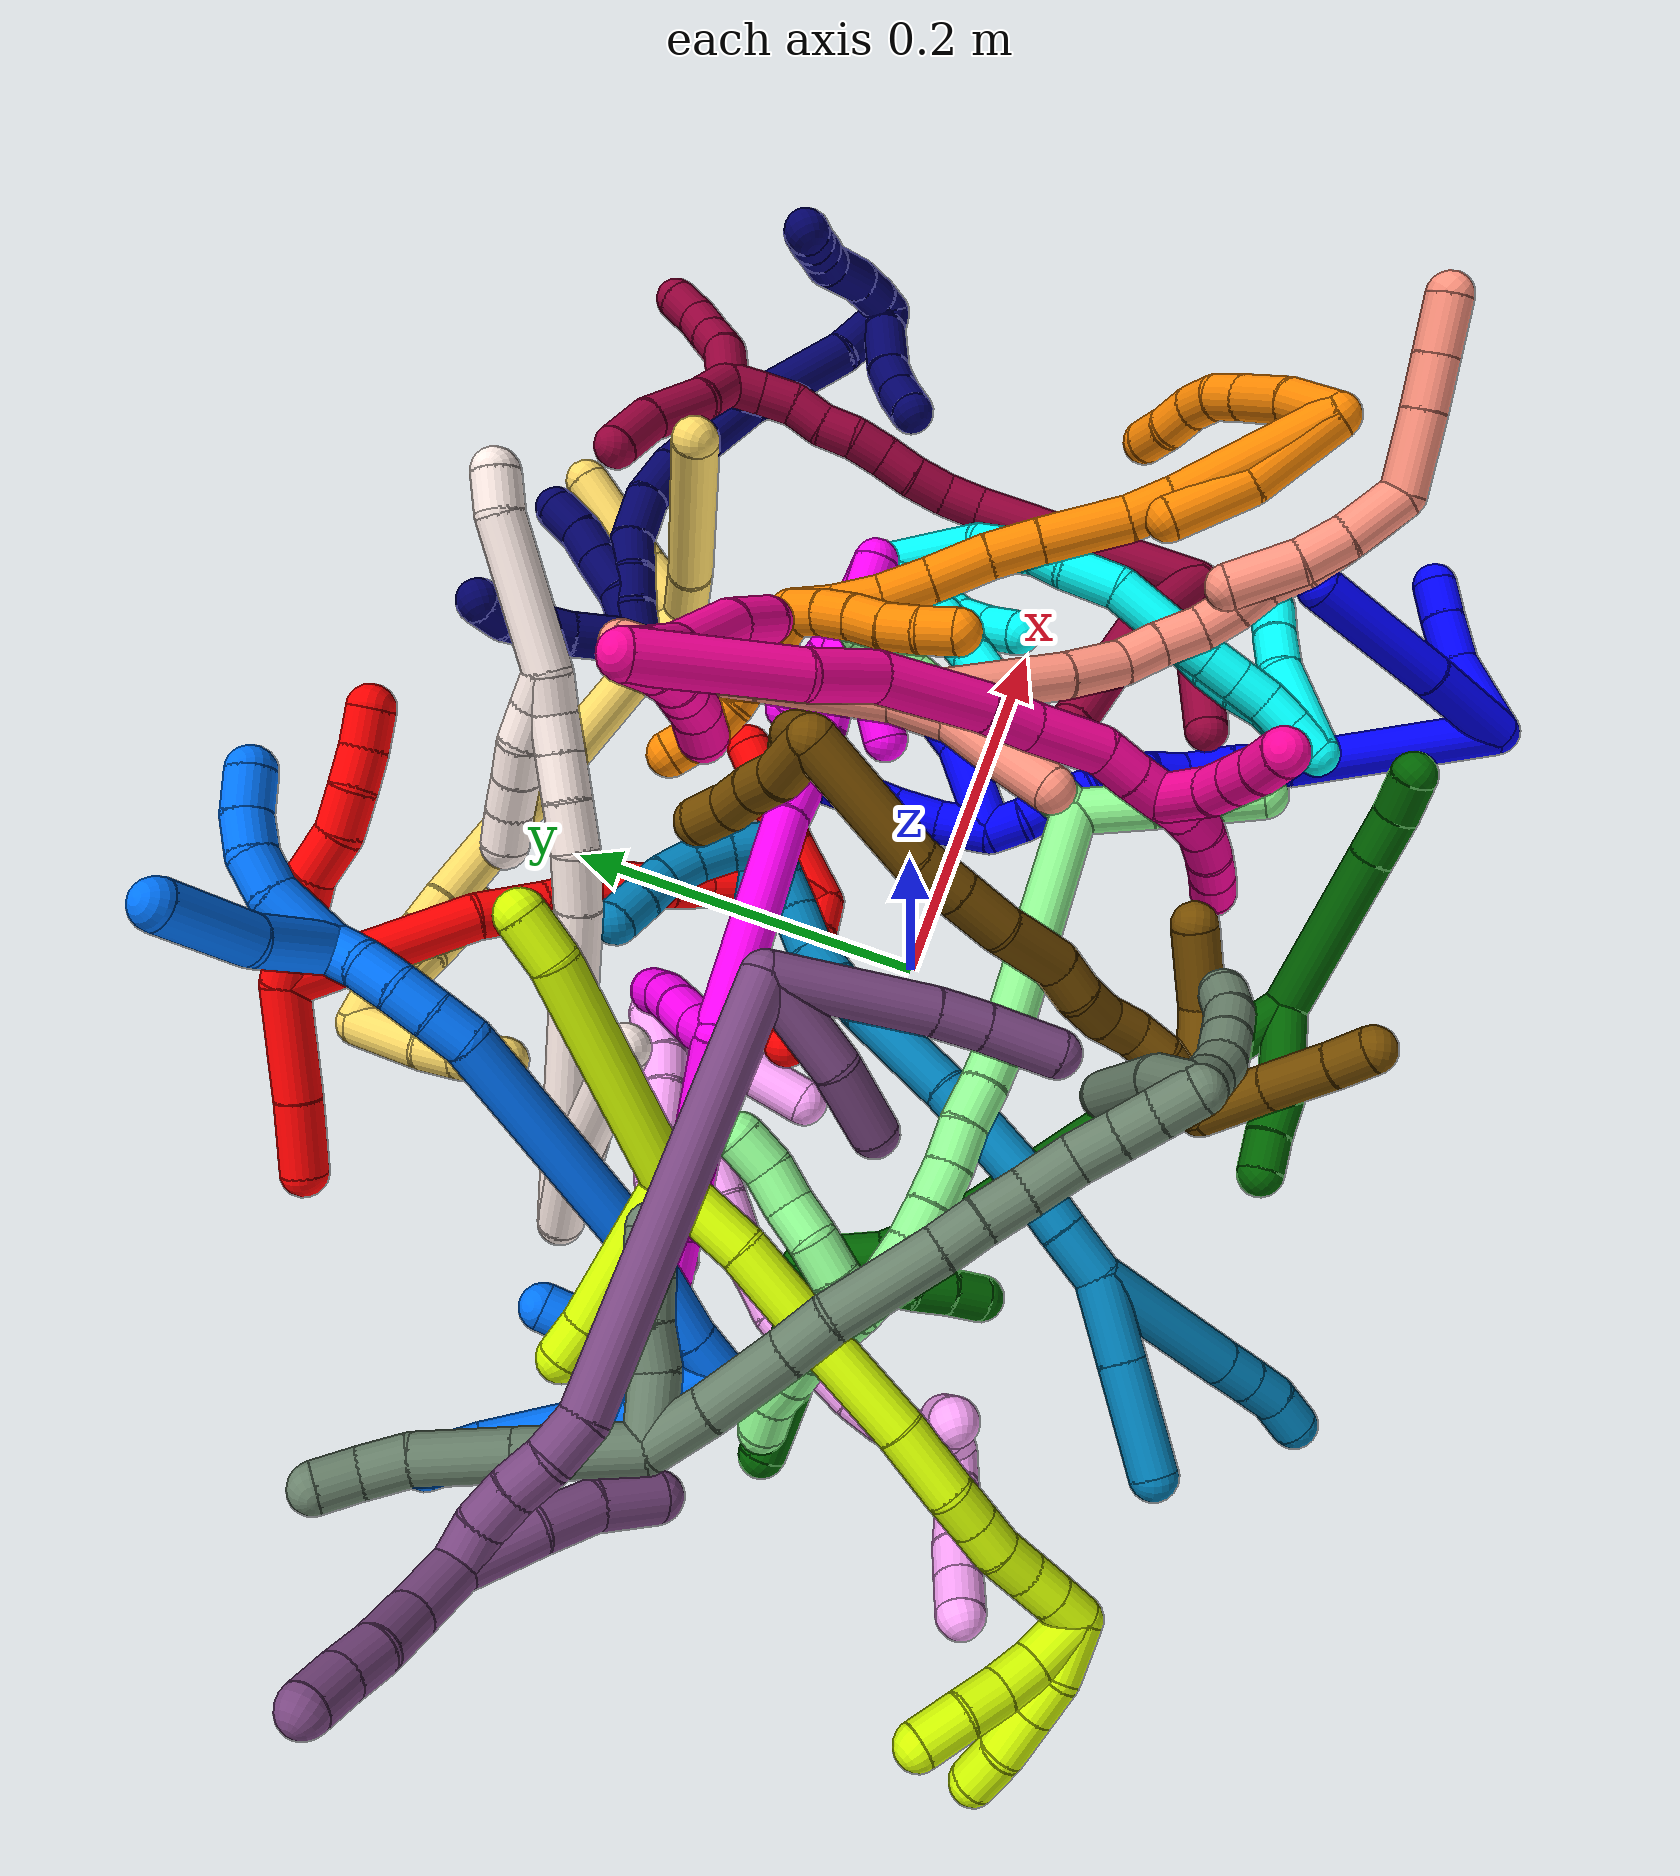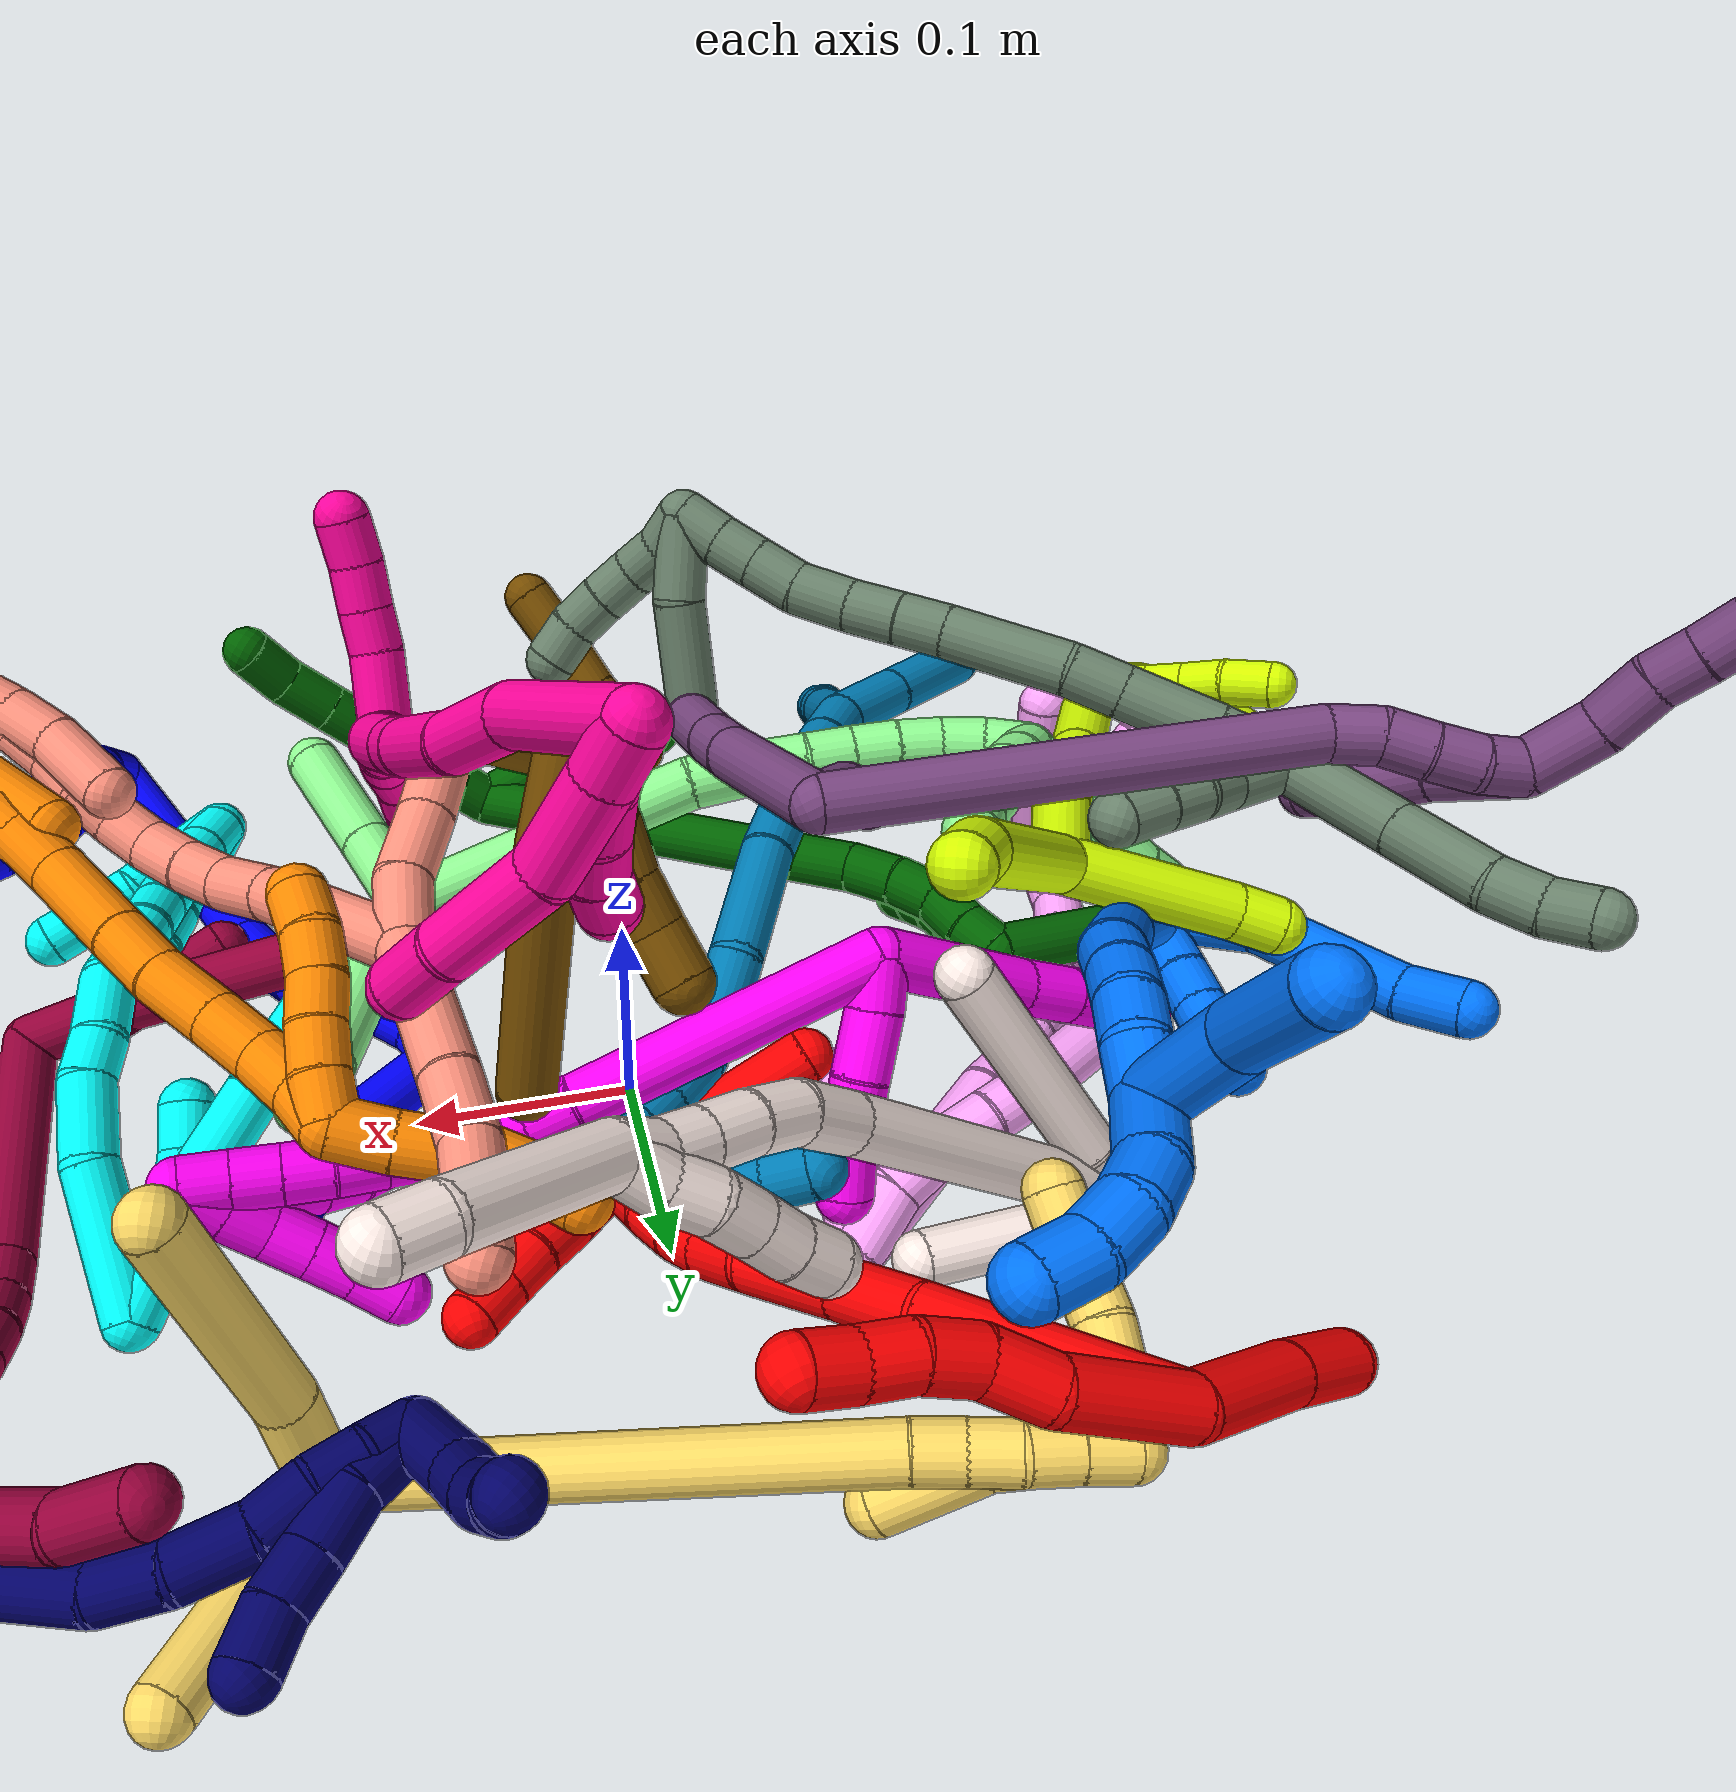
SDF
<sdf version="1.7">
 <world name="default">
  <plugin name="TubeGeneratorPlugin" filename="libtube_generator_plugin.so"/>
  <model name="photoneo_s_sensor">
   <static>1</static>
   <pose>0 0 2 1.57079 1.57079 3.14159</pose>
   <link name="link">
    <inertial><mass>0.1</mass></inertial>
    <sensor name="sensor" type="depth">
     <update_rate>30</update_rate>
     <camera>
      <horizontal_fov>1.22</horizontal_fov>
      <image><width>1920</width><height>1200</height><format>B8G8R8</format></image>
      <clip><near>0.1</near><far>4</far></clip>
      <depth_camera><output>points</output></depth_camera>
     </camera>
     <plugin name="camera_plugin" filename="libgazebo_ros_depth_camera.so">
      <baseline>0.2</baseline>
      <alwaysOn>1</alwaysOn>
      <updateRate>0.0</updateRate>
      <cameraName>camera_ir</cameraName>
      <imageTopicName>/camera/color/image_raw</imageTopicName>
      <cameraInfoTopicName>/camera/color/camera_info</cameraInfoTopicName>
      <depthImageTopicName>/camera/depth/image_raw</depthImageTopicName>
      <depthImageCameraInfoTopicName>/camera/depth/camera_info</depthImageCameraInfoTopicName>
      <pointCloudTopicName>/camera/depth/points</pointCloudTopicName>
      <frameName>fr_optical</frameName>
      <pointCloudCutoff>0.1</pointCloudCutoff>
      <pointCloudCutoffMax>2.0</pointCloudCutoffMax>
      <distortionK1>0</distortionK1>
      <distortionK2>0</distortionK2>
      <distortionK3>0</distortionK3>
      <distortionT1>0</distortionT1>
      <distortionT2>0</distortionT2>
      <CxPrime>0</CxPrime>
      <Cx>0</Cx>
      <Cy>0</Cy>
      <focalLength>0</focalLength>
      <hackBaseline>0</hackBaseline>
     </plugin>
    </sensor>
   </link>
  </model>
  <gravity>0 0 -9.8</gravity>
  <magnetic_field>6e-06 2.3e-05 -4.2e-05</magnetic_field>
  <atmosphere type="adiabatic"/>
  <physics name="default_physics" default="0" type="ode">
   <max_step_size>0.003</max_step_size>
   <real_time_factor>1</real_time_factor>
   <real_time_update_rate>1000</real_time_update_rate>
   <max_contacts>10000</max_contacts>
   <ode>
    <solver>
     <type>quick</type>
     <iters>100</iters>
     <sor>1.3</sor>
     <use_dynamic_moi_rescaling>0</use_dynamic_moi_rescaling>
    </solver>
    <constraints>
     <contact_max_correcting_vel>0</contact_max_correcting_vel>
     <contact_surface_layer>0.001</contact_surface_layer>
     <cfm>0</cfm>
     <erp>0.2</erp>
    </constraints>
   </ode>
  </physics>
  <scene><ambient>0.4 0.4 0.4 1</ambient><background>0.7 0.7 0.7 1</background><shadows>0</shadows></scene>
  <audio><device>default</device></audio>
  <spherical_coordinates>
   <surface_model>EARTH_WGS84</surface_model>
   <latitude_deg>0</latitude_deg>
   <longitude_deg>0</longitude_deg>
   <elevation>0</elevation>
   <heading_deg>0</heading_deg>
  </spherical_coordinates>
  <model name="bin">
   <static>1</static>
   <link name="bottom">
    <collision name="collision-bottom">
     <pose>0 0 -0.01 0 -0 0</pose>
     <geometry><box><size>0.8 0.6 0.02</size></box></geometry>
     <surface>
      <friction><ode><mu>100</mu><mu2>100</mu2></ode></friction>
      <contact><collide_bitmask>65535</collide_bitmask></contact>
     </surface>
    </collision>
   </link>
   <link name="west_wall">
    <collision name="collision-west_wall">
     <pose>-0.41 0 0.1 0 -0 0</pose>
     <geometry><box><size>0.02 0.6 0.2</size></box></geometry>
     <surface>
      <friction><ode><mu>100</mu><mu2>100</mu2></ode></friction>
      <contact><collide_bitmask>65535</collide_bitmask></contact>
     </surface>
    </collision>
   </link>
   <link name="east_wall">
    <collision name="collision-east_wall">
     <pose>0.41 0 0.1 0 -0 0</pose>
     <geometry><box><size>0.02 0.6 0.2</size></box></geometry>
     <surface>
      <friction><ode><mu>100</mu><mu2>100</mu2></ode></friction>
      <contact><collide_bitmask>65535</collide_bitmask></contact>
     </surface>
    </collision>
   </link>
   <link name="south_wall">
    <collision name="collision-south_wall">
     <pose>0 -0.31 0.1 0 -0 0</pose>
     <geometry><box><size>0.8 0.02 0.2</size></box></geometry>
     <surface>
      <friction><ode><mu>100</mu><mu2>100</mu2></ode></friction>
      <contact><collide_bitmask>65535</collide_bitmask></contact>
     </surface>
    </collision>
   </link>
   <link name="north_wall">
    <collision name="collision-north_wall">
     <pose>0 0.31 0.1 0 -0 0</pose>
     <geometry><box><size>0.8 0.02 0.2</size></box></geometry>
     <surface>
      <friction><ode><mu>100</mu><mu2>100</mu2></ode></friction>
      <contact><collide_bitmask>65535</collide_bitmask></contact>
     </surface>
    </collision>
   </link>
  </model>
  <model name="1">
   <static>0</static>
   <link name="1">
    <collision name="collision-cylinder-e_1_2_8">
     <pose>0.000369 0.029626 -0.00957 -1.88324 0.01184 -0.016267</pose>
     <geometry><cylinder><radius>0.0125</radius><length>0.06227</length></cylinder></geometry>
     <surface>
      <friction><ode><mu>1.16</mu><mu2>1.16</mu2><slip1>0</slip1><slip2>0</slip2></ode></friction>
      <contact><ode><kp>1e+06</kp><kd>1</kd><max_vel>0</max_vel><min_depth>0.001</min_depth></ode></contact>
     </surface>
    </collision>
    <visual name="visual-cylinder-e_1_2_8">
     <pose>0.000369 0.029626 -0.00957 -1.88324 0.01184 -0.016267</pose>
     <geometry><cylinder><radius>0.0125</radius><length>0.06227</length></cylinder></geometry>
     <material><ambient>0 0 1 1</ambient></material>
    </visual>
    <collision name="collision-cylinder-e_2_8_6">
     <pose>0.004492 0.099818 -0.035398 -1.95198 0.085691 -0.12657</pose>
     <geometry><cylinder><radius>0.0125</radius><length>0.08773</length></cylinder></geometry>
     <surface>
      <friction><ode><mu>1.16</mu><mu2>1.16</mu2><slip1>0</slip1><slip2>0</slip2></ode></friction>
      <contact><ode><kp>1e+06</kp><kd>1</kd><max_vel>0</max_vel><min_depth>0.001</min_depth></ode></contact>
     </surface>
    </collision>
    <visual name="visual-cylinder-e_2_8_6">
     <pose>0.004492 0.099818 -0.035398 -1.95198 0.085691 -0.12657</pose>
     <geometry><cylinder><radius>0.0125</radius><length>0.08773</length></cylinder></geometry>
     <material><ambient>0 0 1 1</ambient></material>
    </visual>
    <collision name="collision-cylinder-e_1_2_9">
     <pose>0.021932 0.008787 -0.006361 -2.19738 1.11146 -1.76529</pose>
     <geometry><cylinder><radius>0.0125</radius><length>0.048936</length></cylinder></geometry>
     <surface>
      <friction><ode><mu>1.16</mu><mu2>1.16</mu2><slip1>0</slip1><slip2>0</slip2></ode></friction>
      <contact><ode><kp>1e+06</kp><kd>1</kd><max_vel>0</max_vel><min_depth>0.001</min_depth></ode></contact>
     </surface>
    </collision>
    <visual name="visual-cylinder-e_1_2_9">
     <pose>0.021932 0.008787 -0.006361 -2.19738 1.11146 -1.76529</pose>
     <geometry><cylinder><radius>0.0125</radius><length>0.048936</length></cylinder></geometry>
     <material><ambient>0 0 1 1</ambient></material>
    </visual>
    <collision name="collision-cylinder-e_2_9_10">
     <pose>0.057055 0.023398 -0.013101 -1.63567 1.15426 -1.21438</pose>
     <geometry><cylinder><radius>0.0125</radius><length>0.028848</length></cylinder></geometry>
     <surface>
      <friction><ode><mu>1.16</mu><mu2>1.16</mu2><slip1>0</slip1><slip2>0</slip2></ode></friction>
      <contact><ode><kp>1e+06</kp><kd>1</kd><max_vel>0</max_vel><min_depth>0.001</min_depth></ode></contact>
     </surface>
    </collision>
    <visual name="visual-cylinder-e_2_9_10">
     <pose>0.057055 0.023398 -0.013101 -1.63567 1.15426 -1.21438</pose>
     <geometry><cylinder><radius>0.0125</radius><length>0.028848</length></cylinder></geometry>
     <material><ambient>0 0 1 1</ambient></material>
    </visual>
    <collision name="collision-cylinder-e_3_10_5">
     <pose>0.080457 0.033589 -0.013327 -1.53612 1.16647 -1.1348</pose>
     <geometry><cylinder><radius>0.0125</radius><length>0.022216</length></cylinder></geometry>
     <surface>
      <friction><ode><mu>1.16</mu><mu2>1.16</mu2><slip1>0</slip1><slip2>0</slip2></ode></friction>
      <contact><ode><kp>1e+06</kp><kd>1</kd><max_vel>0</max_vel><min_depth>0.001</min_depth></ode></contact>
     </surface>
    </collision>
    <visual name="visual-cylinder-e_3_10_5">
     <pose>0.080457 0.033589 -0.013327 -1.53612 1.16647 -1.1348</pose>
     <geometry><cylinder><radius>0.0125</radius><length>0.022216</length></cylinder></geometry>
     <material><ambient>0 0 1 1</ambient></material>
    </visual>
    <collision name="collision-cylinder-e_1_2_11">
     <pose>-0.004377 0.018109 -0.055585 -2.82666 -0.074728 0.462427</pose>
     <geometry><cylinder><radius>0.0125</radius><length>0.117249</length></cylinder></geometry>
     <surface>
      <friction><ode><mu>1.16</mu><mu2>1.16</mu2><slip1>0</slip1><slip2>0</slip2></ode></friction>
      <contact><ode><kp>1e+06</kp><kd>1</kd><max_vel>0</max_vel><min_depth>0.001</min_depth></ode></contact>
     </surface>
    </collision>
    <visual name="visual-cylinder-e_1_2_11">
     <pose>-0.004377 0.018109 -0.055585 -2.82666 -0.074728 0.462427</pose>
     <geometry><cylinder><radius>0.0125</radius><length>0.117249</length></cylinder></geometry>
     <material><ambient>0 0 1 1</ambient></material>
    </visual>
    <collision name="collision-cylinder-e_2_11_12">
     <pose>-0.009858 0.04376 -0.124943 -2.64054 -0.070249 0.272919</pose>
     <geometry><cylinder><radius>0.0125</radius><length>0.031482</length></cylinder></geometry>
     <surface>
      <friction><ode><mu>1.16</mu><mu2>1.16</mu2><slip1>0</slip1><slip2>0</slip2></ode></friction>
      <contact><ode><kp>1e+06</kp><kd>1</kd><max_vel>0</max_vel><min_depth>0.001</min_depth></ode></contact>
     </surface>
    </collision>
    <visual name="visual-cylinder-e_2_11_12">
     <pose>-0.009858 0.04376 -0.124943 -2.64054 -0.070249 0.272919</pose>
     <geometry><cylinder><radius>0.0125</radius><length>0.031482</length></cylinder></geometry>
     <material><ambient>0 0 1 1</ambient></material>
    </visual>
    <collision name="collision-cylinder-e_3_12_13">
     <pose>-0.013845 0.057466 -0.151346 -2.68762 -0.202218 0.827768</pose>
     <geometry><cylinder><radius>0.0125</radius><length>0.028695</length></cylinder></geometry>
     <surface>
      <friction><ode><mu>1.16</mu><mu2>1.16</mu2><slip1>0</slip1><slip2>0</slip2></ode></friction>
      <contact><ode><kp>1e+06</kp><kd>1</kd><max_vel>0</max_vel><min_depth>0.001</min_depth></ode></contact>
     </surface>
    </collision>
    <visual name="visual-cylinder-e_3_12_13">
     <pose>-0.013845 0.057466 -0.151346 -2.68762 -0.202218 0.827768</pose>
     <geometry><cylinder><radius>0.0125</radius><length>0.028695</length></cylinder></geometry>
     <material><ambient>0 0 1 1</ambient></material>
    </visual>
    <collision name="collision-cylinder-e_4_13_14">
     <pose>-0.019141 0.070956 -0.171019 -2.33639 -0.233331 0.537102</pose>
     <geometry><cylinder><radius>0.0125</radius><length>0.020888</length></cylinder></geometry>
     <surface>
      <friction><ode><mu>1.16</mu><mu2>1.16</mu2><slip1>0</slip1><slip2>0</slip2></ode></friction>
      <contact><ode><kp>1e+06</kp><kd>1</kd><max_vel>0</max_vel><min_depth>0.001</min_depth></ode></contact>
     </surface>
    </collision>
    <visual name="visual-cylinder-e_4_13_14">
     <pose>-0.019141 0.070956 -0.171019 -2.33639 -0.233331 0.537102</pose>
     <geometry><cylinder><radius>0.0125</radius><length>0.020888</length></cylinder></geometry>
     <material><ambient>0 0 1 1</ambient></material>
    </visual>
    <collision name="collision-cylinder-e_5_14_15">
     <pose>-0.026757 0.084167 -0.185517 -2.47342 -0.500897 1.27029</pose>
     <geometry><cylinder><radius>0.0125</radius><length>0.021659</length></cylinder></geometry>
     <surface>
      <friction><ode><mu>1.16</mu><mu2>1.16</mu2><slip1>0</slip1><slip2>0</slip2></ode></friction>
      <contact><ode><kp>1e+06</kp><kd>1</kd><max_vel>0</max_vel><min_depth>0.001</min_depth></ode></contact>
     </surface>
    </collision>
    <visual name="visual-cylinder-e_5_14_15">
     <pose>-0.026757 0.084167 -0.185517 -2.47342 -0.500897 1.27029</pose>
     <geometry><cylinder><radius>0.0125</radius><length>0.021659</length></cylinder></geometry>
     <material><ambient>0 0 1 1</ambient></material>
    </visual>
    <collision name="collision-cylinder-e_6_15_16">
     <pose>-0.036687 0.09551 -0.199906 -2.47469 -0.492044 1.25454</pose>
     <geometry><cylinder><radius>0.0125</radius><length>0.020023</length></cylinder></geometry>
     <surface>
      <friction><ode><mu>1.16</mu><mu2>1.16</mu2><slip1>0</slip1><slip2>0</slip2></ode></friction>
      <contact><ode><kp>1e+06</kp><kd>1</kd><max_vel>0</max_vel><min_depth>0.001</min_depth></ode></contact>
     </surface>
    </collision>
    <visual name="visual-cylinder-e_6_15_16">
     <pose>-0.036687 0.09551 -0.199906 -2.47469 -0.492044 1.25454</pose>
     <geometry><cylinder><radius>0.0125</radius><length>0.020023</length></cylinder></geometry>
     <material><ambient>0 0 1 1</ambient></material>
    </visual>
    <collision name="collision-cylinder-e_7_16_17">
     <pose>-0.045436 0.104405 -0.215329 -2.75693 -0.413541 1.64508</pose>
     <geometry><cylinder><radius>0.0125</radius><length>0.020004</length></cylinder></geometry>
     <surface>
      <friction><ode><mu>1.16</mu><mu2>1.16</mu2><slip1>0</slip1><slip2>0</slip2></ode></friction>
      <contact><ode><kp>1e+06</kp><kd>1</kd><max_vel>0</max_vel><min_depth>0.001</min_depth></ode></contact>
     </surface>
    </collision>
    <visual name="visual-cylinder-e_7_16_17">
     <pose>-0.045436 0.104405 -0.215329 -2.75693 -0.413541 1.64508</pose>
     <geometry><cylinder><radius>0.0125</radius><length>0.020004</length></cylinder></geometry>
     <material><ambient>0 0 1 1</ambient></material>
    </visual>
    <collision name="collision-cylinder-e_8_17_18">
     <pose>-0.053616 0.109632 -0.232734 -2.94347 -0.429135 2.28582</pose>
     <geometry><cylinder><radius>0.0125</radius><length>0.02</length></cylinder></geometry>
     <surface>
      <friction><ode><mu>1.16</mu><mu2>1.16</mu2><slip1>0</slip1><slip2>0</slip2></ode></friction>
      <contact><ode><kp>1e+06</kp><kd>1</kd><max_vel>0</max_vel><min_depth>0.001</min_depth></ode></contact>
     </surface>
    </collision>
    <visual name="visual-cylinder-e_8_17_18">
     <pose>-0.053616 0.109632 -0.232734 -2.94347 -0.429135 2.28582</pose>
     <geometry><cylinder><radius>0.0125</radius><length>0.02</length></cylinder></geometry>
     <material><ambient>0 0 1 1</ambient></material>
    </visual>
    <collision name="collision-cylinder-e_9_18_1">
     <pose>-0.059059 0.112537 -0.251504 -3.02884 -0.128554 1.70189</pose>
     <geometry><cylinder><radius>0.0125</radius><length>0.02</length></cylinder></geometry>
     <surface>
      <friction><ode><mu>1.16</mu><mu2>1.16</mu2><slip1>0</slip1><slip2>0</slip2></ode></friction>
      <contact><ode><kp>1e+06</kp><kd>1</kd><max_vel>0</max_vel><min_depth>0.001</min_depth></ode></contact>
     </surface>
    </collision>
    <visual name="visual-cylinder-e_9_18_1">
     <pose>-0.059059 0.112537 -0.251504 -3.02884 -0.128554 1.70189</pose>
     <geometry><cylinder><radius>0.0125</radius><length>0.02</length></cylinder></geometry>
     <material><ambient>0 0 1 1</ambient></material>
    </visual>
    <collision name="collision-cylinder-e_1_1_19">
     <pose>-0.036814 0.126491 -0.264916 -1.84115 1.05558 -1.30794</pose>
     <geometry><cylinder><radius>0.0125</radius><length>0.054074</length></cylinder></geometry>
     <surface>
      <friction><ode><mu>1.16</mu><mu2>1.16</mu2><slip1>0</slip1><slip2>0</slip2></ode></friction>
      <contact><ode><kp>1e+06</kp><kd>1</kd><max_vel>0</max_vel><min_depth>0.001</min_depth></ode></contact>
     </surface>
    </collision>
    <visual name="visual-cylinder-e_1_1_19">
     <pose>-0.036814 0.126491 -0.264916 -1.84115 1.05558 -1.30794</pose>
     <geometry><cylinder><radius>0.0125</radius><length>0.054074</length></cylinder></geometry>
     <material><ambient>0 0 1 1</ambient></material>
    </visual>
    <collision name="collision-cylinder-e_2_19_4">
     <pose>0.004671 0.150227 -0.27775 -2.27592 0.897915 -1.61256</pose>
     <geometry><cylinder><radius>0.0125</radius><length>0.045926</length></cylinder></geometry>
     <surface>
      <friction><ode><mu>1.16</mu><mu2>1.16</mu2><slip1>0</slip1><slip2>0</slip2></ode></friction>
      <contact><ode><kp>1e+06</kp><kd>1</kd><max_vel>0</max_vel><min_depth>0.001</min_depth></ode></contact>
     </surface>
    </collision>
    <visual name="visual-cylinder-e_2_19_4">
     <pose>0.004671 0.150227 -0.27775 -2.27592 0.897915 -1.61256</pose>
     <geometry><cylinder><radius>0.0125</radius><length>0.045926</length></cylinder></geometry>
     <material><ambient>0 0 1 1</ambient></material>
    </visual>
    <collision name="collision-cylinder-e_1_1_20">
     <pose>-0.055839 0.11898 -0.274708 -2.7619 0.303558 -1.34457</pose>
     <geometry><cylinder><radius>0.0125</radius><length>0.030124</length></cylinder></geometry>
     <surface>
      <friction><ode><mu>1.16</mu><mu2>1.16</mu2><slip1>0</slip1><slip2>0</slip2></ode></friction>
      <contact><ode><kp>1e+06</kp><kd>1</kd><max_vel>0</max_vel><min_depth>0.001</min_depth></ode></contact>
     </surface>
    </collision>
    <visual name="visual-cylinder-e_1_1_20">
     <pose>-0.055839 0.11898 -0.274708 -2.7619 0.303558 -1.34457</pose>
     <geometry><cylinder><radius>0.0125</radius><length>0.030124</length></cylinder></geometry>
     <material><ambient>0 0 1 1</ambient></material>
    </visual>
    <collision name="collision-cylinder-e_2_20_21">
     <pose>-0.048295 0.131999 -0.298208 -2.49314 0.234412 -0.673959</pose>
     <geometry><cylinder><radius>0.0125</radius><length>0.026186</length></cylinder></geometry>
     <surface>
      <friction><ode><mu>1.16</mu><mu2>1.16</mu2><slip1>0</slip1><slip2>0</slip2></ode></friction>
      <contact><ode><kp>1e+06</kp><kd>1</kd><max_vel>0</max_vel><min_depth>0.001</min_depth></ode></contact>
     </surface>
    </collision>
    <visual name="visual-cylinder-e_2_20_21">
     <pose>-0.048295 0.131999 -0.298208 -2.49314 0.234412 -0.673959</pose>
     <geometry><cylinder><radius>0.0125</radius><length>0.026186</length></cylinder></geometry>
     <material><ambient>0 0 1 1</ambient></material>
    </visual>
    <collision name="collision-cylinder-e_3_21_22">
     <pose>-0.041577 0.145702 -0.316285 -2.4928 0.354073 -0.977887</pose>
     <geometry><cylinder><radius>0.0125</radius><length>0.021214</length></cylinder></geometry>
     <surface>
      <friction><ode><mu>1.16</mu><mu2>1.16</mu2><slip1>0</slip1><slip2>0</slip2></ode></friction>
      <contact><ode><kp>1e+06</kp><kd>1</kd><max_vel>0</max_vel><min_depth>0.001</min_depth></ode></contact>
     </surface>
    </collision>
    <visual name="visual-cylinder-e_3_21_22">
     <pose>-0.041577 0.145702 -0.316285 -2.4928 0.354073 -0.977887</pose>
     <geometry><cylinder><radius>0.0125</radius><length>0.021214</length></cylinder></geometry>
     <material><ambient>0 0 1 1</ambient></material>
    </visual>
    <collision name="collision-cylinder-e_4_22_3">
     <pose>-0.03337 0.156753 -0.333178 -2.62944 0.414762 -1.35389</pose>
     <geometry><cylinder><radius>0.0125</radius><length>0.022476</length></cylinder></geometry>
     <surface>
      <friction><ode><mu>1.16</mu><mu2>1.16</mu2><slip1>0</slip1><slip2>0</slip2></ode></friction>
      <contact><ode><kp>1e+06</kp><kd>1</kd><max_vel>0</max_vel><min_depth>0.001</min_depth></ode></contact>
     </surface>
    </collision>
    <visual name="visual-cylinder-e_4_22_3">
     <pose>-0.03337 0.156753 -0.333178 -2.62944 0.414762 -1.35389</pose>
     <geometry><cylinder><radius>0.0125</radius><length>0.022476</length></cylinder></geometry>
     <material><ambient>0 0 1 1</ambient></material>
    </visual>
    <collision name="collision-sphere-3">
     <pose>-0.028842 0.161794 -0.342144 0 -0 0</pose>
     <geometry><sphere><radius>0.0125</radius></sphere></geometry>
     <surface>
      <friction><ode><mu>1.16</mu><mu2>1.16</mu2><slip1>0</slip1><slip2>0</slip2></ode></friction>
      <contact><ode><kp>1e+06</kp><kd>1</kd><max_vel>0</max_vel><min_depth>0.001</min_depth></ode></contact>
     </surface>
    </collision>
    <visual name="visual-sphere-3">
     <pose>-0.028842 0.161794 -0.342144 0 -0 0</pose>
     <geometry><sphere><radius>0.0125</radius></sphere></geometry>
     <material><ambient>0 0 1 1</ambient></material>
    </visual>
    <collision name="collision-sphere-22">
     <pose>-0.037899 0.151713 -0.324213 0 -0 0</pose>
     <geometry><sphere><radius>0.0125</radius></sphere></geometry>
     <surface>
      <friction><ode><mu>1.16</mu><mu2>1.16</mu2><slip1>0</slip1><slip2>0</slip2></ode></friction>
      <contact><ode><kp>1e+06</kp><kd>1</kd><max_vel>0</max_vel><min_depth>0.001</min_depth></ode></contact>
     </surface>
    </collision>
    <visual name="visual-sphere-22">
     <pose>-0.037899 0.151713 -0.324213 0 -0 0</pose>
     <geometry><sphere><radius>0.0125</radius></sphere></geometry>
     <material><ambient>0 0 1 1</ambient></material>
    </visual>
    <collision name="collision-sphere-21">
     <pose>-0.045254 0.13969 -0.308358 0 -0 0</pose>
     <geometry><sphere><radius>0.0125</radius></sphere></geometry>
     <surface>
      <friction><ode><mu>1.16</mu><mu2>1.16</mu2><slip1>0</slip1><slip2>0</slip2></ode></friction>
      <contact><ode><kp>1e+06</kp><kd>1</kd><max_vel>0</max_vel><min_depth>0.001</min_depth></ode></contact>
     </surface>
    </collision>
    <visual name="visual-sphere-21">
     <pose>-0.045254 0.13969 -0.308358 0 -0 0</pose>
     <geometry><sphere><radius>0.0125</radius></sphere></geometry>
     <material><ambient>0 0 1 1</ambient></material>
    </visual>
    <collision name="collision-sphere-20">
     <pose>-0.051337 0.124307 -0.288058 0 -0 0</pose>
     <geometry><sphere><radius>0.0125</radius></sphere></geometry>
     <surface>
      <friction><ode><mu>1.16</mu><mu2>1.16</mu2><slip1>0</slip1><slip2>0</slip2></ode></friction>
      <contact><ode><kp>1e+06</kp><kd>1</kd><max_vel>0</max_vel><min_depth>0.001</min_depth></ode></contact>
     </surface>
    </collision>
    <visual name="visual-sphere-20">
     <pose>-0.051337 0.124307 -0.288058 0 -0 0</pose>
     <geometry><sphere><radius>0.0125</radius></sphere></geometry>
     <material><ambient>0 0 1 1</ambient></material>
    </visual>
    <collision name="collision-sphere-4">
     <pose>0.022629 0.161126 -0.287026 0 -0 0</pose>
     <geometry><sphere><radius>0.0125</radius></sphere></geometry>
     <surface>
      <friction><ode><mu>1.16</mu><mu2>1.16</mu2><slip1>0</slip1><slip2>0</slip2></ode></friction>
      <contact><ode><kp>1e+06</kp><kd>1</kd><max_vel>0</max_vel><min_depth>0.001</min_depth></ode></contact>
     </surface>
    </collision>
    <visual name="visual-sphere-4">
     <pose>0.022629 0.161126 -0.287026 0 -0 0</pose>
     <geometry><sphere><radius>0.0125</radius></sphere></geometry>
     <material><ambient>0 0 1 1</ambient></material>
    </visual>
    <collision name="collision-sphere-5">
     <pose>0.09067 0.037956 -0.013176 0 -0 0</pose>
     <geometry><sphere><radius>0.0125</radius></sphere></geometry>
     <surface>
      <friction><ode><mu>1.16</mu><mu2>1.16</mu2><slip1>0</slip1><slip2>0</slip2></ode></friction>
      <contact><ode><kp>1e+06</kp><kd>1</kd><max_vel>0</max_vel><min_depth>0.001</min_depth></ode></contact>
     </surface>
    </collision>
    <visual name="visual-sphere-5">
     <pose>0.09067 0.037956 -0.013176 0 -0 0</pose>
     <geometry><sphere><radius>0.0125</radius></sphere></geometry>
     <material><ambient>0 0 1 1</ambient></material>
    </visual>
    <collision name="collision-sphere-10">
     <pose>0.070245 0.029222 -0.013479 0 -0 0</pose>
     <geometry><sphere><radius>0.0125</radius></sphere></geometry>
     <surface>
      <friction><ode><mu>1.16</mu><mu2>1.16</mu2><slip1>0</slip1><slip2>0</slip2></ode></friction>
      <contact><ode><kp>1e+06</kp><kd>1</kd><max_vel>0</max_vel><min_depth>0.001</min_depth></ode></contact>
     </surface>
    </collision>
    <visual name="visual-sphere-10">
     <pose>0.070245 0.029222 -0.013479 0 -0 0</pose>
     <geometry><sphere><radius>0.0125</radius></sphere></geometry>
     <material><ambient>0 0 1 1</ambient></material>
    </visual>
    <collision name="collision-sphere-6">
     <pose>0.008246 0.140385 -0.051657 0 -0 0</pose>
     <geometry><sphere><radius>0.0125</radius></sphere></geometry>
     <surface>
      <friction><ode><mu>1.16</mu><mu2>1.16</mu2><slip1>0</slip1><slip2>0</slip2></ode></friction>
      <contact><ode><kp>1e+06</kp><kd>1</kd><max_vel>0</max_vel><min_depth>0.001</min_depth></ode></contact>
     </surface>
    </collision>
    <visual name="visual-sphere-6">
     <pose>0.008246 0.140385 -0.051657 0 -0 0</pose>
     <geometry><sphere><radius>0.0125</radius></sphere></geometry>
     <material><ambient>0 0 1 1</ambient></material>
    </visual>
    <collision name="collision-sphere-9">
     <pose>0.043864 0.017575 -0.012722 0 -0 0</pose>
     <geometry><sphere><radius>0.0125</radius></sphere></geometry>
     <surface>
      <friction><ode><mu>1.16</mu><mu2>1.16</mu2><slip1>0</slip1><slip2>0</slip2></ode></friction>
      <contact><ode><kp>1e+06</kp><kd>1</kd><max_vel>0</max_vel><min_depth>0.001</min_depth></ode></contact>
     </surface>
    </collision>
    <visual name="visual-sphere-9">
     <pose>0.043864 0.017575 -0.012722 0 -0 0</pose>
     <geometry><sphere><radius>0.0125</radius></sphere></geometry>
     <material><ambient>0 0 1 1</ambient></material>
    </visual>
    <collision name="collision-sphere-2">
     <geometry><sphere><radius>0.0125</radius></sphere></geometry>
     <surface>
      <friction><ode><mu>1.16</mu><mu2>1.16</mu2><slip1>0</slip1><slip2>0</slip2></ode></friction>
      <contact><ode><kp>1e+06</kp><kd>1</kd><max_vel>0</max_vel><min_depth>0.001</min_depth></ode></contact>
     </surface>
    </collision>
    <visual name="visual-sphere-2">
     <geometry><sphere><radius>0.0125</radius></sphere></geometry>
     <material><ambient>0 0 1 1</ambient></material>
    </visual>
    <collision name="collision-sphere-19">
     <pose>-0.013287 0.139329 -0.268474 0 -0 0</pose>
     <geometry><sphere><radius>0.0125</radius></sphere></geometry>
     <surface>
      <friction><ode><mu>1.16</mu><mu2>1.16</mu2><slip1>0</slip1><slip2>0</slip2></ode></friction>
      <contact><ode><kp>1e+06</kp><kd>1</kd><max_vel>0</max_vel><min_depth>0.001</min_depth></ode></contact>
     </surface>
    </collision>
    <visual name="visual-sphere-19">
     <pose>-0.013287 0.139329 -0.268474 0 -0 0</pose>
     <geometry><sphere><radius>0.0125</radius></sphere></geometry>
     <material><ambient>0 0 1 1</ambient></material>
    </visual>
    <collision name="collision-sphere-8">
     <pose>0.000737 0.059251 -0.019139 0 -0 0</pose>
     <geometry><sphere><radius>0.0125</radius></sphere></geometry>
     <surface>
      <friction><ode><mu>1.16</mu><mu2>1.16</mu2><slip1>0</slip1><slip2>0</slip2></ode></friction>
      <contact><ode><kp>1e+06</kp><kd>1</kd><max_vel>0</max_vel><min_depth>0.001</min_depth></ode></contact>
     </surface>
    </collision>
    <visual name="visual-sphere-8">
     <pose>0.000737 0.059251 -0.019139 0 -0 0</pose>
     <geometry><sphere><radius>0.0125</radius></sphere></geometry>
     <material><ambient>0 0 1 1</ambient></material>
    </visual>
    <collision name="collision-sphere-11">
     <pose>-0.008754 0.036217 -0.111171 0 -0 0</pose>
     <geometry><sphere><radius>0.0125</radius></sphere></geometry>
     <surface>
      <friction><ode><mu>1.16</mu><mu2>1.16</mu2><slip1>0</slip1><slip2>0</slip2></ode></friction>
      <contact><ode><kp>1e+06</kp><kd>1</kd><max_vel>0</max_vel><min_depth>0.001</min_depth></ode></contact>
     </surface>
    </collision>
    <visual name="visual-sphere-11">
     <pose>-0.008754 0.036217 -0.111171 0 -0 0</pose>
     <geometry><sphere><radius>0.0125</radius></sphere></geometry>
     <material><ambient>0 0 1 1</ambient></material>
    </visual>
    <collision name="collision-sphere-12">
     <pose>-0.010963 0.051302 -0.138715 0 -0 0</pose>
     <geometry><sphere><radius>0.0125</radius></sphere></geometry>
     <surface>
      <friction><ode><mu>1.16</mu><mu2>1.16</mu2><slip1>0</slip1><slip2>0</slip2></ode></friction>
      <contact><ode><kp>1e+06</kp><kd>1</kd><max_vel>0</max_vel><min_depth>0.001</min_depth></ode></contact>
     </surface>
    </collision>
    <visual name="visual-sphere-12">
     <pose>-0.010963 0.051302 -0.138715 0 -0 0</pose>
     <geometry><sphere><radius>0.0125</radius></sphere></geometry>
     <material><ambient>0 0 1 1</ambient></material>
    </visual>
    <collision name="collision-sphere-13">
     <pose>-0.016727 0.06363 -0.163978 0 -0 0</pose>
     <geometry><sphere><radius>0.0125</radius></sphere></geometry>
     <surface>
      <friction><ode><mu>1.16</mu><mu2>1.16</mu2><slip1>0</slip1><slip2>0</slip2></ode></friction>
      <contact><ode><kp>1e+06</kp><kd>1</kd><max_vel>0</max_vel><min_depth>0.001</min_depth></ode></contact>
     </surface>
    </collision>
    <visual name="visual-sphere-13">
     <pose>-0.016727 0.06363 -0.163978 0 -0 0</pose>
     <geometry><sphere><radius>0.0125</radius></sphere></geometry>
     <material><ambient>0 0 1 1</ambient></material>
    </visual>
    <collision name="collision-sphere-14">
     <pose>-0.021556 0.078282 -0.17806 0 -0 0</pose>
     <geometry><sphere><radius>0.0125</radius></sphere></geometry>
     <surface>
      <friction><ode><mu>1.16</mu><mu2>1.16</mu2><slip1>0</slip1><slip2>0</slip2></ode></friction>
      <contact><ode><kp>1e+06</kp><kd>1</kd><max_vel>0</max_vel><min_depth>0.001</min_depth></ode></contact>
     </surface>
    </collision>
    <visual name="visual-sphere-14">
     <pose>-0.021556 0.078282 -0.17806 0 -0 0</pose>
     <geometry><sphere><radius>0.0125</radius></sphere></geometry>
     <material><ambient>0 0 1 1</ambient></material>
    </visual>
    <collision name="collision-sphere-15">
     <pose>-0.031957 0.090052 -0.192973 0 -0 0</pose>
     <geometry><sphere><radius>0.0125</radius></sphere></geometry>
     <surface>
      <friction><ode><mu>1.16</mu><mu2>1.16</mu2><slip1>0</slip1><slip2>0</slip2></ode></friction>
      <contact><ode><kp>1e+06</kp><kd>1</kd><max_vel>0</max_vel><min_depth>0.001</min_depth></ode></contact>
     </surface>
    </collision>
    <visual name="visual-sphere-15">
     <pose>-0.031957 0.090052 -0.192973 0 -0 0</pose>
     <geometry><sphere><radius>0.0125</radius></sphere></geometry>
     <material><ambient>0 0 1 1</ambient></material>
    </visual>
    <collision name="collision-sphere-16">
     <pose>-0.041416 0.100968 -0.206839 0 -0 0</pose>
     <geometry><sphere><radius>0.0125</radius></sphere></geometry>
     <surface>
      <friction><ode><mu>1.16</mu><mu2>1.16</mu2><slip1>0</slip1><slip2>0</slip2></ode></friction>
      <contact><ode><kp>1e+06</kp><kd>1</kd><max_vel>0</max_vel><min_depth>0.001</min_depth></ode></contact>
     </surface>
    </collision>
    <visual name="visual-sphere-16">
     <pose>-0.041416 0.100968 -0.206839 0 -0 0</pose>
     <geometry><sphere><radius>0.0125</radius></sphere></geometry>
     <material><ambient>0 0 1 1</ambient></material>
    </visual>
    <collision name="collision-sphere-17">
     <pose>-0.049455 0.107842 -0.223819 0 -0 0</pose>
     <geometry><sphere><radius>0.0125</radius></sphere></geometry>
     <surface>
      <friction><ode><mu>1.16</mu><mu2>1.16</mu2><slip1>0</slip1><slip2>0</slip2></ode></friction>
      <contact><ode><kp>1e+06</kp><kd>1</kd><max_vel>0</max_vel><min_depth>0.001</min_depth></ode></contact>
     </surface>
    </collision>
    <visual name="visual-sphere-17">
     <pose>-0.049455 0.107842 -0.223819 0 -0 0</pose>
     <geometry><sphere><radius>0.0125</radius></sphere></geometry>
     <material><ambient>0 0 1 1</ambient></material>
    </visual>
    <collision name="collision-sphere-18">
     <pose>-0.057777 0.111421 -0.24165 0 -0 0</pose>
     <geometry><sphere><radius>0.0125</radius></sphere></geometry>
     <surface>
      <friction><ode><mu>1.16</mu><mu2>1.16</mu2><slip1>0</slip1><slip2>0</slip2></ode></friction>
      <contact><ode><kp>1e+06</kp><kd>1</kd><max_vel>0</max_vel><min_depth>0.001</min_depth></ode></contact>
     </surface>
    </collision>
    <visual name="visual-sphere-18">
     <pose>-0.057777 0.111421 -0.24165 0 -0 0</pose>
     <geometry><sphere><radius>0.0125</radius></sphere></geometry>
     <material><ambient>0 0 1 1</ambient></material>
    </visual>
    <collision name="collision-sphere-1">
     <pose>-0.060341 0.113653 -0.261359 0 -0 0</pose>
     <geometry><sphere><radius>0.0125</radius></sphere></geometry>
     <surface>
      <friction><ode><mu>1.16</mu><mu2>1.16</mu2><slip1>0</slip1><slip2>0</slip2></ode></friction>
      <contact><ode><kp>1e+06</kp><kd>1</kd><max_vel>0</max_vel><min_depth>0.001</min_depth></ode></contact>
     </surface>
    </collision>
    <visual name="visual-sphere-1">
     <pose>-0.060341 0.113653 -0.261359 0 -0 0</pose>
     <geometry><sphere><radius>0.0125</radius></sphere></geometry>
     <material><ambient>0 0 1 1</ambient></material>
    </visual>
    <inertial>
     <pose>-0.010038 0.075662 -0.136572 0 -0 0</pose>
     <mass>0.75</mass>
     <inertia>
      <ixx>0.000266</ixx>
      <ixy>0</ixy>
      <ixz>0</ixz>
      <iyy>-5.3e-05</iyy>
      <iyz>0</iyz>
      <izz>-0.000213</izz>
     </inertia>
    </inertial>
   </link>
   <pose>0.233571 -0.266834 0.031542 1.04606 0.384964 0.301969</pose>
  </model>
  <model name="2">
   <static>0</static>
   <link name="2">
    <collision name="collision-cylinder-e_1_2_8">
     <pose>-0.000973 0.028131 -0.00752 -1.83202 -0.033415 0.043518</pose>
     <geometry><cylinder><radius>0.0125</radius><length>0.05827</length></cylinder></geometry>
     <surface>
      <friction><ode><mu>1.16</mu><mu2>1.16</mu2><slip1>0</slip1><slip2>0</slip2></ode></friction>
      <contact><ode><kp>1e+06</kp><kd>1</kd><max_vel>0</max_vel><min_depth>0.001</min_depth></ode></contact>
     </surface>
    </collision>
    <visual name="visual-cylinder-e_1_2_8">
     <pose>-0.000973 0.028131 -0.00752 -1.83202 -0.033415 0.043518</pose>
     <geometry><cylinder><radius>0.0125</radius><length>0.05827</length></cylinder></geometry>
     <material><ambient>1 0 0 1</ambient></material>
    </visual>
    <collision name="collision-cylinder-e_2_8_9">
     <pose>-0.002902 0.067425 -0.022447 -2.15658 -0.071163 0.132478</pose>
     <geometry><cylinder><radius>0.0125</radius><length>0.02686</length></cylinder></geometry>
     <surface>
      <friction><ode><mu>1.16</mu><mu2>1.16</mu2><slip1>0</slip1><slip2>0</slip2></ode></friction>
      <contact><ode><kp>1e+06</kp><kd>1</kd><max_vel>0</max_vel><min_depth>0.001</min_depth></ode></contact>
     </surface>
    </collision>
    <visual name="visual-cylinder-e_2_8_9">
     <pose>-0.002902 0.067425 -0.022447 -2.15658 -0.071163 0.132478</pose>
     <geometry><cylinder><radius>0.0125</radius><length>0.02686</length></cylinder></geometry>
     <material><ambient>1 0 0 1</ambient></material>
    </visual>
    <collision name="collision-cylinder-e_3_9_10">
     <pose>-0.005344 0.089792 -0.032908 -1.837 -0.12734 0.166552</pose>
     <geometry><cylinder><radius>0.0125</radius><length>0.023417</length></cylinder></geometry>
     <surface>
      <friction><ode><mu>1.16</mu><mu2>1.16</mu2><slip1>0</slip1><slip2>0</slip2></ode></friction>
      <contact><ode><kp>1e+06</kp><kd>1</kd><max_vel>0</max_vel><min_depth>0.001</min_depth></ode></contact>
     </surface>
    </collision>
    <visual name="visual-cylinder-e_3_9_10">
     <pose>-0.005344 0.089792 -0.032908 -1.837 -0.12734 0.166552</pose>
     <geometry><cylinder><radius>0.0125</radius><length>0.023417</length></cylinder></geometry>
     <material><ambient>1 0 0 1</ambient></material>
    </visual>
    <collision name="collision-cylinder-e_4_10_11">
     <pose>-0.010084 0.11074 -0.037347 -1.71189 -0.319242 0.366778</pose>
     <geometry><cylinder><radius>0.0125</radius><length>0.02073</length></cylinder></geometry>
     <surface>
      <friction><ode><mu>1.16</mu><mu2>1.16</mu2><slip1>0</slip1><slip2>0</slip2></ode></friction>
      <contact><ode><kp>1e+06</kp><kd>1</kd><max_vel>0</max_vel><min_depth>0.001</min_depth></ode></contact>
     </surface>
    </collision>
    <visual name="visual-cylinder-e_4_10_11">
     <pose>-0.010084 0.11074 -0.037347 -1.71189 -0.319242 0.366778</pose>
     <geometry><cylinder><radius>0.0125</radius><length>0.02073</length></cylinder></geometry>
     <material><ambient>1 0 0 1</ambient></material>
    </visual>
    <collision name="collision-cylinder-e_5_11_6">
     <pose>-0.015109 0.13062 -0.039945 -1.68997 -0.171958 0.193648</pose>
     <geometry><cylinder><radius>0.0125</radius><length>0.020722</length></cylinder></geometry>
     <surface>
      <friction><ode><mu>1.16</mu><mu2>1.16</mu2><slip1>0</slip1><slip2>0</slip2></ode></friction>
      <contact><ode><kp>1e+06</kp><kd>1</kd><max_vel>0</max_vel><min_depth>0.001</min_depth></ode></contact>
     </surface>
    </collision>
    <visual name="visual-cylinder-e_5_11_6">
     <pose>-0.015109 0.13062 -0.039945 -1.68997 -0.171958 0.193648</pose>
     <geometry><cylinder><radius>0.0125</radius><length>0.020722</length></cylinder></geometry>
     <material><ambient>1 0 0 1</ambient></material>
    </visual>
    <collision name="collision-cylinder-e_1_2_12">
     <pose>-0.000437 -0.029865 -0.003123 1.67499 -0.014545 -0.016145</pose>
     <geometry><cylinder><radius>0.0125</radius><length>0.060063</length></cylinder></geometry>
     <surface>
      <friction><ode><mu>1.16</mu><mu2>1.16</mu2><slip1>0</slip1><slip2>0</slip2></ode></friction>
      <contact><ode><kp>1e+06</kp><kd>1</kd><max_vel>0</max_vel><min_depth>0.001</min_depth></ode></contact>
     </surface>
    </collision>
    <visual name="visual-cylinder-e_1_2_12">
     <pose>-0.000437 -0.029865 -0.003123 1.67499 -0.014545 -0.016145</pose>
     <geometry><cylinder><radius>0.0125</radius><length>0.060063</length></cylinder></geometry>
     <material><ambient>1 0 0 1</ambient></material>
    </visual>
    <collision name="collision-cylinder-e_2_12_5">
     <pose>-0.001763 -0.079657 -0.007199 1.61859 -0.044575 -0.046757</pose>
     <geometry><cylinder><radius>0.0125</radius><length>0.039937</length></cylinder></geometry>
     <surface>
      <friction><ode><mu>1.16</mu><mu2>1.16</mu2><slip1>0</slip1><slip2>0</slip2></ode></friction>
      <contact><ode><kp>1e+06</kp><kd>1</kd><max_vel>0</max_vel><min_depth>0.001</min_depth></ode></contact>
     </surface>
    </collision>
    <visual name="visual-cylinder-e_2_12_5">
     <pose>-0.001763 -0.079657 -0.007199 1.61859 -0.044575 -0.046757</pose>
     <geometry><cylinder><radius>0.0125</radius><length>0.039937</length></cylinder></geometry>
     <material><ambient>1 0 0 1</ambient></material>
    </visual>
    <collision name="collision-cylinder-e_1_2_13">
     <pose>-0.02918 0.015947 -0.039053 -2.75392 -0.605164 2.0189</pose>
     <geometry><cylinder><radius>0.0125</radius><length>0.102585</length></cylinder></geometry>
     <surface>
      <friction><ode><mu>1.16</mu><mu2>1.16</mu2><slip1>0</slip1><slip2>0</slip2></ode></friction>
      <contact><ode><kp>1e+06</kp><kd>1</kd><max_vel>0</max_vel><min_depth>0.001</min_depth></ode></contact>
     </surface>
    </collision>
    <visual name="visual-cylinder-e_1_2_13">
     <pose>-0.02918 0.015947 -0.039053 -2.75392 -0.605164 2.0189</pose>
     <geometry><cylinder><radius>0.0125</radius><length>0.102585</length></cylinder></geometry>
     <material><ambient>1 0 0 1</ambient></material>
    </visual>
    <collision name="collision-cylinder-e_2_13_14">
     <pose>-0.070712 0.034296 -0.091981 -2.97014 -0.720036 2.69269</pose>
     <geometry><cylinder><radius>0.0125</radius><length>0.037462</length></cylinder></geometry>
     <surface>
      <friction><ode><mu>1.16</mu><mu2>1.16</mu2><slip1>0</slip1><slip2>0</slip2></ode></friction>
      <contact><ode><kp>1e+06</kp><kd>1</kd><max_vel>0</max_vel><min_depth>0.001</min_depth></ode></contact>
     </surface>
    </collision>
    <visual name="visual-cylinder-e_2_13_14">
     <pose>-0.070712 0.034296 -0.091981 -2.97014 -0.720036 2.69269</pose>
     <geometry><cylinder><radius>0.0125</radius><length>0.037462</length></cylinder></geometry>
     <material><ambient>1 0 0 1</ambient></material>
    </visual>
    <collision name="collision-cylinder-e_3_14_15">
     <pose>-0.097757 0.041059 -0.12231 -2.88251 -0.712123 2.46777</pose>
     <geometry><cylinder><radius>0.0125</radius><length>0.044973</length></cylinder></geometry>
     <surface>
      <friction><ode><mu>1.16</mu><mu2>1.16</mu2><slip1>0</slip1><slip2>0</slip2></ode></friction>
      <contact><ode><kp>1e+06</kp><kd>1</kd><max_vel>0</max_vel><min_depth>0.001</min_depth></ode></contact>
     </surface>
    </collision>
    <visual name="visual-cylinder-e_3_14_15">
     <pose>-0.097757 0.041059 -0.12231 -2.88251 -0.712123 2.46777</pose>
     <geometry><cylinder><radius>0.0125</radius><length>0.044973</length></cylinder></geometry>
     <material><ambient>1 0 0 1</ambient></material>
    </visual>
    <collision name="collision-cylinder-e_4_15_16">
     <pose>-0.122371 0.044511 -0.148613 3.04961 -0.786899 -2.92075</pose>
     <geometry><cylinder><radius>0.0125</radius><length>0.028017</length></cylinder></geometry>
     <surface>
      <friction><ode><mu>1.16</mu><mu2>1.16</mu2><slip1>0</slip1><slip2>0</slip2></ode></friction>
      <contact><ode><kp>1e+06</kp><kd>1</kd><max_vel>0</max_vel><min_depth>0.001</min_depth></ode></contact>
     </surface>
    </collision>
    <visual name="visual-cylinder-e_4_15_16">
     <pose>-0.122371 0.044511 -0.148613 3.04961 -0.786899 -2.92075</pose>
     <geometry><cylinder><radius>0.0125</radius><length>0.028017</length></cylinder></geometry>
     <material><ambient>1 0 0 1</ambient></material>
    </visual>
    <collision name="collision-cylinder-e_5_16_17">
     <pose>-0.138702 0.04353 -0.167041 3.13305 -0.641698 -3.11589</pose>
     <geometry><cylinder><radius>0.0125</radius><length>0.02142</length></cylinder></geometry>
     <surface>
      <friction><ode><mu>1.16</mu><mu2>1.16</mu2><slip1>0</slip1><slip2>0</slip2></ode></friction>
      <contact><ode><kp>1e+06</kp><kd>1</kd><max_vel>0</max_vel><min_depth>0.001</min_depth></ode></contact>
     </surface>
    </collision>
    <visual name="visual-cylinder-e_5_16_17">
     <pose>-0.138702 0.04353 -0.167041 3.13305 -0.641698 -3.11589</pose>
     <geometry><cylinder><radius>0.0125</radius><length>0.02142</length></cylinder></geometry>
     <material><ambient>1 0 0 1</ambient></material>
    </visual>
    <collision name="collision-cylinder-e_6_17_18">
     <pose>-0.149998 0.0434 -0.184772 3.13539 -0.490349 -3.11681</pose>
     <geometry><cylinder><radius>0.0125</radius><length>0.02075</length></cylinder></geometry>
     <surface>
      <friction><ode><mu>1.16</mu><mu2>1.16</mu2><slip1>0</slip1><slip2>0</slip2></ode></friction>
      <contact><ode><kp>1e+06</kp><kd>1</kd><max_vel>0</max_vel><min_depth>0.001</min_depth></ode></contact>
     </surface>
    </collision>
    <visual name="visual-cylinder-e_6_17_18">
     <pose>-0.149998 0.0434 -0.184772 3.13539 -0.490349 -3.11681</pose>
     <geometry><cylinder><radius>0.0125</radius><length>0.02075</length></cylinder></geometry>
     <material><ambient>1 0 0 1</ambient></material>
    </visual>
    <collision name="collision-cylinder-e_7_18_19">
     <pose>-0.161054 0.040758 -0.203255 2.87134 -0.567393 -2.26893</pose>
     <geometry><cylinder><radius>0.0125</radius><length>0.022961</length></cylinder></geometry>
     <surface>
      <friction><ode><mu>1.16</mu><mu2>1.16</mu2><slip1>0</slip1><slip2>0</slip2></ode></friction>
      <contact><ode><kp>1e+06</kp><kd>1</kd><max_vel>0</max_vel><min_depth>0.001</min_depth></ode></contact>
     </surface>
    </collision>
    <visual name="visual-cylinder-e_7_18_19">
     <pose>-0.161054 0.040758 -0.203255 2.87134 -0.567393 -2.26893</pose>
     <geometry><cylinder><radius>0.0125</radius><length>0.022961</length></cylinder></geometry>
     <material><ambient>1 0 0 1</ambient></material>
    </visual>
    <collision name="collision-cylinder-e_8_19_1">
     <pose>-0.173407 0.03556 -0.221194 2.84692 -0.602089 -2.24979</pose>
     <geometry><cylinder><radius>0.0125</radius><length>0.021831</length></cylinder></geometry>
     <surface>
      <friction><ode><mu>1.16</mu><mu2>1.16</mu2><slip1>0</slip1><slip2>0</slip2></ode></friction>
      <contact><ode><kp>1e+06</kp><kd>1</kd><max_vel>0</max_vel><min_depth>0.001</min_depth></ode></contact>
     </surface>
    </collision>
    <visual name="visual-cylinder-e_8_19_1">
     <pose>-0.173407 0.03556 -0.221194 2.84692 -0.602089 -2.24979</pose>
     <geometry><cylinder><radius>0.0125</radius><length>0.021831</length></cylinder></geometry>
     <material><ambient>1 0 0 1</ambient></material>
    </visual>
    <collision name="collision-cylinder-e_1_1_20">
     <pose>-0.181747 0.048135 -0.219862 -0.991234 -0.11835 0.064036</pose>
     <geometry><cylinder><radius>0.0125</radius><length>0.036558</length></cylinder></geometry>
     <surface>
      <friction><ode><mu>1.16</mu><mu2>1.16</mu2><slip1>0</slip1><slip2>0</slip2></ode></friction>
      <contact><ode><kp>1e+06</kp><kd>1</kd><max_vel>0</max_vel><min_depth>0.001</min_depth></ode></contact>
     </surface>
    </collision>
    <visual name="visual-cylinder-e_1_1_20">
     <pose>-0.181747 0.048135 -0.219862 -0.991234 -0.11835 0.064036</pose>
     <geometry><cylinder><radius>0.0125</radius><length>0.036558</length></cylinder></geometry>
     <material><ambient>1 0 0 1</ambient></material>
    </visual>
    <collision name="collision-cylinder-e_2_20_21">
     <pose>-0.18592 0.073139 -0.20431 -1.0515 -0.176284 0.10246</pose>
     <geometry><cylinder><radius>0.0125</radius><length>0.02297</length></cylinder></geometry>
     <surface>
      <friction><ode><mu>1.16</mu><mu2>1.16</mu2><slip1>0</slip1><slip2>0</slip2></ode></friction>
      <contact><ode><kp>1e+06</kp><kd>1</kd><max_vel>0</max_vel><min_depth>0.001</min_depth></ode></contact>
     </surface>
    </collision>
    <visual name="visual-cylinder-e_2_20_21">
     <pose>-0.18592 0.073139 -0.20431 -1.0515 -0.176284 0.10246</pose>
     <geometry><cylinder><radius>0.0125</radius><length>0.02297</length></cylinder></geometry>
     <material><ambient>1 0 0 1</ambient></material>
    </visual>
    <collision name="collision-cylinder-e_3_21_22">
     <pose>-0.191003 0.091106 -0.193539 -1.00647 -0.307996 0.170494</pose>
     <geometry><cylinder><radius>0.0125</radius><length>0.020246</length></cylinder></geometry>
     <surface>
      <friction><ode><mu>1.16</mu><mu2>1.16</mu2><slip1>0</slip1><slip2>0</slip2></ode></friction>
      <contact><ode><kp>1e+06</kp><kd>1</kd><max_vel>0</max_vel><min_depth>0.001</min_depth></ode></contact>
     </surface>
    </collision>
    <visual name="visual-cylinder-e_3_21_22">
     <pose>-0.191003 0.091106 -0.193539 -1.00647 -0.307996 0.170494</pose>
     <geometry><cylinder><radius>0.0125</radius><length>0.020246</length></cylinder></geometry>
     <material><ambient>1 0 0 1</ambient></material>
    </visual>
    <collision name="collision-cylinder-e_4_22_4">
     <pose>-0.197059 0.107302 -0.18303 -0.984033 -0.299912 0.16161</pose>
     <geometry><cylinder><radius>0.0125</radius><length>0.020225</length></cylinder></geometry>
     <surface>
      <friction><ode><mu>1.16</mu><mu2>1.16</mu2><slip1>0</slip1><slip2>0</slip2></ode></friction>
      <contact><ode><kp>1e+06</kp><kd>1</kd><max_vel>0</max_vel><min_depth>0.001</min_depth></ode></contact>
     </surface>
    </collision>
    <visual name="visual-cylinder-e_4_22_4">
     <pose>-0.197059 0.107302 -0.18303 -0.984033 -0.299912 0.16161</pose>
     <geometry><cylinder><radius>0.0125</radius><length>0.020225</length></cylinder></geometry>
     <material><ambient>1 0 0 1</ambient></material>
    </visual>
    <collision name="collision-cylinder-e_1_1_23">
     <pose>-0.171182 0.025439 -0.230403 1.65061 0.840194 0.901274</pose>
     <geometry><cylinder><radius>0.0125</radius><length>0.022576</length></cylinder></geometry>
     <surface>
      <friction><ode><mu>1.16</mu><mu2>1.16</mu2><slip1>0</slip1><slip2>0</slip2></ode></friction>
      <contact><ode><kp>1e+06</kp><kd>1</kd><max_vel>0</max_vel><min_depth>0.001</min_depth></ode></contact>
     </surface>
    </collision>
    <visual name="visual-cylinder-e_1_1_23">
     <pose>-0.171182 0.025439 -0.230403 1.65061 0.840194 0.901274</pose>
     <geometry><cylinder><radius>0.0125</radius><length>0.022576</length></cylinder></geometry>
     <material><ambient>1 0 0 1</ambient></material>
    </visual>
    <collision name="collision-cylinder-e_2_23_3">
     <pose>-0.133038 -0.006756 -0.233211 1.65999 0.875982 0.946529</pose>
     <geometry><cylinder><radius>0.0125</radius><length>0.077424</length></cylinder></geometry>
     <surface>
      <friction><ode><mu>1.16</mu><mu2>1.16</mu2><slip1>0</slip1><slip2>0</slip2></ode></friction>
      <contact><ode><kp>1e+06</kp><kd>1</kd><max_vel>0</max_vel><min_depth>0.001</min_depth></ode></contact>
     </surface>
    </collision>
    <visual name="visual-cylinder-e_2_23_3">
     <pose>-0.133038 -0.006756 -0.233211 1.65999 0.875982 0.946529</pose>
     <geometry><cylinder><radius>0.0125</radius><length>0.077424</length></cylinder></geometry>
     <material><ambient>1 0 0 1</ambient></material>
    </visual>
    <collision name="collision-sphere-3">
     <pose>-0.1033 -0.031443 -0.235419 0 -0 0</pose>
     <geometry><sphere><radius>0.0125</radius></sphere></geometry>
     <surface>
      <friction><ode><mu>1.16</mu><mu2>1.16</mu2><slip1>0</slip1><slip2>0</slip2></ode></friction>
      <contact><ode><kp>1e+06</kp><kd>1</kd><max_vel>0</max_vel><min_depth>0.001</min_depth></ode></contact>
     </surface>
    </collision>
    <visual name="visual-sphere-3">
     <pose>-0.1033 -0.031443 -0.235419 0 -0 0</pose>
     <geometry><sphere><radius>0.0125</radius></sphere></geometry>
     <material><ambient>1 0 0 1</ambient></material>
    </visual>
    <collision name="collision-sphere-23">
     <pose>-0.162775 0.01793 -0.231003 0 -0 0</pose>
     <geometry><sphere><radius>0.0125</radius></sphere></geometry>
     <surface>
      <friction><ode><mu>1.16</mu><mu2>1.16</mu2><slip1>0</slip1><slip2>0</slip2></ode></friction>
      <contact><ode><kp>1e+06</kp><kd>1</kd><max_vel>0</max_vel><min_depth>0.001</min_depth></ode></contact>
     </surface>
    </collision>
    <visual name="visual-sphere-23">
     <pose>-0.162775 0.01793 -0.231003 0 -0 0</pose>
     <geometry><sphere><radius>0.0125</radius></sphere></geometry>
     <material><ambient>1 0 0 1</ambient></material>
    </visual>
    <collision name="collision-sphere-4">
     <pose>-0.200047 0.115348 -0.177681 0 -0 0</pose>
     <geometry><sphere><radius>0.0125</radius></sphere></geometry>
     <surface>
      <friction><ode><mu>1.16</mu><mu2>1.16</mu2><slip1>0</slip1><slip2>0</slip2></ode></friction>
      <contact><ode><kp>1e+06</kp><kd>1</kd><max_vel>0</max_vel><min_depth>0.001</min_depth></ode></contact>
     </surface>
    </collision>
    <visual name="visual-sphere-4">
     <pose>-0.200047 0.115348 -0.177681 0 -0 0</pose>
     <geometry><sphere><radius>0.0125</radius></sphere></geometry>
     <material><ambient>1 0 0 1</ambient></material>
    </visual>
    <collision name="collision-sphere-22">
     <pose>-0.194072 0.099257 -0.188379 0 -0 0</pose>
     <geometry><sphere><radius>0.0125</radius></sphere></geometry>
     <surface>
      <friction><ode><mu>1.16</mu><mu2>1.16</mu2><slip1>0</slip1><slip2>0</slip2></ode></friction>
      <contact><ode><kp>1e+06</kp><kd>1</kd><max_vel>0</max_vel><min_depth>0.001</min_depth></ode></contact>
     </surface>
    </collision>
    <visual name="visual-sphere-22">
     <pose>-0.194072 0.099257 -0.188379 0 -0 0</pose>
     <geometry><sphere><radius>0.0125</radius></sphere></geometry>
     <material><ambient>1 0 0 1</ambient></material>
    </visual>
    <collision name="collision-sphere-21">
     <pose>-0.187934 0.082955 -0.198698 0 -0 0</pose>
     <geometry><sphere><radius>0.0125</radius></sphere></geometry>
     <surface>
      <friction><ode><mu>1.16</mu><mu2>1.16</mu2><slip1>0</slip1><slip2>0</slip2></ode></friction>
      <contact><ode><kp>1e+06</kp><kd>1</kd><max_vel>0</max_vel><min_depth>0.001</min_depth></ode></contact>
     </surface>
    </collision>
    <visual name="visual-sphere-21">
     <pose>-0.187934 0.082955 -0.198698 0 -0 0</pose>
     <geometry><sphere><radius>0.0125</radius></sphere></geometry>
     <material><ambient>1 0 0 1</ambient></material>
    </visual>
    <collision name="collision-sphere-20">
     <pose>-0.183906 0.063322 -0.209921 0 -0 0</pose>
     <geometry><sphere><radius>0.0125</radius></sphere></geometry>
     <surface>
      <friction><ode><mu>1.16</mu><mu2>1.16</mu2><slip1>0</slip1><slip2>0</slip2></ode></friction>
      <contact><ode><kp>1e+06</kp><kd>1</kd><max_vel>0</max_vel><min_depth>0.001</min_depth></ode></contact>
     </surface>
    </collision>
    <visual name="visual-sphere-20">
     <pose>-0.183906 0.063322 -0.209921 0 -0 0</pose>
     <geometry><sphere><radius>0.0125</radius></sphere></geometry>
     <material><ambient>1 0 0 1</ambient></material>
    </visual>
    <collision name="collision-sphere-6">
     <pose>-0.016882 0.140756 -0.041159 0 -0 0</pose>
     <geometry><sphere><radius>0.0125</radius></sphere></geometry>
     <surface>
      <friction><ode><mu>1.16</mu><mu2>1.16</mu2><slip1>0</slip1><slip2>0</slip2></ode></friction>
      <contact><ode><kp>1e+06</kp><kd>1</kd><max_vel>0</max_vel><min_depth>0.001</min_depth></ode></contact>
     </surface>
    </collision>
    <visual name="visual-sphere-6">
     <pose>-0.016882 0.140756 -0.041159 0 -0 0</pose>
     <geometry><sphere><radius>0.0125</radius></sphere></geometry>
     <material><ambient>1 0 0 1</ambient></material>
    </visual>
    <collision name="collision-sphere-11">
     <pose>-0.013337 0.120484 -0.038731 0 -0 0</pose>
     <geometry><sphere><radius>0.0125</radius></sphere></geometry>
     <surface>
      <friction><ode><mu>1.16</mu><mu2>1.16</mu2><slip1>0</slip1><slip2>0</slip2></ode></friction>
      <contact><ode><kp>1e+06</kp><kd>1</kd><max_vel>0</max_vel><min_depth>0.001</min_depth></ode></contact>
     </surface>
    </collision>
    <visual name="visual-sphere-11">
     <pose>-0.013337 0.120484 -0.038731 0 -0 0</pose>
     <geometry><sphere><radius>0.0125</radius></sphere></geometry>
     <material><ambient>1 0 0 1</ambient></material>
    </visual>
    <collision name="collision-sphere-10">
     <pose>-0.00683 0.100997 -0.035963 0 -0 0</pose>
     <geometry><sphere><radius>0.0125</radius></sphere></geometry>
     <surface>
      <friction><ode><mu>1.16</mu><mu2>1.16</mu2><slip1>0</slip1><slip2>0</slip2></ode></friction>
      <contact><ode><kp>1e+06</kp><kd>1</kd><max_vel>0</max_vel><min_depth>0.001</min_depth></ode></contact>
     </surface>
    </collision>
    <visual name="visual-sphere-10">
     <pose>-0.00683 0.100997 -0.035963 0 -0 0</pose>
     <geometry><sphere><radius>0.0125</radius></sphere></geometry>
     <material><ambient>1 0 0 1</ambient></material>
    </visual>
    <collision name="collision-sphere-9">
     <pose>-0.003857 0.078587 -0.029853 0 -0 0</pose>
     <geometry><sphere><radius>0.0125</radius></sphere></geometry>
     <surface>
      <friction><ode><mu>1.16</mu><mu2>1.16</mu2><slip1>0</slip1><slip2>0</slip2></ode></friction>
      <contact><ode><kp>1e+06</kp><kd>1</kd><max_vel>0</max_vel><min_depth>0.001</min_depth></ode></contact>
     </surface>
    </collision>
    <visual name="visual-sphere-9">
     <pose>-0.003857 0.078587 -0.029853 0 -0 0</pose>
     <geometry><sphere><radius>0.0125</radius></sphere></geometry>
     <material><ambient>1 0 0 1</ambient></material>
    </visual>
    <collision name="collision-sphere-2">
     <geometry><sphere><radius>0.0125</radius></sphere></geometry>
     <surface>
      <friction><ode><mu>1.16</mu><mu2>1.16</mu2><slip1>0</slip1><slip2>0</slip2></ode></friction>
      <contact><ode><kp>1e+06</kp><kd>1</kd><max_vel>0</max_vel><min_depth>0.001</min_depth></ode></contact>
     </surface>
    </collision>
    <visual name="visual-sphere-2">
     <geometry><sphere><radius>0.0125</radius></sphere></geometry>
     <material><ambient>1 0 0 1</ambient></material>
    </visual>
    <collision name="collision-sphere-19">
     <pose>-0.167225 0.038173 -0.212585 0 -0 0</pose>
     <geometry><sphere><radius>0.0125</radius></sphere></geometry>
     <surface>
      <friction><ode><mu>1.16</mu><mu2>1.16</mu2><slip1>0</slip1><slip2>0</slip2></ode></friction>
      <contact><ode><kp>1e+06</kp><kd>1</kd><max_vel>0</max_vel><min_depth>0.001</min_depth></ode></contact>
     </surface>
    </collision>
    <visual name="visual-sphere-19">
     <pose>-0.167225 0.038173 -0.212585 0 -0 0</pose>
     <geometry><sphere><radius>0.0125</radius></sphere></geometry>
     <material><ambient>1 0 0 1</ambient></material>
    </visual>
    <collision name="collision-sphere-8">
     <pose>-0.001947 0.056262 -0.015041 0 -0 0</pose>
     <geometry><sphere><radius>0.0125</radius></sphere></geometry>
     <surface>
      <friction><ode><mu>1.16</mu><mu2>1.16</mu2><slip1>0</slip1><slip2>0</slip2></ode></friction>
      <contact><ode><kp>1e+06</kp><kd>1</kd><max_vel>0</max_vel><min_depth>0.001</min_depth></ode></contact>
     </surface>
    </collision>
    <visual name="visual-sphere-8">
     <pose>-0.001947 0.056262 -0.015041 0 -0 0</pose>
     <geometry><sphere><radius>0.0125</radius></sphere></geometry>
     <material><ambient>1 0 0 1</ambient></material>
    </visual>
    <collision name="collision-sphere-12">
     <pose>-0.000874 -0.059731 -0.006246 0 -0 0</pose>
     <geometry><sphere><radius>0.0125</radius></sphere></geometry>
     <surface>
      <friction><ode><mu>1.16</mu><mu2>1.16</mu2><slip1>0</slip1><slip2>0</slip2></ode></friction>
      <contact><ode><kp>1e+06</kp><kd>1</kd><max_vel>0</max_vel><min_depth>0.001</min_depth></ode></contact>
     </surface>
    </collision>
    <visual name="visual-sphere-12">
     <pose>-0.000874 -0.059731 -0.006246 0 -0 0</pose>
     <geometry><sphere><radius>0.0125</radius></sphere></geometry>
     <material><ambient>1 0 0 1</ambient></material>
    </visual>
    <collision name="collision-sphere-5">
     <pose>-0.002653 -0.099583 -0.008153 0 -0 0</pose>
     <geometry><sphere><radius>0.0125</radius></sphere></geometry>
     <surface>
      <friction><ode><mu>1.16</mu><mu2>1.16</mu2><slip1>0</slip1><slip2>0</slip2></ode></friction>
      <contact><ode><kp>1e+06</kp><kd>1</kd><max_vel>0</max_vel><min_depth>0.001</min_depth></ode></contact>
     </surface>
    </collision>
    <visual name="visual-sphere-5">
     <pose>-0.002653 -0.099583 -0.008153 0 -0 0</pose>
     <geometry><sphere><radius>0.0125</radius></sphere></geometry>
     <material><ambient>1 0 0 1</ambient></material>
    </visual>
    <collision name="collision-sphere-13">
     <pose>-0.05836 0.031893 -0.078106 0 -0 0</pose>
     <geometry><sphere><radius>0.0125</radius></sphere></geometry>
     <surface>
      <friction><ode><mu>1.16</mu><mu2>1.16</mu2><slip1>0</slip1><slip2>0</slip2></ode></friction>
      <contact><ode><kp>1e+06</kp><kd>1</kd><max_vel>0</max_vel><min_depth>0.001</min_depth></ode></contact>
     </surface>
    </collision>
    <visual name="visual-sphere-13">
     <pose>-0.05836 0.031893 -0.078106 0 -0 0</pose>
     <geometry><sphere><radius>0.0125</radius></sphere></geometry>
     <material><ambient>1 0 0 1</ambient></material>
    </visual>
    <collision name="collision-sphere-14">
     <pose>-0.083063 0.036698 -0.105856 0 -0 0</pose>
     <geometry><sphere><radius>0.0125</radius></sphere></geometry>
     <surface>
      <friction><ode><mu>1.16</mu><mu2>1.16</mu2><slip1>0</slip1><slip2>0</slip2></ode></friction>
      <contact><ode><kp>1e+06</kp><kd>1</kd><max_vel>0</max_vel><min_depth>0.001</min_depth></ode></contact>
     </surface>
    </collision>
    <visual name="visual-sphere-14">
     <pose>-0.083063 0.036698 -0.105856 0 -0 0</pose>
     <geometry><sphere><radius>0.0125</radius></sphere></geometry>
     <material><ambient>1 0 0 1</ambient></material>
    </visual>
    <collision name="collision-sphere-15">
     <pose>-0.11245 0.04542 -0.138764 0 -0 0</pose>
     <geometry><sphere><radius>0.0125</radius></sphere></geometry>
     <surface>
      <friction><ode><mu>1.16</mu><mu2>1.16</mu2><slip1>0</slip1><slip2>0</slip2></ode></friction>
      <contact><ode><kp>1e+06</kp><kd>1</kd><max_vel>0</max_vel><min_depth>0.001</min_depth></ode></contact>
     </surface>
    </collision>
    <visual name="visual-sphere-15">
     <pose>-0.11245 0.04542 -0.138764 0 -0 0</pose>
     <geometry><sphere><radius>0.0125</radius></sphere></geometry>
     <material><ambient>1 0 0 1</ambient></material>
    </visual>
    <collision name="collision-sphere-16">
     <pose>-0.132292 0.043603 -0.158462 0 -0 0</pose>
     <geometry><sphere><radius>0.0125</radius></sphere></geometry>
     <surface>
      <friction><ode><mu>1.16</mu><mu2>1.16</mu2><slip1>0</slip1><slip2>0</slip2></ode></friction>
      <contact><ode><kp>1e+06</kp><kd>1</kd><max_vel>0</max_vel><min_depth>0.001</min_depth></ode></contact>
     </surface>
    </collision>
    <visual name="visual-sphere-16">
     <pose>-0.132292 0.043603 -0.158462 0 -0 0</pose>
     <geometry><sphere><radius>0.0125</radius></sphere></geometry>
     <material><ambient>1 0 0 1</ambient></material>
    </visual>
    <collision name="collision-sphere-17">
     <pose>-0.145112 0.043456 -0.17562 0 -0 0</pose>
     <geometry><sphere><radius>0.0125</radius></sphere></geometry>
     <surface>
      <friction><ode><mu>1.16</mu><mu2>1.16</mu2><slip1>0</slip1><slip2>0</slip2></ode></friction>
      <contact><ode><kp>1e+06</kp><kd>1</kd><max_vel>0</max_vel><min_depth>0.001</min_depth></ode></contact>
     </surface>
    </collision>
    <visual name="visual-sphere-17">
     <pose>-0.145112 0.043456 -0.17562 0 -0 0</pose>
     <geometry><sphere><radius>0.0125</radius></sphere></geometry>
     <material><ambient>1 0 0 1</ambient></material>
    </visual>
    <collision name="collision-sphere-18">
     <pose>-0.154884 0.043343 -0.193925 0 -0 0</pose>
     <geometry><sphere><radius>0.0125</radius></sphere></geometry>
     <surface>
      <friction><ode><mu>1.16</mu><mu2>1.16</mu2><slip1>0</slip1><slip2>0</slip2></ode></friction>
      <contact><ode><kp>1e+06</kp><kd>1</kd><max_vel>0</max_vel><min_depth>0.001</min_depth></ode></contact>
     </surface>
    </collision>
    <visual name="visual-sphere-18">
     <pose>-0.154884 0.043343 -0.193925 0 -0 0</pose>
     <geometry><sphere><radius>0.0125</radius></sphere></geometry>
     <material><ambient>1 0 0 1</ambient></material>
    </visual>
    <collision name="collision-sphere-1">
     <pose>-0.179589 0.032948 -0.229802 0 -0 0</pose>
     <geometry><sphere><radius>0.0125</radius></sphere></geometry>
     <surface>
      <friction><ode><mu>1.16</mu><mu2>1.16</mu2><slip1>0</slip1><slip2>0</slip2></ode></friction>
      <contact><ode><kp>1e+06</kp><kd>1</kd><max_vel>0</max_vel><min_depth>0.001</min_depth></ode></contact>
     </surface>
    </collision>
    <visual name="visual-sphere-1">
     <pose>-0.179589 0.032948 -0.229802 0 -0 0</pose>
     <geometry><sphere><radius>0.0125</radius></sphere></geometry>
     <material><ambient>1 0 0 1</ambient></material>
    </visual>
    <inertial>
     <pose>-0.081128 0.030194 -0.108696 0 -0 0</pose>
     <mass>0.75</mass>
     <inertia>
      <ixx>0.000118</ixx>
      <ixy>0</ixy>
      <ixz>0</ixz>
      <iyy>0.000205</iyy>
      <iyz>0</iyz>
      <izz>1.2e-05</izz>
     </inertia>
    </inertial>
   </link>
   <pose>-0.140774 0.287394 0.105862 1.99498 -1.05863 2.96226</pose>
  </model>
  <model name="3">
   <static>0</static>
   <link name="3">
    <collision name="collision-cylinder-e_1_2_8">
     <pose>0.000406 -0.000252 0.032344 0.007801 0.012551 4.9e-05</pose>
     <geometry><cylinder><radius>0.0125</radius><length>0.064695</length></cylinder></geometry>
     <surface>
      <friction><ode><mu>1.16</mu><mu2>1.16</mu2><slip1>0</slip1><slip2>0</slip2></ode></friction>
      <contact><ode><kp>1e+06</kp><kd>1</kd><max_vel>0</max_vel><min_depth>0.001</min_depth></ode></contact>
     </surface>
    </collision>
    <visual name="visual-cylinder-e_1_2_8">
     <pose>0.000406 -0.000252 0.032344 0.007801 0.012551 4.9e-05</pose>
     <geometry><cylinder><radius>0.0125</radius><length>0.064695</length></cylinder></geometry>
     <material><ambient>0.003922 1 0.996078 1</ambient></material>
    </visual>
    <collision name="collision-cylinder-e_2_8_9">
     <pose>0.003702 0.001528 0.084291 -0.1033 0.145623 -0.007541</pose>
     <geometry><cylinder><radius>0.0125</radius><length>0.039839</length></cylinder></geometry>
     <surface>
      <friction><ode><mu>1.16</mu><mu2>1.16</mu2><slip1>0</slip1><slip2>0</slip2></ode></friction>
      <contact><ode><kp>1e+06</kp><kd>1</kd><max_vel>0</max_vel><min_depth>0.001</min_depth></ode></contact>
     </surface>
    </collision>
    <visual name="visual-cylinder-e_2_8_9">
     <pose>0.003702 0.001528 0.084291 -0.1033 0.145623 -0.007541</pose>
     <geometry><cylinder><radius>0.0125</radius><length>0.039839</length></cylinder></geometry>
     <material><ambient>0.003922 1 0.996078 1</ambient></material>
    </visual>
    <collision name="collision-cylinder-e_3_9_6">
     <pose>0.010347 0.005227 0.126254 -0.074425 0.165891 -0.00619</pose>
     <geometry><cylinder><radius>0.0125</radius><length>0.045466</length></cylinder></geometry>
     <surface>
      <friction><ode><mu>1.16</mu><mu2>1.16</mu2><slip1>0</slip1><slip2>0</slip2></ode></friction>
      <contact><ode><kp>1e+06</kp><kd>1</kd><max_vel>0</max_vel><min_depth>0.001</min_depth></ode></contact>
     </surface>
    </collision>
    <visual name="visual-cylinder-e_3_9_6">
     <pose>0.010347 0.005227 0.126254 -0.074425 0.165891 -0.00619</pose>
     <geometry><cylinder><radius>0.0125</radius><length>0.045466</length></cylinder></geometry>
     <material><ambient>0.003922 1 0.996078 1</ambient></material>
    </visual>
    <collision name="collision-cylinder-e_1_2_10">
     <pose>-0.001434 0.012376 0.026174 -0.441683 -0.049504 0.011116</pose>
     <geometry><cylinder><radius>0.0125</radius><length>0.057976</length></cylinder></geometry>
     <surface>
      <friction><ode><mu>1.16</mu><mu2>1.16</mu2><slip1>0</slip1><slip2>0</slip2></ode></friction>
      <contact><ode><kp>1e+06</kp><kd>1</kd><max_vel>0</max_vel><min_depth>0.001</min_depth></ode></contact>
     </surface>
    </collision>
    <visual name="visual-cylinder-e_1_2_10">
     <pose>-0.001434 0.012376 0.026174 -0.441683 -0.049504 0.011116</pose>
     <geometry><cylinder><radius>0.0125</radius><length>0.057976</length></cylinder></geometry>
     <material><ambient>0.003922 1 0.996078 1</ambient></material>
    </visual>
    <collision name="collision-cylinder-e_2_10_11">
     <pose>-0.006018 0.026959 0.061952 -0.225902 -0.309327 0.035367</pose>
     <geometry><cylinder><radius>0.0125</radius><length>0.020692</length></cylinder></geometry>
     <surface>
      <friction><ode><mu>1.16</mu><mu2>1.16</mu2><slip1>0</slip1><slip2>0</slip2></ode></friction>
      <contact><ode><kp>1e+06</kp><kd>1</kd><max_vel>0</max_vel><min_depth>0.001</min_depth></ode></contact>
     </surface>
    </collision>
    <visual name="visual-cylinder-e_2_10_11">
     <pose>-0.006018 0.026959 0.061952 -0.225902 -0.309327 0.035367</pose>
     <geometry><cylinder><radius>0.0125</radius><length>0.020692</length></cylinder></geometry>
     <material><ambient>0.003922 1 0.996078 1</ambient></material>
    </visual>
    <collision name="collision-cylinder-e_3_11_5">
     <pose>-0.013522 0.030582 0.08119 -0.145886 -0.420556 0.03119</pose>
     <geometry><cylinder><radius>0.0125</radius><length>0.021332</length></cylinder></geometry>
     <surface>
      <friction><ode><mu>1.16</mu><mu2>1.16</mu2><slip1>0</slip1><slip2>0</slip2></ode></friction>
      <contact><ode><kp>1e+06</kp><kd>1</kd><max_vel>0</max_vel><min_depth>0.001</min_depth></ode></contact>
     </surface>
    </collision>
    <visual name="visual-cylinder-e_3_11_5">
     <pose>-0.013522 0.030582 0.08119 -0.145886 -0.420556 0.03119</pose>
     <geometry><cylinder><radius>0.0125</radius><length>0.021332</length></cylinder></geometry>
     <material><ambient>0.003922 1 0.996078 1</ambient></material>
    </visual>
    <collision name="collision-cylinder-e_1_2_12">
     <pose>-0.021287 0.001318 0.025882 -0.050871 -0.687658 0.018218</pose>
     <geometry><cylinder><radius>0.0125</radius><length>0.067074</length></cylinder></geometry>
     <surface>
      <friction><ode><mu>1.16</mu><mu2>1.16</mu2><slip1>0</slip1><slip2>0</slip2></ode></friction>
      <contact><ode><kp>1e+06</kp><kd>1</kd><max_vel>0</max_vel><min_depth>0.001</min_depth></ode></contact>
     </surface>
    </collision>
    <visual name="visual-cylinder-e_1_2_12">
     <pose>-0.021287 0.001318 0.025882 -0.050871 -0.687658 0.018218</pose>
     <geometry><cylinder><radius>0.0125</radius><length>0.067074</length></cylinder></geometry>
     <material><ambient>0.003922 1 0.996078 1</ambient></material>
    </visual>
    <collision name="collision-cylinder-e_2_12_13">
     <pose>-0.050915 0.007894 0.067609 -0.320442 -0.463322 0.076208</pose>
     <geometry><cylinder><radius>0.0125</radius><length>0.037325</length></cylinder></geometry>
     <surface>
      <friction><ode><mu>1.16</mu><mu2>1.16</mu2><slip1>0</slip1><slip2>0</slip2></ode></friction>
      <contact><ode><kp>1e+06</kp><kd>1</kd><max_vel>0</max_vel><min_depth>0.001</min_depth></ode></contact>
     </surface>
    </collision>
    <visual name="visual-cylinder-e_2_12_13">
     <pose>-0.050915 0.007894 0.067609 -0.320442 -0.463322 0.076208</pose>
     <geometry><cylinder><radius>0.0125</radius><length>0.037325</length></cylinder></geometry>
     <material><ambient>0.003922 1 0.996078 1</ambient></material>
    </visual>
    <collision name="collision-cylinder-e_3_13_14">
     <pose>-0.061104 0.016442 0.092961 -0.333085 -0.181708 0.030627</pose>
     <geometry><cylinder><radius>0.0125</radius><length>0.020456</length></cylinder></geometry>
     <surface>
      <friction><ode><mu>1.16</mu><mu2>1.16</mu2><slip1>0</slip1><slip2>0</slip2></ode></friction>
      <contact><ode><kp>1e+06</kp><kd>1</kd><max_vel>0</max_vel><min_depth>0.001</min_depth></ode></contact>
     </surface>
    </collision>
    <visual name="visual-cylinder-e_3_13_14">
     <pose>-0.061104 0.016442 0.092961 -0.333085 -0.181708 0.030627</pose>
     <geometry><cylinder><radius>0.0125</radius><length>0.020456</length></cylinder></geometry>
     <material><ambient>0.003922 1 0.996078 1</ambient></material>
    </visual>
    <collision name="collision-cylinder-e_4_14_15">
     <pose>-0.067473 0.027905 0.115754 -0.551505 -0.282057 0.080301</pose>
     <geometry><cylinder><radius>0.0125</radius><length>0.032483</length></cylinder></geometry>
     <surface>
      <friction><ode><mu>1.16</mu><mu2>1.16</mu2><slip1>0</slip1><slip2>0</slip2></ode></friction>
      <contact><ode><kp>1e+06</kp><kd>1</kd><max_vel>0</max_vel><min_depth>0.001</min_depth></ode></contact>
     </surface>
    </collision>
    <visual name="visual-cylinder-e_4_14_15">
     <pose>-0.067473 0.027905 0.115754 -0.551505 -0.282057 0.080301</pose>
     <geometry><cylinder><radius>0.0125</radius><length>0.032483</length></cylinder></geometry>
     <material><ambient>0.003922 1 0.996078 1</ambient></material>
    </visual>
    <collision name="collision-cylinder-e_5_15_16">
     <pose>-0.071437 0.049094 0.145352 -0.673503 0.026659 -0.009334</pose>
     <geometry><cylinder><radius>0.0125</radius><length>0.04175</length></cylinder></geometry>
     <surface>
      <friction><ode><mu>1.16</mu><mu2>1.16</mu2><slip1>0</slip1><slip2>0</slip2></ode></friction>
      <contact><ode><kp>1e+06</kp><kd>1</kd><max_vel>0</max_vel><min_depth>0.001</min_depth></ode></contact>
     </surface>
    </collision>
    <visual name="visual-cylinder-e_5_15_16">
     <pose>-0.071437 0.049094 0.145352 -0.673503 0.026659 -0.009334</pose>
     <geometry><cylinder><radius>0.0125</radius><length>0.04175</length></cylinder></geometry>
     <material><ambient>0.003922 1 0.996078 1</ambient></material>
    </visual>
    <collision name="collision-cylinder-e_6_16_17">
     <pose>-0.071164 0.069712 0.168448 -0.842064 -0.027862 0.012478</pose>
     <geometry><cylinder><radius>0.0125</radius><length>0.020388</length></cylinder></geometry>
     <surface>
      <friction><ode><mu>1.16</mu><mu2>1.16</mu2><slip1>0</slip1><slip2>0</slip2></ode></friction>
      <contact><ode><kp>1e+06</kp><kd>1</kd><max_vel>0</max_vel><min_depth>0.001</min_depth></ode></contact>
     </surface>
    </collision>
    <visual name="visual-cylinder-e_6_16_17">
     <pose>-0.071164 0.069712 0.168448 -0.842064 -0.027862 0.012478</pose>
     <geometry><cylinder><radius>0.0125</radius><length>0.020388</length></cylinder></geometry>
     <material><ambient>0.003922 1 0.996078 1</ambient></material>
    </visual>
    <collision name="collision-cylinder-e_7_17_18">
     <pose>-0.071626 0.084889 0.181971 -0.843878 -0.017581 0.007892</pose>
     <geometry><cylinder><radius>0.0125</radius><length>0.020278</length></cylinder></geometry>
     <surface>
      <friction><ode><mu>1.16</mu><mu2>1.16</mu2><slip1>0</slip1><slip2>0</slip2></ode></friction>
      <contact><ode><kp>1e+06</kp><kd>1</kd><max_vel>0</max_vel><min_depth>0.001</min_depth></ode></contact>
     </surface>
    </collision>
    <visual name="visual-cylinder-e_7_17_18">
     <pose>-0.071626 0.084889 0.181971 -0.843878 -0.017581 0.007892</pose>
     <geometry><cylinder><radius>0.0125</radius><length>0.020278</length></cylinder></geometry>
     <material><ambient>0.003922 1 0.996078 1</ambient></material>
    </visual>
    <collision name="collision-cylinder-e_8_18_19">
     <pose>-0.071952 0.099757 0.195582 -0.815026 -0.014677 0.006336</pose>
     <geometry><cylinder><radius>0.0125</radius><length>0.020048</length></cylinder></geometry>
     <surface>
      <friction><ode><mu>1.16</mu><mu2>1.16</mu2><slip1>0</slip1><slip2>0</slip2></ode></friction>
      <contact><ode><kp>1e+06</kp><kd>1</kd><max_vel>0</max_vel><min_depth>0.001</min_depth></ode></contact>
     </surface>
    </collision>
    <visual name="visual-cylinder-e_8_18_19">
     <pose>-0.071952 0.099757 0.195582 -0.815026 -0.014677 0.006336</pose>
     <geometry><cylinder><radius>0.0125</radius><length>0.020048</length></cylinder></geometry>
     <material><ambient>0.003922 1 0.996078 1</ambient></material>
    </visual>
    <collision name="collision-cylinder-e_9_19_20">
     <pose>-0.070852 0.113134 0.210345 -0.656831 0.124562 -0.042494</pose>
     <geometry><cylinder><radius>0.0125</radius><length>0.020077</length></cylinder></geometry>
     <surface>
      <friction><ode><mu>1.16</mu><mu2>1.16</mu2><slip1>0</slip1><slip2>0</slip2></ode></friction>
      <contact><ode><kp>1e+06</kp><kd>1</kd><max_vel>0</max_vel><min_depth>0.001</min_depth></ode></contact>
     </surface>
    </collision>
    <visual name="visual-cylinder-e_9_19_20">
     <pose>-0.070852 0.113134 0.210345 -0.656831 0.124562 -0.042494</pose>
     <geometry><cylinder><radius>0.0125</radius><length>0.020077</length></cylinder></geometry>
     <material><ambient>0.003922 1 0.996078 1</ambient></material>
    </visual>
    <collision name="collision-cylinder-e_10_20_1">
     <pose>-0.068435 0.125227 0.226216 -0.645392 0.116468 -0.038984</pose>
     <geometry><cylinder><radius>0.0125</radius><length>0.020121</length></cylinder></geometry>
     <surface>
      <friction><ode><mu>1.16</mu><mu2>1.16</mu2><slip1>0</slip1><slip2>0</slip2></ode></friction>
      <contact><ode><kp>1e+06</kp><kd>1</kd><max_vel>0</max_vel><min_depth>0.001</min_depth></ode></contact>
     </surface>
    </collision>
    <visual name="visual-cylinder-e_10_20_1">
     <pose>-0.068435 0.125227 0.226216 -0.645392 0.116468 -0.038984</pose>
     <geometry><cylinder><radius>0.0125</radius><length>0.020121</length></cylinder></geometry>
     <material><ambient>0.003922 1 0.996078 1</ambient></material>
    </visual>
    <collision name="collision-cylinder-e_1_1_21">
     <pose>-0.067425 0.128914 0.224473 2.90715 -0.015855 -0.134432</pose>
     <geometry><cylinder><radius>0.0125</radius><length>0.02</length></cylinder></geometry>
     <surface>
      <friction><ode><mu>1.16</mu><mu2>1.16</mu2><slip1>0</slip1><slip2>0</slip2></ode></friction>
      <contact><ode><kp>1e+06</kp><kd>1</kd><max_vel>0</max_vel><min_depth>0.001</min_depth></ode></contact>
     </surface>
    </collision>
    <visual name="visual-cylinder-e_1_1_21">
     <pose>-0.067425 0.128914 0.224473 2.90715 -0.015855 -0.134432</pose>
     <geometry><cylinder><radius>0.0125</radius><length>0.02</length></cylinder></geometry>
     <material><ambient>0.003922 1 0.996078 1</ambient></material>
    </visual>
    <collision name="collision-cylinder-e_2_21_22">
     <pose>-0.068721 0.122379 0.20575 2.70368 -0.114016 -0.502105</pose>
     <geometry><cylinder><radius>0.0125</radius><length>0.02</length></cylinder></geometry>
     <surface>
      <friction><ode><mu>1.16</mu><mu2>1.16</mu2><slip1>0</slip1><slip2>0</slip2></ode></friction>
      <contact><ode><kp>1e+06</kp><kd>1</kd><max_vel>0</max_vel><min_depth>0.001</min_depth></ode></contact>
     </surface>
    </collision>
    <visual name="visual-cylinder-e_2_21_22">
     <pose>-0.068721 0.122379 0.20575 2.70368 -0.114016 -0.502105</pose>
     <geometry><cylinder><radius>0.0125</radius><length>0.02</length></cylinder></geometry>
     <material><ambient>0.003922 1 0.996078 1</ambient></material>
    </visual>
    <collision name="collision-cylinder-e_3_22_23">
     <pose>-0.068682 0.112603 0.188527 2.54699 0.117984 0.380862</pose>
     <geometry><cylinder><radius>0.0125</radius><length>0.02</length></cylinder></geometry>
     <surface>
      <friction><ode><mu>1.16</mu><mu2>1.16</mu2><slip1>0</slip1><slip2>0</slip2></ode></friction>
      <contact><ode><kp>1e+06</kp><kd>1</kd><max_vel>0</max_vel><min_depth>0.001</min_depth></ode></contact>
     </surface>
    </collision>
    <visual name="visual-cylinder-e_3_22_23">
     <pose>-0.068682 0.112603 0.188527 2.54699 0.117984 0.380862</pose>
     <geometry><cylinder><radius>0.0125</radius><length>0.02</length></cylinder></geometry>
     <material><ambient>0.003922 1 0.996078 1</ambient></material>
    </visual>
    <collision name="collision-cylinder-e_4_23_24">
     <pose>-0.067375 0.102284 0.171505 2.64591 0.012914 0.051026</pose>
     <geometry><cylinder><radius>0.0125</radius><length>0.02</length></cylinder></geometry>
     <surface>
      <friction><ode><mu>1.16</mu><mu2>1.16</mu2><slip1>0</slip1><slip2>0</slip2></ode></friction>
      <contact><ode><kp>1e+06</kp><kd>1</kd><max_vel>0</max_vel><min_depth>0.001</min_depth></ode></contact>
     </surface>
    </collision>
    <visual name="visual-cylinder-e_4_23_24">
     <pose>-0.067375 0.102284 0.171505 2.64591 0.012914 0.051026</pose>
     <geometry><cylinder><radius>0.0125</radius><length>0.02</length></cylinder></geometry>
     <material><ambient>0.003922 1 0.996078 1</ambient></material>
    </visual>
    <collision name="collision-cylinder-e_5_24_4">
     <pose>-0.068408 0.093628 0.153574 2.73808 -0.116466 -0.555323</pose>
     <geometry><cylinder><radius>0.0125</radius><length>0.02</length></cylinder></geometry>
     <surface>
      <friction><ode><mu>1.16</mu><mu2>1.16</mu2><slip1>0</slip1><slip2>0</slip2></ode></friction>
      <contact><ode><kp>1e+06</kp><kd>1</kd><max_vel>0</max_vel><min_depth>0.001</min_depth></ode></contact>
     </surface>
    </collision>
    <visual name="visual-cylinder-e_5_24_4">
     <pose>-0.068408 0.093628 0.153574 2.73808 -0.116466 -0.555323</pose>
     <geometry><cylinder><radius>0.0125</radius><length>0.02</length></cylinder></geometry>
     <material><ambient>0.003922 1 0.996078 1</ambient></material>
    </visual>
    <collision name="collision-cylinder-e_1_1_25">
     <pose>-0.078912 0.125652 0.209484 2.91933 -0.430833 -2.1984</pose>
     <geometry><cylinder><radius>0.0125</radius><length>0.055772</length></cylinder></geometry>
     <surface>
      <friction><ode><mu>1.16</mu><mu2>1.16</mu2><slip1>0</slip1><slip2>0</slip2></ode></friction>
      <contact><ode><kp>1e+06</kp><kd>1</kd><max_vel>0</max_vel><min_depth>0.001</min_depth></ode></contact>
     </surface>
    </collision>
    <visual name="visual-cylinder-e_1_1_25">
     <pose>-0.078912 0.125652 0.209484 2.91933 -0.430833 -2.1984</pose>
     <geometry><cylinder><radius>0.0125</radius><length>0.055772</length></cylinder></geometry>
     <material><ambient>0.003922 1 0.996078 1</ambient></material>
    </visual>
    <collision name="collision-cylinder-e_2_25_26">
     <pose>-0.097033 0.12093 0.174934 -3.05403 -0.580434 2.85028</pose>
     <geometry><cylinder><radius>0.0125</radius><length>0.023615</length></cylinder></geometry>
     <surface>
      <friction><ode><mu>1.16</mu><mu2>1.16</mu2><slip1>0</slip1><slip2>0</slip2></ode></friction>
      <contact><ode><kp>1e+06</kp><kd>1</kd><max_vel>0</max_vel><min_depth>0.001</min_depth></ode></contact>
     </surface>
    </collision>
    <visual name="visual-cylinder-e_2_25_26">
     <pose>-0.097033 0.12093 0.174934 -3.05403 -0.580434 2.85028</pose>
     <geometry><cylinder><radius>0.0125</radius><length>0.023615</length></cylinder></geometry>
     <material><ambient>0.003922 1 0.996078 1</ambient></material>
    </visual>
    <collision name="collision-cylinder-e_3_26_3">
     <pose>-0.109338 0.123291 0.156731 -2.96453 -0.601221 2.58386</pose>
     <geometry><cylinder><radius>0.0125</radius><length>0.020614</length></cylinder></geometry>
     <surface>
      <friction><ode><mu>1.16</mu><mu2>1.16</mu2><slip1>0</slip1><slip2>0</slip2></ode></friction>
      <contact><ode><kp>1e+06</kp><kd>1</kd><max_vel>0</max_vel><min_depth>0.001</min_depth></ode></contact>
     </surface>
    </collision>
    <visual name="visual-cylinder-e_3_26_3">
     <pose>-0.109338 0.123291 0.156731 -2.96453 -0.601221 2.58386</pose>
     <geometry><cylinder><radius>0.0125</radius><length>0.020614</length></cylinder></geometry>
     <material><ambient>0.003922 1 0.996078 1</ambient></material>
    </visual>
    <collision name="collision-sphere-3">
     <pose>-0.115168 0.124788 0.148365 0 -0 0</pose>
     <geometry><sphere><radius>0.0125</radius></sphere></geometry>
     <surface>
      <friction><ode><mu>1.16</mu><mu2>1.16</mu2><slip1>0</slip1><slip2>0</slip2></ode></friction>
      <contact><ode><kp>1e+06</kp><kd>1</kd><max_vel>0</max_vel><min_depth>0.001</min_depth></ode></contact>
     </surface>
    </collision>
    <visual name="visual-sphere-3">
     <pose>-0.115168 0.124788 0.148365 0 -0 0</pose>
     <geometry><sphere><radius>0.0125</radius></sphere></geometry>
     <material><ambient>0.003922 1 0.996078 1</ambient></material>
    </visual>
    <collision name="collision-sphere-26">
     <pose>-0.103508 0.121794 0.165098 0 -0 0</pose>
     <geometry><sphere><radius>0.0125</radius></sphere></geometry>
     <surface>
      <friction><ode><mu>1.16</mu><mu2>1.16</mu2><slip1>0</slip1><slip2>0</slip2></ode></friction>
      <contact><ode><kp>1e+06</kp><kd>1</kd><max_vel>0</max_vel><min_depth>0.001</min_depth></ode></contact>
     </surface>
    </collision>
    <visual name="visual-sphere-26">
     <pose>-0.103508 0.121794 0.165098 0 -0 0</pose>
     <geometry><sphere><radius>0.0125</radius></sphere></geometry>
     <material><ambient>0.003922 1 0.996078 1</ambient></material>
    </visual>
    <collision name="collision-sphere-25">
     <pose>-0.090558 0.120067 0.18477 0 -0 0</pose>
     <geometry><sphere><radius>0.0125</radius></sphere></geometry>
     <surface>
      <friction><ode><mu>1.16</mu><mu2>1.16</mu2><slip1>0</slip1><slip2>0</slip2></ode></friction>
      <contact><ode><kp>1e+06</kp><kd>1</kd><max_vel>0</max_vel><min_depth>0.001</min_depth></ode></contact>
     </surface>
    </collision>
    <visual name="visual-sphere-25">
     <pose>-0.090558 0.120067 0.18477 0 -0 0</pose>
     <geometry><sphere><radius>0.0125</radius></sphere></geometry>
     <material><ambient>0.003922 1 0.996078 1</ambient></material>
    </visual>
    <collision name="collision-sphere-4">
     <pose>-0.06957 0.089728 0.14444 0 -0 0</pose>
     <geometry><sphere><radius>0.0125</radius></sphere></geometry>
     <surface>
      <friction><ode><mu>1.16</mu><mu2>1.16</mu2><slip1>0</slip1><slip2>0</slip2></ode></friction>
      <contact><ode><kp>1e+06</kp><kd>1</kd><max_vel>0</max_vel><min_depth>0.001</min_depth></ode></contact>
     </surface>
    </collision>
    <visual name="visual-sphere-4">
     <pose>-0.06957 0.089728 0.14444 0 -0 0</pose>
     <geometry><sphere><radius>0.0125</radius></sphere></geometry>
     <material><ambient>0.003922 1 0.996078 1</ambient></material>
    </visual>
    <collision name="collision-sphere-24">
     <pose>-0.067246 0.097528 0.162709 0 -0 0</pose>
     <geometry><sphere><radius>0.0125</radius></sphere></geometry>
     <surface>
      <friction><ode><mu>1.16</mu><mu2>1.16</mu2><slip1>0</slip1><slip2>0</slip2></ode></friction>
      <contact><ode><kp>1e+06</kp><kd>1</kd><max_vel>0</max_vel><min_depth>0.001</min_depth></ode></contact>
     </surface>
    </collision>
    <visual name="visual-sphere-24">
     <pose>-0.067246 0.097528 0.162709 0 -0 0</pose>
     <geometry><sphere><radius>0.0125</radius></sphere></geometry>
     <material><ambient>0.003922 1 0.996078 1</ambient></material>
    </visual>
    <collision name="collision-sphere-23">
     <pose>-0.067504 0.10704 0.1803 0 -0 0</pose>
     <geometry><sphere><radius>0.0125</radius></sphere></geometry>
     <surface>
      <friction><ode><mu>1.16</mu><mu2>1.16</mu2><slip1>0</slip1><slip2>0</slip2></ode></friction>
      <contact><ode><kp>1e+06</kp><kd>1</kd><max_vel>0</max_vel><min_depth>0.001</min_depth></ode></contact>
     </surface>
    </collision>
    <visual name="visual-sphere-23">
     <pose>-0.067504 0.10704 0.1803 0 -0 0</pose>
     <geometry><sphere><radius>0.0125</radius></sphere></geometry>
     <material><ambient>0.003922 1 0.996078 1</ambient></material>
    </visual>
    <collision name="collision-sphere-22">
     <pose>-0.069859 0.118166 0.196753 0 -0 0</pose>
     <geometry><sphere><radius>0.0125</radius></sphere></geometry>
     <surface>
      <friction><ode><mu>1.16</mu><mu2>1.16</mu2><slip1>0</slip1><slip2>0</slip2></ode></friction>
      <contact><ode><kp>1e+06</kp><kd>1</kd><max_vel>0</max_vel><min_depth>0.001</min_depth></ode></contact>
     </surface>
    </collision>
    <visual name="visual-sphere-22">
     <pose>-0.069859 0.118166 0.196753 0 -0 0</pose>
     <geometry><sphere><radius>0.0125</radius></sphere></geometry>
     <material><ambient>0.003922 1 0.996078 1</ambient></material>
    </visual>
    <collision name="collision-sphere-21">
     <pose>-0.067583 0.126592 0.214748 0 -0 0</pose>
     <geometry><sphere><radius>0.0125</radius></sphere></geometry>
     <surface>
      <friction><ode><mu>1.16</mu><mu2>1.16</mu2><slip1>0</slip1><slip2>0</slip2></ode></friction>
      <contact><ode><kp>1e+06</kp><kd>1</kd><max_vel>0</max_vel><min_depth>0.001</min_depth></ode></contact>
     </surface>
    </collision>
    <visual name="visual-sphere-21">
     <pose>-0.067583 0.126592 0.214748 0 -0 0</pose>
     <geometry><sphere><radius>0.0125</radius></sphere></geometry>
     <material><ambient>0.003922 1 0.996078 1</ambient></material>
    </visual>
    <collision name="collision-sphere-1">
     <pose>-0.067266 0.131237 0.234198 0 -0 0</pose>
     <geometry><sphere><radius>0.0125</radius></sphere></geometry>
     <surface>
      <friction><ode><mu>1.16</mu><mu2>1.16</mu2><slip1>0</slip1><slip2>0</slip2></ode></friction>
      <contact><ode><kp>1e+06</kp><kd>1</kd><max_vel>0</max_vel><min_depth>0.001</min_depth></ode></contact>
     </surface>
    </collision>
    <visual name="visual-sphere-1">
     <pose>-0.067266 0.131237 0.234198 0 -0 0</pose>
     <geometry><sphere><radius>0.0125</radius></sphere></geometry>
     <material><ambient>0.003922 1 0.996078 1</ambient></material>
    </visual>
    <collision name="collision-sphere-11">
     <pose>-0.009168 0.029167 0.071557 0 -0 0</pose>
     <geometry><sphere><radius>0.0125</radius></sphere></geometry>
     <surface>
      <friction><ode><mu>1.16</mu><mu2>1.16</mu2><slip1>0</slip1><slip2>0</slip2></ode></friction>
      <contact><ode><kp>1e+06</kp><kd>1</kd><max_vel>0</max_vel><min_depth>0.001</min_depth></ode></contact>
     </surface>
    </collision>
    <visual name="visual-sphere-11">
     <pose>-0.009168 0.029167 0.071557 0 -0 0</pose>
     <geometry><sphere><radius>0.0125</radius></sphere></geometry>
     <material><ambient>0.003922 1 0.996078 1</ambient></material>
    </visual>
    <collision name="collision-sphere-10">
     <pose>-0.002869 0.024752 0.052348 0 -0 0</pose>
     <geometry><sphere><radius>0.0125</radius></sphere></geometry>
     <surface>
      <friction><ode><mu>1.16</mu><mu2>1.16</mu2><slip1>0</slip1><slip2>0</slip2></ode></friction>
      <contact><ode><kp>1e+06</kp><kd>1</kd><max_vel>0</max_vel><min_depth>0.001</min_depth></ode></contact>
     </surface>
    </collision>
    <visual name="visual-sphere-10">
     <pose>-0.002869 0.024752 0.052348 0 -0 0</pose>
     <geometry><sphere><radius>0.0125</radius></sphere></geometry>
     <material><ambient>0.003922 1 0.996078 1</ambient></material>
    </visual>
    <collision name="collision-sphere-6">
     <pose>0.014101 0.006894 0.148613 0 -0 0</pose>
     <geometry><sphere><radius>0.0125</radius></sphere></geometry>
     <surface>
      <friction><ode><mu>1.16</mu><mu2>1.16</mu2><slip1>0</slip1><slip2>0</slip2></ode></friction>
      <contact><ode><kp>1e+06</kp><kd>1</kd><max_vel>0</max_vel><min_depth>0.001</min_depth></ode></contact>
     </surface>
    </collision>
    <visual name="visual-sphere-6">
     <pose>0.014101 0.006894 0.148613 0 -0 0</pose>
     <geometry><sphere><radius>0.0125</radius></sphere></geometry>
     <material><ambient>0.003922 1 0.996078 1</ambient></material>
    </visual>
    <collision name="collision-sphere-9">
     <pose>0.006593 0.00356 0.103895 0 -0 0</pose>
     <geometry><sphere><radius>0.0125</radius></sphere></geometry>
     <surface>
      <friction><ode><mu>1.16</mu><mu2>1.16</mu2><slip1>0</slip1><slip2>0</slip2></ode></friction>
      <contact><ode><kp>1e+06</kp><kd>1</kd><max_vel>0</max_vel><min_depth>0.001</min_depth></ode></contact>
     </surface>
    </collision>
    <visual name="visual-sphere-9">
     <pose>0.006593 0.00356 0.103895 0 -0 0</pose>
     <geometry><sphere><radius>0.0125</radius></sphere></geometry>
     <material><ambient>0.003922 1 0.996078 1</ambient></material>
    </visual>
    <collision name="collision-sphere-2">
     <geometry><sphere><radius>0.0125</radius></sphere></geometry>
     <surface>
      <friction><ode><mu>1.16</mu><mu2>1.16</mu2><slip1>0</slip1><slip2>0</slip2></ode></friction>
      <contact><ode><kp>1e+06</kp><kd>1</kd><max_vel>0</max_vel><min_depth>0.001</min_depth></ode></contact>
     </surface>
    </collision>
    <visual name="visual-sphere-2">
     <geometry><sphere><radius>0.0125</radius></sphere></geometry>
     <material><ambient>0.003922 1 0.996078 1</ambient></material>
    </visual>
    <collision name="collision-sphere-19">
     <pose>-0.072099 0.107052 0.202457 0 -0 0</pose>
     <geometry><sphere><radius>0.0125</radius></sphere></geometry>
     <surface>
      <friction><ode><mu>1.16</mu><mu2>1.16</mu2><slip1>0</slip1><slip2>0</slip2></ode></friction>
      <contact><ode><kp>1e+06</kp><kd>1</kd><max_vel>0</max_vel><min_depth>0.001</min_depth></ode></contact>
     </surface>
    </collision>
    <visual name="visual-sphere-19">
     <pose>-0.072099 0.107052 0.202457 0 -0 0</pose>
     <geometry><sphere><radius>0.0125</radius></sphere></geometry>
     <material><ambient>0.003922 1 0.996078 1</ambient></material>
    </visual>
    <collision name="collision-sphere-8">
     <pose>0.000812 -0.000505 0.064687 0 -0 0</pose>
     <geometry><sphere><radius>0.0125</radius></sphere></geometry>
     <surface>
      <friction><ode><mu>1.16</mu><mu2>1.16</mu2><slip1>0</slip1><slip2>0</slip2></ode></friction>
      <contact><ode><kp>1e+06</kp><kd>1</kd><max_vel>0</max_vel><min_depth>0.001</min_depth></ode></contact>
     </surface>
    </collision>
    <visual name="visual-sphere-8">
     <pose>0.000812 -0.000505 0.064687 0 -0 0</pose>
     <geometry><sphere><radius>0.0125</radius></sphere></geometry>
     <material><ambient>0.003922 1 0.996078 1</ambient></material>
    </visual>
    <collision name="collision-sphere-5">
     <pose>-0.017877 0.031998 0.090824 0 -0 0</pose>
     <geometry><sphere><radius>0.0125</radius></sphere></geometry>
     <surface>
      <friction><ode><mu>1.16</mu><mu2>1.16</mu2><slip1>0</slip1><slip2>0</slip2></ode></friction>
      <contact><ode><kp>1e+06</kp><kd>1</kd><max_vel>0</max_vel><min_depth>0.001</min_depth></ode></contact>
     </surface>
    </collision>
    <visual name="visual-sphere-5">
     <pose>-0.017877 0.031998 0.090824 0 -0 0</pose>
     <geometry><sphere><radius>0.0125</radius></sphere></geometry>
     <material><ambient>0.003922 1 0.996078 1</ambient></material>
    </visual>
    <collision name="collision-sphere-12">
     <pose>-0.042574 0.002636 0.051764 0 -0 0</pose>
     <geometry><sphere><radius>0.0125</radius></sphere></geometry>
     <surface>
      <friction><ode><mu>1.16</mu><mu2>1.16</mu2><slip1>0</slip1><slip2>0</slip2></ode></friction>
      <contact><ode><kp>1e+06</kp><kd>1</kd><max_vel>0</max_vel><min_depth>0.001</min_depth></ode></contact>
     </surface>
    </collision>
    <visual name="visual-sphere-12">
     <pose>-0.042574 0.002636 0.051764 0 -0 0</pose>
     <geometry><sphere><radius>0.0125</radius></sphere></geometry>
     <material><ambient>0.003922 1 0.996078 1</ambient></material>
    </visual>
    <collision name="collision-sphere-13">
     <pose>-0.059255 0.013153 0.083454 0 -0 0</pose>
     <geometry><sphere><radius>0.0125</radius></sphere></geometry>
     <surface>
      <friction><ode><mu>1.16</mu><mu2>1.16</mu2><slip1>0</slip1><slip2>0</slip2></ode></friction>
      <contact><ode><kp>1e+06</kp><kd>1</kd><max_vel>0</max_vel><min_depth>0.001</min_depth></ode></contact>
     </surface>
    </collision>
    <visual name="visual-sphere-13">
     <pose>-0.059255 0.013153 0.083454 0 -0 0</pose>
     <geometry><sphere><radius>0.0125</radius></sphere></geometry>
     <material><ambient>0.003922 1 0.996078 1</ambient></material>
    </visual>
    <collision name="collision-sphere-14">
     <pose>-0.062952 0.019731 0.102467 0 -0 0</pose>
     <geometry><sphere><radius>0.0125</radius></sphere></geometry>
     <surface>
      <friction><ode><mu>1.16</mu><mu2>1.16</mu2><slip1>0</slip1><slip2>0</slip2></ode></friction>
      <contact><ode><kp>1e+06</kp><kd>1</kd><max_vel>0</max_vel><min_depth>0.001</min_depth></ode></contact>
     </surface>
    </collision>
    <visual name="visual-sphere-14">
     <pose>-0.062952 0.019731 0.102467 0 -0 0</pose>
     <geometry><sphere><radius>0.0125</radius></sphere></geometry>
     <material><ambient>0.003922 1 0.996078 1</ambient></material>
    </visual>
    <collision name="collision-sphere-15">
     <pose>-0.071993 0.036078 0.129041 0 -0 0</pose>
     <geometry><sphere><radius>0.0125</radius></sphere></geometry>
     <surface>
      <friction><ode><mu>1.16</mu><mu2>1.16</mu2><slip1>0</slip1><slip2>0</slip2></ode></friction>
      <contact><ode><kp>1e+06</kp><kd>1</kd><max_vel>0</max_vel><min_depth>0.001</min_depth></ode></contact>
     </surface>
    </collision>
    <visual name="visual-sphere-15">
     <pose>-0.071993 0.036078 0.129041 0 -0 0</pose>
     <geometry><sphere><radius>0.0125</radius></sphere></geometry>
     <material><ambient>0.003922 1 0.996078 1</ambient></material>
    </visual>
    <collision name="collision-sphere-16">
     <pose>-0.07088 0.06211 0.161663 0 -0 0</pose>
     <geometry><sphere><radius>0.0125</radius></sphere></geometry>
     <surface>
      <friction><ode><mu>1.16</mu><mu2>1.16</mu2><slip1>0</slip1><slip2>0</slip2></ode></friction>
      <contact><ode><kp>1e+06</kp><kd>1</kd><max_vel>0</max_vel><min_depth>0.001</min_depth></ode></contact>
     </surface>
    </collision>
    <visual name="visual-sphere-16">
     <pose>-0.07088 0.06211 0.161663 0 -0 0</pose>
     <geometry><sphere><radius>0.0125</radius></sphere></geometry>
     <material><ambient>0.003922 1 0.996078 1</ambient></material>
    </visual>
    <collision name="collision-sphere-17">
     <pose>-0.071448 0.077314 0.175234 0 -0 0</pose>
     <geometry><sphere><radius>0.0125</radius></sphere></geometry>
     <surface>
      <friction><ode><mu>1.16</mu><mu2>1.16</mu2><slip1>0</slip1><slip2>0</slip2></ode></friction>
      <contact><ode><kp>1e+06</kp><kd>1</kd><max_vel>0</max_vel><min_depth>0.001</min_depth></ode></contact>
     </surface>
    </collision>
    <visual name="visual-sphere-17">
     <pose>-0.071448 0.077314 0.175234 0 -0 0</pose>
     <geometry><sphere><radius>0.0125</radius></sphere></geometry>
     <material><ambient>0.003922 1 0.996078 1</ambient></material>
    </visual>
    <collision name="collision-sphere-18">
     <pose>-0.071805 0.092463 0.188708 0 -0 0</pose>
     <geometry><sphere><radius>0.0125</radius></sphere></geometry>
     <surface>
      <friction><ode><mu>1.16</mu><mu2>1.16</mu2><slip1>0</slip1><slip2>0</slip2></ode></friction>
      <contact><ode><kp>1e+06</kp><kd>1</kd><max_vel>0</max_vel><min_depth>0.001</min_depth></ode></contact>
     </surface>
    </collision>
    <visual name="visual-sphere-18">
     <pose>-0.071805 0.092463 0.188708 0 -0 0</pose>
     <geometry><sphere><radius>0.0125</radius></sphere></geometry>
     <material><ambient>0.003922 1 0.996078 1</ambient></material>
    </visual>
    <collision name="collision-sphere-20">
     <pose>-0.069604 0.119216 0.218233 0 -0 0</pose>
     <geometry><sphere><radius>0.0125</radius></sphere></geometry>
     <surface>
      <friction><ode><mu>1.16</mu><mu2>1.16</mu2><slip1>0</slip1><slip2>0</slip2></ode></friction>
      <contact><ode><kp>1e+06</kp><kd>1</kd><max_vel>0</max_vel><min_depth>0.001</min_depth></ode></contact>
     </surface>
    </collision>
    <visual name="visual-sphere-20">
     <pose>-0.069604 0.119216 0.218233 0 -0 0</pose>
     <geometry><sphere><radius>0.0125</radius></sphere></geometry>
     <material><ambient>0.003922 1 0.996078 1</ambient></material>
    </visual>
    <inertial>
     <pose>-0.043344 0.05256 0.119271 0 -0 0</pose>
     <mass>0.75</mass>
     <inertia><ixx>8.5e-05</ixx><ixy>0</ixy><ixz>0</ixz><iyy>0.000118</iyy><iyz>0</iyz><izz>3.4e-05</izz></inertia>
    </inertial>
   </link>
   <pose>0.224048 0.095487 0.012279 -0.995166 0.414265 2.7677</pose>
  </model>
  <model name="4">
   <static>0</static>
   <link name="4">
    <collision name="collision-cylinder-e_1_2_8">
     <pose>0.001903 -0.000763 0.016161 0.047169 0.117054 0.002764</pose>
     <geometry><cylinder><radius>0.0125</radius><length>0.032582</length></cylinder></geometry>
     <surface>
      <friction><ode><mu>1.16</mu><mu2>1.16</mu2><slip1>0</slip1><slip2>0</slip2></ode></friction>
      <contact><ode><kp>1e+06</kp><kd>1</kd><max_vel>0</max_vel><min_depth>0.001</min_depth></ode></contact>
     </surface>
    </collision>
    <visual name="visual-cylinder-e_1_2_8">
     <pose>0.001903 -0.000763 0.016161 0.047169 0.117054 0.002764</pose>
     <geometry><cylinder><radius>0.0125</radius><length>0.032582</length></cylinder></geometry>
     <material><ambient>1 0.65098 0.996078 1</ambient></material>
    </visual>
    <collision name="collision-cylinder-e_2_8_9">
     <pose>0.004331 0.000693 0.04277 -0.209276 0.049176 -0.005166</pose>
     <geometry><cylinder><radius>0.0125</radius><length>0.021387</length></cylinder></geometry>
     <surface>
      <friction><ode><mu>1.16</mu><mu2>1.16</mu2><slip1>0</slip1><slip2>0</slip2></ode></friction>
      <contact><ode><kp>1e+06</kp><kd>1</kd><max_vel>0</max_vel><min_depth>0.001</min_depth></ode></contact>
     </surface>
    </collision>
    <visual name="visual-cylinder-e_2_8_9">
     <pose>0.004331 0.000693 0.04277 -0.209276 0.049176 -0.005166</pose>
     <geometry><cylinder><radius>0.0125</radius><length>0.021387</length></cylinder></geometry>
     <material><ambient>1 0.65098 0.996078 1</ambient></material>
    </visual>
    <collision name="collision-cylinder-e_3_9_10">
     <pose>0.003645 0.007799 0.067833 -0.322701 -0.078471 0.012779</pose>
     <geometry><cylinder><radius>0.0125</radius><length>0.030915</length></cylinder></geometry>
     <surface>
      <friction><ode><mu>1.16</mu><mu2>1.16</mu2><slip1>0</slip1><slip2>0</slip2></ode></friction>
      <contact><ode><kp>1e+06</kp><kd>1</kd><max_vel>0</max_vel><min_depth>0.001</min_depth></ode></contact>
     </surface>
    </collision>
    <visual name="visual-cylinder-e_3_9_10">
     <pose>0.003645 0.007799 0.067833 -0.322701 -0.078471 0.012779</pose>
     <geometry><cylinder><radius>0.0125</radius><length>0.030915</length></cylinder></geometry>
     <material><ambient>1 0.65098 0.996078 1</ambient></material>
    </visual>
    <collision name="collision-cylinder-e_4_10_11">
     <pose>0.000274 0.015577 0.092644 -0.276284 -0.20095 0.02803</pose>
     <geometry><cylinder><radius>0.0125</radius><length>0.021632</length></cylinder></geometry>
     <surface>
      <friction><ode><mu>1.16</mu><mu2>1.16</mu2><slip1>0</slip1><slip2>0</slip2></ode></friction>
      <contact><ode><kp>1e+06</kp><kd>1</kd><max_vel>0</max_vel><min_depth>0.001</min_depth></ode></contact>
     </surface>
    </collision>
    <visual name="visual-cylinder-e_4_10_11">
     <pose>0.000274 0.015577 0.092644 -0.276284 -0.20095 0.02803</pose>
     <geometry><cylinder><radius>0.0125</radius><length>0.021632</length></cylinder></geometry>
     <material><ambient>1 0.65098 0.996078 1</ambient></material>
    </visual>
    <collision name="collision-cylinder-e_5_11_6">
     <pose>-0.010575 0.019858 0.122722 -0.069766 -0.411193 0.014555</pose>
     <geometry><cylinder><radius>0.0125</radius><length>0.043483</length></cylinder></geometry>
     <surface>
      <friction><ode><mu>1.16</mu><mu2>1.16</mu2><slip1>0</slip1><slip2>0</slip2></ode></friction>
      <contact><ode><kp>1e+06</kp><kd>1</kd><max_vel>0</max_vel><min_depth>0.001</min_depth></ode></contact>
     </surface>
    </collision>
    <visual name="visual-cylinder-e_5_11_6">
     <pose>-0.010575 0.019858 0.122722 -0.069766 -0.411193 0.014555</pose>
     <geometry><cylinder><radius>0.0125</radius><length>0.043483</length></cylinder></geometry>
     <material><ambient>1 0.65098 0.996078 1</ambient></material>
    </visual>
    <collision name="collision-cylinder-e_1_2_12">
     <pose>-0.002226 -0.007252 0.007824 0.74748 -0.205756 -0.080933</pose>
     <geometry><cylinder><radius>0.0125</radius><length>0.021795</length></cylinder></geometry>
     <surface>
      <friction><ode><mu>1.16</mu><mu2>1.16</mu2><slip1>0</slip1><slip2>0</slip2></ode></friction>
      <contact><ode><kp>1e+06</kp><kd>1</kd><max_vel>0</max_vel><min_depth>0.001</min_depth></ode></contact>
     </surface>
    </collision>
    <visual name="visual-cylinder-e_1_2_12">
     <pose>-0.002226 -0.007252 0.007824 0.74748 -0.205756 -0.080933</pose>
     <geometry><cylinder><radius>0.0125</radius><length>0.021795</length></cylinder></geometry>
     <material><ambient>1 0.65098 0.996078 1</ambient></material>
    </visual>
    <collision name="collision-cylinder-e_2_12_5">
     <pose>-0.013008 -0.040399 0.04367 0.745976 -0.220578 -0.086611</pose>
     <geometry><cylinder><radius>0.0125</radius><length>0.078205</length></cylinder></geometry>
     <surface>
      <friction><ode><mu>1.16</mu><mu2>1.16</mu2><slip1>0</slip1><slip2>0</slip2></ode></friction>
      <contact><ode><kp>1e+06</kp><kd>1</kd><max_vel>0</max_vel><min_depth>0.001</min_depth></ode></contact>
     </surface>
    </collision>
    <visual name="visual-cylinder-e_2_12_5">
     <pose>-0.013008 -0.040399 0.04367 0.745976 -0.220578 -0.086611</pose>
     <geometry><cylinder><radius>0.0125</radius><length>0.078205</length></cylinder></geometry>
     <material><ambient>1 0.65098 0.996078 1</ambient></material>
    </visual>
    <collision name="collision-cylinder-e_1_2_13">
     <pose>-0.017753 -0.005096 0.052625 0.09653 -0.32394 -0.015785</pose>
     <geometry><cylinder><radius>0.0125</radius><length>0.111545</length></cylinder></geometry>
     <surface>
      <friction><ode><mu>1.16</mu><mu2>1.16</mu2><slip1>0</slip1><slip2>0</slip2></ode></friction>
      <contact><ode><kp>1e+06</kp><kd>1</kd><max_vel>0</max_vel><min_depth>0.001</min_depth></ode></contact>
     </surface>
    </collision>
    <visual name="visual-cylinder-e_1_2_13">
     <pose>-0.017753 -0.005096 0.052625 0.09653 -0.32394 -0.015785</pose>
     <geometry><cylinder><radius>0.0125</radius><length>0.111545</length></cylinder></geometry>
     <material><ambient>1 0.65098 0.996078 1</ambient></material>
    </visual>
    <collision name="collision-cylinder-e_2_13_14">
     <pose>-0.041264 -0.010715 0.117104 0.044103 -0.451891 -0.010139</pose>
     <geometry><cylinder><radius>0.0125</radius><length>0.026377</length></cylinder></geometry>
     <surface>
      <friction><ode><mu>1.16</mu><mu2>1.16</mu2><slip1>0</slip1><slip2>0</slip2></ode></friction>
      <contact><ode><kp>1e+06</kp><kd>1</kd><max_vel>0</max_vel><min_depth>0.001</min_depth></ode></contact>
     </surface>
    </collision>
    <visual name="visual-cylinder-e_2_13_14">
     <pose>-0.041264 -0.010715 0.117104 0.044103 -0.451891 -0.010139</pose>
     <geometry><cylinder><radius>0.0125</radius><length>0.026377</length></cylinder></geometry>
     <material><ambient>1 0.65098 0.996078 1</ambient></material>
    </visual>
    <collision name="collision-cylinder-e_3_14_15">
     <pose>-0.050233 -0.013661 0.139168 0.233058 -0.296823 -0.035</pose>
     <geometry><cylinder><radius>0.0125</radius><length>0.021949</length></cylinder></geometry>
     <surface>
      <friction><ode><mu>1.16</mu><mu2>1.16</mu2><slip1>0</slip1><slip2>0</slip2></ode></friction>
      <contact><ode><kp>1e+06</kp><kd>1</kd><max_vel>0</max_vel><min_depth>0.001</min_depth></ode></contact>
     </surface>
    </collision>
    <visual name="visual-cylinder-e_3_14_15">
     <pose>-0.050233 -0.013661 0.139168 0.233058 -0.296823 -0.035</pose>
     <geometry><cylinder><radius>0.0125</radius><length>0.021949</length></cylinder></geometry>
     <material><ambient>1 0.65098 0.996078 1</ambient></material>
    </visual>
    <collision name="collision-cylinder-e_4_15_16">
     <pose>-0.057469 -0.017802 0.158407 0.187945 -0.41295 -0.039478</pose>
     <geometry><cylinder><radius>0.0125</radius><length>0.020066</length></cylinder></geometry>
     <surface>
      <friction><ode><mu>1.16</mu><mu2>1.16</mu2><slip1>0</slip1><slip2>0</slip2></ode></friction>
      <contact><ode><kp>1e+06</kp><kd>1</kd><max_vel>0</max_vel><min_depth>0.001</min_depth></ode></contact>
     </surface>
    </collision>
    <visual name="visual-cylinder-e_4_15_16">
     <pose>-0.057469 -0.017802 0.158407 0.187945 -0.41295 -0.039478</pose>
     <geometry><cylinder><radius>0.0125</radius><length>0.020066</length></cylinder></geometry>
     <material><ambient>1 0.65098 0.996078 1</ambient></material>
    </visual>
    <collision name="collision-cylinder-e_5_16_17">
     <pose>-0.064114 -0.023467 0.176266 0.420405 -0.264355 -0.056717</pose>
     <geometry><cylinder><radius>0.0125</radius><length>0.020044</length></cylinder></geometry>
     <surface>
      <friction><ode><mu>1.16</mu><mu2>1.16</mu2><slip1>0</slip1><slip2>0</slip2></ode></friction>
      <contact><ode><kp>1e+06</kp><kd>1</kd><max_vel>0</max_vel><min_depth>0.001</min_depth></ode></contact>
     </surface>
    </collision>
    <visual name="visual-cylinder-e_5_16_17">
     <pose>-0.064114 -0.023467 0.176266 0.420405 -0.264355 -0.056717</pose>
     <geometry><cylinder><radius>0.0125</radius><length>0.020044</length></cylinder></geometry>
     <material><ambient>1 0.65098 0.996078 1</ambient></material>
    </visual>
    <collision name="collision-cylinder-e_6_17_18">
     <pose>-0.070926 -0.032075 0.192895 0.538676 -0.4325 -0.121138</pose>
     <geometry><cylinder><radius>0.0125</radius><length>0.020009</length></cylinder></geometry>
     <surface>
      <friction><ode><mu>1.16</mu><mu2>1.16</mu2><slip1>0</slip1><slip2>0</slip2></ode></friction>
      <contact><ode><kp>1e+06</kp><kd>1</kd><max_vel>0</max_vel><min_depth>0.001</min_depth></ode></contact>
     </surface>
    </collision>
    <visual name="visual-cylinder-e_6_17_18">
     <pose>-0.070926 -0.032075 0.192895 0.538676 -0.4325 -0.121138</pose>
     <geometry><cylinder><radius>0.0125</radius><length>0.020009</length></cylinder></geometry>
     <material><ambient>1 0.65098 0.996078 1</ambient></material>
    </visual>
    <collision name="collision-cylinder-e_7_18_19">
     <pose>-0.079043 -0.04126 0.2087 0.514316 -0.403134 -0.107373</pose>
     <geometry><cylinder><radius>0.0125</radius><length>0.020002</length></cylinder></geometry>
     <surface>
      <friction><ode><mu>1.16</mu><mu2>1.16</mu2><slip1>0</slip1><slip2>0</slip2></ode></friction>
      <contact><ode><kp>1e+06</kp><kd>1</kd><max_vel>0</max_vel><min_depth>0.001</min_depth></ode></contact>
     </surface>
    </collision>
    <visual name="visual-cylinder-e_7_18_19">
     <pose>-0.079043 -0.04126 0.2087 0.514316 -0.403134 -0.107373</pose>
     <geometry><cylinder><radius>0.0125</radius><length>0.020002</length></cylinder></geometry>
     <material><ambient>1 0.65098 0.996078 1</ambient></material>
    </visual>
    <collision name="collision-cylinder-e_8_19_20">
     <pose>-0.085827 -0.051553 0.224366 0.645624 -0.290062 -0.097638</pose>
     <geometry><cylinder><radius>0.0125</radius><length>0.020007</length></cylinder></geometry>
     <surface>
      <friction><ode><mu>1.16</mu><mu2>1.16</mu2><slip1>0</slip1><slip2>0</slip2></ode></friction>
      <contact><ode><kp>1e+06</kp><kd>1</kd><max_vel>0</max_vel><min_depth>0.001</min_depth></ode></contact>
     </surface>
    </collision>
    <visual name="visual-cylinder-e_8_19_20">
     <pose>-0.085827 -0.051553 0.224366 0.645624 -0.290062 -0.097638</pose>
     <geometry><cylinder><radius>0.0125</radius><length>0.020007</length></cylinder></geometry>
     <material><ambient>1 0.65098 0.996078 1</ambient></material>
    </visual>
    <collision name="collision-cylinder-e_9_20_21">
     <pose>-0.090456 -0.064736 0.238496 0.853095 -0.177688 -0.080919</pose>
     <geometry><cylinder><radius>0.0125</radius><length>0.020001</length></cylinder></geometry>
     <surface>
      <friction><ode><mu>1.16</mu><mu2>1.16</mu2><slip1>0</slip1><slip2>0</slip2></ode></friction>
      <contact><ode><kp>1e+06</kp><kd>1</kd><max_vel>0</max_vel><min_depth>0.001</min_depth></ode></contact>
     </surface>
    </collision>
    <visual name="visual-cylinder-e_9_20_21">
     <pose>-0.090456 -0.064736 0.238496 0.853095 -0.177688 -0.080919</pose>
     <geometry><cylinder><radius>0.0125</radius><length>0.020001</length></cylinder></geometry>
     <material><ambient>1 0.65098 0.996078 1</ambient></material>
    </visual>
    <collision name="collision-cylinder-e_10_21_1">
     <pose>-0.093124 -0.079703 0.251462 0.860617 -0.090118 -0.041386</pose>
     <geometry><cylinder><radius>0.0125</radius><length>0.02</length></cylinder></geometry>
     <surface>
      <friction><ode><mu>1.16</mu><mu2>1.16</mu2><slip1>0</slip1><slip2>0</slip2></ode></friction>
      <contact><ode><kp>1e+06</kp><kd>1</kd><max_vel>0</max_vel><min_depth>0.001</min_depth></ode></contact>
     </surface>
    </collision>
    <visual name="visual-cylinder-e_10_21_1">
     <pose>-0.093124 -0.079703 0.251462 0.860617 -0.090118 -0.041386</pose>
     <geometry><cylinder><radius>0.0125</radius><length>0.02</length></cylinder></geometry>
     <material><ambient>1 0.65098 0.996078 1</ambient></material>
    </visual>
    <collision name="collision-cylinder-e_1_1_22">
     <pose>-0.092002 -0.085097 0.267508 -0.222177 0.203608 -0.02279</pose>
     <geometry><cylinder><radius>0.0125</radius><length>0.02</length></cylinder></geometry>
     <surface>
      <friction><ode><mu>1.16</mu><mu2>1.16</mu2><slip1>0</slip1><slip2>0</slip2></ode></friction>
      <contact><ode><kp>1e+06</kp><kd>1</kd><max_vel>0</max_vel><min_depth>0.001</min_depth></ode></contact>
     </surface>
    </collision>
    <visual name="visual-cylinder-e_1_1_22">
     <pose>-0.092002 -0.085097 0.267508 -0.222177 0.203608 -0.02279</pose>
     <geometry><cylinder><radius>0.0125</radius><length>0.02</length></cylinder></geometry>
     <material><ambient>1 0.65098 0.996078 1</ambient></material>
    </visual>
    <collision name="collision-cylinder-e_2_22_23">
     <pose>-0.087344 -0.08153 0.286604 -0.146553 0.266766 -0.019699</pose>
     <geometry><cylinder><radius>0.0125</radius><length>0.02</length></cylinder></geometry>
     <surface>
      <friction><ode><mu>1.16</mu><mu2>1.16</mu2><slip1>0</slip1><slip2>0</slip2></ode></friction>
      <contact><ode><kp>1e+06</kp><kd>1</kd><max_vel>0</max_vel><min_depth>0.001</min_depth></ode></contact>
     </surface>
    </collision>
    <visual name="visual-cylinder-e_2_22_23">
     <pose>-0.087344 -0.08153 0.286604 -0.146553 0.266766 -0.019699</pose>
     <geometry><cylinder><radius>0.0125</radius><length>0.02</length></cylinder></geometry>
     <material><ambient>1 0.65098 0.996078 1</ambient></material>
    </visual>
    <collision name="collision-cylinder-e_3_23_24">
     <pose>-0.081186 -0.077255 0.305056 -0.311297 0.359894 -0.057076</pose>
     <geometry><cylinder><radius>0.0125</radius><length>0.02</length></cylinder></geometry>
     <surface>
      <friction><ode><mu>1.16</mu><mu2>1.16</mu2><slip1>0</slip1><slip2>0</slip2></ode></friction>
      <contact><ode><kp>1e+06</kp><kd>1</kd><max_vel>0</max_vel><min_depth>0.001</min_depth></ode></contact>
     </surface>
    </collision>
    <visual name="visual-cylinder-e_3_23_24">
     <pose>-0.081186 -0.077255 0.305056 -0.311297 0.359894 -0.057076</pose>
     <geometry><cylinder><radius>0.0125</radius><length>0.02</length></cylinder></geometry>
     <material><ambient>1 0.65098 0.996078 1</ambient></material>
    </visual>
    <collision name="collision-cylinder-e_4_24_25">
     <pose>-0.074232 -0.072497 0.323166 -0.202748 0.350308 -0.035999</pose>
     <geometry><cylinder><radius>0.0125</radius><length>0.02</length></cylinder></geometry>
     <surface>
      <friction><ode><mu>1.16</mu><mu2>1.16</mu2><slip1>0</slip1><slip2>0</slip2></ode></friction>
      <contact><ode><kp>1e+06</kp><kd>1</kd><max_vel>0</max_vel><min_depth>0.001</min_depth></ode></contact>
     </surface>
    </collision>
    <visual name="visual-cylinder-e_4_24_25">
     <pose>-0.074232 -0.072497 0.323166 -0.202748 0.350308 -0.035999</pose>
     <geometry><cylinder><radius>0.0125</radius><length>0.02</length></cylinder></geometry>
     <material><ambient>1 0.65098 0.996078 1</ambient></material>
    </visual>
    <collision name="collision-cylinder-e_5_25_4">
     <pose>-0.067381 -0.068786 0.341586 -0.194818 0.34891 -0.034442</pose>
     <geometry><cylinder><radius>0.0125</radius><length>0.02</length></cylinder></geometry>
     <surface>
      <friction><ode><mu>1.16</mu><mu2>1.16</mu2><slip1>0</slip1><slip2>0</slip2></ode></friction>
      <contact><ode><kp>1e+06</kp><kd>1</kd><max_vel>0</max_vel><min_depth>0.001</min_depth></ode></contact>
     </surface>
    </collision>
    <visual name="visual-cylinder-e_5_25_4">
     <pose>-0.067381 -0.068786 0.341586 -0.194818 0.34891 -0.034442</pose>
     <geometry><cylinder><radius>0.0125</radius><length>0.02</length></cylinder></geometry>
     <material><ambient>1 0.65098 0.996078 1</ambient></material>
    </visual>
    <collision name="collision-cylinder-e_1_1_26">
     <pose>-0.080905 -0.086276 0.257711 -1.81579 1.49403 -1.74061</pose>
     <geometry><cylinder><radius>0.0125</radius><length>0.026315</length></cylinder></geometry>
     <surface>
      <friction><ode><mu>1.16</mu><mu2>1.16</mu2><slip1>0</slip1><slip2>0</slip2></ode></friction>
      <contact><ode><kp>1e+06</kp><kd>1</kd><max_vel>0</max_vel><min_depth>0.001</min_depth></ode></contact>
     </surface>
    </collision>
    <visual name="visual-cylinder-e_1_1_26">
     <pose>-0.080905 -0.086276 0.257711 -1.81579 1.49403 -1.74061</pose>
     <geometry><cylinder><radius>0.0125</radius><length>0.026315</length></cylinder></geometry>
     <material><ambient>1 0.65098 0.996078 1</ambient></material>
    </visual>
    <collision name="collision-cylinder-e_2_26_27">
     <pose>-0.047897 -0.086383 0.26315 0.188899 1.28768 0.141959</pose>
     <geometry><cylinder><radius>0.0125</radius><length>0.041429</length></cylinder></geometry>
     <surface>
      <friction><ode><mu>1.16</mu><mu2>1.16</mu2><slip1>0</slip1><slip2>0</slip2></ode></friction>
      <contact><ode><kp>1e+06</kp><kd>1</kd><max_vel>0</max_vel><min_depth>0.001</min_depth></ode></contact>
     </surface>
    </collision>
    <visual name="visual-cylinder-e_2_26_27">
     <pose>-0.047897 -0.086383 0.26315 0.188899 1.28768 0.141959</pose>
     <geometry><cylinder><radius>0.0125</radius><length>0.041429</length></cylinder></geometry>
     <material><ambient>1 0.65098 0.996078 1</ambient></material>
    </visual>
    <collision name="collision-cylinder-e_3_27_3">
     <pose>-0.013836 -0.08924 0.276329 0.231838 1.07295 0.138263</pose>
     <geometry><cylinder><radius>0.0125</radius><length>0.032256</length></cylinder></geometry>
     <surface>
      <friction><ode><mu>1.16</mu><mu2>1.16</mu2><slip1>0</slip1><slip2>0</slip2></ode></friction>
      <contact><ode><kp>1e+06</kp><kd>1</kd><max_vel>0</max_vel><min_depth>0.001</min_depth></ode></contact>
     </surface>
    </collision>
    <visual name="visual-cylinder-e_3_27_3">
     <pose>-0.013836 -0.08924 0.276329 0.231838 1.07295 0.138263</pose>
     <geometry><cylinder><radius>0.0125</radius><length>0.032256</length></cylinder></geometry>
     <material><ambient>1 0.65098 0.996078 1</ambient></material>
    </visual>
    <collision name="collision-sphere-3">
     <pose>0.000334 -0.091009 0.283824 0 -0 0</pose>
     <geometry><sphere><radius>0.0125</radius></sphere></geometry>
     <surface>
      <friction><ode><mu>1.16</mu><mu2>1.16</mu2><slip1>0</slip1><slip2>0</slip2></ode></friction>
      <contact><ode><kp>1e+06</kp><kd>1</kd><max_vel>0</max_vel><min_depth>0.001</min_depth></ode></contact>
     </surface>
    </collision>
    <visual name="visual-sphere-3">
     <pose>0.000334 -0.091009 0.283824 0 -0 0</pose>
     <geometry><sphere><radius>0.0125</radius></sphere></geometry>
     <material><ambient>1 0.65098 0.996078 1</ambient></material>
    </visual>
    <collision name="collision-sphere-27">
     <pose>-0.028007 -0.08747 0.268833 0 -0 0</pose>
     <geometry><sphere><radius>0.0125</radius></sphere></geometry>
     <surface>
      <friction><ode><mu>1.16</mu><mu2>1.16</mu2><slip1>0</slip1><slip2>0</slip2></ode></friction>
      <contact><ode><kp>1e+06</kp><kd>1</kd><max_vel>0</max_vel><min_depth>0.001</min_depth></ode></contact>
     </surface>
    </collision>
    <visual name="visual-sphere-27">
     <pose>-0.028007 -0.08747 0.268833 0 -0 0</pose>
     <geometry><sphere><radius>0.0125</radius></sphere></geometry>
     <material><ambient>1 0.65098 0.996078 1</ambient></material>
    </visual>
    <collision name="collision-sphere-26">
     <pose>-0.067786 -0.085297 0.257466 0 -0 0</pose>
     <geometry><sphere><radius>0.0125</radius></sphere></geometry>
     <surface>
      <friction><ode><mu>1.16</mu><mu2>1.16</mu2><slip1>0</slip1><slip2>0</slip2></ode></friction>
      <contact><ode><kp>1e+06</kp><kd>1</kd><max_vel>0</max_vel><min_depth>0.001</min_depth></ode></contact>
     </surface>
    </collision>
    <visual name="visual-sphere-26">
     <pose>-0.067786 -0.085297 0.257466 0 -0 0</pose>
     <geometry><sphere><radius>0.0125</radius></sphere></geometry>
     <material><ambient>1 0.65098 0.996078 1</ambient></material>
    </visual>
    <collision name="collision-sphere-4">
     <pose>-0.063963 -0.066967 0.350806 0 -0 0</pose>
     <geometry><sphere><radius>0.0125</radius></sphere></geometry>
     <surface>
      <friction><ode><mu>1.16</mu><mu2>1.16</mu2><slip1>0</slip1><slip2>0</slip2></ode></friction>
      <contact><ode><kp>1e+06</kp><kd>1</kd><max_vel>0</max_vel><min_depth>0.001</min_depth></ode></contact>
     </surface>
    </collision>
    <visual name="visual-sphere-4">
     <pose>-0.063963 -0.066967 0.350806 0 -0 0</pose>
     <geometry><sphere><radius>0.0125</radius></sphere></geometry>
     <material><ambient>1 0.65098 0.996078 1</ambient></material>
    </visual>
    <collision name="collision-sphere-25">
     <pose>-0.0708 -0.070605 0.332366 0 -0 0</pose>
     <geometry><sphere><radius>0.0125</radius></sphere></geometry>
     <surface>
      <friction><ode><mu>1.16</mu><mu2>1.16</mu2><slip1>0</slip1><slip2>0</slip2></ode></friction>
      <contact><ode><kp>1e+06</kp><kd>1</kd><max_vel>0</max_vel><min_depth>0.001</min_depth></ode></contact>
     </surface>
    </collision>
    <visual name="visual-sphere-25">
     <pose>-0.0708 -0.070605 0.332366 0 -0 0</pose>
     <geometry><sphere><radius>0.0125</radius></sphere></geometry>
     <material><ambient>1 0.65098 0.996078 1</ambient></material>
    </visual>
    <collision name="collision-sphere-24">
     <pose>-0.077664 -0.074388 0.313966 0 -0 0</pose>
     <geometry><sphere><radius>0.0125</radius></sphere></geometry>
     <surface>
      <friction><ode><mu>1.16</mu><mu2>1.16</mu2><slip1>0</slip1><slip2>0</slip2></ode></friction>
      <contact><ode><kp>1e+06</kp><kd>1</kd><max_vel>0</max_vel><min_depth>0.001</min_depth></ode></contact>
     </surface>
    </collision>
    <visual name="visual-sphere-24">
     <pose>-0.077664 -0.074388 0.313966 0 -0 0</pose>
     <geometry><sphere><radius>0.0125</radius></sphere></geometry>
     <material><ambient>1 0.65098 0.996078 1</ambient></material>
    </visual>
    <collision name="collision-sphere-23">
     <pose>-0.084707 -0.080121 0.296147 0 -0 0</pose>
     <geometry><sphere><radius>0.0125</radius></sphere></geometry>
     <surface>
      <friction><ode><mu>1.16</mu><mu2>1.16</mu2><slip1>0</slip1><slip2>0</slip2></ode></friction>
      <contact><ode><kp>1e+06</kp><kd>1</kd><max_vel>0</max_vel><min_depth>0.001</min_depth></ode></contact>
     </surface>
    </collision>
    <visual name="visual-sphere-23">
     <pose>-0.084707 -0.080121 0.296147 0 -0 0</pose>
     <geometry><sphere><radius>0.0125</radius></sphere></geometry>
     <material><ambient>1 0.65098 0.996078 1</ambient></material>
    </visual>
    <collision name="collision-sphere-22">
     <pose>-0.08998 -0.082939 0.277061 0 -0 0</pose>
     <geometry><sphere><radius>0.0125</radius></sphere></geometry>
     <surface>
      <friction><ode><mu>1.16</mu><mu2>1.16</mu2><slip1>0</slip1><slip2>0</slip2></ode></friction>
      <contact><ode><kp>1e+06</kp><kd>1</kd><max_vel>0</max_vel><min_depth>0.001</min_depth></ode></contact>
     </surface>
    </collision>
    <visual name="visual-sphere-22">
     <pose>-0.08998 -0.082939 0.277061 0 -0 0</pose>
     <geometry><sphere><radius>0.0125</radius></sphere></geometry>
     <material><ambient>1 0.65098 0.996078 1</ambient></material>
    </visual>
    <collision name="collision-sphere-1">
     <pose>-0.094024 -0.087255 0.257956 0 -0 0</pose>
     <geometry><sphere><radius>0.0125</radius></sphere></geometry>
     <surface>
      <friction><ode><mu>1.16</mu><mu2>1.16</mu2><slip1>0</slip1><slip2>0</slip2></ode></friction>
      <contact><ode><kp>1e+06</kp><kd>1</kd><max_vel>0</max_vel><min_depth>0.001</min_depth></ode></contact>
     </surface>
    </collision>
    <visual name="visual-sphere-1">
     <pose>-0.094024 -0.087255 0.257956 0 -0 0</pose>
     <geometry><sphere><radius>0.0125</radius></sphere></geometry>
     <material><ambient>1 0.65098 0.996078 1</ambient></material>
    </visual>
    <collision name="collision-sphere-21">
     <pose>-0.092224 -0.072151 0.244969 0 -0 0</pose>
     <geometry><sphere><radius>0.0125</radius></sphere></geometry>
     <surface>
      <friction><ode><mu>1.16</mu><mu2>1.16</mu2><slip1>0</slip1><slip2>0</slip2></ode></friction>
      <contact><ode><kp>1e+06</kp><kd>1</kd><max_vel>0</max_vel><min_depth>0.001</min_depth></ode></contact>
     </surface>
    </collision>
    <visual name="visual-sphere-21">
     <pose>-0.092224 -0.072151 0.244969 0 -0 0</pose>
     <geometry><sphere><radius>0.0125</radius></sphere></geometry>
     <material><ambient>1 0.65098 0.996078 1</ambient></material>
    </visual>
    <collision name="collision-sphere-6">
     <pose>-0.019265 0.021247 0.142602 0 -0 0</pose>
     <geometry><sphere><radius>0.0125</radius></sphere></geometry>
     <surface>
      <friction><ode><mu>1.16</mu><mu2>1.16</mu2><slip1>0</slip1><slip2>0</slip2></ode></friction>
      <contact><ode><kp>1e+06</kp><kd>1</kd><max_vel>0</max_vel><min_depth>0.001</min_depth></ode></contact>
     </surface>
    </collision>
    <visual name="visual-sphere-6">
     <pose>-0.019265 0.021247 0.142602 0 -0 0</pose>
     <geometry><sphere><radius>0.0125</radius></sphere></geometry>
     <material><ambient>1 0.65098 0.996078 1</ambient></material>
    </visual>
    <collision name="collision-sphere-11">
     <pose>-0.001885 0.018468 0.102841 0 -0 0</pose>
     <geometry><sphere><radius>0.0125</radius></sphere></geometry>
     <surface>
      <friction><ode><mu>1.16</mu><mu2>1.16</mu2><slip1>0</slip1><slip2>0</slip2></ode></friction>
      <contact><ode><kp>1e+06</kp><kd>1</kd><max_vel>0</max_vel><min_depth>0.001</min_depth></ode></contact>
     </surface>
    </collision>
    <visual name="visual-sphere-11">
     <pose>-0.001885 0.018468 0.102841 0 -0 0</pose>
     <geometry><sphere><radius>0.0125</radius></sphere></geometry>
     <material><ambient>1 0.65098 0.996078 1</ambient></material>
    </visual>
    <collision name="collision-sphere-10">
     <pose>0.002433 0.012686 0.082447 0 -0 0</pose>
     <geometry><sphere><radius>0.0125</radius></sphere></geometry>
     <surface>
      <friction><ode><mu>1.16</mu><mu2>1.16</mu2><slip1>0</slip1><slip2>0</slip2></ode></friction>
      <contact><ode><kp>1e+06</kp><kd>1</kd><max_vel>0</max_vel><min_depth>0.001</min_depth></ode></contact>
     </surface>
    </collision>
    <visual name="visual-sphere-10">
     <pose>0.002433 0.012686 0.082447 0 -0 0</pose>
     <geometry><sphere><radius>0.0125</radius></sphere></geometry>
     <material><ambient>1 0.65098 0.996078 1</ambient></material>
    </visual>
    <collision name="collision-sphere-9">
     <pose>0.004856 0.002912 0.053218 0 -0 0</pose>
     <geometry><sphere><radius>0.0125</radius></sphere></geometry>
     <surface>
      <friction><ode><mu>1.16</mu><mu2>1.16</mu2><slip1>0</slip1><slip2>0</slip2></ode></friction>
      <contact><ode><kp>1e+06</kp><kd>1</kd><max_vel>0</max_vel><min_depth>0.001</min_depth></ode></contact>
     </surface>
    </collision>
    <visual name="visual-sphere-9">
     <pose>0.004856 0.002912 0.053218 0 -0 0</pose>
     <geometry><sphere><radius>0.0125</radius></sphere></geometry>
     <material><ambient>1 0.65098 0.996078 1</ambient></material>
    </visual>
    <collision name="collision-sphere-2">
     <geometry><sphere><radius>0.0125</radius></sphere></geometry>
     <surface>
      <friction><ode><mu>1.16</mu><mu2>1.16</mu2><slip1>0</slip1><slip2>0</slip2></ode></friction>
      <contact><ode><kp>1e+06</kp><kd>1</kd><max_vel>0</max_vel><min_depth>0.001</min_depth></ode></contact>
     </surface>
    </collision>
    <visual name="visual-sphere-2">
     <geometry><sphere><radius>0.0125</radius></sphere></geometry>
     <material><ambient>1 0.65098 0.996078 1</ambient></material>
    </visual>
    <collision name="collision-sphere-19">
     <pose>-0.082966 -0.045786 0.21671 0 -0 0</pose>
     <geometry><sphere><radius>0.0125</radius></sphere></geometry>
     <surface>
      <friction><ode><mu>1.16</mu><mu2>1.16</mu2><slip1>0</slip1><slip2>0</slip2></ode></friction>
      <contact><ode><kp>1e+06</kp><kd>1</kd><max_vel>0</max_vel><min_depth>0.001</min_depth></ode></contact>
     </surface>
    </collision>
    <visual name="visual-sphere-19">
     <pose>-0.082966 -0.045786 0.21671 0 -0 0</pose>
     <geometry><sphere><radius>0.0125</radius></sphere></geometry>
     <material><ambient>1 0.65098 0.996078 1</ambient></material>
    </visual>
    <collision name="collision-sphere-8">
     <pose>0.003805 -0.001526 0.032323 0 -0 0</pose>
     <geometry><sphere><radius>0.0125</radius></sphere></geometry>
     <surface>
      <friction><ode><mu>1.16</mu><mu2>1.16</mu2><slip1>0</slip1><slip2>0</slip2></ode></friction>
      <contact><ode><kp>1e+06</kp><kd>1</kd><max_vel>0</max_vel><min_depth>0.001</min_depth></ode></contact>
     </surface>
    </collision>
    <visual name="visual-sphere-8">
     <pose>0.003805 -0.001526 0.032323 0 -0 0</pose>
     <geometry><sphere><radius>0.0125</radius></sphere></geometry>
     <material><ambient>1 0.65098 0.996078 1</ambient></material>
    </visual>
    <collision name="collision-sphere-12">
     <pose>-0.004453 -0.014504 0.015648 0 -0 0</pose>
     <geometry><sphere><radius>0.0125</radius></sphere></geometry>
     <surface>
      <friction><ode><mu>1.16</mu><mu2>1.16</mu2><slip1>0</slip1><slip2>0</slip2></ode></friction>
      <contact><ode><kp>1e+06</kp><kd>1</kd><max_vel>0</max_vel><min_depth>0.001</min_depth></ode></contact>
     </surface>
    </collision>
    <visual name="visual-sphere-12">
     <pose>-0.004453 -0.014504 0.015648 0 -0 0</pose>
     <geometry><sphere><radius>0.0125</radius></sphere></geometry>
     <material><ambient>1 0.65098 0.996078 1</ambient></material>
    </visual>
    <collision name="collision-sphere-5">
     <pose>-0.021564 -0.066294 0.071692 0 -0 0</pose>
     <geometry><sphere><radius>0.0125</radius></sphere></geometry>
     <surface>
      <friction><ode><mu>1.16</mu><mu2>1.16</mu2><slip1>0</slip1><slip2>0</slip2></ode></friction>
      <contact><ode><kp>1e+06</kp><kd>1</kd><max_vel>0</max_vel><min_depth>0.001</min_depth></ode></contact>
     </surface>
    </collision>
    <visual name="visual-sphere-5">
     <pose>-0.021564 -0.066294 0.071692 0 -0 0</pose>
     <geometry><sphere><radius>0.0125</radius></sphere></geometry>
     <material><ambient>1 0.65098 0.996078 1</ambient></material>
    </visual>
    <collision name="collision-sphere-13">
     <pose>-0.035505 -0.010191 0.105251 0 -0 0</pose>
     <geometry><sphere><radius>0.0125</radius></sphere></geometry>
     <surface>
      <friction><ode><mu>1.16</mu><mu2>1.16</mu2><slip1>0</slip1><slip2>0</slip2></ode></friction>
      <contact><ode><kp>1e+06</kp><kd>1</kd><max_vel>0</max_vel><min_depth>0.001</min_depth></ode></contact>
     </surface>
    </collision>
    <visual name="visual-sphere-13">
     <pose>-0.035505 -0.010191 0.105251 0 -0 0</pose>
     <geometry><sphere><radius>0.0125</radius></sphere></geometry>
     <material><ambient>1 0.65098 0.996078 1</ambient></material>
    </visual>
    <collision name="collision-sphere-14">
     <pose>-0.047023 -0.011238 0.128957 0 -0 0</pose>
     <geometry><sphere><radius>0.0125</radius></sphere></geometry>
     <surface>
      <friction><ode><mu>1.16</mu><mu2>1.16</mu2><slip1>0</slip1><slip2>0</slip2></ode></friction>
      <contact><ode><kp>1e+06</kp><kd>1</kd><max_vel>0</max_vel><min_depth>0.001</min_depth></ode></contact>
     </surface>
    </collision>
    <visual name="visual-sphere-14">
     <pose>-0.047023 -0.011238 0.128957 0 -0 0</pose>
     <geometry><sphere><radius>0.0125</radius></sphere></geometry>
     <material><ambient>1 0.65098 0.996078 1</ambient></material>
    </visual>
    <collision name="collision-sphere-15">
     <pose>-0.053443 -0.016085 0.149379 0 -0 0</pose>
     <geometry><sphere><radius>0.0125</radius></sphere></geometry>
     <surface>
      <friction><ode><mu>1.16</mu><mu2>1.16</mu2><slip1>0</slip1><slip2>0</slip2></ode></friction>
      <contact><ode><kp>1e+06</kp><kd>1</kd><max_vel>0</max_vel><min_depth>0.001</min_depth></ode></contact>
     </surface>
    </collision>
    <visual name="visual-sphere-15">
     <pose>-0.053443 -0.016085 0.149379 0 -0 0</pose>
     <geometry><sphere><radius>0.0125</radius></sphere></geometry>
     <material><ambient>1 0.65098 0.996078 1</ambient></material>
    </visual>
    <collision name="collision-sphere-16">
     <pose>-0.061496 -0.019519 0.167435 0 -0 0</pose>
     <geometry><sphere><radius>0.0125</radius></sphere></geometry>
     <surface>
      <friction><ode><mu>1.16</mu><mu2>1.16</mu2><slip1>0</slip1><slip2>0</slip2></ode></friction>
      <contact><ode><kp>1e+06</kp><kd>1</kd><max_vel>0</max_vel><min_depth>0.001</min_depth></ode></contact>
     </surface>
    </collision>
    <visual name="visual-sphere-16">
     <pose>-0.061496 -0.019519 0.167435 0 -0 0</pose>
     <geometry><sphere><radius>0.0125</radius></sphere></geometry>
     <material><ambient>1 0.65098 0.996078 1</ambient></material>
    </visual>
    <collision name="collision-sphere-17">
     <pose>-0.066733 -0.027416 0.185098 0 -0 0</pose>
     <geometry><sphere><radius>0.0125</radius></sphere></geometry>
     <surface>
      <friction><ode><mu>1.16</mu><mu2>1.16</mu2><slip1>0</slip1><slip2>0</slip2></ode></friction>
      <contact><ode><kp>1e+06</kp><kd>1</kd><max_vel>0</max_vel><min_depth>0.001</min_depth></ode></contact>
     </surface>
    </collision>
    <visual name="visual-sphere-17">
     <pose>-0.066733 -0.027416 0.185098 0 -0 0</pose>
     <geometry><sphere><radius>0.0125</radius></sphere></geometry>
     <material><ambient>1 0.65098 0.996078 1</ambient></material>
    </visual>
    <collision name="collision-sphere-18">
     <pose>-0.07512 -0.036735 0.200691 0 -0 0</pose>
     <geometry><sphere><radius>0.0125</radius></sphere></geometry>
     <surface>
      <friction><ode><mu>1.16</mu><mu2>1.16</mu2><slip1>0</slip1><slip2>0</slip2></ode></friction>
      <contact><ode><kp>1e+06</kp><kd>1</kd><max_vel>0</max_vel><min_depth>0.001</min_depth></ode></contact>
     </surface>
    </collision>
    <visual name="visual-sphere-18">
     <pose>-0.07512 -0.036735 0.200691 0 -0 0</pose>
     <geometry><sphere><radius>0.0125</radius></sphere></geometry>
     <material><ambient>1 0.65098 0.996078 1</ambient></material>
    </visual>
    <collision name="collision-sphere-20">
     <pose>-0.088689 -0.057321 0.232022 0 -0 0</pose>
     <geometry><sphere><radius>0.0125</radius></sphere></geometry>
     <surface>
      <friction><ode><mu>1.16</mu><mu2>1.16</mu2><slip1>0</slip1><slip2>0</slip2></ode></friction>
      <contact><ode><kp>1e+06</kp><kd>1</kd><max_vel>0</max_vel><min_depth>0.001</min_depth></ode></contact>
     </surface>
    </collision>
    <visual name="visual-sphere-20">
     <pose>-0.088689 -0.057321 0.232022 0 -0 0</pose>
     <geometry><sphere><radius>0.0125</radius></sphere></geometry>
     <material><ambient>1 0.65098 0.996078 1</ambient></material>
    </visual>
    <inertial>
     <pose>-0.038471 -0.034244 0.150117 0 -0 0</pose>
     <mass>0.75</mass>
     <inertia>
      <ixx>0.000194</ixx>
      <ixy>0</ixy>
      <ixz>0</ixz>
      <iyy>0.000191</iyy>
      <iyz>0</iyz>
      <izz>0.00013</izz>
     </inertia>
    </inertial>
   </link>
   <pose>-0.074296 0.125932 0.010942 -0.058966 -1.20497 0.70282</pose>
  </model>
  <model name="5">
   <static>0</static>
   <link name="5">
    <collision name="collision-cylinder-e_1_2_8">
     <pose>0.014975 -0.013309 -0.011405 2.27932 0.707049 1.35221</pose>
     <geometry><cylinder><radius>0.0125</radius><length>0.046106</length></cylinder></geometry>
     <surface>
      <friction><ode><mu>1.16</mu><mu2>1.16</mu2><slip1>0</slip1><slip2>0</slip2></ode></friction>
      <contact><ode><kp>1e+06</kp><kd>1</kd><max_vel>0</max_vel><min_depth>0.001</min_depth></ode></contact>
     </surface>
    </collision>
    <visual name="visual-cylinder-e_1_2_8">
     <pose>0.014975 -0.013309 -0.011405 2.27932 0.707049 1.35221</pose>
     <geometry><cylinder><radius>0.0125</radius><length>0.046106</length></cylinder></geometry>
     <material><ambient>1 0.858824 0.4 1</ambient></material>
    </visual>
    <collision name="collision-cylinder-e_2_8_6">
     <pose>0.067732 -0.055975 -0.043038 2.1741 0.814388 1.37475</pose>
     <geometry><cylinder><radius>0.0125</radius><length>0.103894</length></cylinder></geometry>
     <surface>
      <friction><ode><mu>1.16</mu><mu2>1.16</mu2><slip1>0</slip1><slip2>0</slip2></ode></friction>
      <contact><ode><kp>1e+06</kp><kd>1</kd><max_vel>0</max_vel><min_depth>0.001</min_depth></ode></contact>
     </surface>
    </collision>
    <visual name="visual-cylinder-e_2_8_6">
     <pose>0.067732 -0.055975 -0.043038 2.1741 0.814388 1.37475</pose>
     <geometry><cylinder><radius>0.0125</radius><length>0.103894</length></cylinder></geometry>
     <material><ambient>1 0.858824 0.4 1</ambient></material>
    </visual>
    <collision name="collision-cylinder-e_1_2_9">
     <pose>0.009796 -0.004105 0.01548 0.259225 0.548927 0.073368</pose>
     <geometry><cylinder><radius>0.0125</radius><length>0.037547</length></cylinder></geometry>
     <surface>
      <friction><ode><mu>1.16</mu><mu2>1.16</mu2><slip1>0</slip1><slip2>0</slip2></ode></friction>
      <contact><ode><kp>1e+06</kp><kd>1</kd><max_vel>0</max_vel><min_depth>0.001</min_depth></ode></contact>
     </surface>
    </collision>
    <visual name="visual-cylinder-e_1_2_9">
     <pose>0.009796 -0.004105 0.01548 0.259225 0.548927 0.073368</pose>
     <geometry><cylinder><radius>0.0125</radius><length>0.037547</length></cylinder></geometry>
     <material><ambient>1 0.858824 0.4 1</ambient></material>
    </visual>
    <collision name="collision-cylinder-e_2_9_5">
     <pose>0.037582 -0.014869 0.0556 0.263935 0.613986 0.084111</pose>
     <geometry><cylinder><radius>0.0125</radius><length>0.062453</length></cylinder></geometry>
     <surface>
      <friction><ode><mu>1.16</mu><mu2>1.16</mu2><slip1>0</slip1><slip2>0</slip2></ode></friction>
      <contact><ode><kp>1e+06</kp><kd>1</kd><max_vel>0</max_vel><min_depth>0.001</min_depth></ode></contact>
     </surface>
    </collision>
    <visual name="visual-cylinder-e_2_9_5">
     <pose>0.037582 -0.014869 0.0556 0.263935 0.613986 0.084111</pose>
     <geometry><cylinder><radius>0.0125</radius><length>0.062453</length></cylinder></geometry>
     <material><ambient>1 0.858824 0.4 1</ambient></material>
    </visual>
    <collision name="collision-cylinder-e_1_2_10">
     <pose>-0.081766 -0.071884 -0.00748 1.67448 -0.846952 -0.927434</pose>
     <geometry><cylinder><radius>0.0125</radius><length>0.218256</length></cylinder></geometry>
     <surface>
      <friction><ode><mu>1.16</mu><mu2>1.16</mu2><slip1>0</slip1><slip2>0</slip2></ode></friction>
      <contact><ode><kp>1e+06</kp><kd>1</kd><max_vel>0</max_vel><min_depth>0.001</min_depth></ode></contact>
     </surface>
    </collision>
    <visual name="visual-cylinder-e_1_2_10">
     <pose>-0.081766 -0.071884 -0.00748 1.67448 -0.846952 -0.927434</pose>
     <geometry><cylinder><radius>0.0125</radius><length>0.218256</length></cylinder></geometry>
     <material><ambient>1 0.858824 0.4 1</ambient></material>
    </visual>
    <collision name="collision-cylinder-e_2_10_11">
     <pose>-0.171828 -0.149868 -0.015298 1.62612 -0.936054 -0.98135</pose>
     <geometry><cylinder><radius>0.0125</radius><length>0.020606</length></cylinder></geometry>
     <surface>
      <friction><ode><mu>1.16</mu><mu2>1.16</mu2><slip1>0</slip1><slip2>0</slip2></ode></friction>
      <contact><ode><kp>1e+06</kp><kd>1</kd><max_vel>0</max_vel><min_depth>0.001</min_depth></ode></contact>
     </surface>
    </collision>
    <visual name="visual-cylinder-e_2_10_11">
     <pose>-0.171828 -0.149868 -0.015298 1.62612 -0.936054 -0.98135</pose>
     <geometry><cylinder><radius>0.0125</radius><length>0.020606</length></cylinder></geometry>
     <material><ambient>1 0.858824 0.4 1</ambient></material>
    </visual>
    <collision name="collision-cylinder-e_3_11_12">
     <pose>-0.187782 -0.162736 -0.015675 1.57651 -0.847047 -0.851337</pose>
     <geometry><cylinder><radius>0.0125</radius><length>0.020441</length></cylinder></geometry>
     <surface>
      <friction><ode><mu>1.16</mu><mu2>1.16</mu2><slip1>0</slip1><slip2>0</slip2></ode></friction>
      <contact><ode><kp>1e+06</kp><kd>1</kd><max_vel>0</max_vel><min_depth>0.001</min_depth></ode></contact>
     </surface>
    </collision>
    <visual name="visual-cylinder-e_3_11_12">
     <pose>-0.187782 -0.162736 -0.015675 1.57651 -0.847047 -0.851337</pose>
     <geometry><cylinder><radius>0.0125</radius><length>0.020441</length></cylinder></geometry>
     <material><ambient>1 0.858824 0.4 1</ambient></material>
    </visual>
    <collision name="collision-cylinder-e_4_12_13">
     <pose>-0.204303 -0.174299 -0.016706 1.77488 -1.06604 -1.25408</pose>
     <geometry><cylinder><radius>0.0125</radius><length>0.020251</length></cylinder></geometry>
     <surface>
      <friction><ode><mu>1.16</mu><mu2>1.16</mu2><slip1>0</slip1><slip2>0</slip2></ode></friction>
      <contact><ode><kp>1e+06</kp><kd>1</kd><max_vel>0</max_vel><min_depth>0.001</min_depth></ode></contact>
     </surface>
    </collision>
    <visual name="visual-cylinder-e_4_12_13">
     <pose>-0.204303 -0.174299 -0.016706 1.77488 -1.06604 -1.25408</pose>
     <geometry><cylinder><radius>0.0125</radius><length>0.020251</length></cylinder></geometry>
     <material><ambient>1 0.858824 0.4 1</ambient></material>
    </visual>
    <collision name="collision-cylinder-e_5_13_1">
     <pose>-0.222269 -0.183698 -0.018376 1.71694 -1.09819 -1.23283</pose>
     <geometry><cylinder><radius>0.0125</radius><length>0.020447</length></cylinder></geometry>
     <surface>
      <friction><ode><mu>1.16</mu><mu2>1.16</mu2><slip1>0</slip1><slip2>0</slip2></ode></friction>
      <contact><ode><kp>1e+06</kp><kd>1</kd><max_vel>0</max_vel><min_depth>0.001</min_depth></ode></contact>
     </surface>
    </collision>
    <visual name="visual-cylinder-e_5_13_1">
     <pose>-0.222269 -0.183698 -0.018376 1.71694 -1.09819 -1.23283</pose>
     <geometry><cylinder><radius>0.0125</radius><length>0.020447</length></cylinder></geometry>
     <material><ambient>1 0.858824 0.4 1</ambient></material>
    </visual>
    <collision name="collision-cylinder-e_1_1_14">
     <pose>-0.220765 -0.178814 -0.018573 -1.52013 0.840376 -0.803256</pose>
     <geometry><cylinder><radius>0.0125</radius><length>0.028477</length></cylinder></geometry>
     <surface>
      <friction><ode><mu>1.16</mu><mu2>1.16</mu2><slip1>0</slip1><slip2>0</slip2></ode></friction>
      <contact><ode><kp>1e+06</kp><kd>1</kd><max_vel>0</max_vel><min_depth>0.001</min_depth></ode></contact>
     </surface>
    </collision>
    <visual name="visual-cylinder-e_1_1_14">
     <pose>-0.220765 -0.178814 -0.018573 -1.52013 0.840376 -0.803256</pose>
     <geometry><cylinder><radius>0.0125</radius><length>0.028477</length></cylinder></geometry>
     <material><ambient>1 0.858824 0.4 1</ambient></material>
    </visual>
    <collision name="collision-cylinder-e_2_14_15">
     <pose>-0.202799 -0.159522 -0.016878 -1.44767 0.640261 -0.57011</pose>
     <geometry><cylinder><radius>0.0125</radius><length>0.02464</length></cylinder></geometry>
     <surface>
      <friction><ode><mu>1.16</mu><mu2>1.16</mu2><slip1>0</slip1><slip2>0</slip2></ode></friction>
      <contact><ode><kp>1e+06</kp><kd>1</kd><max_vel>0</max_vel><min_depth>0.001</min_depth></ode></contact>
     </surface>
    </collision>
    <visual name="visual-cylinder-e_2_14_15">
     <pose>-0.202799 -0.159522 -0.016878 -1.44767 0.640261 -0.57011</pose>
     <geometry><cylinder><radius>0.0125</radius><length>0.02464</length></cylinder></geometry>
     <material><ambient>1 0.858824 0.4 1</ambient></material>
    </visual>
    <collision name="collision-cylinder-e_3_15_4">
     <pose>-0.18509 -0.130178 -0.007878 -1.19156 0.457256 -0.312941</pose>
     <geometry><cylinder><radius>0.0125</radius><length>0.046883</length></cylinder></geometry>
     <surface>
      <friction><ode><mu>1.16</mu><mu2>1.16</mu2><slip1>0</slip1><slip2>0</slip2></ode></friction>
      <contact><ode><kp>1e+06</kp><kd>1</kd><max_vel>0</max_vel><min_depth>0.001</min_depth></ode></contact>
     </surface>
    </collision>
    <visual name="visual-cylinder-e_3_15_4">
     <pose>-0.18509 -0.130178 -0.007878 -1.19156 0.457256 -0.312941</pose>
     <geometry><cylinder><radius>0.0125</radius><length>0.046883</length></cylinder></geometry>
     <material><ambient>1 0.858824 0.4 1</ambient></material>
    </visual>
    <collision name="collision-cylinder-e_1_1_16">
     <pose>-0.228705 -0.184765 -0.041982 -2.98854 0.114451 -1.28333</pose>
     <geometry><cylinder><radius>0.0125</radius><length>0.046704</length></cylinder></geometry>
     <surface>
      <friction><ode><mu>1.16</mu><mu2>1.16</mu2><slip1>0</slip1><slip2>0</slip2></ode></friction>
      <contact><ode><kp>1e+06</kp><kd>1</kd><max_vel>0</max_vel><min_depth>0.001</min_depth></ode></contact>
     </surface>
    </collision>
    <visual name="visual-cylinder-e_1_1_16">
     <pose>-0.228705 -0.184765 -0.041982 -2.98854 0.114451 -1.28333</pose>
     <geometry><cylinder><radius>0.0125</radius><length>0.046704</length></cylinder></geometry>
     <material><ambient>1 0.858824 0.4 1</ambient></material>
    </visual>
    <collision name="collision-cylinder-e_2_16_17">
     <pose>-0.224374 -0.177649 -0.075439 -2.81397 0.148487 -0.845696</pose>
     <geometry><cylinder><radius>0.0125</radius><length>0.022491</length></cylinder></geometry>
     <surface>
      <friction><ode><mu>1.16</mu><mu2>1.16</mu2><slip1>0</slip1><slip2>0</slip2></ode></friction>
      <contact><ode><kp>1e+06</kp><kd>1</kd><max_vel>0</max_vel><min_depth>0.001</min_depth></ode></contact>
     </surface>
    </collision>
    <visual name="visual-cylinder-e_2_16_17">
     <pose>-0.224374 -0.177649 -0.075439 -2.81397 0.148487 -0.845696</pose>
     <geometry><cylinder><radius>0.0125</radius><length>0.022491</length></cylinder></geometry>
     <material><ambient>1 0.858824 0.4 1</ambient></material>
    </visual>
    <collision name="collision-cylinder-e_3_17_3">
     <pose>-0.217862 -0.172292 -0.100481 -3.01962 0.320197 -2.41855</pose>
     <geometry><cylinder><radius>0.0125</radius><length>0.030806</length></cylinder></geometry>
     <surface>
      <friction><ode><mu>1.16</mu><mu2>1.16</mu2><slip1>0</slip1><slip2>0</slip2></ode></friction>
      <contact><ode><kp>1e+06</kp><kd>1</kd><max_vel>0</max_vel><min_depth>0.001</min_depth></ode></contact>
     </surface>
    </collision>
    <visual name="visual-cylinder-e_3_17_3">
     <pose>-0.217862 -0.172292 -0.100481 -3.01962 0.320197 -2.41855</pose>
     <geometry><cylinder><radius>0.0125</radius><length>0.030806</length></cylinder></geometry>
     <material><ambient>1 0.858824 0.4 1</ambient></material>
    </visual>
    <collision name="collision-sphere-3">
     <pose>-0.213014 -0.170513 -0.114992 0 -0 0</pose>
     <geometry><sphere><radius>0.0125</radius></sphere></geometry>
     <surface>
      <friction><ode><mu>1.16</mu><mu2>1.16</mu2><slip1>0</slip1><slip2>0</slip2></ode></friction>
      <contact><ode><kp>1e+06</kp><kd>1</kd><max_vel>0</max_vel><min_depth>0.001</min_depth></ode></contact>
     </surface>
    </collision>
    <visual name="visual-sphere-3">
     <pose>-0.213014 -0.170513 -0.114992 0 -0 0</pose>
     <geometry><sphere><radius>0.0125</radius></sphere></geometry>
     <material><ambient>1 0.858824 0.4 1</ambient></material>
    </visual>
    <collision name="collision-sphere-17">
     <pose>-0.222711 -0.174071 -0.085969 0 -0 0</pose>
     <geometry><sphere><radius>0.0125</radius></sphere></geometry>
     <surface>
      <friction><ode><mu>1.16</mu><mu2>1.16</mu2><slip1>0</slip1><slip2>0</slip2></ode></friction>
      <contact><ode><kp>1e+06</kp><kd>1</kd><max_vel>0</max_vel><min_depth>0.001</min_depth></ode></contact>
     </surface>
    </collision>
    <visual name="visual-sphere-17">
     <pose>-0.222711 -0.174071 -0.085969 0 -0 0</pose>
     <geometry><sphere><radius>0.0125</radius></sphere></geometry>
     <material><ambient>1 0.858824 0.4 1</ambient></material>
    </visual>
    <collision name="collision-sphere-16">
     <pose>-0.226038 -0.181228 -0.064909 0 -0 0</pose>
     <geometry><sphere><radius>0.0125</radius></sphere></geometry>
     <surface>
      <friction><ode><mu>1.16</mu><mu2>1.16</mu2><slip1>0</slip1><slip2>0</slip2></ode></friction>
      <contact><ode><kp>1e+06</kp><kd>1</kd><max_vel>0</max_vel><min_depth>0.001</min_depth></ode></contact>
     </surface>
    </collision>
    <visual name="visual-sphere-16">
     <pose>-0.226038 -0.181228 -0.064909 0 -0 0</pose>
     <geometry><sphere><radius>0.0125</radius></sphere></geometry>
     <material><ambient>1 0.858824 0.4 1</ambient></material>
    </visual>
    <collision name="collision-sphere-4">
     <pose>-0.174741 -0.110639 -9.1e-05 0 -0 0</pose>
     <geometry><sphere><radius>0.0125</radius></sphere></geometry>
     <surface>
      <friction><ode><mu>1.16</mu><mu2>1.16</mu2><slip1>0</slip1><slip2>0</slip2></ode></friction>
      <contact><ode><kp>1e+06</kp><kd>1</kd><max_vel>0</max_vel><min_depth>0.001</min_depth></ode></contact>
     </surface>
    </collision>
    <visual name="visual-sphere-4">
     <pose>-0.174741 -0.110639 -9.1e-05 0 -0 0</pose>
     <geometry><sphere><radius>0.0125</radius></sphere></geometry>
     <material><ambient>1 0.858824 0.4 1</ambient></material>
    </visual>
    <collision name="collision-sphere-15">
     <pose>-0.195439 -0.149717 -0.015665 0 -0 0</pose>
     <geometry><sphere><radius>0.0125</radius></sphere></geometry>
     <surface>
      <friction><ode><mu>1.16</mu><mu2>1.16</mu2><slip1>0</slip1><slip2>0</slip2></ode></friction>
      <contact><ode><kp>1e+06</kp><kd>1</kd><max_vel>0</max_vel><min_depth>0.001</min_depth></ode></contact>
     </surface>
    </collision>
    <visual name="visual-sphere-15">
     <pose>-0.195439 -0.149717 -0.015665 0 -0 0</pose>
     <geometry><sphere><radius>0.0125</radius></sphere></geometry>
     <material><ambient>1 0.858824 0.4 1</ambient></material>
    </visual>
    <collision name="collision-sphere-14">
     <pose>-0.210159 -0.169327 -0.018091 0 -0 0</pose>
     <geometry><sphere><radius>0.0125</radius></sphere></geometry>
     <surface>
      <friction><ode><mu>1.16</mu><mu2>1.16</mu2><slip1>0</slip1><slip2>0</slip2></ode></friction>
      <contact><ode><kp>1e+06</kp><kd>1</kd><max_vel>0</max_vel><min_depth>0.001</min_depth></ode></contact>
     </surface>
    </collision>
    <visual name="visual-sphere-14">
     <pose>-0.210159 -0.169327 -0.018091 0 -0 0</pose>
     <geometry><sphere><radius>0.0125</radius></sphere></geometry>
     <material><ambient>1 0.858824 0.4 1</ambient></material>
    </visual>
    <collision name="collision-sphere-1">
     <pose>-0.231371 -0.188302 -0.019054 0 -0 0</pose>
     <geometry><sphere><radius>0.0125</radius></sphere></geometry>
     <surface>
      <friction><ode><mu>1.16</mu><mu2>1.16</mu2><slip1>0</slip1><slip2>0</slip2></ode></friction>
      <contact><ode><kp>1e+06</kp><kd>1</kd><max_vel>0</max_vel><min_depth>0.001</min_depth></ode></contact>
     </surface>
    </collision>
    <visual name="visual-sphere-1">
     <pose>-0.231371 -0.188302 -0.019054 0 -0 0</pose>
     <geometry><sphere><radius>0.0125</radius></sphere></geometry>
     <material><ambient>1 0.858824 0.4 1</ambient></material>
    </visual>
    <collision name="collision-sphere-13">
     <pose>-0.213166 -0.179093 -0.017698 0 -0 0</pose>
     <geometry><sphere><radius>0.0125</radius></sphere></geometry>
     <surface>
      <friction><ode><mu>1.16</mu><mu2>1.16</mu2><slip1>0</slip1><slip2>0</slip2></ode></friction>
      <contact><ode><kp>1e+06</kp><kd>1</kd><max_vel>0</max_vel><min_depth>0.001</min_depth></ode></contact>
     </surface>
    </collision>
    <visual name="visual-sphere-13">
     <pose>-0.213166 -0.179093 -0.017698 0 -0 0</pose>
     <geometry><sphere><radius>0.0125</radius></sphere></geometry>
     <material><ambient>1 0.858824 0.4 1</ambient></material>
    </visual>
    <collision name="collision-sphere-12">
     <pose>-0.195441 -0.169504 -0.015714 0 -0 0</pose>
     <geometry><sphere><radius>0.0125</radius></sphere></geometry>
     <surface>
      <friction><ode><mu>1.16</mu><mu2>1.16</mu2><slip1>0</slip1><slip2>0</slip2></ode></friction>
      <contact><ode><kp>1e+06</kp><kd>1</kd><max_vel>0</max_vel><min_depth>0.001</min_depth></ode></contact>
     </surface>
    </collision>
    <visual name="visual-sphere-12">
     <pose>-0.195441 -0.169504 -0.015714 0 -0 0</pose>
     <geometry><sphere><radius>0.0125</radius></sphere></geometry>
     <material><ambient>1 0.858824 0.4 1</ambient></material>
    </visual>
    <collision name="collision-sphere-11">
     <pose>-0.180124 -0.155968 -0.015636 0 -0 0</pose>
     <geometry><sphere><radius>0.0125</radius></sphere></geometry>
     <surface>
      <friction><ode><mu>1.16</mu><mu2>1.16</mu2><slip1>0</slip1><slip2>0</slip2></ode></friction>
      <contact><ode><kp>1e+06</kp><kd>1</kd><max_vel>0</max_vel><min_depth>0.001</min_depth></ode></contact>
     </surface>
    </collision>
    <visual name="visual-sphere-11">
     <pose>-0.180124 -0.155968 -0.015636 0 -0 0</pose>
     <geometry><sphere><radius>0.0125</radius></sphere></geometry>
     <material><ambient>1 0.858824 0.4 1</ambient></material>
    </visual>
    <collision name="collision-sphere-8">
     <pose>0.02995 -0.026617 -0.02281 0 -0 0</pose>
     <geometry><sphere><radius>0.0125</radius></sphere></geometry>
     <surface>
      <friction><ode><mu>1.16</mu><mu2>1.16</mu2><slip1>0</slip1><slip2>0</slip2></ode></friction>
      <contact><ode><kp>1e+06</kp><kd>1</kd><max_vel>0</max_vel><min_depth>0.001</min_depth></ode></contact>
     </surface>
    </collision>
    <visual name="visual-sphere-8">
     <pose>0.02995 -0.026617 -0.02281 0 -0 0</pose>
     <geometry><sphere><radius>0.0125</radius></sphere></geometry>
     <material><ambient>1 0.858824 0.4 1</ambient></material>
    </visual>
    <collision name="collision-sphere-2">
     <geometry><sphere><radius>0.0125</radius></sphere></geometry>
     <surface>
      <friction><ode><mu>1.16</mu><mu2>1.16</mu2><slip1>0</slip1><slip2>0</slip2></ode></friction>
      <contact><ode><kp>1e+06</kp><kd>1</kd><max_vel>0</max_vel><min_depth>0.001</min_depth></ode></contact>
     </surface>
    </collision>
    <visual name="visual-sphere-2">
     <geometry><sphere><radius>0.0125</radius></sphere></geometry>
     <material><ambient>1 0.858824 0.4 1</ambient></material>
    </visual>
    <collision name="collision-sphere-9">
     <pose>0.019591 -0.008211 0.030961 0 -0 0</pose>
     <geometry><sphere><radius>0.0125</radius></sphere></geometry>
     <surface>
      <friction><ode><mu>1.16</mu><mu2>1.16</mu2><slip1>0</slip1><slip2>0</slip2></ode></friction>
      <contact><ode><kp>1e+06</kp><kd>1</kd><max_vel>0</max_vel><min_depth>0.001</min_depth></ode></contact>
     </surface>
    </collision>
    <visual name="visual-sphere-9">
     <pose>0.019591 -0.008211 0.030961 0 -0 0</pose>
     <geometry><sphere><radius>0.0125</radius></sphere></geometry>
     <material><ambient>1 0.858824 0.4 1</ambient></material>
    </visual>
    <collision name="collision-sphere-6">
     <pose>0.105513 -0.085333 -0.063265 0 -0 0</pose>
     <geometry><sphere><radius>0.0125</radius></sphere></geometry>
     <surface>
      <friction><ode><mu>1.16</mu><mu2>1.16</mu2><slip1>0</slip1><slip2>0</slip2></ode></friction>
      <contact><ode><kp>1e+06</kp><kd>1</kd><max_vel>0</max_vel><min_depth>0.001</min_depth></ode></contact>
     </surface>
    </collision>
    <visual name="visual-sphere-6">
     <pose>0.105513 -0.085333 -0.063265 0 -0 0</pose>
     <geometry><sphere><radius>0.0125</radius></sphere></geometry>
     <material><ambient>1 0.858824 0.4 1</ambient></material>
    </visual>
    <collision name="collision-sphere-5">
     <pose>0.055572 -0.021528 0.080239 0 -0 0</pose>
     <geometry><sphere><radius>0.0125</radius></sphere></geometry>
     <surface>
      <friction><ode><mu>1.16</mu><mu2>1.16</mu2><slip1>0</slip1><slip2>0</slip2></ode></friction>
      <contact><ode><kp>1e+06</kp><kd>1</kd><max_vel>0</max_vel><min_depth>0.001</min_depth></ode></contact>
     </surface>
    </collision>
    <visual name="visual-sphere-5">
     <pose>0.055572 -0.021528 0.080239 0 -0 0</pose>
     <geometry><sphere><radius>0.0125</radius></sphere></geometry>
     <material><ambient>1 0.858824 0.4 1</ambient></material>
    </visual>
    <collision name="collision-sphere-10">
     <pose>-0.163532 -0.143768 -0.014961 0 -0 0</pose>
     <geometry><sphere><radius>0.0125</radius></sphere></geometry>
     <surface>
      <friction><ode><mu>1.16</mu><mu2>1.16</mu2><slip1>0</slip1><slip2>0</slip2></ode></friction>
      <contact><ode><kp>1e+06</kp><kd>1</kd><max_vel>0</max_vel><min_depth>0.001</min_depth></ode></contact>
     </surface>
    </collision>
    <visual name="visual-sphere-10">
     <pose>-0.163532 -0.143768 -0.014961 0 -0 0</pose>
     <geometry><sphere><radius>0.0125</radius></sphere></geometry>
     <material><ambient>1 0.858824 0.4 1</ambient></material>
    </visual>
    <inertial>
     <pose>-0.08782 -0.093279 -0.01599 0 -0 0</pose>
     <mass>0.75</mass>
     <inertia><ixx>-9e-06</ixx><ixy>0</ixy><ixz>0</ixz><iyy>0.00013</iyy><iyz>0</iyz><izz>0.001182</izz></inertia>
    </inertial>
   </link>
   <pose>0.150792 0.192825 0.021132 -2.1158 -0.545021 0.038404</pose>
  </model>
  <model name="6">
   <static>0</static>
   <link name="6">
    <collision name="collision-cylinder-e_1_2_8">
     <pose>-0.011944 0.012328 0.04642 -0.259584 -0.243743 0.03197</pose>
     <geometry><cylinder><radius>0.0125</radius><length>0.098984</length></cylinder></geometry>
     <surface>
      <friction><ode><mu>1.16</mu><mu2>1.16</mu2><slip1>0</slip1><slip2>0</slip2></ode></friction>
      <contact><ode><kp>1e+06</kp><kd>1</kd><max_vel>0</max_vel><min_depth>0.001</min_depth></ode></contact>
     </surface>
    </collision>
    <visual name="visual-cylinder-e_1_2_8">
     <pose>-0.011944 0.012328 0.04642 -0.259584 -0.243743 0.03197</pose>
     <geometry><cylinder><radius>0.0125</radius><length>0.098984</length></cylinder></geometry>
     <material><ambient>0 0.392157 0.003922 1</ambient></material>
    </visual>
    <collision name="collision-cylinder-e_2_8_9">
     <pose>-0.027119 0.027907 0.10526 -0.256047 -0.246541 0.031896</pose>
     <geometry><cylinder><radius>0.0125</radius><length>0.026477</length></cylinder></geometry>
     <surface>
      <friction><ode><mu>1.16</mu><mu2>1.16</mu2><slip1>0</slip1><slip2>0</slip2></ode></friction>
      <contact><ode><kp>1e+06</kp><kd>1</kd><max_vel>0</max_vel><min_depth>0.001</min_depth></ode></contact>
     </surface>
    </collision>
    <visual name="visual-cylinder-e_2_8_9">
     <pose>-0.027119 0.027907 0.10526 -0.256047 -0.246541 0.031896</pose>
     <geometry><cylinder><radius>0.0125</radius><length>0.026477</length></cylinder></geometry>
     <material><ambient>0 0.392157 0.003922 1</ambient></material>
    </visual>
    <collision name="collision-cylinder-e_3_9_6">
     <pose>-0.035917 0.034685 0.128029 -0.328324 -0.47089 0.079436</pose>
     <geometry><cylinder><radius>0.0125</radius><length>0.024539</length></cylinder></geometry>
     <surface>
      <friction><ode><mu>1.16</mu><mu2>1.16</mu2><slip1>0</slip1><slip2>0</slip2></ode></friction>
      <contact><ode><kp>1e+06</kp><kd>1</kd><max_vel>0</max_vel><min_depth>0.001</min_depth></ode></contact>
     </surface>
    </collision>
    <visual name="visual-cylinder-e_3_9_6">
     <pose>-0.035917 0.034685 0.128029 -0.328324 -0.47089 0.079436</pose>
     <geometry><cylinder><radius>0.0125</radius><length>0.024539</length></cylinder></geometry>
     <material><ambient>0 0.392157 0.003922 1</ambient></material>
    </visual>
    <collision name="collision-cylinder-e_1_2_10">
     <pose>-0.018376 -0.016683 -0.01404 2.27039 -0.700286 -1.33062</pose>
     <geometry><cylinder><radius>0.0125</radius><length>0.05703</length></cylinder></geometry>
     <surface>
      <friction><ode><mu>1.16</mu><mu2>1.16</mu2><slip1>0</slip1><slip2>0</slip2></ode></friction>
      <contact><ode><kp>1e+06</kp><kd>1</kd><max_vel>0</max_vel><min_depth>0.001</min_depth></ode></contact>
     </surface>
    </collision>
    <visual name="visual-cylinder-e_1_2_10">
     <pose>-0.018376 -0.016683 -0.01404 2.27039 -0.700286 -1.33062</pose>
     <geometry><cylinder><radius>0.0125</radius><length>0.05703</length></cylinder></geometry>
     <material><ambient>0 0.392157 0.003922 1</ambient></material>
    </visual>
    <collision name="collision-cylinder-e_2_10_11">
     <pose>-0.042046 -0.03834 -0.036511 2.60847 -0.495686 -1.49474</pose>
     <geometry><cylinder><radius>0.0125</radius><length>0.022258</length></cylinder></geometry>
     <surface>
      <friction><ode><mu>1.16</mu><mu2>1.16</mu2><slip1>0</slip1><slip2>0</slip2></ode></friction>
      <contact><ode><kp>1e+06</kp><kd>1</kd><max_vel>0</max_vel><min_depth>0.001</min_depth></ode></contact>
     </surface>
    </collision>
    <visual name="visual-cylinder-e_2_10_11">
     <pose>-0.042046 -0.03834 -0.036511 2.60847 -0.495686 -1.49474</pose>
     <geometry><cylinder><radius>0.0125</radius><length>0.022258</length></cylinder></geometry>
     <material><ambient>0 0.392157 0.003922 1</ambient></material>
    </visual>
    <collision name="collision-cylinder-e_3_11_5">
     <pose>-0.051563 -0.048876 -0.052589 2.51286 -0.420163 -1.16086</pose>
     <geometry><cylinder><radius>0.0125</radius><length>0.020712</length></cylinder></geometry>
     <surface>
      <friction><ode><mu>1.16</mu><mu2>1.16</mu2><slip1>0</slip1><slip2>0</slip2></ode></friction>
      <contact><ode><kp>1e+06</kp><kd>1</kd><max_vel>0</max_vel><min_depth>0.001</min_depth></ode></contact>
     </surface>
    </collision>
    <visual name="visual-cylinder-e_3_11_5">
     <pose>-0.051563 -0.048876 -0.052589 2.51286 -0.420163 -1.16086</pose>
     <geometry><cylinder><radius>0.0125</radius><length>0.020712</length></cylinder></geometry>
     <material><ambient>0 0.392157 0.003922 1</ambient></material>
    </visual>
    <collision name="collision-cylinder-e_1_2_12">
     <pose>-0.054794 0.015308 -0.088345 -2.97002 -0.548561 2.54835</pose>
     <geometry><cylinder><radius>0.0125</radius><length>0.210158</length></cylinder></geometry>
     <surface>
      <friction><ode><mu>1.16</mu><mu2>1.16</mu2><slip1>0</slip1><slip2>0</slip2></ode></friction>
      <contact><ode><kp>1e+06</kp><kd>1</kd><max_vel>0</max_vel><min_depth>0.001</min_depth></ode></contact>
     </surface>
    </collision>
    <visual name="visual-cylinder-e_1_2_12">
     <pose>-0.054794 0.015308 -0.088345 -2.97002 -0.548561 2.54835</pose>
     <geometry><cylinder><radius>0.0125</radius><length>0.210158</length></cylinder></geometry>
     <material><ambient>0 0.392157 0.003922 1</ambient></material>
    </visual>
    <collision name="collision-cylinder-e_2_12_13">
     <pose>-0.115933 0.034593 -0.186905 -2.77042 -0.524647 1.9212</pose>
     <geometry><cylinder><radius>0.0125</radius><length>0.025332</length></cylinder></geometry>
     <surface>
      <friction><ode><mu>1.16</mu><mu2>1.16</mu2><slip1>0</slip1><slip2>0</slip2></ode></friction>
      <contact><ode><kp>1e+06</kp><kd>1</kd><max_vel>0</max_vel><min_depth>0.001</min_depth></ode></contact>
     </surface>
    </collision>
    <visual name="visual-cylinder-e_2_12_13">
     <pose>-0.115933 0.034593 -0.186905 -2.77042 -0.524647 1.9212</pose>
     <geometry><cylinder><radius>0.0125</radius><length>0.025332</length></cylinder></geometry>
     <material><ambient>0 0.392157 0.003922 1</ambient></material>
    </visual>
    <collision name="collision-cylinder-e_3_13_14">
     <pose>-0.12666 0.042543 -0.206675 -2.74733 -0.400583 1.58713</pose>
     <geometry><cylinder><radius>0.0125</radius><length>0.022474</length></cylinder></geometry>
     <surface>
      <friction><ode><mu>1.16</mu><mu2>1.16</mu2><slip1>0</slip1><slip2>0</slip2></ode></friction>
      <contact><ode><kp>1e+06</kp><kd>1</kd><max_vel>0</max_vel><min_depth>0.001</min_depth></ode></contact>
     </surface>
    </collision>
    <visual name="visual-cylinder-e_3_13_14">
     <pose>-0.12666 0.042543 -0.206675 -2.74733 -0.400583 1.58713</pose>
     <geometry><cylinder><radius>0.0125</radius><length>0.022474</length></cylinder></geometry>
     <material><ambient>0 0.392157 0.003922 1</ambient></material>
    </visual>
    <collision name="collision-cylinder-e_4_14_15">
     <pose>-0.133403 0.05337 -0.224502 -2.44996 -0.216356 0.585526</pose>
     <geometry><cylinder><radius>0.0125</radius><length>0.021998</length></cylinder></geometry>
     <surface>
      <friction><ode><mu>1.16</mu><mu2>1.16</mu2><slip1>0</slip1><slip2>0</slip2></ode></friction>
      <contact><ode><kp>1e+06</kp><kd>1</kd><max_vel>0</max_vel><min_depth>0.001</min_depth></ode></contact>
     </surface>
    </collision>
    <visual name="visual-cylinder-e_4_14_15">
     <pose>-0.133403 0.05337 -0.224502 -2.44996 -0.216356 0.585526</pose>
     <geometry><cylinder><radius>0.0125</radius><length>0.021998</length></cylinder></geometry>
     <material><ambient>0 0.392157 0.003922 1</ambient></material>
    </visual>
    <collision name="collision-cylinder-e_5_15_1">
     <pose>-0.138324 0.065486 -0.240907 -2.56693 -0.2584 0.828445</pose>
     <geometry><cylinder><radius>0.0125</radius><length>0.020039</length></cylinder></geometry>
     <surface>
      <friction><ode><mu>1.16</mu><mu2>1.16</mu2><slip1>0</slip1><slip2>0</slip2></ode></friction>
      <contact><ode><kp>1e+06</kp><kd>1</kd><max_vel>0</max_vel><min_depth>0.001</min_depth></ode></contact>
     </surface>
    </collision>
    <visual name="visual-cylinder-e_5_15_1">
     <pose>-0.138324 0.065486 -0.240907 -2.56693 -0.2584 0.828445</pose>
     <geometry><cylinder><radius>0.0125</radius><length>0.020039</length></cylinder></geometry>
     <material><ambient>0 0.392157 0.003922 1</ambient></material>
    </visual>
    <collision name="collision-cylinder-e_1_1_16">
     <pose>-0.147544 0.050723 -0.272276 2.43024 -0.213771 -0.562362</pose>
     <geometry><cylinder><radius>0.0125</radius><length>0.062786</length></cylinder></geometry>
     <surface>
      <friction><ode><mu>1.16</mu><mu2>1.16</mu2><slip1>0</slip1><slip2>0</slip2></ode></friction>
      <contact><ode><kp>1e+06</kp><kd>1</kd><max_vel>0</max_vel><min_depth>0.001</min_depth></ode></contact>
     </surface>
    </collision>
    <visual name="visual-cylinder-e_1_1_16">
     <pose>-0.147544 0.050723 -0.272276 2.43024 -0.213771 -0.562362</pose>
     <geometry><cylinder><radius>0.0125</radius><length>0.062786</length></cylinder></geometry>
     <material><ambient>0 0.392157 0.003922 1</ambient></material>
    </visual>
    <collision name="collision-cylinder-e_2_16_4">
     <pose>-0.155794 0.023237 -0.312488 2.72765 -0.085556 -0.402195</pose>
     <geometry><cylinder><radius>0.0125</radius><length>0.037214</length></cylinder></geometry>
     <surface>
      <friction><ode><mu>1.16</mu><mu2>1.16</mu2><slip1>0</slip1><slip2>0</slip2></ode></friction>
      <contact><ode><kp>1e+06</kp><kd>1</kd><max_vel>0</max_vel><min_depth>0.001</min_depth></ode></contact>
     </surface>
    </collision>
    <visual name="visual-cylinder-e_2_16_4">
     <pose>-0.155794 0.023237 -0.312488 2.72765 -0.085556 -0.402195</pose>
     <geometry><cylinder><radius>0.0125</radius><length>0.037214</length></cylinder></geometry>
     <material><ambient>0 0.392157 0.003922 1</ambient></material>
    </visual>
    <collision name="collision-cylinder-e_1_1_17">
     <pose>-0.135046 0.06356 -0.24527 1.08822 0.623478 0.385105</pose>
     <geometry><cylinder><radius>0.0125</radius><length>0.02</length></cylinder></geometry>
     <surface>
      <friction><ode><mu>1.16</mu><mu2>1.16</mu2><slip1>0</slip1><slip2>0</slip2></ode></friction>
      <contact><ode><kp>1e+06</kp><kd>1</kd><max_vel>0</max_vel><min_depth>0.001</min_depth></ode></contact>
     </surface>
    </collision>
    <visual name="visual-cylinder-e_1_1_17">
     <pose>-0.135046 0.06356 -0.24527 1.08822 0.623478 0.385105</pose>
     <geometry><cylinder><radius>0.0125</radius><length>0.02</length></cylinder></geometry>
     <material><ambient>0 0.392157 0.003922 1</ambient></material>
    </visual>
    <collision name="collision-cylinder-e_2_17_18">
     <pose>-0.124319 0.048846 -0.237086 1.03987 0.510777 0.296738</pose>
     <geometry><cylinder><radius>0.0125</radius><length>0.02</length></cylinder></geometry>
     <surface>
      <friction><ode><mu>1.16</mu><mu2>1.16</mu2><slip1>0</slip1><slip2>0</slip2></ode></friction>
      <contact><ode><kp>1e+06</kp><kd>1</kd><max_vel>0</max_vel><min_depth>0.001</min_depth></ode></contact>
     </surface>
    </collision>
    <visual name="visual-cylinder-e_2_17_18">
     <pose>-0.124319 0.048846 -0.237086 1.03987 0.510777 0.296738</pose>
     <geometry><cylinder><radius>0.0125</radius><length>0.02</length></cylinder></geometry>
     <material><ambient>0 0.392157 0.003922 1</ambient></material>
    </visual>
    <collision name="collision-cylinder-e_3_18_19">
     <pose>-0.114484 0.033546 -0.228788 1.10803 0.517353 0.324513</pose>
     <geometry><cylinder><radius>0.0125</radius><length>0.02</length></cylinder></geometry>
     <surface>
      <friction><ode><mu>1.16</mu><mu2>1.16</mu2><slip1>0</slip1><slip2>0</slip2></ode></friction>
      <contact><ode><kp>1e+06</kp><kd>1</kd><max_vel>0</max_vel><min_depth>0.001</min_depth></ode></contact>
     </surface>
    </collision>
    <visual name="visual-cylinder-e_3_18_19">
     <pose>-0.114484 0.033546 -0.228788 1.10803 0.517353 0.324513</pose>
     <geometry><cylinder><radius>0.0125</radius><length>0.02</length></cylinder></geometry>
     <material><ambient>0 0.392157 0.003922 1</ambient></material>
    </visual>
    <collision name="collision-cylinder-e_4_19_20">
     <pose>-0.103452 0.018916 -0.22091 1.04262 0.65435 0.384977</pose>
     <geometry><cylinder><radius>0.0125</radius><length>0.02</length></cylinder></geometry>
     <surface>
      <friction><ode><mu>1.16</mu><mu2>1.16</mu2><slip1>0</slip1><slip2>0</slip2></ode></friction>
      <contact><ode><kp>1e+06</kp><kd>1</kd><max_vel>0</max_vel><min_depth>0.001</min_depth></ode></contact>
     </surface>
    </collision>
    <visual name="visual-cylinder-e_4_19_20">
     <pose>-0.103452 0.018916 -0.22091 1.04262 0.65435 0.384977</pose>
     <geometry><cylinder><radius>0.0125</radius><length>0.02</length></cylinder></geometry>
     <material><ambient>0 0.392157 0.003922 1</ambient></material>
    </visual>
    <collision name="collision-cylinder-e_5_20_3">
     <pose>-0.090738 0.005175 -0.213974 1.16767 0.72455 0.490695</pose>
     <geometry><cylinder><radius>0.0125</radius><length>0.02</length></cylinder></geometry>
     <surface>
      <friction><ode><mu>1.16</mu><mu2>1.16</mu2><slip1>0</slip1><slip2>0</slip2></ode></friction>
      <contact><ode><kp>1e+06</kp><kd>1</kd><max_vel>0</max_vel><min_depth>0.001</min_depth></ode></contact>
     </surface>
    </collision>
    <visual name="visual-cylinder-e_5_20_3">
     <pose>-0.090738 0.005175 -0.213974 1.16767 0.72455 0.490695</pose>
     <geometry><cylinder><radius>0.0125</radius><length>0.02</length></cylinder></geometry>
     <material><ambient>0 0.392157 0.003922 1</ambient></material>
    </visual>
    <collision name="collision-sphere-3">
     <pose>-0.08411 -0.001713 -0.211036 0 -0 0</pose>
     <geometry><sphere><radius>0.0125</radius></sphere></geometry>
     <surface>
      <friction><ode><mu>1.16</mu><mu2>1.16</mu2><slip1>0</slip1><slip2>0</slip2></ode></friction>
      <contact><ode><kp>1e+06</kp><kd>1</kd><max_vel>0</max_vel><min_depth>0.001</min_depth></ode></contact>
     </surface>
    </collision>
    <visual name="visual-sphere-3">
     <pose>-0.08411 -0.001713 -0.211036 0 -0 0</pose>
     <geometry><sphere><radius>0.0125</radius></sphere></geometry>
     <material><ambient>0 0.392157 0.003922 1</ambient></material>
    </visual>
    <collision name="collision-sphere-20">
     <pose>-0.097366 0.012063 -0.216911 0 -0 0</pose>
     <geometry><sphere><radius>0.0125</radius></sphere></geometry>
     <surface>
      <friction><ode><mu>1.16</mu><mu2>1.16</mu2><slip1>0</slip1><slip2>0</slip2></ode></friction>
      <contact><ode><kp>1e+06</kp><kd>1</kd><max_vel>0</max_vel><min_depth>0.001</min_depth></ode></contact>
     </surface>
    </collision>
    <visual name="visual-sphere-20">
     <pose>-0.097366 0.012063 -0.216911 0 -0 0</pose>
     <geometry><sphere><radius>0.0125</radius></sphere></geometry>
     <material><ambient>0 0.392157 0.003922 1</ambient></material>
    </visual>
    <collision name="collision-sphere-19">
     <pose>-0.109538 0.025769 -0.224908 0 -0 0</pose>
     <geometry><sphere><radius>0.0125</radius></sphere></geometry>
     <surface>
      <friction><ode><mu>1.16</mu><mu2>1.16</mu2><slip1>0</slip1><slip2>0</slip2></ode></friction>
      <contact><ode><kp>1e+06</kp><kd>1</kd><max_vel>0</max_vel><min_depth>0.001</min_depth></ode></contact>
     </surface>
    </collision>
    <visual name="visual-sphere-19">
     <pose>-0.109538 0.025769 -0.224908 0 -0 0</pose>
     <geometry><sphere><radius>0.0125</radius></sphere></geometry>
     <material><ambient>0 0.392157 0.003922 1</ambient></material>
    </visual>
    <collision name="collision-sphere-11">
     <pose>-0.047339 -0.043316 -0.044942 0 -0 0</pose>
     <geometry><sphere><radius>0.0125</radius></sphere></geometry>
     <surface>
      <friction><ode><mu>1.16</mu><mu2>1.16</mu2><slip1>0</slip1><slip2>0</slip2></ode></friction>
      <contact><ode><kp>1e+06</kp><kd>1</kd><max_vel>0</max_vel><min_depth>0.001</min_depth></ode></contact>
     </surface>
    </collision>
    <visual name="visual-sphere-11">
     <pose>-0.047339 -0.043316 -0.044942 0 -0 0</pose>
     <geometry><sphere><radius>0.0125</radius></sphere></geometry>
     <material><ambient>0 0.392157 0.003922 1</ambient></material>
    </visual>
    <collision name="collision-sphere-10">
     <pose>-0.036752 -0.033365 -0.02808 0 -0 0</pose>
     <geometry><sphere><radius>0.0125</radius></sphere></geometry>
     <surface>
      <friction><ode><mu>1.16</mu><mu2>1.16</mu2><slip1>0</slip1><slip2>0</slip2></ode></friction>
      <contact><ode><kp>1e+06</kp><kd>1</kd><max_vel>0</max_vel><min_depth>0.001</min_depth></ode></contact>
     </surface>
    </collision>
    <visual name="visual-sphere-10">
     <pose>-0.036752 -0.033365 -0.02808 0 -0 0</pose>
     <geometry><sphere><radius>0.0125</radius></sphere></geometry>
     <material><ambient>0 0.392157 0.003922 1</ambient></material>
    </visual>
    <collision name="collision-sphere-6">
     <pose>-0.041483 0.03821 0.138379 0 -0 0</pose>
     <geometry><sphere><radius>0.0125</radius></sphere></geometry>
     <surface>
      <friction><ode><mu>1.16</mu><mu2>1.16</mu2><slip1>0</slip1><slip2>0</slip2></ode></friction>
      <contact><ode><kp>1e+06</kp><kd>1</kd><max_vel>0</max_vel><min_depth>0.001</min_depth></ode></contact>
     </surface>
    </collision>
    <visual name="visual-sphere-6">
     <pose>-0.041483 0.03821 0.138379 0 -0 0</pose>
     <geometry><sphere><radius>0.0125</radius></sphere></geometry>
     <material><ambient>0 0.392157 0.003922 1</ambient></material>
    </visual>
    <collision name="collision-sphere-9">
     <pose>-0.03035 0.031159 0.117679 0 -0 0</pose>
     <geometry><sphere><radius>0.0125</radius></sphere></geometry>
     <surface>
      <friction><ode><mu>1.16</mu><mu2>1.16</mu2><slip1>0</slip1><slip2>0</slip2></ode></friction>
      <contact><ode><kp>1e+06</kp><kd>1</kd><max_vel>0</max_vel><min_depth>0.001</min_depth></ode></contact>
     </surface>
    </collision>
    <visual name="visual-sphere-9">
     <pose>-0.03035 0.031159 0.117679 0 -0 0</pose>
     <geometry><sphere><radius>0.0125</radius></sphere></geometry>
     <material><ambient>0 0.392157 0.003922 1</ambient></material>
    </visual>
    <collision name="collision-sphere-2">
     <geometry><sphere><radius>0.0125</radius></sphere></geometry>
     <surface>
      <friction><ode><mu>1.16</mu><mu2>1.16</mu2><slip1>0</slip1><slip2>0</slip2></ode></friction>
      <contact><ode><kp>1e+06</kp><kd>1</kd><max_vel>0</max_vel><min_depth>0.001</min_depth></ode></contact>
     </surface>
    </collision>
    <visual name="visual-sphere-2">
     <geometry><sphere><radius>0.0125</radius></sphere></geometry>
     <material><ambient>0 0.392157 0.003922 1</ambient></material>
    </visual>
    <collision name="collision-sphere-8">
     <pose>-0.023888 0.024656 0.09284 0 -0 0</pose>
     <geometry><sphere><radius>0.0125</radius></sphere></geometry>
     <surface>
      <friction><ode><mu>1.16</mu><mu2>1.16</mu2><slip1>0</slip1><slip2>0</slip2></ode></friction>
      <contact><ode><kp>1e+06</kp><kd>1</kd><max_vel>0</max_vel><min_depth>0.001</min_depth></ode></contact>
     </surface>
    </collision>
    <visual name="visual-sphere-8">
     <pose>-0.023888 0.024656 0.09284 0 -0 0</pose>
     <geometry><sphere><radius>0.0125</radius></sphere></geometry>
     <material><ambient>0 0.392157 0.003922 1</ambient></material>
    </visual>
    <collision name="collision-sphere-5">
     <pose>-0.055788 -0.054437 -0.060236 0 -0 0</pose>
     <geometry><sphere><radius>0.0125</radius></sphere></geometry>
     <surface>
      <friction><ode><mu>1.16</mu><mu2>1.16</mu2><slip1>0</slip1><slip2>0</slip2></ode></friction>
      <contact><ode><kp>1e+06</kp><kd>1</kd><max_vel>0</max_vel><min_depth>0.001</min_depth></ode></contact>
     </surface>
    </collision>
    <visual name="visual-sphere-5">
     <pose>-0.055788 -0.054437 -0.060236 0 -0 0</pose>
     <geometry><sphere><radius>0.0125</radius></sphere></geometry>
     <material><ambient>0 0.392157 0.003922 1</ambient></material>
    </visual>
    <collision name="collision-sphere-12">
     <pose>-0.109589 0.030616 -0.176689 0 -0 0</pose>
     <geometry><sphere><radius>0.0125</radius></sphere></geometry>
     <surface>
      <friction><ode><mu>1.16</mu><mu2>1.16</mu2><slip1>0</slip1><slip2>0</slip2></ode></friction>
      <contact><ode><kp>1e+06</kp><kd>1</kd><max_vel>0</max_vel><min_depth>0.001</min_depth></ode></contact>
     </surface>
    </collision>
    <visual name="visual-sphere-12">
     <pose>-0.109589 0.030616 -0.176689 0 -0 0</pose>
     <geometry><sphere><radius>0.0125</radius></sphere></geometry>
     <material><ambient>0 0.392157 0.003922 1</ambient></material>
    </visual>
    <collision name="collision-sphere-13">
     <pose>-0.122278 0.038569 -0.197121 0 -0 0</pose>
     <geometry><sphere><radius>0.0125</radius></sphere></geometry>
     <surface>
      <friction><ode><mu>1.16</mu><mu2>1.16</mu2><slip1>0</slip1><slip2>0</slip2></ode></friction>
      <contact><ode><kp>1e+06</kp><kd>1</kd><max_vel>0</max_vel><min_depth>0.001</min_depth></ode></contact>
     </surface>
    </collision>
    <visual name="visual-sphere-13">
     <pose>-0.122278 0.038569 -0.197121 0 -0 0</pose>
     <geometry><sphere><radius>0.0125</radius></sphere></geometry>
     <material><ambient>0 0.392157 0.003922 1</ambient></material>
    </visual>
    <collision name="collision-sphere-14">
     <pose>-0.131042 0.046518 -0.216228 0 -0 0</pose>
     <geometry><sphere><radius>0.0125</radius></sphere></geometry>
     <surface>
      <friction><ode><mu>1.16</mu><mu2>1.16</mu2><slip1>0</slip1><slip2>0</slip2></ode></friction>
      <contact><ode><kp>1e+06</kp><kd>1</kd><max_vel>0</max_vel><min_depth>0.001</min_depth></ode></contact>
     </surface>
    </collision>
    <visual name="visual-sphere-14">
     <pose>-0.131042 0.046518 -0.216228 0 -0 0</pose>
     <geometry><sphere><radius>0.0125</radius></sphere></geometry>
     <material><ambient>0 0.392157 0.003922 1</ambient></material>
    </visual>
    <collision name="collision-sphere-15">
     <pose>-0.135764 0.060221 -0.232776 0 -0 0</pose>
     <geometry><sphere><radius>0.0125</radius></sphere></geometry>
     <surface>
      <friction><ode><mu>1.16</mu><mu2>1.16</mu2><slip1>0</slip1><slip2>0</slip2></ode></friction>
      <contact><ode><kp>1e+06</kp><kd>1</kd><max_vel>0</max_vel><min_depth>0.001</min_depth></ode></contact>
     </surface>
    </collision>
    <visual name="visual-sphere-15">
     <pose>-0.135764 0.060221 -0.232776 0 -0 0</pose>
     <geometry><sphere><radius>0.0125</radius></sphere></geometry>
     <material><ambient>0 0.392157 0.003922 1</ambient></material>
    </visual>
    <collision name="collision-sphere-1">
     <pose>-0.140884 0.070752 -0.249038 0 -0 0</pose>
     <geometry><sphere><radius>0.0125</radius></sphere></geometry>
     <surface>
      <friction><ode><mu>1.16</mu><mu2>1.16</mu2><slip1>0</slip1><slip2>0</slip2></ode></friction>
      <contact><ode><kp>1e+06</kp><kd>1</kd><max_vel>0</max_vel><min_depth>0.001</min_depth></ode></contact>
     </surface>
    </collision>
    <visual name="visual-sphere-1">
     <pose>-0.140884 0.070752 -0.249038 0 -0 0</pose>
     <geometry><sphere><radius>0.0125</radius></sphere></geometry>
     <material><ambient>0 0.392157 0.003922 1</ambient></material>
    </visual>
    <collision name="collision-sphere-18">
     <pose>-0.11943 0.041323 -0.232668 0 -0 0</pose>
     <geometry><sphere><radius>0.0125</radius></sphere></geometry>
     <surface>
      <friction><ode><mu>1.16</mu><mu2>1.16</mu2><slip1>0</slip1><slip2>0</slip2></ode></friction>
      <contact><ode><kp>1e+06</kp><kd>1</kd><max_vel>0</max_vel><min_depth>0.001</min_depth></ode></contact>
     </surface>
    </collision>
    <visual name="visual-sphere-18">
     <pose>-0.11943 0.041323 -0.232668 0 -0 0</pose>
     <geometry><sphere><radius>0.0125</radius></sphere></geometry>
     <material><ambient>0 0.392157 0.003922 1</ambient></material>
    </visual>
    <collision name="collision-sphere-16">
     <pose>-0.154204 0.030694 -0.295515 0 -0 0</pose>
     <geometry><sphere><radius>0.0125</radius></sphere></geometry>
     <surface>
      <friction><ode><mu>1.16</mu><mu2>1.16</mu2><slip1>0</slip1><slip2>0</slip2></ode></friction>
      <contact><ode><kp>1e+06</kp><kd>1</kd><max_vel>0</max_vel><min_depth>0.001</min_depth></ode></contact>
     </surface>
    </collision>
    <visual name="visual-sphere-16">
     <pose>-0.154204 0.030694 -0.295515 0 -0 0</pose>
     <geometry><sphere><radius>0.0125</radius></sphere></geometry>
     <material><ambient>0 0.392157 0.003922 1</ambient></material>
    </visual>
    <collision name="collision-sphere-4">
     <pose>-0.157384 0.015781 -0.329461 0 -0 0</pose>
     <geometry><sphere><radius>0.0125</radius></sphere></geometry>
     <surface>
      <friction><ode><mu>1.16</mu><mu2>1.16</mu2><slip1>0</slip1><slip2>0</slip2></ode></friction>
      <contact><ode><kp>1e+06</kp><kd>1</kd><max_vel>0</max_vel><min_depth>0.001</min_depth></ode></contact>
     </surface>
    </collision>
    <visual name="visual-sphere-4">
     <pose>-0.157384 0.015781 -0.329461 0 -0 0</pose>
     <geometry><sphere><radius>0.0125</radius></sphere></geometry>
     <material><ambient>0 0.392157 0.003922 1</ambient></material>
    </visual>
    <collision name="collision-sphere-17">
     <pose>-0.129207 0.056369 -0.241503 0 -0 0</pose>
     <geometry><sphere><radius>0.0125</radius></sphere></geometry>
     <surface>
      <friction><ode><mu>1.16</mu><mu2>1.16</mu2><slip1>0</slip1><slip2>0</slip2></ode></friction>
      <contact><ode><kp>1e+06</kp><kd>1</kd><max_vel>0</max_vel><min_depth>0.001</min_depth></ode></contact>
     </surface>
    </collision>
    <visual name="visual-sphere-17">
     <pose>-0.129207 0.056369 -0.241503 0 -0 0</pose>
     <geometry><sphere><radius>0.0125</radius></sphere></geometry>
     <material><ambient>0 0.392157 0.003922 1</ambient></material>
    </visual>
    <inertial>
     <pose>-0.073681 0.019972 -0.108714 0 -0 0</pose>
     <mass>0.75</mass>
     <inertia>
      <ixx>-9.3e-05</ixx>
      <ixy>0</ixy>
      <ixz>0</ixz>
      <iyy>0.001104</iyy>
      <iyz>0</iyz>
      <izz>0.000325</izz>
     </inertia>
    </inertial>
   </link>
   <pose>0.040243 -0.201164 0.029277 0.058098 1.11267 -0.432498</pose>
  </model>
  <model name="7">
   <static>0</static>
   <link name="7">
    <collision name="collision-cylinder-e_1_2_8">
     <pose>-0.011282 -0.004541 8.4e-05 1.55231 -1.18809 -1.17099</pose>
     <geometry><cylinder><radius>0.0125</radius><length>0.024324</length></cylinder></geometry>
     <surface>
      <friction><ode><mu>1.16</mu><mu2>1.16</mu2><slip1>0</slip1><slip2>0</slip2></ode></friction>
      <contact><ode><kp>1e+06</kp><kd>1</kd><max_vel>0</max_vel><min_depth>0.001</min_depth></ode></contact>
     </surface>
    </collision>
    <visual name="visual-cylinder-e_1_2_8">
     <pose>-0.011282 -0.004541 8.4e-05 1.55231 -1.18809 -1.17099</pose>
     <geometry><cylinder><radius>0.0125</radius><length>0.024324</length></cylinder></geometry>
     <material><ambient>0.003922 0 0.403922 1</ambient></material>
    </visual>
    <collision name="collision-cylinder-e_2_8_9">
     <pose>-0.035018 -0.012757 0.000713 1.42349 -1.28091 -1.14264</pose>
     <geometry><cylinder><radius>0.0125</radius><length>0.025992</length></cylinder></geometry>
     <surface>
      <friction><ode><mu>1.16</mu><mu2>1.16</mu2><slip1>0</slip1><slip2>0</slip2></ode></friction>
      <contact><ode><kp>1e+06</kp><kd>1</kd><max_vel>0</max_vel><min_depth>0.001</min_depth></ode></contact>
     </surface>
    </collision>
    <visual name="visual-cylinder-e_2_8_9">
     <pose>-0.035018 -0.012757 0.000713 1.42349 -1.28091 -1.14264</pose>
     <geometry><cylinder><radius>0.0125</radius><length>0.025992</length></cylinder></geometry>
     <material><ambient>0.003922 0 0.403922 1</ambient></material>
    </visual>
    <collision name="collision-cylinder-e_3_9_10">
     <pose>-0.066538 -0.020521 -0.000773 2.03174 -1.33573 -1.80943</pose>
     <geometry><cylinder><radius>0.0125</radius><length>0.03921</length></cylinder></geometry>
     <surface>
      <friction><ode><mu>1.16</mu><mu2>1.16</mu2><slip1>0</slip1><slip2>0</slip2></ode></friction>
      <contact><ode><kp>1e+06</kp><kd>1</kd><max_vel>0</max_vel><min_depth>0.001</min_depth></ode></contact>
     </surface>
    </collision>
    <visual name="visual-cylinder-e_3_9_10">
     <pose>-0.066538 -0.020521 -0.000773 2.03174 -1.33573 -1.80943</pose>
     <geometry><cylinder><radius>0.0125</radius><length>0.03921</length></cylinder></geometry>
     <material><ambient>0.003922 0 0.403922 1</ambient></material>
    </visual>
    <collision name="collision-cylinder-e_4_10_11">
     <pose>-0.094585 -0.029163 -0.00375 1.77571 -1.09308 -1.28417</pose>
     <geometry><cylinder><radius>0.0125</radius><length>0.020227</length></cylinder></geometry>
     <surface>
      <friction><ode><mu>1.16</mu><mu2>1.16</mu2><slip1>0</slip1><slip2>0</slip2></ode></friction>
      <contact><ode><kp>1e+06</kp><kd>1</kd><max_vel>0</max_vel><min_depth>0.001</min_depth></ode></contact>
     </surface>
    </collision>
    <visual name="visual-cylinder-e_4_10_11">
     <pose>-0.094585 -0.029163 -0.00375 1.77571 -1.09308 -1.28417</pose>
     <geometry><cylinder><radius>0.0125</radius><length>0.020227</length></cylinder></geometry>
     <material><ambient>0.003922 0 0.403922 1</ambient></material>
    </visual>
    <collision name="collision-cylinder-e_5_11_12">
     <pose>-0.112438 -0.037896 -0.007055 2.08445 -1.07479 -1.59096</pose>
     <geometry><cylinder><radius>0.0125</radius><length>0.020174</length></cylinder></geometry>
     <surface>
      <friction><ode><mu>1.16</mu><mu2>1.16</mu2><slip1>0</slip1><slip2>0</slip2></ode></friction>
      <contact><ode><kp>1e+06</kp><kd>1</kd><max_vel>0</max_vel><min_depth>0.001</min_depth></ode></contact>
     </surface>
    </collision>
    <visual name="visual-cylinder-e_5_11_12">
     <pose>-0.112438 -0.037896 -0.007055 2.08445 -1.07479 -1.59096</pose>
     <geometry><cylinder><radius>0.0125</radius><length>0.020174</length></cylinder></geometry>
     <material><ambient>0.003922 0 0.403922 1</ambient></material>
    </visual>
    <collision name="collision-cylinder-e_6_12_6">
     <pose>-0.129797 -0.046813 -0.011913 2.05651 -1.00801 -1.48185</pose>
     <geometry><cylinder><radius>0.0125</radius><length>0.020073</length></cylinder></geometry>
     <surface>
      <friction><ode><mu>1.16</mu><mu2>1.16</mu2><slip1>0</slip1><slip2>0</slip2></ode></friction>
      <contact><ode><kp>1e+06</kp><kd>1</kd><max_vel>0</max_vel><min_depth>0.001</min_depth></ode></contact>
     </surface>
    </collision>
    <visual name="visual-cylinder-e_6_12_6">
     <pose>-0.129797 -0.046813 -0.011913 2.05651 -1.00801 -1.48185</pose>
     <geometry><cylinder><radius>0.0125</radius><length>0.020073</length></cylinder></geometry>
     <material><ambient>0.003922 0 0.403922 1</ambient></material>
    </visual>
    <collision name="collision-cylinder-e_1_2_13">
     <pose>-0.007999 -0.000553 -0.008461 3.07627 -0.756258 -2.97746</pose>
     <geometry><cylinder><radius>0.0125</radius><length>0.023312</length></cylinder></geometry>
     <surface>
      <friction><ode><mu>1.16</mu><mu2>1.16</mu2><slip1>0</slip1><slip2>0</slip2></ode></friction>
      <contact><ode><kp>1e+06</kp><kd>1</kd><max_vel>0</max_vel><min_depth>0.001</min_depth></ode></contact>
     </surface>
    </collision>
    <visual name="visual-cylinder-e_1_2_13">
     <pose>-0.007999 -0.000553 -0.008461 3.07627 -0.756258 -2.97746</pose>
     <geometry><cylinder><radius>0.0125</radius><length>0.023312</length></cylinder></geometry>
     <material><ambient>0.003922 0 0.403922 1</ambient></material>
    </visual>
    <collision name="collision-cylinder-e_2_13_14">
     <pose>-0.023569 -0.000785 -0.032467 -3.12087 -0.453187 3.05179</pose>
     <geometry><cylinder><radius>0.0125</radius><length>0.03459</length></cylinder></geometry>
     <surface>
      <friction><ode><mu>1.16</mu><mu2>1.16</mu2><slip1>0</slip1><slip2>0</slip2></ode></friction>
      <contact><ode><kp>1e+06</kp><kd>1</kd><max_vel>0</max_vel><min_depth>0.001</min_depth></ode></contact>
     </surface>
    </collision>
    <visual name="visual-cylinder-e_2_13_14">
     <pose>-0.023569 -0.000785 -0.032467 -3.12087 -0.453187 3.05179</pose>
     <geometry><cylinder><radius>0.0125</radius><length>0.03459</length></cylinder></geometry>
     <material><ambient>0.003922 0 0.403922 1</ambient></material>
    </visual>
    <collision name="collision-cylinder-e_3_14_15">
     <pose>-0.034224 -0.002072 -0.057608 2.97546 -0.306779 -2.15361</pose>
     <geometry><cylinder><radius>0.0125</radius><length>0.02041</length></cylinder></geometry>
     <surface>
      <friction><ode><mu>1.16</mu><mu2>1.16</mu2><slip1>0</slip1><slip2>0</slip2></ode></friction>
      <contact><ode><kp>1e+06</kp><kd>1</kd><max_vel>0</max_vel><min_depth>0.001</min_depth></ode></contact>
     </surface>
    </collision>
    <visual name="visual-cylinder-e_3_14_15">
     <pose>-0.034224 -0.002072 -0.057608 2.97546 -0.306779 -2.15361</pose>
     <geometry><cylinder><radius>0.0125</radius><length>0.02041</length></cylinder></geometry>
     <material><ambient>0.003922 0 0.403922 1</ambient></material>
    </visual>
    <collision name="collision-cylinder-e_4_15_5">
     <pose>-0.040899 -0.00704 -0.076866 2.80696 -0.337763 -1.58027</pose>
     <geometry><cylinder><radius>0.0125</radius><length>0.021688</length></cylinder></geometry>
     <surface>
      <friction><ode><mu>1.16</mu><mu2>1.16</mu2><slip1>0</slip1><slip2>0</slip2></ode></friction>
      <contact><ode><kp>1e+06</kp><kd>1</kd><max_vel>0</max_vel><min_depth>0.001</min_depth></ode></contact>
     </surface>
    </collision>
    <visual name="visual-cylinder-e_4_15_5">
     <pose>-0.040899 -0.00704 -0.076866 2.80696 -0.337763 -1.58027</pose>
     <geometry><cylinder><radius>0.0125</radius><length>0.021688</length></cylinder></geometry>
     <material><ambient>0.003922 0 0.403922 1</ambient></material>
    </visual>
    <collision name="collision-cylinder-e_1_2_16">
     <pose>-0.016374 0.011002 -0.009698 -2.29328 -0.840358 1.56016</pose>
     <geometry><cylinder><radius>0.0125</radius><length>0.043964</length></cylinder></geometry>
     <surface>
      <friction><ode><mu>1.16</mu><mu2>1.16</mu2><slip1>0</slip1><slip2>0</slip2></ode></friction>
      <contact><ode><kp>1e+06</kp><kd>1</kd><max_vel>0</max_vel><min_depth>0.001</min_depth></ode></contact>
     </surface>
    </collision>
    <visual name="visual-cylinder-e_1_2_16">
     <pose>-0.016374 0.011002 -0.009698 -2.29328 -0.840358 1.56016</pose>
     <geometry><cylinder><radius>0.0125</radius><length>0.043964</length></cylinder></geometry>
     <material><ambient>0.003922 0 0.403922 1</ambient></material>
    </visual>
    <collision name="collision-cylinder-e_2_16_17">
     <pose>-0.056755 0.044628 -0.02615 -1.86091 -0.793719 1.02476</pose>
     <geometry><cylinder><radius>0.0125</radius><length>0.067343</length></cylinder></geometry>
     <surface>
      <friction><ode><mu>1.16</mu><mu2>1.16</mu2><slip1>0</slip1><slip2>0</slip2></ode></friction>
      <contact><ode><kp>1e+06</kp><kd>1</kd><max_vel>0</max_vel><min_depth>0.001</min_depth></ode></contact>
     </surface>
    </collision>
    <visual name="visual-cylinder-e_2_16_17">
     <pose>-0.056755 0.044628 -0.02615 -1.86091 -0.793719 1.02476</pose>
     <geometry><cylinder><radius>0.0125</radius><length>0.067343</length></cylinder></geometry>
     <material><ambient>0.003922 0 0.403922 1</ambient></material>
    </visual>
    <collision name="collision-cylinder-e_3_17_18">
     <pose>-0.103993 0.085095 -0.045539 -2.18693 -0.815722 1.39192</pose>
     <geometry><cylinder><radius>0.0125</radius><length>0.063803</length></cylinder></geometry>
     <surface>
      <friction><ode><mu>1.16</mu><mu2>1.16</mu2><slip1>0</slip1><slip2>0</slip2></ode></friction>
      <contact><ode><kp>1e+06</kp><kd>1</kd><max_vel>0</max_vel><min_depth>0.001</min_depth></ode></contact>
     </surface>
    </collision>
    <visual name="visual-cylinder-e_3_17_18">
     <pose>-0.103993 0.085095 -0.045539 -2.18693 -0.815722 1.39192</pose>
     <geometry><cylinder><radius>0.0125</radius><length>0.063803</length></cylinder></geometry>
     <material><ambient>0.003922 0 0.403922 1</ambient></material>
    </visual>
    <collision name="collision-cylinder-e_4_18_19">
     <pose>-0.137723 0.107891 -0.06706 -2.63316 -0.801125 2.04085</pose>
     <geometry><cylinder><radius>0.0125</radius><length>0.029239</length></cylinder></geometry>
     <surface>
      <friction><ode><mu>1.16</mu><mu2>1.16</mu2><slip1>0</slip1><slip2>0</slip2></ode></friction>
      <contact><ode><kp>1e+06</kp><kd>1</kd><max_vel>0</max_vel><min_depth>0.001</min_depth></ode></contact>
     </surface>
    </collision>
    <visual name="visual-cylinder-e_4_18_19">
     <pose>-0.137723 0.107891 -0.06706 -2.63316 -0.801125 2.04085</pose>
     <geometry><cylinder><radius>0.0125</radius><length>0.029239</length></cylinder></geometry>
     <material><ambient>0.003922 0 0.403922 1</ambient></material>
    </visual>
    <collision name="collision-cylinder-e_5_19_20">
     <pose>-0.15682 0.116887 -0.088291 -2.82504 -0.584692 2.16636</pose>
     <geometry><cylinder><radius>0.0125</radius><length>0.031152</length></cylinder></geometry>
     <surface>
      <friction><ode><mu>1.16</mu><mu2>1.16</mu2><slip1>0</slip1><slip2>0</slip2></ode></friction>
      <contact><ode><kp>1e+06</kp><kd>1</kd><max_vel>0</max_vel><min_depth>0.001</min_depth></ode></contact>
     </surface>
    </collision>
    <visual name="visual-cylinder-e_5_19_20">
     <pose>-0.15682 0.116887 -0.088291 -2.82504 -0.584692 2.16636</pose>
     <geometry><cylinder><radius>0.0125</radius><length>0.031152</length></cylinder></geometry>
     <material><ambient>0.003922 0 0.403922 1</ambient></material>
    </visual>
    <collision name="collision-cylinder-e_6_20_21">
     <pose>-0.170111 0.121382 -0.111503 -3.10011 -0.40737 2.9414</pose>
     <geometry><cylinder><radius>0.0125</radius><length>0.023695</length></cylinder></geometry>
     <surface>
      <friction><ode><mu>1.16</mu><mu2>1.16</mu2><slip1>0</slip1><slip2>0</slip2></ode></friction>
      <contact><ode><kp>1e+06</kp><kd>1</kd><max_vel>0</max_vel><min_depth>0.001</min_depth></ode></contact>
     </surface>
    </collision>
    <visual name="visual-cylinder-e_6_20_21">
     <pose>-0.170111 0.121382 -0.111503 -3.10011 -0.40737 2.9414</pose>
     <geometry><cylinder><radius>0.0125</radius><length>0.023695</length></cylinder></geometry>
     <material><ambient>0.003922 0 0.403922 1</ambient></material>
    </visual>
    <collision name="collision-cylinder-e_7_21_22">
     <pose>-0.177667 0.123967 -0.131887 -2.921 -0.28549 1.82852</pose>
     <geometry><cylinder><radius>0.0125</radius><length>0.020326</length></cylinder></geometry>
     <surface>
      <friction><ode><mu>1.16</mu><mu2>1.16</mu2><slip1>0</slip1><slip2>0</slip2></ode></friction>
      <contact><ode><kp>1e+06</kp><kd>1</kd><max_vel>0</max_vel><min_depth>0.001</min_depth></ode></contact>
     </surface>
    </collision>
    <visual name="visual-cylinder-e_7_21_22">
     <pose>-0.177667 0.123967 -0.131887 -2.921 -0.28549 1.82852</pose>
     <geometry><cylinder><radius>0.0125</radius><length>0.020326</length></cylinder></geometry>
     <material><ambient>0.003922 0 0.403922 1</ambient></material>
    </visual>
    <collision name="collision-cylinder-e_8_22_1">
     <pose>-0.180989 0.129023 -0.151203 -2.85185 -0.04496 0.305818</pose>
     <geometry><cylinder><radius>0.0125</radius><length>0.020477</length></cylinder></geometry>
     <surface>
      <friction><ode><mu>1.16</mu><mu2>1.16</mu2><slip1>0</slip1><slip2>0</slip2></ode></friction>
      <contact><ode><kp>1e+06</kp><kd>1</kd><max_vel>0</max_vel><min_depth>0.001</min_depth></ode></contact>
     </surface>
    </collision>
    <visual name="visual-cylinder-e_8_22_1">
     <pose>-0.180989 0.129023 -0.151203 -2.85185 -0.04496 0.305818</pose>
     <geometry><cylinder><radius>0.0125</radius><length>0.020477</length></cylinder></geometry>
     <material><ambient>0.003922 0 0.403922 1</ambient></material>
    </visual>
    <collision name="collision-cylinder-e_1_1_23">
     <pose>-0.181532 0.13119 -0.145778 0.049501 -0.005451 -0.000135</pose>
     <geometry><cylinder><radius>0.0125</radius><length>0.030492</length></cylinder></geometry>
     <surface>
      <friction><ode><mu>1.16</mu><mu2>1.16</mu2><slip1>0</slip1><slip2>0</slip2></ode></friction>
      <contact><ode><kp>1e+06</kp><kd>1</kd><max_vel>0</max_vel><min_depth>0.001</min_depth></ode></contact>
     </surface>
    </collision>
    <visual name="visual-cylinder-e_1_1_23">
     <pose>-0.181532 0.13119 -0.145778 0.049501 -0.005451 -0.000135</pose>
     <geometry><cylinder><radius>0.0125</radius><length>0.030492</length></cylinder></geometry>
     <material><ambient>0.003922 0 0.403922 1</ambient></material>
    </visual>
    <collision name="collision-cylinder-e_2_23_24">
     <pose>-0.18156 0.133348 -0.117745 -0.2236 0.004228 -0.000475</pose>
     <geometry><cylinder><radius>0.0125</radius><length>0.026266</length></cylinder></geometry>
     <surface>
      <friction><ode><mu>1.16</mu><mu2>1.16</mu2><slip1>0</slip1><slip2>0</slip2></ode></friction>
      <contact><ode><kp>1e+06</kp><kd>1</kd><max_vel>0</max_vel><min_depth>0.001</min_depth></ode></contact>
     </surface>
    </collision>
    <visual name="visual-cylinder-e_2_23_24">
     <pose>-0.18156 0.133348 -0.117745 -0.2236 0.004228 -0.000475</pose>
     <geometry><cylinder><radius>0.0125</radius><length>0.026266</length></cylinder></geometry>
     <material><ambient>0.003922 0 0.403922 1</ambient></material>
    </visual>
    <collision name="collision-cylinder-e_3_24_25">
     <pose>-0.181295 0.138235 -0.094593 -0.188582 0.019875 -0.00188</pose>
     <geometry><cylinder><radius>0.0125</radius><length>0.021069</length></cylinder></geometry>
     <surface>
      <friction><ode><mu>1.16</mu><mu2>1.16</mu2><slip1>0</slip1><slip2>0</slip2></ode></friction>
      <contact><ode><kp>1e+06</kp><kd>1</kd><max_vel>0</max_vel><min_depth>0.001</min_depth></ode></contact>
     </surface>
    </collision>
    <visual name="visual-cylinder-e_3_24_25">
     <pose>-0.181295 0.138235 -0.094593 -0.188582 0.019875 -0.00188</pose>
     <geometry><cylinder><radius>0.0125</radius><length>0.021069</length></cylinder></geometry>
     <material><ambient>0.003922 0 0.403922 1</ambient></material>
    </visual>
    <collision name="collision-cylinder-e_4_25_4">
     <pose>-0.182303 0.143972 -0.07389 -0.34845 -0.11006 0.019391</pose>
     <geometry><cylinder><radius>0.0125</radius><length>0.022173</length></cylinder></geometry>
     <surface>
      <friction><ode><mu>1.16</mu><mu2>1.16</mu2><slip1>0</slip1><slip2>0</slip2></ode></friction>
      <contact><ode><kp>1e+06</kp><kd>1</kd><max_vel>0</max_vel><min_depth>0.001</min_depth></ode></contact>
     </surface>
    </collision>
    <visual name="visual-cylinder-e_4_25_4">
     <pose>-0.182303 0.143972 -0.07389 -0.34845 -0.11006 0.019391</pose>
     <geometry><cylinder><radius>0.0125</radius><length>0.022173</length></cylinder></geometry>
     <material><ambient>0.003922 0 0.403922 1</ambient></material>
    </visual>
    <collision name="collision-cylinder-e_1_1_26">
     <pose>-0.198851 0.139026 -0.155341 -0.896177 -1.09042 0.567396</pose>
     <geometry><cylinder><radius>0.0125</radius><length>0.039246</length></cylinder></geometry>
     <surface>
      <friction><ode><mu>1.16</mu><mu2>1.16</mu2><slip1>0</slip1><slip2>0</slip2></ode></friction>
      <contact><ode><kp>1e+06</kp><kd>1</kd><max_vel>0</max_vel><min_depth>0.001</min_depth></ode></contact>
     </surface>
    </collision>
    <visual name="visual-cylinder-e_1_1_26">
     <pose>-0.198851 0.139026 -0.155341 -0.896177 -1.09042 0.567396</pose>
     <geometry><cylinder><radius>0.0125</radius><length>0.039246</length></cylinder></geometry>
     <material><ambient>0.003922 0 0.403922 1</ambient></material>
    </visual>
    <collision name="collision-cylinder-e_2_26_27">
     <pose>-0.22535 0.14869 -0.145998 -0.611831 -1.11184 0.387516</pose>
     <geometry><cylinder><radius>0.0125</radius><length>0.020292</length></cylinder></geometry>
     <surface>
      <friction><ode><mu>1.16</mu><mu2>1.16</mu2><slip1>0</slip1><slip2>0</slip2></ode></friction>
      <contact><ode><kp>1e+06</kp><kd>1</kd><max_vel>0</max_vel><min_depth>0.001</min_depth></ode></contact>
     </surface>
    </collision>
    <visual name="visual-cylinder-e_2_26_27">
     <pose>-0.22535 0.14869 -0.145998 -0.611831 -1.11184 0.387516</pose>
     <geometry><cylinder><radius>0.0125</radius><length>0.020292</length></cylinder></geometry>
     <material><ambient>0.003922 0 0.403922 1</ambient></material>
    </visual>
    <collision name="collision-cylinder-e_3_27_28">
     <pose>-0.24446 0.151776 -0.140288 -0.243604 -1.36478 0.19829</pose>
     <geometry><cylinder><radius>0.0125</radius><length>0.020461</length></cylinder></geometry>
     <surface>
      <friction><ode><mu>1.16</mu><mu2>1.16</mu2><slip1>0</slip1><slip2>0</slip2></ode></friction>
      <contact><ode><kp>1e+06</kp><kd>1</kd><max_vel>0</max_vel><min_depth>0.001</min_depth></ode></contact>
     </surface>
    </collision>
    <visual name="visual-cylinder-e_3_27_28">
     <pose>-0.24446 0.151776 -0.140288 -0.243604 -1.36478 0.19829</pose>
     <geometry><cylinder><radius>0.0125</radius><length>0.020461</length></cylinder></geometry>
     <material><ambient>0.003922 0 0.403922 1</ambient></material>
    </visual>
    <collision name="collision-cylinder-e_4_28_3">
     <pose>-0.263637 0.149725 -0.135171 0.691861 -1.15858 -0.463087</pose>
     <geometry><cylinder><radius>0.0125</radius><length>0.020001</length></cylinder></geometry>
     <surface>
      <friction><ode><mu>1.16</mu><mu2>1.16</mu2><slip1>0</slip1><slip2>0</slip2></ode></friction>
      <contact><ode><kp>1e+06</kp><kd>1</kd><max_vel>0</max_vel><min_depth>0.001</min_depth></ode></contact>
     </surface>
    </collision>
    <visual name="visual-cylinder-e_4_28_3">
     <pose>-0.263637 0.149725 -0.135171 0.691861 -1.15858 -0.463087</pose>
     <geometry><cylinder><radius>0.0125</radius><length>0.020001</length></cylinder></geometry>
     <material><ambient>0.003922 0 0.403922 1</ambient></material>
    </visual>
    <collision name="collision-sphere-3">
     <pose>-0.2728 0.147168 -0.132086 0 -0 0</pose>
     <geometry><sphere><radius>0.0125</radius></sphere></geometry>
     <surface>
      <friction><ode><mu>1.16</mu><mu2>1.16</mu2><slip1>0</slip1><slip2>0</slip2></ode></friction>
      <contact><ode><kp>1e+06</kp><kd>1</kd><max_vel>0</max_vel><min_depth>0.001</min_depth></ode></contact>
     </surface>
    </collision>
    <visual name="visual-sphere-3">
     <pose>-0.2728 0.147168 -0.132086 0 -0 0</pose>
     <geometry><sphere><radius>0.0125</radius></sphere></geometry>
     <material><ambient>0.003922 0 0.403922 1</ambient></material>
    </visual>
    <collision name="collision-sphere-28">
     <pose>-0.254474 0.152281 -0.138257 0 -0 0</pose>
     <geometry><sphere><radius>0.0125</radius></sphere></geometry>
     <surface>
      <friction><ode><mu>1.16</mu><mu2>1.16</mu2><slip1>0</slip1><slip2>0</slip2></ode></friction>
      <contact><ode><kp>1e+06</kp><kd>1</kd><max_vel>0</max_vel><min_depth>0.001</min_depth></ode></contact>
     </surface>
    </collision>
    <visual name="visual-sphere-28">
     <pose>-0.254474 0.152281 -0.138257 0 -0 0</pose>
     <geometry><sphere><radius>0.0125</radius></sphere></geometry>
     <material><ambient>0.003922 0 0.403922 1</ambient></material>
    </visual>
    <collision name="collision-sphere-27">
     <pose>-0.234445 0.151271 -0.142319 0 -0 0</pose>
     <geometry><sphere><radius>0.0125</radius></sphere></geometry>
     <surface>
      <friction><ode><mu>1.16</mu><mu2>1.16</mu2><slip1>0</slip1><slip2>0</slip2></ode></friction>
      <contact><ode><kp>1e+06</kp><kd>1</kd><max_vel>0</max_vel><min_depth>0.001</min_depth></ode></contact>
     </surface>
    </collision>
    <visual name="visual-sphere-27">
     <pose>-0.234445 0.151271 -0.142319 0 -0 0</pose>
     <geometry><sphere><radius>0.0125</radius></sphere></geometry>
     <material><ambient>0.003922 0 0.403922 1</ambient></material>
    </visual>
    <collision name="collision-sphere-26">
     <pose>-0.216254 0.146108 -0.149677 0 -0 0</pose>
     <geometry><sphere><radius>0.0125</radius></sphere></geometry>
     <surface>
      <friction><ode><mu>1.16</mu><mu2>1.16</mu2><slip1>0</slip1><slip2>0</slip2></ode></friction>
      <contact><ode><kp>1e+06</kp><kd>1</kd><max_vel>0</max_vel><min_depth>0.001</min_depth></ode></contact>
     </surface>
    </collision>
    <visual name="visual-sphere-26">
     <pose>-0.216254 0.146108 -0.149677 0 -0 0</pose>
     <geometry><sphere><radius>0.0125</radius></sphere></geometry>
     <material><ambient>0.003922 0 0.403922 1</ambient></material>
    </visual>
    <collision name="collision-sphere-4">
     <pose>-0.183521 0.147734 -0.063533 0 -0 0</pose>
     <geometry><sphere><radius>0.0125</radius></sphere></geometry>
     <surface>
      <friction><ode><mu>1.16</mu><mu2>1.16</mu2><slip1>0</slip1><slip2>0</slip2></ode></friction>
      <contact><ode><kp>1e+06</kp><kd>1</kd><max_vel>0</max_vel><min_depth>0.001</min_depth></ode></contact>
     </surface>
    </collision>
    <visual name="visual-sphere-4">
     <pose>-0.183521 0.147734 -0.063533 0 -0 0</pose>
     <geometry><sphere><radius>0.0125</radius></sphere></geometry>
     <material><ambient>0.003922 0 0.403922 1</ambient></material>
    </visual>
    <collision name="collision-sphere-25">
     <pose>-0.181086 0.140209 -0.084247 0 -0 0</pose>
     <geometry><sphere><radius>0.0125</radius></sphere></geometry>
     <surface>
      <friction><ode><mu>1.16</mu><mu2>1.16</mu2><slip1>0</slip1><slip2>0</slip2></ode></friction>
      <contact><ode><kp>1e+06</kp><kd>1</kd><max_vel>0</max_vel><min_depth>0.001</min_depth></ode></contact>
     </surface>
    </collision>
    <visual name="visual-sphere-25">
     <pose>-0.181086 0.140209 -0.084247 0 -0 0</pose>
     <geometry><sphere><radius>0.0125</radius></sphere></geometry>
     <material><ambient>0.003922 0 0.403922 1</ambient></material>
    </visual>
    <collision name="collision-sphere-24">
     <pose>-0.181504 0.13626 -0.104939 0 -0 0</pose>
     <geometry><sphere><radius>0.0125</radius></sphere></geometry>
     <surface>
      <friction><ode><mu>1.16</mu><mu2>1.16</mu2><slip1>0</slip1><slip2>0</slip2></ode></friction>
      <contact><ode><kp>1e+06</kp><kd>1</kd><max_vel>0</max_vel><min_depth>0.001</min_depth></ode></contact>
     </surface>
    </collision>
    <visual name="visual-sphere-24">
     <pose>-0.181504 0.13626 -0.104939 0 -0 0</pose>
     <geometry><sphere><radius>0.0125</radius></sphere></geometry>
     <material><ambient>0.003922 0 0.403922 1</ambient></material>
    </visual>
    <collision name="collision-sphere-23">
     <pose>-0.181616 0.130436 -0.130551 0 -0 0</pose>
     <geometry><sphere><radius>0.0125</radius></sphere></geometry>
     <surface>
      <friction><ode><mu>1.16</mu><mu2>1.16</mu2><slip1>0</slip1><slip2>0</slip2></ode></friction>
      <contact><ode><kp>1e+06</kp><kd>1</kd><max_vel>0</max_vel><min_depth>0.001</min_depth></ode></contact>
     </surface>
    </collision>
    <visual name="visual-sphere-23">
     <pose>-0.181616 0.130436 -0.130551 0 -0 0</pose>
     <geometry><sphere><radius>0.0125</radius></sphere></geometry>
     <material><ambient>0.003922 0 0.403922 1</ambient></material>
    </visual>
    <collision name="collision-sphere-1">
     <pose>-0.181449 0.131945 -0.161005 0 -0 0</pose>
     <geometry><sphere><radius>0.0125</radius></sphere></geometry>
     <surface>
      <friction><ode><mu>1.16</mu><mu2>1.16</mu2><slip1>0</slip1><slip2>0</slip2></ode></friction>
      <contact><ode><kp>1e+06</kp><kd>1</kd><max_vel>0</max_vel><min_depth>0.001</min_depth></ode></contact>
     </surface>
    </collision>
    <visual name="visual-sphere-1">
     <pose>-0.181449 0.131945 -0.161005 0 -0 0</pose>
     <geometry><sphere><radius>0.0125</radius></sphere></geometry>
     <material><ambient>0.003922 0 0.403922 1</ambient></material>
    </visual>
    <collision name="collision-sphere-22">
     <pose>-0.180529 0.1261 -0.141402 0 -0 0</pose>
     <geometry><sphere><radius>0.0125</radius></sphere></geometry>
     <surface>
      <friction><ode><mu>1.16</mu><mu2>1.16</mu2><slip1>0</slip1><slip2>0</slip2></ode></friction>
      <contact><ode><kp>1e+06</kp><kd>1</kd><max_vel>0</max_vel><min_depth>0.001</min_depth></ode></contact>
     </surface>
    </collision>
    <visual name="visual-sphere-22">
     <pose>-0.180529 0.1261 -0.141402 0 -0 0</pose>
     <geometry><sphere><radius>0.0125</radius></sphere></geometry>
     <material><ambient>0.003922 0 0.403922 1</ambient></material>
    </visual>
    <collision name="collision-sphere-21">
     <pose>-0.174805 0.121833 -0.122371 0 -0 0</pose>
     <geometry><sphere><radius>0.0125</radius></sphere></geometry>
     <surface>
      <friction><ode><mu>1.16</mu><mu2>1.16</mu2><slip1>0</slip1><slip2>0</slip2></ode></friction>
      <contact><ode><kp>1e+06</kp><kd>1</kd><max_vel>0</max_vel><min_depth>0.001</min_depth></ode></contact>
     </surface>
    </collision>
    <visual name="visual-sphere-21">
     <pose>-0.174805 0.121833 -0.122371 0 -0 0</pose>
     <geometry><sphere><radius>0.0125</radius></sphere></geometry>
     <material><ambient>0.003922 0 0.403922 1</ambient></material>
    </visual>
    <collision name="collision-sphere-12">
     <pose>-0.121309 -0.042077 -0.009413 0 -0 0</pose>
     <geometry><sphere><radius>0.0125</radius></sphere></geometry>
     <surface>
      <friction><ode><mu>1.16</mu><mu2>1.16</mu2><slip1>0</slip1><slip2>0</slip2></ode></friction>
      <contact><ode><kp>1e+06</kp><kd>1</kd><max_vel>0</max_vel><min_depth>0.001</min_depth></ode></contact>
     </surface>
    </collision>
    <visual name="visual-sphere-12">
     <pose>-0.121309 -0.042077 -0.009413 0 -0 0</pose>
     <geometry><sphere><radius>0.0125</radius></sphere></geometry>
     <material><ambient>0.003922 0 0.403922 1</ambient></material>
    </visual>
    <collision name="collision-sphere-11">
     <pose>-0.103566 -0.033715 -0.004696 0 -0 0</pose>
     <geometry><sphere><radius>0.0125</radius></sphere></geometry>
     <surface>
      <friction><ode><mu>1.16</mu><mu2>1.16</mu2><slip1>0</slip1><slip2>0</slip2></ode></friction>
      <contact><ode><kp>1e+06</kp><kd>1</kd><max_vel>0</max_vel><min_depth>0.001</min_depth></ode></contact>
     </surface>
    </collision>
    <visual name="visual-sphere-11">
     <pose>-0.103566 -0.033715 -0.004696 0 -0 0</pose>
     <geometry><sphere><radius>0.0125</radius></sphere></geometry>
     <material><ambient>0.003922 0 0.403922 1</ambient></material>
    </visual>
    <collision name="collision-sphere-10">
     <pose>-0.085604 -0.02461 -0.002804 0 -0 0</pose>
     <geometry><sphere><radius>0.0125</radius></sphere></geometry>
     <surface>
      <friction><ode><mu>1.16</mu><mu2>1.16</mu2><slip1>0</slip1><slip2>0</slip2></ode></friction>
      <contact><ode><kp>1e+06</kp><kd>1</kd><max_vel>0</max_vel><min_depth>0.001</min_depth></ode></contact>
     </surface>
    </collision>
    <visual name="visual-sphere-10">
     <pose>-0.085604 -0.02461 -0.002804 0 -0 0</pose>
     <geometry><sphere><radius>0.0125</radius></sphere></geometry>
     <material><ambient>0.003922 0 0.403922 1</ambient></material>
    </visual>
    <collision name="collision-sphere-9">
     <pose>-0.047472 -0.016431 0.001258 0 -0 0</pose>
     <geometry><sphere><radius>0.0125</radius></sphere></geometry>
     <surface>
      <friction><ode><mu>1.16</mu><mu2>1.16</mu2><slip1>0</slip1><slip2>0</slip2></ode></friction>
      <contact><ode><kp>1e+06</kp><kd>1</kd><max_vel>0</max_vel><min_depth>0.001</min_depth></ode></contact>
     </surface>
    </collision>
    <visual name="visual-sphere-9">
     <pose>-0.047472 -0.016431 0.001258 0 -0 0</pose>
     <geometry><sphere><radius>0.0125</radius></sphere></geometry>
     <material><ambient>0.003922 0 0.403922 1</ambient></material>
    </visual>
    <collision name="collision-sphere-2">
     <geometry><sphere><radius>0.0125</radius></sphere></geometry>
     <surface>
      <friction><ode><mu>1.16</mu><mu2>1.16</mu2><slip1>0</slip1><slip2>0</slip2></ode></friction>
      <contact><ode><kp>1e+06</kp><kd>1</kd><max_vel>0</max_vel><min_depth>0.001</min_depth></ode></contact>
     </surface>
    </collision>
    <visual name="visual-sphere-2">
     <geometry><sphere><radius>0.0125</radius></sphere></geometry>
     <material><ambient>0.003922 0 0.403922 1</ambient></material>
    </visual>
    <collision name="collision-sphere-19">
     <pose>-0.148223 0.112844 -0.075947 0 -0 0</pose>
     <geometry><sphere><radius>0.0125</radius></sphere></geometry>
     <surface>
      <friction><ode><mu>1.16</mu><mu2>1.16</mu2><slip1>0</slip1><slip2>0</slip2></ode></friction>
      <contact><ode><kp>1e+06</kp><kd>1</kd><max_vel>0</max_vel><min_depth>0.001</min_depth></ode></contact>
     </surface>
    </collision>
    <visual name="visual-sphere-19">
     <pose>-0.148223 0.112844 -0.075947 0 -0 0</pose>
     <geometry><sphere><radius>0.0125</radius></sphere></geometry>
     <material><ambient>0.003922 0 0.403922 1</ambient></material>
    </visual>
    <collision name="collision-sphere-8">
     <pose>-0.022565 -0.009082 0.000168 0 -0 0</pose>
     <geometry><sphere><radius>0.0125</radius></sphere></geometry>
     <surface>
      <friction><ode><mu>1.16</mu><mu2>1.16</mu2><slip1>0</slip1><slip2>0</slip2></ode></friction>
      <contact><ode><kp>1e+06</kp><kd>1</kd><max_vel>0</max_vel><min_depth>0.001</min_depth></ode></contact>
     </surface>
    </collision>
    <visual name="visual-sphere-8">
     <pose>-0.022565 -0.009082 0.000168 0 -0 0</pose>
     <geometry><sphere><radius>0.0125</radius></sphere></geometry>
     <material><ambient>0.003922 0 0.403922 1</ambient></material>
    </visual>
    <collision name="collision-sphere-6">
     <pose>-0.138286 -0.051548 -0.014413 0 -0 0</pose>
     <geometry><sphere><radius>0.0125</radius></sphere></geometry>
     <surface>
      <friction><ode><mu>1.16</mu><mu2>1.16</mu2><slip1>0</slip1><slip2>0</slip2></ode></friction>
      <contact><ode><kp>1e+06</kp><kd>1</kd><max_vel>0</max_vel><min_depth>0.001</min_depth></ode></contact>
     </surface>
    </collision>
    <visual name="visual-sphere-6">
     <pose>-0.138286 -0.051548 -0.014413 0 -0 0</pose>
     <geometry><sphere><radius>0.0125</radius></sphere></geometry>
     <material><ambient>0.003922 0 0.403922 1</ambient></material>
    </visual>
    <collision name="collision-sphere-13">
     <pose>-0.015997 -0.001107 -0.016921 0 -0 0</pose>
     <geometry><sphere><radius>0.0125</radius></sphere></geometry>
     <surface>
      <friction><ode><mu>1.16</mu><mu2>1.16</mu2><slip1>0</slip1><slip2>0</slip2></ode></friction>
      <contact><ode><kp>1e+06</kp><kd>1</kd><max_vel>0</max_vel><min_depth>0.001</min_depth></ode></contact>
     </surface>
    </collision>
    <visual name="visual-sphere-13">
     <pose>-0.015997 -0.001107 -0.016921 0 -0 0</pose>
     <geometry><sphere><radius>0.0125</radius></sphere></geometry>
     <material><ambient>0.003922 0 0.403922 1</ambient></material>
    </visual>
    <collision name="collision-sphere-14">
     <pose>-0.031142 -0.000463 -0.048013 0 -0 0</pose>
     <geometry><sphere><radius>0.0125</radius></sphere></geometry>
     <surface>
      <friction><ode><mu>1.16</mu><mu2>1.16</mu2><slip1>0</slip1><slip2>0</slip2></ode></friction>
      <contact><ode><kp>1e+06</kp><kd>1</kd><max_vel>0</max_vel><min_depth>0.001</min_depth></ode></contact>
     </surface>
    </collision>
    <visual name="visual-sphere-14">
     <pose>-0.031142 -0.000463 -0.048013 0 -0 0</pose>
     <geometry><sphere><radius>0.0125</radius></sphere></geometry>
     <material><ambient>0.003922 0 0.403922 1</ambient></material>
    </visual>
    <collision name="collision-sphere-15">
     <pose>-0.037305 -0.00368 -0.067202 0 -0 0</pose>
     <geometry><sphere><radius>0.0125</radius></sphere></geometry>
     <surface>
      <friction><ode><mu>1.16</mu><mu2>1.16</mu2><slip1>0</slip1><slip2>0</slip2></ode></friction>
      <contact><ode><kp>1e+06</kp><kd>1</kd><max_vel>0</max_vel><min_depth>0.001</min_depth></ode></contact>
     </surface>
    </collision>
    <visual name="visual-sphere-15">
     <pose>-0.037305 -0.00368 -0.067202 0 -0 0</pose>
     <geometry><sphere><radius>0.0125</radius></sphere></geometry>
     <material><ambient>0.003922 0 0.403922 1</ambient></material>
    </visual>
    <collision name="collision-sphere-5">
     <pose>-0.044492 -0.010401 -0.08653 0 -0 0</pose>
     <geometry><sphere><radius>0.0125</radius></sphere></geometry>
     <surface>
      <friction><ode><mu>1.16</mu><mu2>1.16</mu2><slip1>0</slip1><slip2>0</slip2></ode></friction>
      <contact><ode><kp>1e+06</kp><kd>1</kd><max_vel>0</max_vel><min_depth>0.001</min_depth></ode></contact>
     </surface>
    </collision>
    <visual name="visual-sphere-5">
     <pose>-0.044492 -0.010401 -0.08653 0 -0 0</pose>
     <geometry><sphere><radius>0.0125</radius></sphere></geometry>
     <material><ambient>0.003922 0 0.403922 1</ambient></material>
    </visual>
    <collision name="collision-sphere-16">
     <pose>-0.032748 0.022004 -0.019396 0 -0 0</pose>
     <geometry><sphere><radius>0.0125</radius></sphere></geometry>
     <surface>
      <friction><ode><mu>1.16</mu><mu2>1.16</mu2><slip1>0</slip1><slip2>0</slip2></ode></friction>
      <contact><ode><kp>1e+06</kp><kd>1</kd><max_vel>0</max_vel><min_depth>0.001</min_depth></ode></contact>
     </surface>
    </collision>
    <visual name="visual-sphere-16">
     <pose>-0.032748 0.022004 -0.019396 0 -0 0</pose>
     <geometry><sphere><radius>0.0125</radius></sphere></geometry>
     <material><ambient>0.003922 0 0.403922 1</ambient></material>
    </visual>
    <collision name="collision-sphere-17">
     <pose>-0.080762 0.067252 -0.032904 0 -0 0</pose>
     <geometry><sphere><radius>0.0125</radius></sphere></geometry>
     <surface>
      <friction><ode><mu>1.16</mu><mu2>1.16</mu2><slip1>0</slip1><slip2>0</slip2></ode></friction>
      <contact><ode><kp>1e+06</kp><kd>1</kd><max_vel>0</max_vel><min_depth>0.001</min_depth></ode></contact>
     </surface>
    </collision>
    <visual name="visual-sphere-17">
     <pose>-0.080762 0.067252 -0.032904 0 -0 0</pose>
     <geometry><sphere><radius>0.0125</radius></sphere></geometry>
     <material><ambient>0.003922 0 0.403922 1</ambient></material>
    </visual>
    <collision name="collision-sphere-18">
     <pose>-0.127224 0.102939 -0.058174 0 -0 0</pose>
     <geometry><sphere><radius>0.0125</radius></sphere></geometry>
     <surface>
      <friction><ode><mu>1.16</mu><mu2>1.16</mu2><slip1>0</slip1><slip2>0</slip2></ode></friction>
      <contact><ode><kp>1e+06</kp><kd>1</kd><max_vel>0</max_vel><min_depth>0.001</min_depth></ode></contact>
     </surface>
    </collision>
    <visual name="visual-sphere-18">
     <pose>-0.127224 0.102939 -0.058174 0 -0 0</pose>
     <geometry><sphere><radius>0.0125</radius></sphere></geometry>
     <material><ambient>0.003922 0 0.403922 1</ambient></material>
    </visual>
    <collision name="collision-sphere-20">
     <pose>-0.165417 0.120931 -0.100634 0 -0 0</pose>
     <geometry><sphere><radius>0.0125</radius></sphere></geometry>
     <surface>
      <friction><ode><mu>1.16</mu><mu2>1.16</mu2><slip1>0</slip1><slip2>0</slip2></ode></friction>
      <contact><ode><kp>1e+06</kp><kd>1</kd><max_vel>0</max_vel><min_depth>0.001</min_depth></ode></contact>
     </surface>
    </collision>
    <visual name="visual-sphere-20">
     <pose>-0.165417 0.120931 -0.100634 0 -0 0</pose>
     <geometry><sphere><radius>0.0125</radius></sphere></geometry>
     <material><ambient>0.003922 0 0.403922 1</ambient></material>
    </visual>
    <inertial>
     <pose>-0.113897 0.06421 -0.064874 0 -0 0</pose>
     <mass>0.75</mass>
     <inertia><ixx>2.1e-05</ixx><ixy>0</ixy><ixz>0</ixz><iyy>0.000123</iyy><iyz>0</iyz><izz>3.1e-05</izz></inertia>
    </inertial>
   </link>
   <pose>0.382591 0.151502 0.011418 -1.52668 0.83986 -0.792056</pose>
  </model>
  <model name="8">
   <static>0</static>
   <link name="8">
    <collision name="collision-cylinder-e_1_2_8">
     <pose>-0.015916 -0.005683 0.028182 0.198987 -0.505608 -0.051563</pose>
     <geometry><cylinder><radius>0.0125</radius><length>0.065722</length></cylinder></geometry>
     <surface>
      <friction><ode><mu>1.16</mu><mu2>1.16</mu2><slip1>0</slip1><slip2>0</slip2></ode></friction>
      <contact><ode><kp>1e+06</kp><kd>1</kd><max_vel>0</max_vel><min_depth>0.001</min_depth></ode></contact>
     </surface>
    </collision>
    <visual name="visual-cylinder-e_1_2_8">
     <pose>-0.015916 -0.005683 0.028182 0.198987 -0.505608 -0.051563</pose>
     <geometry><cylinder><radius>0.0125</radius><length>0.065722</length></cylinder></geometry>
     <material><ambient>0.584314 0 0.227451 1</ambient></material>
    </visual>
    <collision name="collision-cylinder-e_2_8_6">
     <pose>-0.06098 -0.017742 0.08612 0.211085 -0.763877 -0.08505</pose>
     <geometry><cylinder><radius>0.0125</radius><length>0.084278</length></cylinder></geometry>
     <surface>
      <friction><ode><mu>1.16</mu><mu2>1.16</mu2><slip1>0</slip1><slip2>0</slip2></ode></friction>
      <contact><ode><kp>1e+06</kp><kd>1</kd><max_vel>0</max_vel><min_depth>0.001</min_depth></ode></contact>
     </surface>
    </collision>
    <visual name="visual-cylinder-e_2_8_6">
     <pose>-0.06098 -0.017742 0.08612 0.211085 -0.763877 -0.08505</pose>
     <geometry><cylinder><radius>0.0125</radius><length>0.084278</length></cylinder></geometry>
     <material><ambient>0.584314 0 0.227451 1</ambient></material>
    </visual>
    <collision name="collision-cylinder-e_1_2_9">
     <pose>-0.020209 -0.005023 0.003266 0.994351 -1.28258 -0.769808</pose>
     <geometry><cylinder><radius>0.0125</radius><length>0.042156</length></cylinder></geometry>
     <surface>
      <friction><ode><mu>1.16</mu><mu2>1.16</mu2><slip1>0</slip1><slip2>0</slip2></ode></friction>
      <contact><ode><kp>1e+06</kp><kd>1</kd><max_vel>0</max_vel><min_depth>0.001</min_depth></ode></contact>
     </surface>
    </collision>
    <visual name="visual-cylinder-e_1_2_9">
     <pose>-0.020209 -0.005023 0.003266 0.994351 -1.28258 -0.769808</pose>
     <geometry><cylinder><radius>0.0125</radius><length>0.042156</length></cylinder></geometry>
     <material><ambient>0.584314 0 0.227451 1</ambient></material>
    </visual>
    <collision name="collision-cylinder-e_2_9_5">
     <pose>-0.063851 -0.024355 0.015619 1.00494 -0.944547 -0.547332</pose>
     <geometry><cylinder><radius>0.0125</radius><length>0.057844</length></cylinder></geometry>
     <surface>
      <friction><ode><mu>1.16</mu><mu2>1.16</mu2><slip1>0</slip1><slip2>0</slip2></ode></friction>
      <contact><ode><kp>1e+06</kp><kd>1</kd><max_vel>0</max_vel><min_depth>0.001</min_depth></ode></contact>
     </surface>
    </collision>
    <visual name="visual-cylinder-e_2_9_5">
     <pose>-0.063851 -0.024355 0.015619 1.00494 -0.944547 -0.547332</pose>
     <geometry><cylinder><radius>0.0125</radius><length>0.057844</length></cylinder></geometry>
     <material><ambient>0.584314 0 0.227451 1</ambient></material>
    </visual>
    <collision name="collision-cylinder-e_1_2_10">
     <pose>0.017918 0.0484 0.043886 -0.834275 0.267671 -0.119189</pose>
     <geometry><cylinder><radius>0.0125</radius><length>0.135493</length></cylinder></geometry>
     <surface>
      <friction><ode><mu>1.16</mu><mu2>1.16</mu2><slip1>0</slip1><slip2>0</slip2></ode></friction>
      <contact><ode><kp>1e+06</kp><kd>1</kd><max_vel>0</max_vel><min_depth>0.001</min_depth></ode></contact>
     </surface>
    </collision>
    <visual name="visual-cylinder-e_1_2_10">
     <pose>0.017918 0.0484 0.043886 -0.834275 0.267671 -0.119189</pose>
     <geometry><cylinder><radius>0.0125</radius><length>0.135493</length></cylinder></geometry>
     <material><ambient>0.584314 0 0.227451 1</ambient></material>
    </visual>
    <collision name="collision-cylinder-e_2_10_11">
     <pose>0.039213 0.103627 0.095696 -0.711132 0.312342 -0.116807</pose>
     <geometry><cylinder><radius>0.0125</radius><length>0.021982</length></cylinder></geometry>
     <surface>
      <friction><ode><mu>1.16</mu><mu2>1.16</mu2><slip1>0</slip1><slip2>0</slip2></ode></friction>
      <contact><ode><kp>1e+06</kp><kd>1</kd><max_vel>0</max_vel><min_depth>0.001</min_depth></ode></contact>
     </surface>
    </collision>
    <visual name="visual-cylinder-e_2_10_11">
     <pose>0.039213 0.103627 0.095696 -0.711132 0.312342 -0.116807</pose>
     <geometry><cylinder><radius>0.0125</radius><length>0.021982</length></cylinder></geometry>
     <material><ambient>0.584314 0 0.227451 1</ambient></material>
    </visual>
    <collision name="collision-cylinder-e_3_11_12">
     <pose>0.046684 0.115018 0.112602 -0.470163 0.385897 -0.093522</pose>
     <geometry><cylinder><radius>0.0125</radius><length>0.021749</length></cylinder></geometry>
     <surface>
      <friction><ode><mu>1.16</mu><mu2>1.16</mu2><slip1>0</slip1><slip2>0</slip2></ode></friction>
      <contact><ode><kp>1e+06</kp><kd>1</kd><max_vel>0</max_vel><min_depth>0.001</min_depth></ode></contact>
     </surface>
    </collision>
    <visual name="visual-cylinder-e_3_11_12">
     <pose>0.046684 0.115018 0.112602 -0.470163 0.385897 -0.093522</pose>
     <geometry><cylinder><radius>0.0125</radius><length>0.021749</length></cylinder></geometry>
     <material><ambient>0.584314 0 0.227451 1</ambient></material>
    </visual>
    <collision name="collision-cylinder-e_4_12_13">
     <pose>0.055909 0.124376 0.12918 -0.562962 0.519108 -0.153268</pose>
     <geometry><cylinder><radius>0.0125</radius><length>0.020691</length></cylinder></geometry>
     <surface>
      <friction><ode><mu>1.16</mu><mu2>1.16</mu2><slip1>0</slip1><slip2>0</slip2></ode></friction>
      <contact><ode><kp>1e+06</kp><kd>1</kd><max_vel>0</max_vel><min_depth>0.001</min_depth></ode></contact>
     </surface>
    </collision>
    <visual name="visual-cylinder-e_4_12_13">
     <pose>0.055909 0.124376 0.12918 -0.562962 0.519108 -0.153268</pose>
     <geometry><cylinder><radius>0.0125</radius><length>0.020691</length></cylinder></geometry>
     <material><ambient>0.584314 0 0.227451 1</ambient></material>
    </visual>
    <collision name="collision-cylinder-e_5_13_14">
     <pose>0.065361 0.133412 0.144781 -0.48727 0.444912 -0.112336</pose>
     <geometry><cylinder><radius>0.0125</radius><length>0.020073</length></cylinder></geometry>
     <surface>
      <friction><ode><mu>1.16</mu><mu2>1.16</mu2><slip1>0</slip1><slip2>0</slip2></ode></friction>
      <contact><ode><kp>1e+06</kp><kd>1</kd><max_vel>0</max_vel><min_depth>0.001</min_depth></ode></contact>
     </surface>
    </collision>
    <visual name="visual-cylinder-e_5_13_14">
     <pose>0.065361 0.133412 0.144781 -0.48727 0.444912 -0.112336</pose>
     <geometry><cylinder><radius>0.0125</radius><length>0.020073</length></cylinder></geometry>
     <material><ambient>0.584314 0 0.227451 1</ambient></material>
    </visual>
    <collision name="collision-cylinder-e_6_14_15">
     <pose>0.072704 0.143827 0.16005 -0.704412 0.307098 -0.113641</pose>
     <geometry><cylinder><radius>0.0125</radius><length>0.020001</length></cylinder></geometry>
     <surface>
      <friction><ode><mu>1.16</mu><mu2>1.16</mu2><slip1>0</slip1><slip2>0</slip2></ode></friction>
      <contact><ode><kp>1e+06</kp><kd>1</kd><max_vel>0</max_vel><min_depth>0.001</min_depth></ode></contact>
     </surface>
    </collision>
    <visual name="visual-cylinder-e_6_14_15">
     <pose>0.072704 0.143827 0.16005 -0.704412 0.307098 -0.113641</pose>
     <geometry><cylinder><radius>0.0125</radius><length>0.020001</length></cylinder></geometry>
     <material><ambient>0.584314 0 0.227451 1</ambient></material>
    </visual>
    <collision name="collision-cylinder-e_7_15_16">
     <pose>0.080974 0.155142 0.1741 -0.648387 0.552227 -0.189868</pose>
     <geometry><cylinder><radius>0.0125</radius><length>0.020003</length></cylinder></geometry>
     <surface>
      <friction><ode><mu>1.16</mu><mu2>1.16</mu2><slip1>0</slip1><slip2>0</slip2></ode></friction>
      <contact><ode><kp>1e+06</kp><kd>1</kd><max_vel>0</max_vel><min_depth>0.001</min_depth></ode></contact>
     </surface>
    </collision>
    <visual name="visual-cylinder-e_7_15_16">
     <pose>0.080974 0.155142 0.1741 -0.648387 0.552227 -0.189868</pose>
     <geometry><cylinder><radius>0.0125</radius><length>0.020003</length></cylinder></geometry>
     <material><ambient>0.584314 0 0.227451 1</ambient></material>
    </visual>
    <collision name="collision-cylinder-e_8_16_17">
     <pose>0.088476 0.165758 0.188949 -0.596516 0.227464 -0.070203</pose>
     <geometry><cylinder><radius>0.0125</radius><length>0.020004</length></cylinder></geometry>
     <surface>
      <friction><ode><mu>1.16</mu><mu2>1.16</mu2><slip1>0</slip1><slip2>0</slip2></ode></friction>
      <contact><ode><kp>1e+06</kp><kd>1</kd><max_vel>0</max_vel><min_depth>0.001</min_depth></ode></contact>
     </surface>
    </collision>
    <visual name="visual-cylinder-e_8_16_17">
     <pose>0.088476 0.165758 0.188949 -0.596516 0.227464 -0.070203</pose>
     <geometry><cylinder><radius>0.0125</radius><length>0.020004</length></cylinder></geometry>
     <material><ambient>0.584314 0 0.227451 1</ambient></material>
    </visual>
    <collision name="collision-cylinder-e_9_17_1">
     <pose>0.092543 0.175986 0.205621 -0.504438 0.182191 -0.047074</pose>
     <geometry><cylinder><radius>0.0125</radius><length>0.020005</length></cylinder></geometry>
     <surface>
      <friction><ode><mu>1.16</mu><mu2>1.16</mu2><slip1>0</slip1><slip2>0</slip2></ode></friction>
      <contact><ode><kp>1e+06</kp><kd>1</kd><max_vel>0</max_vel><min_depth>0.001</min_depth></ode></contact>
     </surface>
    </collision>
    <visual name="visual-cylinder-e_9_17_1">
     <pose>0.092543 0.175986 0.205621 -0.504438 0.182191 -0.047074</pose>
     <geometry><cylinder><radius>0.0125</radius><length>0.020005</length></cylinder></geometry>
     <material><ambient>0.584314 0 0.227451 1</ambient></material>
    </visual>
    <collision name="collision-cylinder-e_1_1_18">
     <pose>0.105776 0.192509 0.207985 -2.05886 0.708603 -1.10304</pose>
     <geometry><cylinder><radius>0.0125</radius><length>0.035098</length></cylinder></geometry>
     <surface>
      <friction><ode><mu>1.16</mu><mu2>1.16</mu2><slip1>0</slip1><slip2>0</slip2></ode></friction>
      <contact><ode><kp>1e+06</kp><kd>1</kd><max_vel>0</max_vel><min_depth>0.001</min_depth></ode></contact>
     </surface>
    </collision>
    <visual name="visual-cylinder-e_1_1_18">
     <pose>0.105776 0.192509 0.207985 -2.05886 0.708603 -1.10304</pose>
     <geometry><cylinder><radius>0.0125</radius><length>0.035098</length></cylinder></geometry>
     <material><ambient>0.584314 0 0.227451 1</ambient></material>
    </visual>
    <collision name="collision-cylinder-e_2_18_19">
     <pose>0.123526 0.214673 0.199855 -1.74987 0.539816 -0.639718</pose>
     <geometry><cylinder><radius>0.0125</radius><length>0.024631</length></cylinder></geometry>
     <surface>
      <friction><ode><mu>1.16</mu><mu2>1.16</mu2><slip1>0</slip1><slip2>0</slip2></ode></friction>
      <contact><ode><kp>1e+06</kp><kd>1</kd><max_vel>0</max_vel><min_depth>0.001</min_depth></ode></contact>
     </surface>
    </collision>
    <visual name="visual-cylinder-e_2_18_19">
     <pose>0.123526 0.214673 0.199855 -1.74987 0.539816 -0.639718</pose>
     <geometry><cylinder><radius>0.0125</radius><length>0.024631</length></cylinder></geometry>
     <material><ambient>0.584314 0 0.227451 1</ambient></material>
    </visual>
    <collision name="collision-cylinder-e_3_19_20">
     <pose>0.1361 0.232962 0.198017 -1.56522 0.669201 -0.665751</pose>
     <geometry><cylinder><radius>0.0125</radius><length>0.020128</length></cylinder></geometry>
     <surface>
      <friction><ode><mu>1.16</mu><mu2>1.16</mu2><slip1>0</slip1><slip2>0</slip2></ode></friction>
      <contact><ode><kp>1e+06</kp><kd>1</kd><max_vel>0</max_vel><min_depth>0.001</min_depth></ode></contact>
     </surface>
    </collision>
    <visual name="visual-cylinder-e_3_19_20">
     <pose>0.1361 0.232962 0.198017 -1.56522 0.669201 -0.665751</pose>
     <geometry><cylinder><radius>0.0125</radius><length>0.020128</length></cylinder></geometry>
     <material><ambient>0.584314 0 0.227451 1</ambient></material>
    </visual>
    <collision name="collision-cylinder-e_4_20_4">
     <pose>0.148492 0.248271 0.200998 -1.19371 0.656772 -0.455045</pose>
     <geometry><cylinder><radius>0.0125</radius><length>0.020143</length></cylinder></geometry>
     <surface>
      <friction><ode><mu>1.16</mu><mu2>1.16</mu2><slip1>0</slip1><slip2>0</slip2></ode></friction>
      <contact><ode><kp>1e+06</kp><kd>1</kd><max_vel>0</max_vel><min_depth>0.001</min_depth></ode></contact>
     </surface>
    </collision>
    <visual name="visual-cylinder-e_4_20_4">
     <pose>0.148492 0.248271 0.200998 -1.19371 0.656772 -0.455045</pose>
     <geometry><cylinder><radius>0.0125</radius><length>0.020143</length></cylinder></geometry>
     <material><ambient>0.584314 0 0.227451 1</ambient></material>
    </visual>
    <collision name="collision-cylinder-e_1_1_21">
     <pose>0.087288 0.176168 0.225892 0.373738 -0.513822 -0.099265</pose>
     <geometry><cylinder><radius>0.0125</radius><length>0.02876</length></cylinder></geometry>
     <surface>
      <friction><ode><mu>1.16</mu><mu2>1.16</mu2><slip1>0</slip1><slip2>0</slip2></ode></friction>
      <contact><ode><kp>1e+06</kp><kd>1</kd><max_vel>0</max_vel><min_depth>0.001</min_depth></ode></contact>
     </surface>
    </collision>
    <visual name="visual-cylinder-e_1_1_21">
     <pose>0.087288 0.176168 0.225892 0.373738 -0.513822 -0.099265</pose>
     <geometry><cylinder><radius>0.0125</radius><length>0.02876</length></cylinder></geometry>
     <material><ambient>0.584314 0 0.227451 1</ambient></material>
    </visual>
    <collision name="collision-cylinder-e_2_21_22">
     <pose>0.071597 0.171112 0.255031 0.027656 -0.458112 -0.006448</pose>
     <geometry><cylinder><radius>0.0125</radius><length>0.038995</length></cylinder></geometry>
     <surface>
      <friction><ode><mu>1.16</mu><mu2>1.16</mu2><slip1>0</slip1><slip2>0</slip2></ode></friction>
      <contact><ode><kp>1e+06</kp><kd>1</kd><max_vel>0</max_vel><min_depth>0.001</min_depth></ode></contact>
     </surface>
    </collision>
    <visual name="visual-cylinder-e_2_21_22">
     <pose>0.071597 0.171112 0.255031 0.027656 -0.458112 -0.006448</pose>
     <geometry><cylinder><radius>0.0125</radius><length>0.038995</length></cylinder></geometry>
     <material><ambient>0.584314 0 0.227451 1</ambient></material>
    </visual>
    <collision name="collision-cylinder-e_3_22_3">
     <pose>0.0532 0.167066 0.284828 0.281588 -0.651316 -0.095647</pose>
     <geometry><cylinder><radius>0.0125</radius><length>0.032245</length></cylinder></geometry>
     <surface>
      <friction><ode><mu>1.16</mu><mu2>1.16</mu2><slip1>0</slip1><slip2>0</slip2></ode></friction>
      <contact><ode><kp>1e+06</kp><kd>1</kd><max_vel>0</max_vel><min_depth>0.001</min_depth></ode></contact>
     </surface>
    </collision>
    <visual name="visual-cylinder-e_3_22_3">
     <pose>0.0532 0.167066 0.284828 0.281588 -0.651316 -0.095647</pose>
     <geometry><cylinder><radius>0.0125</radius><length>0.032245</length></cylinder></geometry>
     <material><ambient>0.584314 0 0.227451 1</ambient></material>
    </visual>
    <collision name="collision-sphere-3">
     <pose>0.043426 0.163503 0.297145 0 -0 0</pose>
     <geometry><sphere><radius>0.0125</radius></sphere></geometry>
     <surface>
      <friction><ode><mu>1.16</mu><mu2>1.16</mu2><slip1>0</slip1><slip2>0</slip2></ode></friction>
      <contact><ode><kp>1e+06</kp><kd>1</kd><max_vel>0</max_vel><min_depth>0.001</min_depth></ode></contact>
     </surface>
    </collision>
    <visual name="visual-sphere-3">
     <pose>0.043426 0.163503 0.297145 0 -0 0</pose>
     <geometry><sphere><radius>0.0125</radius></sphere></geometry>
     <material><ambient>0.584314 0 0.227451 1</ambient></material>
    </visual>
    <collision name="collision-sphere-22">
     <pose>0.062974 0.170629 0.272511 0 -0 0</pose>
     <geometry><sphere><radius>0.0125</radius></sphere></geometry>
     <surface>
      <friction><ode><mu>1.16</mu><mu2>1.16</mu2><slip1>0</slip1><slip2>0</slip2></ode></friction>
      <contact><ode><kp>1e+06</kp><kd>1</kd><max_vel>0</max_vel><min_depth>0.001</min_depth></ode></contact>
     </surface>
    </collision>
    <visual name="visual-sphere-22">
     <pose>0.062974 0.170629 0.272511 0 -0 0</pose>
     <geometry><sphere><radius>0.0125</radius></sphere></geometry>
     <material><ambient>0.584314 0 0.227451 1</ambient></material>
    </visual>
    <collision name="collision-sphere-21">
     <pose>0.08022 0.171596 0.23755 0 -0 0</pose>
     <geometry><sphere><radius>0.0125</radius></sphere></geometry>
     <surface>
      <friction><ode><mu>1.16</mu><mu2>1.16</mu2><slip1>0</slip1><slip2>0</slip2></ode></friction>
      <contact><ode><kp>1e+06</kp><kd>1</kd><max_vel>0</max_vel><min_depth>0.001</min_depth></ode></contact>
     </surface>
    </collision>
    <visual name="visual-sphere-21">
     <pose>0.08022 0.171596 0.23755 0 -0 0</pose>
     <geometry><sphere><radius>0.0125</radius></sphere></geometry>
     <material><ambient>0.584314 0 0.227451 1</ambient></material>
    </visual>
    <collision name="collision-sphere-4">
     <pose>0.154641 0.255687 0.203935 0 -0 0</pose>
     <geometry><sphere><radius>0.0125</radius></sphere></geometry>
     <surface>
      <friction><ode><mu>1.16</mu><mu2>1.16</mu2><slip1>0</slip1><slip2>0</slip2></ode></friction>
      <contact><ode><kp>1e+06</kp><kd>1</kd><max_vel>0</max_vel><min_depth>0.001</min_depth></ode></contact>
     </surface>
    </collision>
    <visual name="visual-sphere-4">
     <pose>0.154641 0.255687 0.203935 0 -0 0</pose>
     <geometry><sphere><radius>0.0125</radius></sphere></geometry>
     <material><ambient>0.584314 0 0.227451 1</ambient></material>
    </visual>
    <collision name="collision-sphere-20">
     <pose>0.142343 0.240855 0.198061 0 -0 0</pose>
     <geometry><sphere><radius>0.0125</radius></sphere></geometry>
     <surface>
      <friction><ode><mu>1.16</mu><mu2>1.16</mu2><slip1>0</slip1><slip2>0</slip2></ode></friction>
      <contact><ode><kp>1e+06</kp><kd>1</kd><max_vel>0</max_vel><min_depth>0.001</min_depth></ode></contact>
     </surface>
    </collision>
    <visual name="visual-sphere-20">
     <pose>0.142343 0.240855 0.198061 0 -0 0</pose>
     <geometry><sphere><radius>0.0125</radius></sphere></geometry>
     <material><ambient>0.584314 0 0.227451 1</ambient></material>
    </visual>
    <collision name="collision-sphere-10">
     <pose>0.035836 0.0968 0.087772 0 -0 0</pose>
     <geometry><sphere><radius>0.0125</radius></sphere></geometry>
     <surface>
      <friction><ode><mu>1.16</mu><mu2>1.16</mu2><slip1>0</slip1><slip2>0</slip2></ode></friction>
      <contact><ode><kp>1e+06</kp><kd>1</kd><max_vel>0</max_vel><min_depth>0.001</min_depth></ode></contact>
     </surface>
    </collision>
    <visual name="visual-sphere-10">
     <pose>0.035836 0.0968 0.087772 0 -0 0</pose>
     <geometry><sphere><radius>0.0125</radius></sphere></geometry>
     <material><ambient>0.584314 0 0.227451 1</ambient></material>
    </visual>
    <collision name="collision-sphere-5">
     <pose>-0.087284 -0.038665 0.024708 0 -0 0</pose>
     <geometry><sphere><radius>0.0125</radius></sphere></geometry>
     <surface>
      <friction><ode><mu>1.16</mu><mu2>1.16</mu2><slip1>0</slip1><slip2>0</slip2></ode></friction>
      <contact><ode><kp>1e+06</kp><kd>1</kd><max_vel>0</max_vel><min_depth>0.001</min_depth></ode></contact>
     </surface>
    </collision>
    <visual name="visual-sphere-5">
     <pose>-0.087284 -0.038665 0.024708 0 -0 0</pose>
     <geometry><sphere><radius>0.0125</radius></sphere></geometry>
     <material><ambient>0.584314 0 0.227451 1</ambient></material>
    </visual>
    <collision name="collision-sphere-6">
     <pose>-0.090129 -0.024118 0.115876 0 -0 0</pose>
     <geometry><sphere><radius>0.0125</radius></sphere></geometry>
     <surface>
      <friction><ode><mu>1.16</mu><mu2>1.16</mu2><slip1>0</slip1><slip2>0</slip2></ode></friction>
      <contact><ode><kp>1e+06</kp><kd>1</kd><max_vel>0</max_vel><min_depth>0.001</min_depth></ode></contact>
     </surface>
    </collision>
    <visual name="visual-sphere-6">
     <pose>-0.090129 -0.024118 0.115876 0 -0 0</pose>
     <geometry><sphere><radius>0.0125</radius></sphere></geometry>
     <material><ambient>0.584314 0 0.227451 1</ambient></material>
    </visual>
    <collision name="collision-sphere-9">
     <pose>-0.040418 -0.010046 0.006531 0 -0 0</pose>
     <geometry><sphere><radius>0.0125</radius></sphere></geometry>
     <surface>
      <friction><ode><mu>1.16</mu><mu2>1.16</mu2><slip1>0</slip1><slip2>0</slip2></ode></friction>
      <contact><ode><kp>1e+06</kp><kd>1</kd><max_vel>0</max_vel><min_depth>0.001</min_depth></ode></contact>
     </surface>
    </collision>
    <visual name="visual-sphere-9">
     <pose>-0.040418 -0.010046 0.006531 0 -0 0</pose>
     <geometry><sphere><radius>0.0125</radius></sphere></geometry>
     <material><ambient>0.584314 0 0.227451 1</ambient></material>
    </visual>
    <collision name="collision-sphere-2">
     <geometry><sphere><radius>0.0125</radius></sphere></geometry>
     <surface>
      <friction><ode><mu>1.16</mu><mu2>1.16</mu2><slip1>0</slip1><slip2>0</slip2></ode></friction>
      <contact><ode><kp>1e+06</kp><kd>1</kd><max_vel>0</max_vel><min_depth>0.001</min_depth></ode></contact>
     </surface>
    </collision>
    <visual name="visual-sphere-2">
     <geometry><sphere><radius>0.0125</radius></sphere></geometry>
     <material><ambient>0.584314 0 0.227451 1</ambient></material>
    </visual>
    <collision name="collision-sphere-19">
     <pose>0.129856 0.225069 0.197973 0 -0 0</pose>
     <geometry><sphere><radius>0.0125</radius></sphere></geometry>
     <surface>
      <friction><ode><mu>1.16</mu><mu2>1.16</mu2><slip1>0</slip1><slip2>0</slip2></ode></friction>
      <contact><ode><kp>1e+06</kp><kd>1</kd><max_vel>0</max_vel><min_depth>0.001</min_depth></ode></contact>
     </surface>
    </collision>
    <visual name="visual-sphere-19">
     <pose>0.129856 0.225069 0.197973 0 -0 0</pose>
     <geometry><sphere><radius>0.0125</radius></sphere></geometry>
     <material><ambient>0.584314 0 0.227451 1</ambient></material>
    </visual>
    <collision name="collision-sphere-8">
     <pose>-0.031832 -0.011366 0.056364 0 -0 0</pose>
     <geometry><sphere><radius>0.0125</radius></sphere></geometry>
     <surface>
      <friction><ode><mu>1.16</mu><mu2>1.16</mu2><slip1>0</slip1><slip2>0</slip2></ode></friction>
      <contact><ode><kp>1e+06</kp><kd>1</kd><max_vel>0</max_vel><min_depth>0.001</min_depth></ode></contact>
     </surface>
    </collision>
    <visual name="visual-sphere-8">
     <pose>-0.031832 -0.011366 0.056364 0 -0 0</pose>
     <geometry><sphere><radius>0.0125</radius></sphere></geometry>
     <material><ambient>0.584314 0 0.227451 1</ambient></material>
    </visual>
    <collision name="collision-sphere-11">
     <pose>0.042591 0.110454 0.10362 0 -0 0</pose>
     <geometry><sphere><radius>0.0125</radius></sphere></geometry>
     <surface>
      <friction><ode><mu>1.16</mu><mu2>1.16</mu2><slip1>0</slip1><slip2>0</slip2></ode></friction>
      <contact><ode><kp>1e+06</kp><kd>1</kd><max_vel>0</max_vel><min_depth>0.001</min_depth></ode></contact>
     </surface>
    </collision>
    <visual name="visual-sphere-11">
     <pose>0.042591 0.110454 0.10362 0 -0 0</pose>
     <geometry><sphere><radius>0.0125</radius></sphere></geometry>
     <material><ambient>0.584314 0 0.227451 1</ambient></material>
    </visual>
    <collision name="collision-sphere-12">
     <pose>0.050777 0.119582 0.121583 0 -0 0</pose>
     <geometry><sphere><radius>0.0125</radius></sphere></geometry>
     <surface>
      <friction><ode><mu>1.16</mu><mu2>1.16</mu2><slip1>0</slip1><slip2>0</slip2></ode></friction>
      <contact><ode><kp>1e+06</kp><kd>1</kd><max_vel>0</max_vel><min_depth>0.001</min_depth></ode></contact>
     </surface>
    </collision>
    <visual name="visual-sphere-12">
     <pose>0.050777 0.119582 0.121583 0 -0 0</pose>
     <geometry><sphere><radius>0.0125</radius></sphere></geometry>
     <material><ambient>0.584314 0 0.227451 1</ambient></material>
    </visual>
    <collision name="collision-sphere-13">
     <pose>0.061042 0.12917 0.136776 0 -0 0</pose>
     <geometry><sphere><radius>0.0125</radius></sphere></geometry>
     <surface>
      <friction><ode><mu>1.16</mu><mu2>1.16</mu2><slip1>0</slip1><slip2>0</slip2></ode></friction>
      <contact><ode><kp>1e+06</kp><kd>1</kd><max_vel>0</max_vel><min_depth>0.001</min_depth></ode></contact>
     </surface>
    </collision>
    <visual name="visual-sphere-13">
     <pose>0.061042 0.12917 0.136776 0 -0 0</pose>
     <geometry><sphere><radius>0.0125</radius></sphere></geometry>
     <material><ambient>0.584314 0 0.227451 1</ambient></material>
    </visual>
    <collision name="collision-sphere-14">
     <pose>0.069681 0.137653 0.152786 0 -0 0</pose>
     <geometry><sphere><radius>0.0125</radius></sphere></geometry>
     <surface>
      <friction><ode><mu>1.16</mu><mu2>1.16</mu2><slip1>0</slip1><slip2>0</slip2></ode></friction>
      <contact><ode><kp>1e+06</kp><kd>1</kd><max_vel>0</max_vel><min_depth>0.001</min_depth></ode></contact>
     </surface>
    </collision>
    <visual name="visual-sphere-14">
     <pose>0.069681 0.137653 0.152786 0 -0 0</pose>
     <geometry><sphere><radius>0.0125</radius></sphere></geometry>
     <material><ambient>0.584314 0 0.227451 1</ambient></material>
    </visual>
    <collision name="collision-sphere-15">
     <pose>0.075727 0.15 0.167314 0 -0 0</pose>
     <geometry><sphere><radius>0.0125</radius></sphere></geometry>
     <surface>
      <friction><ode><mu>1.16</mu><mu2>1.16</mu2><slip1>0</slip1><slip2>0</slip2></ode></friction>
      <contact><ode><kp>1e+06</kp><kd>1</kd><max_vel>0</max_vel><min_depth>0.001</min_depth></ode></contact>
     </surface>
    </collision>
    <visual name="visual-sphere-15">
     <pose>0.075727 0.15 0.167314 0 -0 0</pose>
     <geometry><sphere><radius>0.0125</radius></sphere></geometry>
     <material><ambient>0.584314 0 0.227451 1</ambient></material>
    </visual>
    <collision name="collision-sphere-16">
     <pose>0.08622 0.160284 0.180887 0 -0 0</pose>
     <geometry><sphere><radius>0.0125</radius></sphere></geometry>
     <surface>
      <friction><ode><mu>1.16</mu><mu2>1.16</mu2><slip1>0</slip1><slip2>0</slip2></ode></friction>
      <contact><ode><kp>1e+06</kp><kd>1</kd><max_vel>0</max_vel><min_depth>0.001</min_depth></ode></contact>
     </surface>
    </collision>
    <visual name="visual-sphere-16">
     <pose>0.08622 0.160284 0.180887 0 -0 0</pose>
     <geometry><sphere><radius>0.0125</radius></sphere></geometry>
     <material><ambient>0.584314 0 0.227451 1</ambient></material>
    </visual>
    <collision name="collision-sphere-17">
     <pose>0.090731 0.171232 0.19701 0 -0 0</pose>
     <geometry><sphere><radius>0.0125</radius></sphere></geometry>
     <surface>
      <friction><ode><mu>1.16</mu><mu2>1.16</mu2><slip1>0</slip1><slip2>0</slip2></ode></friction>
      <contact><ode><kp>1e+06</kp><kd>1</kd><max_vel>0</max_vel><min_depth>0.001</min_depth></ode></contact>
     </surface>
    </collision>
    <visual name="visual-sphere-17">
     <pose>0.090731 0.171232 0.19701 0 -0 0</pose>
     <geometry><sphere><radius>0.0125</radius></sphere></geometry>
     <material><ambient>0.584314 0 0.227451 1</ambient></material>
    </visual>
    <collision name="collision-sphere-1">
     <pose>0.094356 0.18074 0.214233 0 -0 0</pose>
     <geometry><sphere><radius>0.0125</radius></sphere></geometry>
     <surface>
      <friction><ode><mu>1.16</mu><mu2>1.16</mu2><slip1>0</slip1><slip2>0</slip2></ode></friction>
      <contact><ode><kp>1e+06</kp><kd>1</kd><max_vel>0</max_vel><min_depth>0.001</min_depth></ode></contact>
     </surface>
    </collision>
    <visual name="visual-sphere-1">
     <pose>0.094356 0.18074 0.214233 0 -0 0</pose>
     <geometry><sphere><radius>0.0125</radius></sphere></geometry>
     <material><ambient>0.584314 0 0.227451 1</ambient></material>
    </visual>
    <collision name="collision-sphere-18">
     <pose>0.117196 0.204278 0.201737 0 -0 0</pose>
     <geometry><sphere><radius>0.0125</radius></sphere></geometry>
     <surface>
      <friction><ode><mu>1.16</mu><mu2>1.16</mu2><slip1>0</slip1><slip2>0</slip2></ode></friction>
      <contact><ode><kp>1e+06</kp><kd>1</kd><max_vel>0</max_vel><min_depth>0.001</min_depth></ode></contact>
     </surface>
    </collision>
    <visual name="visual-sphere-18">
     <pose>0.117196 0.204278 0.201737 0 -0 0</pose>
     <geometry><sphere><radius>0.0125</radius></sphere></geometry>
     <material><ambient>0.584314 0 0.227451 1</ambient></material>
    </visual>
    <inertial>
     <pose>0.029655 0.086368 0.115585 0 -0 0</pose>
     <mass>0.75</mass>
     <inertia>
      <ixx>0.000254</ixx>
      <ixy>0</ixy>
      <ixz>0</ixz>
      <iyy>0.000245</iyy>
      <iyz>0</iyz>
      <izz>-9.5e-05</izz>
     </inertia>
    </inertial>
   </link>
   <pose>0.273129 -0.079579 0.015226 -0.843033 -0.339633 0.268263</pose>
  </model>
  <model name="9">
   <static>0</static>
   <link name="9">
    <collision name="collision-cylinder-e_1_2_8">
     <pose>-0.00435 -0.02983 0.03221 0.747044 -0.098775 -0.038738</pose>
     <geometry><cylinder><radius>0.0125</radius><length>0.088233</length></cylinder></geometry>
     <surface>
      <friction><ode><mu>1.16</mu><mu2>1.16</mu2><slip1>0</slip1><slip2>0</slip2></ode></friction>
      <contact><ode><kp>1e+06</kp><kd>1</kd><max_vel>0</max_vel><min_depth>0.001</min_depth></ode></contact>
     </surface>
    </collision>
    <visual name="visual-cylinder-e_1_2_8">
     <pose>-0.00435 -0.02983 0.03221 0.747044 -0.098775 -0.038738</pose>
     <geometry><cylinder><radius>0.0125</radius><length>0.088233</length></cylinder></geometry>
     <material><ambient>0 0.490196 0.709804 1</ambient></material>
    </visual>
    <collision name="collision-cylinder-e_2_8_9">
     <pose>-0.00968 -0.066446 0.071956 0.733119 -0.096293 -0.036992</pose>
     <geometry><cylinder><radius>0.0125</radius><length>0.020376</length></cylinder></geometry>
     <surface>
      <friction><ode><mu>1.16</mu><mu2>1.16</mu2><slip1>0</slip1><slip2>0</slip2></ode></friction>
      <contact><ode><kp>1e+06</kp><kd>1</kd><max_vel>0</max_vel><min_depth>0.001</min_depth></ode></contact>
     </surface>
    </collision>
    <visual name="visual-cylinder-e_2_8_9">
     <pose>-0.00968 -0.066446 0.071956 0.733119 -0.096293 -0.036992</pose>
     <geometry><cylinder><radius>0.0125</radius><length>0.020376</length></cylinder></geometry>
     <material><ambient>0 0.490196 0.709804 1</ambient></material>
    </visual>
    <collision name="collision-cylinder-e_3_9_10">
     <pose>-0.011788 -0.08018 0.086973 0.74854 -0.110029 -0.043254</pose>
     <geometry><cylinder><radius>0.0125</radius><length>0.020545</length></cylinder></geometry>
     <surface>
      <friction><ode><mu>1.16</mu><mu2>1.16</mu2><slip1>0</slip1><slip2>0</slip2></ode></friction>
      <contact><ode><kp>1e+06</kp><kd>1</kd><max_vel>0</max_vel><min_depth>0.001</min_depth></ode></contact>
     </surface>
    </collision>
    <visual name="visual-cylinder-e_3_9_10">
     <pose>-0.011788 -0.08018 0.086973 0.74854 -0.110029 -0.043254</pose>
     <geometry><cylinder><radius>0.0125</radius><length>0.020545</length></cylinder></geometry>
     <material><ambient>0 0.490196 0.709804 1</ambient></material>
    </visual>
    <collision name="collision-cylinder-e_4_10_6">
     <pose>-0.014979 -0.095608 0.100155 0.978845 -0.199206 -0.106358</pose>
     <geometry><cylinder><radius>0.0125</radius><length>0.020847</length></cylinder></geometry>
     <surface>
      <friction><ode><mu>1.16</mu><mu2>1.16</mu2><slip1>0</slip1><slip2>0</slip2></ode></friction>
      <contact><ode><kp>1e+06</kp><kd>1</kd><max_vel>0</max_vel><min_depth>0.001</min_depth></ode></contact>
     </surface>
    </collision>
    <visual name="visual-cylinder-e_4_10_6">
     <pose>-0.014979 -0.095608 0.100155 0.978845 -0.199206 -0.106358</pose>
     <geometry><cylinder><radius>0.0125</radius><length>0.020847</length></cylinder></geometry>
     <material><ambient>0 0.490196 0.709804 1</ambient></material>
    </visual>
    <collision name="collision-cylinder-e_1_2_11">
     <pose>-0.013077 -0.016773 0.002215 1.43951 -0.658038 -0.581642</pose>
     <geometry><cylinder><radius>0.0125</radius><length>0.042766</length></cylinder></geometry>
     <surface>
      <friction><ode><mu>1.16</mu><mu2>1.16</mu2><slip1>0</slip1><slip2>0</slip2></ode></friction>
      <contact><ode><kp>1e+06</kp><kd>1</kd><max_vel>0</max_vel><min_depth>0.001</min_depth></ode></contact>
     </surface>
    </collision>
    <visual name="visual-cylinder-e_1_2_11">
     <pose>-0.013077 -0.016773 0.002215 1.43951 -0.658038 -0.581642</pose>
     <geometry><cylinder><radius>0.0125</radius><length>0.042766</length></cylinder></geometry>
     <material><ambient>0 0.490196 0.709804 1</ambient></material>
    </visual>
    <collision name="collision-cylinder-e_2_11_5">
     <pose>-0.04375 -0.055927 0.007322 1.4423 -0.662237 -0.586973</pose>
     <geometry><cylinder><radius>0.0125</radius><length>0.057234</length></cylinder></geometry>
     <surface>
      <friction><ode><mu>1.16</mu><mu2>1.16</mu2><slip1>0</slip1><slip2>0</slip2></ode></friction>
      <contact><ode><kp>1e+06</kp><kd>1</kd><max_vel>0</max_vel><min_depth>0.001</min_depth></ode></contact>
     </surface>
    </collision>
    <visual name="visual-cylinder-e_2_11_5">
     <pose>-0.04375 -0.055927 0.007322 1.4423 -0.662237 -0.586973</pose>
     <geometry><cylinder><radius>0.0125</radius><length>0.057234</length></cylinder></geometry>
     <material><ambient>0 0.490196 0.709804 1</ambient></material>
    </visual>
    <collision name="collision-cylinder-e_1_2_12">
     <pose>0.008123 0.009772 -0.006872 -2.1837 0.597161 -1.0701</pose>
     <geometry><cylinder><radius>0.0125</radius><length>0.028893</length></cylinder></geometry>
     <surface>
      <friction><ode><mu>1.16</mu><mu2>1.16</mu2><slip1>0</slip1><slip2>0</slip2></ode></friction>
      <contact><ode><kp>1e+06</kp><kd>1</kd><max_vel>0</max_vel><min_depth>0.001</min_depth></ode></contact>
     </surface>
    </collision>
    <visual name="visual-cylinder-e_1_2_12">
     <pose>0.008123 0.009772 -0.006872 -2.1837 0.597161 -1.0701</pose>
     <geometry><cylinder><radius>0.0125</radius><length>0.028893</length></cylinder></geometry>
     <material><ambient>0 0.490196 0.709804 1</ambient></material>
    </visual>
    <collision name="collision-cylinder-e_2_12_13">
     <pose>0.026506 0.030596 -0.021079 -2.15669 0.658337 -1.13389</pose>
     <geometry><cylinder><radius>0.0125</radius><length>0.033541</length></cylinder></geometry>
     <surface>
      <friction><ode><mu>1.16</mu><mu2>1.16</mu2><slip1>0</slip1><slip2>0</slip2></ode></friction>
      <contact><ode><kp>1e+06</kp><kd>1</kd><max_vel>0</max_vel><min_depth>0.001</min_depth></ode></contact>
     </surface>
    </collision>
    <visual name="visual-cylinder-e_2_12_13">
     <pose>0.026506 0.030596 -0.021079 -2.15669 0.658337 -1.13389</pose>
     <geometry><cylinder><radius>0.0125</radius><length>0.033541</length></cylinder></geometry>
     <material><ambient>0 0.490196 0.709804 1</ambient></material>
    </visual>
    <collision name="collision-cylinder-e_3_13_14">
     <pose>0.058688 0.055938 -0.042182 -2.33764 0.83514 -1.61346</pose>
     <geometry><cylinder><radius>0.0125</radius><length>0.059137</length></cylinder></geometry>
     <surface>
      <friction><ode><mu>1.16</mu><mu2>1.16</mu2><slip1>0</slip1><slip2>0</slip2></ode></friction>
      <contact><ode><kp>1e+06</kp><kd>1</kd><max_vel>0</max_vel><min_depth>0.001</min_depth></ode></contact>
     </surface>
    </collision>
    <visual name="visual-cylinder-e_3_13_14">
     <pose>0.058688 0.055938 -0.042182 -2.33764 0.83514 -1.61346</pose>
     <geometry><cylinder><radius>0.0125</radius><length>0.059137</length></cylinder></geometry>
     <material><ambient>0 0.490196 0.709804 1</ambient></material>
    </visual>
    <collision name="collision-cylinder-e_4_14_15">
     <pose>0.105012 0.081518 -0.070903 -2.49484 0.915958 -1.94739</pose>
     <geometry><cylinder><radius>0.0125</radius><length>0.061531</length></cylinder></geometry>
     <surface>
      <friction><ode><mu>1.16</mu><mu2>1.16</mu2><slip1>0</slip1><slip2>0</slip2></ode></friction>
      <contact><ode><kp>1e+06</kp><kd>1</kd><max_vel>0</max_vel><min_depth>0.001</min_depth></ode></contact>
     </surface>
    </collision>
    <visual name="visual-cylinder-e_4_14_15">
     <pose>0.105012 0.081518 -0.070903 -2.49484 0.915958 -1.94739</pose>
     <geometry><cylinder><radius>0.0125</radius><length>0.061531</length></cylinder></geometry>
     <material><ambient>0 0.490196 0.709804 1</ambient></material>
    </visual>
    <collision name="collision-cylinder-e_5_15_16">
     <pose>0.143015 0.095169 -0.090468 -2.66853 1.20691 -2.46872</pose>
     <geometry><cylinder><radius>0.0125</radius><length>0.029109</length></cylinder></geometry>
     <surface>
      <friction><ode><mu>1.16</mu><mu2>1.16</mu2><slip1>0</slip1><slip2>0</slip2></ode></friction>
      <contact><ode><kp>1e+06</kp><kd>1</kd><max_vel>0</max_vel><min_depth>0.001</min_depth></ode></contact>
     </surface>
    </collision>
    <visual name="visual-cylinder-e_5_15_16">
     <pose>0.143015 0.095169 -0.090468 -2.66853 1.20691 -2.46872</pose>
     <geometry><cylinder><radius>0.0125</radius><length>0.029109</length></cylinder></geometry>
     <material><ambient>0 0.490196 0.709804 1</ambient></material>
    </visual>
    <collision name="collision-cylinder-e_6_16_17">
     <pose>0.165653 0.102385 -0.099579 -2.31822 0.938483 -1.71968</pose>
     <geometry><cylinder><radius>0.0125</radius><length>0.022405</length></cylinder></geometry>
     <surface>
      <friction><ode><mu>1.16</mu><mu2>1.16</mu2><slip1>0</slip1><slip2>0</slip2></ode></friction>
      <contact><ode><kp>1e+06</kp><kd>1</kd><max_vel>0</max_vel><min_depth>0.001</min_depth></ode></contact>
     </surface>
    </collision>
    <visual name="visual-cylinder-e_6_16_17">
     <pose>0.165653 0.102385 -0.099579 -2.31822 0.938483 -1.71968</pose>
     <geometry><cylinder><radius>0.0125</radius><length>0.022405</length></cylinder></geometry>
     <material><ambient>0 0.490196 0.709804 1</ambient></material>
    </visual>
    <collision name="collision-cylinder-e_7_17_18">
     <pose>0.184728 0.114543 -0.106072 -1.83717 0.92476 -1.15645</pose>
     <geometry><cylinder><radius>0.0125</radius><length>0.025145</length></cylinder></geometry>
     <surface>
      <friction><ode><mu>1.16</mu><mu2>1.16</mu2><slip1>0</slip1><slip2>0</slip2></ode></friction>
      <contact><ode><kp>1e+06</kp><kd>1</kd><max_vel>0</max_vel><min_depth>0.001</min_depth></ode></contact>
     </surface>
    </collision>
    <visual name="visual-cylinder-e_7_17_18">
     <pose>0.184728 0.114543 -0.106072 -1.83717 0.92476 -1.15645</pose>
     <geometry><cylinder><radius>0.0125</radius><length>0.025145</length></cylinder></geometry>
     <material><ambient>0 0.490196 0.709804 1</ambient></material>
    </visual>
    <collision name="collision-cylinder-e_8_18_19">
     <pose>0.202023 0.128509 -0.11021 -1.88222 0.803282 -1.05552</pose>
     <geometry><cylinder><radius>0.0125</radius><length>0.020165</length></cylinder></geometry>
     <surface>
      <friction><ode><mu>1.16</mu><mu2>1.16</mu2><slip1>0</slip1><slip2>0</slip2></ode></friction>
      <contact><ode><kp>1e+06</kp><kd>1</kd><max_vel>0</max_vel><min_depth>0.001</min_depth></ode></contact>
     </surface>
    </collision>
    <visual name="visual-cylinder-e_8_18_19">
     <pose>0.202023 0.128509 -0.11021 -1.88222 0.803282 -1.05552</pose>
     <geometry><cylinder><radius>0.0125</radius><length>0.020165</length></cylinder></geometry>
     <material><ambient>0 0.490196 0.709804 1</ambient></material>
    </visual>
    <collision name="collision-cylinder-e_9_19_1">
     <pose>0.214624 0.143309 -0.114803 -1.8631 0.561638 -0.740268</pose>
     <geometry><cylinder><radius>0.0125</radius><length>0.020074</length></cylinder></geometry>
     <surface>
      <friction><ode><mu>1.16</mu><mu2>1.16</mu2><slip1>0</slip1><slip2>0</slip2></ode></friction>
      <contact><ode><kp>1e+06</kp><kd>1</kd><max_vel>0</max_vel><min_depth>0.001</min_depth></ode></contact>
     </surface>
    </collision>
    <visual name="visual-cylinder-e_9_19_1">
     <pose>0.214624 0.143309 -0.114803 -1.8631 0.561638 -0.740268</pose>
     <geometry><cylinder><radius>0.0125</radius><length>0.020074</length></cylinder></geometry>
     <material><ambient>0 0.490196 0.709804 1</ambient></material>
    </visual>
    <collision name="collision-cylinder-e_1_1_20">
     <pose>0.220104 0.151307 -0.127249 3.12795 0.013444 1.55586</pose>
     <geometry><cylinder><radius>0.0125</radius><length>0.02</length></cylinder></geometry>
     <surface>
      <friction><ode><mu>1.16</mu><mu2>1.16</mu2><slip1>0</slip1><slip2>0</slip2></ode></friction>
      <contact><ode><kp>1e+06</kp><kd>1</kd><max_vel>0</max_vel><min_depth>0.001</min_depth></ode></contact>
     </surface>
    </collision>
    <visual name="visual-cylinder-e_1_1_20">
     <pose>0.220104 0.151307 -0.127249 3.12795 0.013444 1.55586</pose>
     <geometry><cylinder><radius>0.0125</radius><length>0.02</length></cylinder></geometry>
     <material><ambient>0 0.490196 0.709804 1</ambient></material>
    </visual>
    <collision name="collision-cylinder-e_2_20_21">
     <pose>0.21886 0.149571 -0.147022 2.97938 -0.138293 -1.41132</pose>
     <geometry><cylinder><radius>0.0125</radius><length>0.02</length></cylinder></geometry>
     <surface>
      <friction><ode><mu>1.16</mu><mu2>1.16</mu2><slip1>0</slip1><slip2>0</slip2></ode></friction>
      <contact><ode><kp>1e+06</kp><kd>1</kd><max_vel>0</max_vel><min_depth>0.001</min_depth></ode></contact>
     </surface>
    </collision>
    <visual name="visual-cylinder-e_2_20_21">
     <pose>0.21886 0.149571 -0.147022 2.97938 -0.138293 -1.41132</pose>
     <geometry><cylinder><radius>0.0125</radius><length>0.02</length></cylinder></geometry>
     <material><ambient>0 0.490196 0.709804 1</ambient></material>
    </visual>
    <collision name="collision-cylinder-e_3_21_22">
     <pose>0.214098 0.145847 -0.165964 2.91384 -0.345157 -1.98023</pose>
     <geometry><cylinder><radius>0.0125</radius><length>0.02</length></cylinder></geometry>
     <surface>
      <friction><ode><mu>1.16</mu><mu2>1.16</mu2><slip1>0</slip1><slip2>0</slip2></ode></friction>
      <contact><ode><kp>1e+06</kp><kd>1</kd><max_vel>0</max_vel><min_depth>0.001</min_depth></ode></contact>
     </surface>
    </collision>
    <visual name="visual-cylinder-e_3_21_22">
     <pose>0.214098 0.145847 -0.165964 2.91384 -0.345157 -1.98023</pose>
     <geometry><cylinder><radius>0.0125</radius><length>0.02</length></cylinder></geometry>
     <material><ambient>0 0.490196 0.709804 1</ambient></material>
    </visual>
    <collision name="collision-cylinder-e_4_22_23">
     <pose>0.204529 0.140936 -0.182477 2.77913 -0.666986 -2.16853</pose>
     <geometry><cylinder><radius>0.0125</radius><length>0.02</length></cylinder></geometry>
     <surface>
      <friction><ode><mu>1.16</mu><mu2>1.16</mu2><slip1>0</slip1><slip2>0</slip2></ode></friction>
      <contact><ode><kp>1e+06</kp><kd>1</kd><max_vel>0</max_vel><min_depth>0.001</min_depth></ode></contact>
     </surface>
    </collision>
    <visual name="visual-cylinder-e_4_22_23">
     <pose>0.204529 0.140936 -0.182477 2.77913 -0.666986 -2.16853</pose>
     <geometry><cylinder><radius>0.0125</radius><length>0.02</length></cylinder></geometry>
     <material><ambient>0 0.490196 0.709804 1</ambient></material>
    </visual>
    <collision name="collision-cylinder-e_5_23_4">
     <pose>0.192032 0.135901 -0.197248 2.84749 -0.682864 -2.35173</pose>
     <geometry><cylinder><radius>0.0125</radius><length>0.02</length></cylinder></geometry>
     <surface>
      <friction><ode><mu>1.16</mu><mu2>1.16</mu2><slip1>0</slip1><slip2>0</slip2></ode></friction>
      <contact><ode><kp>1e+06</kp><kd>1</kd><max_vel>0</max_vel><min_depth>0.001</min_depth></ode></contact>
     </surface>
    </collision>
    <visual name="visual-cylinder-e_5_23_4">
     <pose>0.192032 0.135901 -0.197248 2.84749 -0.682864 -2.35173</pose>
     <geometry><cylinder><radius>0.0125</radius><length>0.02</length></cylinder></geometry>
     <material><ambient>0 0.490196 0.709804 1</ambient></material>
    </visual>
    <collision name="collision-cylinder-e_1_1_24">
     <pose>0.216116 0.123412 -0.124274 1.81628 -0.132597 -0.169755</pose>
     <geometry><cylinder><radius>0.0125</radius><length>0.058307</length></cylinder></geometry>
     <surface>
      <friction><ode><mu>1.16</mu><mu2>1.16</mu2><slip1>0</slip1><slip2>0</slip2></ode></friction>
      <contact><ode><kp>1e+06</kp><kd>1</kd><max_vel>0</max_vel><min_depth>0.001</min_depth></ode></contact>
     </surface>
    </collision>
    <visual name="visual-cylinder-e_1_1_24">
     <pose>0.216116 0.123412 -0.124274 1.81628 -0.132597 -0.169755</pose>
     <geometry><cylinder><radius>0.0125</radius><length>0.058307</length></cylinder></geometry>
     <material><ambient>0 0.490196 0.709804 1</ambient></material>
    </visual>
    <collision name="collision-cylinder-e_2_24_25">
     <pose>0.210679 0.085347 -0.132994 1.73831 -0.15428 -0.182415</pose>
     <geometry><cylinder><radius>0.0125</radius><length>0.020598</length></cylinder></geometry>
     <surface>
      <friction><ode><mu>1.16</mu><mu2>1.16</mu2><slip1>0</slip1><slip2>0</slip2></ode></friction>
      <contact><ode><kp>1e+06</kp><kd>1</kd><max_vel>0</max_vel><min_depth>0.001</min_depth></ode></contact>
     </surface>
    </collision>
    <visual name="visual-cylinder-e_2_24_25">
     <pose>0.210679 0.085347 -0.132994 1.73831 -0.15428 -0.182415</pose>
     <geometry><cylinder><radius>0.0125</radius><length>0.020598</length></cylinder></geometry>
     <material><ambient>0 0.490196 0.709804 1</ambient></material>
    </visual>
    <collision name="collision-cylinder-e_3_25_3">
     <pose>0.207504 0.065067 -0.136624 1.75729 -0.151562 -0.182675</pose>
     <geometry><cylinder><radius>0.0125</radius><length>0.021095</length></cylinder></geometry>
     <surface>
      <friction><ode><mu>1.16</mu><mu2>1.16</mu2><slip1>0</slip1><slip2>0</slip2></ode></friction>
      <contact><ode><kp>1e+06</kp><kd>1</kd><max_vel>0</max_vel><min_depth>0.001</min_depth></ode></contact>
     </surface>
    </collision>
    <visual name="visual-cylinder-e_3_25_3">
     <pose>0.207504 0.065067 -0.136624 1.75729 -0.151562 -0.182675</pose>
     <geometry><cylinder><radius>0.0125</radius><length>0.021095</length></cylinder></geometry>
     <material><ambient>0 0.490196 0.709804 1</ambient></material>
    </visual>
    <collision name="collision-sphere-3">
     <pose>0.205911 0.054821 -0.138557 0 -0 0</pose>
     <geometry><sphere><radius>0.0125</radius></sphere></geometry>
     <surface>
      <friction><ode><mu>1.16</mu><mu2>1.16</mu2><slip1>0</slip1><slip2>0</slip2></ode></friction>
      <contact><ode><kp>1e+06</kp><kd>1</kd><max_vel>0</max_vel><min_depth>0.001</min_depth></ode></contact>
     </surface>
    </collision>
    <visual name="visual-sphere-3">
     <pose>0.205911 0.054821 -0.138557 0 -0 0</pose>
     <geometry><sphere><radius>0.0125</radius></sphere></geometry>
     <material><ambient>0 0.490196 0.709804 1</ambient></material>
    </visual>
    <collision name="collision-sphere-25">
     <pose>0.209096 0.075312 -0.13469 0 -0 0</pose>
     <geometry><sphere><radius>0.0125</radius></sphere></geometry>
     <surface>
      <friction><ode><mu>1.16</mu><mu2>1.16</mu2><slip1>0</slip1><slip2>0</slip2></ode></friction>
      <contact><ode><kp>1e+06</kp><kd>1</kd><max_vel>0</max_vel><min_depth>0.001</min_depth></ode></contact>
     </surface>
    </collision>
    <visual name="visual-sphere-25">
     <pose>0.209096 0.075312 -0.13469 0 -0 0</pose>
     <geometry><sphere><radius>0.0125</radius></sphere></geometry>
     <material><ambient>0 0.490196 0.709804 1</ambient></material>
    </visual>
    <collision name="collision-sphere-24">
     <pose>0.212261 0.095381 -0.131297 0 -0 0</pose>
     <geometry><sphere><radius>0.0125</radius></sphere></geometry>
     <surface>
      <friction><ode><mu>1.16</mu><mu2>1.16</mu2><slip1>0</slip1><slip2>0</slip2></ode></friction>
      <contact><ode><kp>1e+06</kp><kd>1</kd><max_vel>0</max_vel><min_depth>0.001</min_depth></ode></contact>
     </surface>
    </collision>
    <visual name="visual-sphere-24">
     <pose>0.212261 0.095381 -0.131297 0 -0 0</pose>
     <geometry><sphere><radius>0.0125</radius></sphere></geometry>
     <material><ambient>0 0.490196 0.709804 1</ambient></material>
    </visual>
    <collision name="collision-sphere-4">
     <pose>0.185722 0.133652 -0.204673 0 -0 0</pose>
     <geometry><sphere><radius>0.0125</radius></sphere></geometry>
     <surface>
      <friction><ode><mu>1.16</mu><mu2>1.16</mu2><slip1>0</slip1><slip2>0</slip2></ode></friction>
      <contact><ode><kp>1e+06</kp><kd>1</kd><max_vel>0</max_vel><min_depth>0.001</min_depth></ode></contact>
     </surface>
    </collision>
    <visual name="visual-sphere-4">
     <pose>0.185722 0.133652 -0.204673 0 -0 0</pose>
     <geometry><sphere><radius>0.0125</radius></sphere></geometry>
     <material><ambient>0 0.490196 0.709804 1</ambient></material>
    </visual>
    <collision name="collision-sphere-23">
     <pose>0.198343 0.13815 -0.189824 0 -0 0</pose>
     <geometry><sphere><radius>0.0125</radius></sphere></geometry>
     <surface>
      <friction><ode><mu>1.16</mu><mu2>1.16</mu2><slip1>0</slip1><slip2>0</slip2></ode></friction>
      <contact><ode><kp>1e+06</kp><kd>1</kd><max_vel>0</max_vel><min_depth>0.001</min_depth></ode></contact>
     </surface>
    </collision>
    <visual name="visual-sphere-23">
     <pose>0.198343 0.13815 -0.189824 0 -0 0</pose>
     <geometry><sphere><radius>0.0125</radius></sphere></geometry>
     <material><ambient>0 0.490196 0.709804 1</ambient></material>
    </visual>
    <collision name="collision-sphere-22">
     <pose>0.210715 0.143722 -0.175131 0 -0 0</pose>
     <geometry><sphere><radius>0.0125</radius></sphere></geometry>
     <surface>
      <friction><ode><mu>1.16</mu><mu2>1.16</mu2><slip1>0</slip1><slip2>0</slip2></ode></friction>
      <contact><ode><kp>1e+06</kp><kd>1</kd><max_vel>0</max_vel><min_depth>0.001</min_depth></ode></contact>
     </surface>
    </collision>
    <visual name="visual-sphere-22">
     <pose>0.210715 0.143722 -0.175131 0 -0 0</pose>
     <geometry><sphere><radius>0.0125</radius></sphere></geometry>
     <material><ambient>0 0.490196 0.709804 1</ambient></material>
    </visual>
    <collision name="collision-sphere-21">
     <pose>0.217482 0.147971 -0.156797 0 -0 0</pose>
     <geometry><sphere><radius>0.0125</radius></sphere></geometry>
     <surface>
      <friction><ode><mu>1.16</mu><mu2>1.16</mu2><slip1>0</slip1><slip2>0</slip2></ode></friction>
      <contact><ode><kp>1e+06</kp><kd>1</kd><max_vel>0</max_vel><min_depth>0.001</min_depth></ode></contact>
     </surface>
    </collision>
    <visual name="visual-sphere-21">
     <pose>0.217482 0.147971 -0.156797 0 -0 0</pose>
     <geometry><sphere><radius>0.0125</radius></sphere></geometry>
     <material><ambient>0 0.490196 0.709804 1</ambient></material>
    </visual>
    <collision name="collision-sphere-20">
     <pose>0.220239 0.151171 -0.137248 0 -0 0</pose>
     <geometry><sphere><radius>0.0125</radius></sphere></geometry>
     <surface>
      <friction><ode><mu>1.16</mu><mu2>1.16</mu2><slip1>0</slip1><slip2>0</slip2></ode></friction>
      <contact><ode><kp>1e+06</kp><kd>1</kd><max_vel>0</max_vel><min_depth>0.001</min_depth></ode></contact>
     </surface>
    </collision>
    <visual name="visual-sphere-20">
     <pose>0.220239 0.151171 -0.137248 0 -0 0</pose>
     <geometry><sphere><radius>0.0125</radius></sphere></geometry>
     <material><ambient>0 0.490196 0.709804 1</ambient></material>
    </visual>
    <collision name="collision-sphere-11">
     <pose>-0.026154 -0.033545 0.00443 0 -0 0</pose>
     <geometry><sphere><radius>0.0125</radius></sphere></geometry>
     <surface>
      <friction><ode><mu>1.16</mu><mu2>1.16</mu2><slip1>0</slip1><slip2>0</slip2></ode></friction>
      <contact><ode><kp>1e+06</kp><kd>1</kd><max_vel>0</max_vel><min_depth>0.001</min_depth></ode></contact>
     </surface>
    </collision>
    <visual name="visual-sphere-11">
     <pose>-0.026154 -0.033545 0.00443 0 -0 0</pose>
     <geometry><sphere><radius>0.0125</radius></sphere></geometry>
     <material><ambient>0 0.490196 0.709804 1</ambient></material>
    </visual>
    <collision name="collision-sphere-6">
     <pose>-0.017041 -0.104087 0.105856 0 -0 0</pose>
     <geometry><sphere><radius>0.0125</radius></sphere></geometry>
     <surface>
      <friction><ode><mu>1.16</mu><mu2>1.16</mu2><slip1>0</slip1><slip2>0</slip2></ode></friction>
      <contact><ode><kp>1e+06</kp><kd>1</kd><max_vel>0</max_vel><min_depth>0.001</min_depth></ode></contact>
     </surface>
    </collision>
    <visual name="visual-sphere-6">
     <pose>-0.017041 -0.104087 0.105856 0 -0 0</pose>
     <geometry><sphere><radius>0.0125</radius></sphere></geometry>
     <material><ambient>0 0.490196 0.709804 1</ambient></material>
    </visual>
    <collision name="collision-sphere-10">
     <pose>-0.012916 -0.087129 0.094454 0 -0 0</pose>
     <geometry><sphere><radius>0.0125</radius></sphere></geometry>
     <surface>
      <friction><ode><mu>1.16</mu><mu2>1.16</mu2><slip1>0</slip1><slip2>0</slip2></ode></friction>
      <contact><ode><kp>1e+06</kp><kd>1</kd><max_vel>0</max_vel><min_depth>0.001</min_depth></ode></contact>
     </surface>
    </collision>
    <visual name="visual-sphere-10">
     <pose>-0.012916 -0.087129 0.094454 0 -0 0</pose>
     <geometry><sphere><radius>0.0125</radius></sphere></geometry>
     <material><ambient>0 0.490196 0.709804 1</ambient></material>
    </visual>
    <collision name="collision-sphere-9">
     <pose>-0.01066 -0.073232 0.079492 0 -0 0</pose>
     <geometry><sphere><radius>0.0125</radius></sphere></geometry>
     <surface>
      <friction><ode><mu>1.16</mu><mu2>1.16</mu2><slip1>0</slip1><slip2>0</slip2></ode></friction>
      <contact><ode><kp>1e+06</kp><kd>1</kd><max_vel>0</max_vel><min_depth>0.001</min_depth></ode></contact>
     </surface>
    </collision>
    <visual name="visual-sphere-9">
     <pose>-0.01066 -0.073232 0.079492 0 -0 0</pose>
     <geometry><sphere><radius>0.0125</radius></sphere></geometry>
     <material><ambient>0 0.490196 0.709804 1</ambient></material>
    </visual>
    <collision name="collision-sphere-2">
     <geometry><sphere><radius>0.0125</radius></sphere></geometry>
     <surface>
      <friction><ode><mu>1.16</mu><mu2>1.16</mu2><slip1>0</slip1><slip2>0</slip2></ode></friction>
      <contact><ode><kp>1e+06</kp><kd>1</kd><max_vel>0</max_vel><min_depth>0.001</min_depth></ode></contact>
     </surface>
    </collision>
    <visual name="visual-sphere-2">
     <geometry><sphere><radius>0.0125</radius></sphere></geometry>
     <material><ambient>0 0.490196 0.709804 1</ambient></material>
    </visual>
    <collision name="collision-sphere-19">
     <pose>0.209279 0.135174 -0.112355 0 -0 0</pose>
     <geometry><sphere><radius>0.0125</radius></sphere></geometry>
     <surface>
      <friction><ode><mu>1.16</mu><mu2>1.16</mu2><slip1>0</slip1><slip2>0</slip2></ode></friction>
      <contact><ode><kp>1e+06</kp><kd>1</kd><max_vel>0</max_vel><min_depth>0.001</min_depth></ode></contact>
     </surface>
    </collision>
    <visual name="visual-sphere-19">
     <pose>0.209279 0.135174 -0.112355 0 -0 0</pose>
     <geometry><sphere><radius>0.0125</radius></sphere></geometry>
     <material><ambient>0 0.490196 0.709804 1</ambient></material>
    </visual>
    <collision name="collision-sphere-8">
     <pose>-0.008701 -0.05966 0.064421 0 -0 0</pose>
     <geometry><sphere><radius>0.0125</radius></sphere></geometry>
     <surface>
      <friction><ode><mu>1.16</mu><mu2>1.16</mu2><slip1>0</slip1><slip2>0</slip2></ode></friction>
      <contact><ode><kp>1e+06</kp><kd>1</kd><max_vel>0</max_vel><min_depth>0.001</min_depth></ode></contact>
     </surface>
    </collision>
    <visual name="visual-sphere-8">
     <pose>-0.008701 -0.05966 0.064421 0 -0 0</pose>
     <geometry><sphere><radius>0.0125</radius></sphere></geometry>
     <material><ambient>0 0.490196 0.709804 1</ambient></material>
    </visual>
    <collision name="collision-sphere-5">
     <pose>-0.061346 -0.078309 0.010214 0 -0 0</pose>
     <geometry><sphere><radius>0.0125</radius></sphere></geometry>
     <surface>
      <friction><ode><mu>1.16</mu><mu2>1.16</mu2><slip1>0</slip1><slip2>0</slip2></ode></friction>
      <contact><ode><kp>1e+06</kp><kd>1</kd><max_vel>0</max_vel><min_depth>0.001</min_depth></ode></contact>
     </surface>
    </collision>
    <visual name="visual-sphere-5">
     <pose>-0.061346 -0.078309 0.010214 0 -0 0</pose>
     <geometry><sphere><radius>0.0125</radius></sphere></geometry>
     <material><ambient>0 0.490196 0.709804 1</ambient></material>
    </visual>
    <collision name="collision-sphere-12">
     <pose>0.016246 0.019543 -0.013744 0 -0 0</pose>
     <geometry><sphere><radius>0.0125</radius></sphere></geometry>
     <surface>
      <friction><ode><mu>1.16</mu><mu2>1.16</mu2><slip1>0</slip1><slip2>0</slip2></ode></friction>
      <contact><ode><kp>1e+06</kp><kd>1</kd><max_vel>0</max_vel><min_depth>0.001</min_depth></ode></contact>
     </surface>
    </collision>
    <visual name="visual-sphere-12">
     <pose>0.016246 0.019543 -0.013744 0 -0 0</pose>
     <geometry><sphere><radius>0.0125</radius></sphere></geometry>
     <material><ambient>0 0.490196 0.709804 1</ambient></material>
    </visual>
    <collision name="collision-sphere-13">
     <pose>0.036767 0.04165 -0.028414 0 -0 0</pose>
     <geometry><sphere><radius>0.0125</radius></sphere></geometry>
     <surface>
      <friction><ode><mu>1.16</mu><mu2>1.16</mu2><slip1>0</slip1><slip2>0</slip2></ode></friction>
      <contact><ode><kp>1e+06</kp><kd>1</kd><max_vel>0</max_vel><min_depth>0.001</min_depth></ode></contact>
     </surface>
    </collision>
    <visual name="visual-sphere-13">
     <pose>0.036767 0.04165 -0.028414 0 -0 0</pose>
     <geometry><sphere><radius>0.0125</radius></sphere></geometry>
     <material><ambient>0 0.490196 0.709804 1</ambient></material>
    </visual>
    <collision name="collision-sphere-14">
     <pose>0.08061 0.070227 -0.05595 0 -0 0</pose>
     <geometry><sphere><radius>0.0125</radius></sphere></geometry>
     <surface>
      <friction><ode><mu>1.16</mu><mu2>1.16</mu2><slip1>0</slip1><slip2>0</slip2></ode></friction>
      <contact><ode><kp>1e+06</kp><kd>1</kd><max_vel>0</max_vel><min_depth>0.001</min_depth></ode></contact>
     </surface>
    </collision>
    <visual name="visual-sphere-14">
     <pose>0.08061 0.070227 -0.05595 0 -0 0</pose>
     <geometry><sphere><radius>0.0125</radius></sphere></geometry>
     <material><ambient>0 0.490196 0.709804 1</ambient></material>
    </visual>
    <collision name="collision-sphere-15">
     <pose>0.129413 0.092809 -0.085856 0 -0 0</pose>
     <geometry><sphere><radius>0.0125</radius></sphere></geometry>
     <surface>
      <friction><ode><mu>1.16</mu><mu2>1.16</mu2><slip1>0</slip1><slip2>0</slip2></ode></friction>
      <contact><ode><kp>1e+06</kp><kd>1</kd><max_vel>0</max_vel><min_depth>0.001</min_depth></ode></contact>
     </surface>
    </collision>
    <visual name="visual-sphere-15">
     <pose>0.129413 0.092809 -0.085856 0 -0 0</pose>
     <geometry><sphere><radius>0.0125</radius></sphere></geometry>
     <material><ambient>0 0.490196 0.709804 1</ambient></material>
    </visual>
    <collision name="collision-sphere-16">
     <pose>0.156616 0.097529 -0.095079 0 -0 0</pose>
     <geometry><sphere><radius>0.0125</radius></sphere></geometry>
     <surface>
      <friction><ode><mu>1.16</mu><mu2>1.16</mu2><slip1>0</slip1><slip2>0</slip2></ode></friction>
      <contact><ode><kp>1e+06</kp><kd>1</kd><max_vel>0</max_vel><min_depth>0.001</min_depth></ode></contact>
     </surface>
    </collision>
    <visual name="visual-sphere-16">
     <pose>0.156616 0.097529 -0.095079 0 -0 0</pose>
     <geometry><sphere><radius>0.0125</radius></sphere></geometry>
     <material><ambient>0 0.490196 0.709804 1</ambient></material>
    </visual>
    <collision name="collision-sphere-17">
     <pose>0.17469 0.107241 -0.10408 0 -0 0</pose>
     <geometry><sphere><radius>0.0125</radius></sphere></geometry>
     <surface>
      <friction><ode><mu>1.16</mu><mu2>1.16</mu2><slip1>0</slip1><slip2>0</slip2></ode></friction>
      <contact><ode><kp>1e+06</kp><kd>1</kd><max_vel>0</max_vel><min_depth>0.001</min_depth></ode></contact>
     </surface>
    </collision>
    <visual name="visual-sphere-17">
     <pose>0.17469 0.107241 -0.10408 0 -0 0</pose>
     <geometry><sphere><radius>0.0125</radius></sphere></geometry>
     <material><ambient>0 0.490196 0.709804 1</ambient></material>
    </visual>
    <collision name="collision-sphere-18">
     <pose>0.194767 0.121845 -0.108065 0 -0 0</pose>
     <geometry><sphere><radius>0.0125</radius></sphere></geometry>
     <surface>
      <friction><ode><mu>1.16</mu><mu2>1.16</mu2><slip1>0</slip1><slip2>0</slip2></ode></friction>
      <contact><ode><kp>1e+06</kp><kd>1</kd><max_vel>0</max_vel><min_depth>0.001</min_depth></ode></contact>
     </surface>
    </collision>
    <visual name="visual-sphere-18">
     <pose>0.194767 0.121845 -0.108065 0 -0 0</pose>
     <geometry><sphere><radius>0.0125</radius></sphere></geometry>
     <material><ambient>0 0.490196 0.709804 1</ambient></material>
    </visual>
    <collision name="collision-sphere-1">
     <pose>0.21997 0.151443 -0.117251 0 -0 0</pose>
     <geometry><sphere><radius>0.0125</radius></sphere></geometry>
     <surface>
      <friction><ode><mu>1.16</mu><mu2>1.16</mu2><slip1>0</slip1><slip2>0</slip2></ode></friction>
      <contact><ode><kp>1e+06</kp><kd>1</kd><max_vel>0</max_vel><min_depth>0.001</min_depth></ode></contact>
     </surface>
    </collision>
    <visual name="visual-sphere-1">
     <pose>0.21997 0.151443 -0.117251 0 -0 0</pose>
     <geometry><sphere><radius>0.0125</radius></sphere></geometry>
     <material><ambient>0 0.490196 0.709804 1</ambient></material>
    </visual>
    <inertial>
     <pose>0.093426 0.048398 -0.053856 0 -0 0</pose>
     <mass>0.75</mass>
     <inertia><ixx>5.1e-05</ixx><ixy>0</ixy><ixz>0</ixz><iyy>2.5e-05</iyy><iyz>0</iyz><izz>3.5e-05</izz></inertia>
    </inertial>
   </link>
   <pose>-0.140265 -0.148727 0.091729 1.82523 0.775075 0.706906</pose>
  </model>
  <model name="10">
   <static>0</static>
   <link name="10">
    <collision name="collision-cylinder-e_1_2_8">
     <pose>-0.000288 0.001945 -0.038503 -3.09113 -0.007478 0.294165</pose>
     <geometry><cylinder><radius>0.0125</radius><length>0.077106</length></cylinder></geometry>
     <surface>
      <friction><ode><mu>1.16</mu><mu2>1.16</mu2><slip1>0</slip1><slip2>0</slip2></ode></friction>
      <contact><ode><kp>1e+06</kp><kd>1</kd><max_vel>0</max_vel><min_depth>0.001</min_depth></ode></contact>
     </surface>
    </collision>
    <visual name="visual-cylinder-e_1_2_8">
     <pose>-0.000288 0.001945 -0.038503 -3.09113 -0.007478 0.294165</pose>
     <geometry><cylinder><radius>0.0125</radius><length>0.077106</length></cylinder></geometry>
     <material><ambient>1 0 0.964706 1</ambient></material>
    </visual>
    <collision name="collision-cylinder-e_2_8_9">
     <pose>-0.001516 0.004891 -0.090505 -3.06751 -0.06926 1.50344</pose>
     <geometry><cylinder><radius>0.0125</radius><length>0.027137</length></cylinder></geometry>
     <surface>
      <friction><ode><mu>1.16</mu><mu2>1.16</mu2><slip1>0</slip1><slip2>0</slip2></ode></friction>
      <contact><ode><kp>1e+06</kp><kd>1</kd><max_vel>0</max_vel><min_depth>0.001</min_depth></ode></contact>
     </surface>
    </collision>
    <visual name="visual-cylinder-e_2_8_9">
     <pose>-0.001516 0.004891 -0.090505 -3.06751 -0.06926 1.50344</pose>
     <geometry><cylinder><radius>0.0125</radius><length>0.027137</length></cylinder></geometry>
     <material><ambient>1 0 0.964706 1</ambient></material>
    </visual>
    <collision name="collision-cylinder-e_3_9_10">
     <pose>-0.002992 0.006697 -0.116015 -3.07479 -0.044581 1.17678</pose>
     <geometry><cylinder><radius>0.0125</radius><length>0.0241</length></cylinder></geometry>
     <surface>
      <friction><ode><mu>1.16</mu><mu2>1.16</mu2><slip1>0</slip1><slip2>0</slip2></ode></friction>
      <contact><ode><kp>1e+06</kp><kd>1</kd><max_vel>0</max_vel><min_depth>0.001</min_depth></ode></contact>
     </surface>
    </collision>
    <visual name="visual-cylinder-e_3_9_10">
     <pose>-0.002992 0.006697 -0.116015 -3.07479 -0.044581 1.17678</pose>
     <geometry><cylinder><radius>0.0125</radius><length>0.0241</length></cylinder></geometry>
     <material><ambient>1 0 0.964706 1</ambient></material>
    </visual>
    <collision name="collision-cylinder-e_4_10_6">
     <pose>-0.003301 0.008372 -0.138817 -3.06101 0.021011 -0.509879</pose>
     <geometry><cylinder><radius>0.0125</radius><length>0.021657</length></cylinder></geometry>
     <surface>
      <friction><ode><mu>1.16</mu><mu2>1.16</mu2><slip1>0</slip1><slip2>0</slip2></ode></friction>
      <contact><ode><kp>1e+06</kp><kd>1</kd><max_vel>0</max_vel><min_depth>0.001</min_depth></ode></contact>
     </surface>
    </collision>
    <visual name="visual-cylinder-e_4_10_6">
     <pose>-0.003301 0.008372 -0.138817 -3.06101 0.021011 -0.509879</pose>
     <geometry><cylinder><radius>0.0125</radius><length>0.021657</length></cylinder></geometry>
     <material><ambient>1 0 0.964706 1</ambient></material>
    </visual>
    <collision name="collision-cylinder-e_1_2_11">
     <pose>0.009026 0.006741 -0.001081 -1.72986 0.923236 -1.05659</pose>
     <geometry><cylinder><radius>0.0125</radius><length>0.022634</length></cylinder></geometry>
     <surface>
      <friction><ode><mu>1.16</mu><mu2>1.16</mu2><slip1>0</slip1><slip2>0</slip2></ode></friction>
      <contact><ode><kp>1e+06</kp><kd>1</kd><max_vel>0</max_vel><min_depth>0.001</min_depth></ode></contact>
     </surface>
    </collision>
    <visual name="visual-cylinder-e_1_2_11">
     <pose>0.009026 0.006741 -0.001081 -1.72986 0.923236 -1.05659</pose>
     <geometry><cylinder><radius>0.0125</radius><length>0.022634</length></cylinder></geometry>
     <material><ambient>1 0 0.964706 1</ambient></material>
    </visual>
    <collision name="collision-cylinder-e_2_11_12">
     <pose>0.029767 0.021957 -0.00167 -1.51268 0.943695 -0.89742</pose>
     <geometry><cylinder><radius>0.0125</radius><length>0.028934</length></cylinder></geometry>
     <surface>
      <friction><ode><mu>1.16</mu><mu2>1.16</mu2><slip1>0</slip1><slip2>0</slip2></ode></friction>
      <contact><ode><kp>1e+06</kp><kd>1</kd><max_vel>0</max_vel><min_depth>0.001</min_depth></ode></contact>
     </surface>
    </collision>
    <visual name="visual-cylinder-e_2_11_12">
     <pose>0.029767 0.021957 -0.00167 -1.51268 0.943695 -0.89742</pose>
     <geometry><cylinder><radius>0.0125</radius><length>0.028934</length></cylinder></geometry>
     <material><ambient>1 0 0.964706 1</ambient></material>
    </visual>
    <collision name="collision-cylinder-e_3_12_13">
     <pose>0.052007 0.036915 -0.001644 -1.64282 1.01757 -1.08003</pose>
     <geometry><cylinder><radius>0.0125</radius><length>0.024743</length></cylinder></geometry>
     <surface>
      <friction><ode><mu>1.16</mu><mu2>1.16</mu2><slip1>0</slip1><slip2>0</slip2></ode></friction>
      <contact><ode><kp>1e+06</kp><kd>1</kd><max_vel>0</max_vel><min_depth>0.001</min_depth></ode></contact>
     </surface>
    </collision>
    <visual name="visual-cylinder-e_3_12_13">
     <pose>0.052007 0.036915 -0.001644 -1.64282 1.01757 -1.08003</pose>
     <geometry><cylinder><radius>0.0125</radius><length>0.024743</length></cylinder></geometry>
     <material><ambient>1 0 0.964706 1</ambient></material>
    </visual>
    <collision name="collision-cylinder-e_4_13_5">
     <pose>0.072335 0.049632 -0.004429 -1.92668 0.974682 -1.30279</pose>
     <geometry><cylinder><radius>0.0125</radius><length>0.023689</length></cylinder></geometry>
     <surface>
      <friction><ode><mu>1.16</mu><mu2>1.16</mu2><slip1>0</slip1><slip2>0</slip2></ode></friction>
      <contact><ode><kp>1e+06</kp><kd>1</kd><max_vel>0</max_vel><min_depth>0.001</min_depth></ode></contact>
     </surface>
    </collision>
    <visual name="visual-cylinder-e_4_13_5">
     <pose>0.072335 0.049632 -0.004429 -1.92668 0.974682 -1.30279</pose>
     <geometry><cylinder><radius>0.0125</radius><length>0.023689</length></cylinder></geometry>
     <material><ambient>1 0 0.964706 1</ambient></material>
    </visual>
    <collision name="collision-cylinder-e_1_2_14">
     <pose>0.050283 0.000332 0.047447 -0.007001 0.814395 -0.003019</pose>
     <geometry><cylinder><radius>0.0125</radius><length>0.13827</length></cylinder></geometry>
     <surface>
      <friction><ode><mu>1.16</mu><mu2>1.16</mu2><slip1>0</slip1><slip2>0</slip2></ode></friction>
      <contact><ode><kp>1e+06</kp><kd>1</kd><max_vel>0</max_vel><min_depth>0.001</min_depth></ode></contact>
     </surface>
    </collision>
    <visual name="visual-cylinder-e_1_2_14">
     <pose>0.050283 0.000332 0.047447 -0.007001 0.814395 -0.003019</pose>
     <geometry><cylinder><radius>0.0125</radius><length>0.13827</length></cylinder></geometry>
     <material><ambient>1 0 0.964706 1</ambient></material>
    </visual>
    <collision name="collision-cylinder-e_2_14_15">
     <pose>0.108753 -0.000264 0.101588 0.137757 0.880686 0.064991</pose>
     <geometry><cylinder><radius>0.0125</radius><length>0.021234</length></cylinder></geometry>
     <surface>
      <friction><ode><mu>1.16</mu><mu2>1.16</mu2><slip1>0</slip1><slip2>0</slip2></ode></friction>
      <contact><ode><kp>1e+06</kp><kd>1</kd><max_vel>0</max_vel><min_depth>0.001</min_depth></ode></contact>
     </surface>
    </collision>
    <visual name="visual-cylinder-e_2_14_15">
     <pose>0.108753 -0.000264 0.101588 0.137757 0.880686 0.064991</pose>
     <geometry><cylinder><radius>0.0125</radius><length>0.021234</length></cylinder></geometry>
     <material><ambient>1 0 0.964706 1</ambient></material>
    </visual>
    <collision name="collision-cylinder-e_3_15_16">
     <pose>0.124135 -0.002341 0.115194 0.16475 0.798693 0.069658</pose>
     <geometry><cylinder><radius>0.0125</radius><length>0.020084</length></cylinder></geometry>
     <surface>
      <friction><ode><mu>1.16</mu><mu2>1.16</mu2><slip1>0</slip1><slip2>0</slip2></ode></friction>
      <contact><ode><kp>1e+06</kp><kd>1</kd><max_vel>0</max_vel><min_depth>0.001</min_depth></ode></contact>
     </surface>
    </collision>
    <visual name="visual-cylinder-e_3_15_16">
     <pose>0.124135 -0.002341 0.115194 0.16475 0.798693 0.069658</pose>
     <geometry><cylinder><radius>0.0125</radius><length>0.020084</length></cylinder></geometry>
     <material><ambient>1 0 0.964706 1</ambient></material>
    </visual>
    <collision name="collision-cylinder-e_4_16_17">
     <pose>0.135858 -0.004303 0.131067 0.090458 0.46624 0.021492</pose>
     <geometry><cylinder><radius>0.0125</radius><length>0.020147</length></cylinder></geometry>
     <surface>
      <friction><ode><mu>1.16</mu><mu2>1.16</mu2><slip1>0</slip1><slip2>0</slip2></ode></friction>
      <contact><ode><kp>1e+06</kp><kd>1</kd><max_vel>0</max_vel><min_depth>0.001</min_depth></ode></contact>
     </surface>
    </collision>
    <visual name="visual-cylinder-e_4_16_17">
     <pose>0.135858 -0.004303 0.131067 0.090458 0.46624 0.021492</pose>
     <geometry><cylinder><radius>0.0125</radius><length>0.020147</length></cylinder></geometry>
     <material><ambient>1 0 0.964706 1</ambient></material>
    </visual>
    <collision name="collision-cylinder-e_5_17_18">
     <pose>0.144252 -0.00538 0.149261 0.028588 0.396361 0.005741</pose>
     <geometry><cylinder><radius>0.0125</radius><length>0.020026</length></cylinder></geometry>
     <surface>
      <friction><ode><mu>1.16</mu><mu2>1.16</mu2><slip1>0</slip1><slip2>0</slip2></ode></friction>
      <contact><ode><kp>1e+06</kp><kd>1</kd><max_vel>0</max_vel><min_depth>0.001</min_depth></ode></contact>
     </surface>
    </collision>
    <visual name="visual-cylinder-e_5_17_18">
     <pose>0.144252 -0.00538 0.149261 0.028588 0.396361 0.005741</pose>
     <geometry><cylinder><radius>0.0125</radius><length>0.020026</length></cylinder></geometry>
     <material><ambient>1 0 0.964706 1</ambient></material>
    </visual>
    <collision name="collision-cylinder-e_6_18_19">
     <pose>0.152142 -0.005845 0.167765 0.021689 0.409504 0.004504</pose>
     <geometry><cylinder><radius>0.0125</radius><length>0.020219</length></cylinder></geometry>
     <surface>
      <friction><ode><mu>1.16</mu><mu2>1.16</mu2><slip1>0</slip1><slip2>0</slip2></ode></friction>
      <contact><ode><kp>1e+06</kp><kd>1</kd><max_vel>0</max_vel><min_depth>0.001</min_depth></ode></contact>
     </surface>
    </collision>
    <visual name="visual-cylinder-e_6_18_19">
     <pose>0.152142 -0.005845 0.167765 0.021689 0.409504 0.004504</pose>
     <geometry><cylinder><radius>0.0125</radius><length>0.020219</length></cylinder></geometry>
     <material><ambient>1 0 0.964706 1</ambient></material>
    </visual>
    <collision name="collision-cylinder-e_7_19_20">
     <pose>0.160542 -0.007175 0.185962 0.125791 0.452594 0.028998</pose>
     <geometry><cylinder><radius>0.0125</radius><length>0.020006</length></cylinder></geometry>
     <surface>
      <friction><ode><mu>1.16</mu><mu2>1.16</mu2><slip1>0</slip1><slip2>0</slip2></ode></friction>
      <contact><ode><kp>1e+06</kp><kd>1</kd><max_vel>0</max_vel><min_depth>0.001</min_depth></ode></contact>
     </surface>
    </collision>
    <visual name="visual-cylinder-e_7_19_20">
     <pose>0.160542 -0.007175 0.185962 0.125791 0.452594 0.028998</pose>
     <geometry><cylinder><radius>0.0125</radius><length>0.020006</length></cylinder></geometry>
     <material><ambient>1 0 0.964706 1</ambient></material>
    </visual>
    <collision name="collision-cylinder-e_8_20_21">
     <pose>0.169313 -0.009649 0.203774 0.150246 0.454923 0.034839</pose>
     <geometry><cylinder><radius>0.0125</radius><length>0.020014</length></cylinder></geometry>
     <surface>
      <friction><ode><mu>1.16</mu><mu2>1.16</mu2><slip1>0</slip1><slip2>0</slip2></ode></friction>
      <contact><ode><kp>1e+06</kp><kd>1</kd><max_vel>0</max_vel><min_depth>0.001</min_depth></ode></contact>
     </surface>
    </collision>
    <visual name="visual-cylinder-e_8_20_21">
     <pose>0.169313 -0.009649 0.203774 0.150246 0.454923 0.034839</pose>
     <geometry><cylinder><radius>0.0125</radius><length>0.020014</length></cylinder></geometry>
     <material><ambient>1 0 0.964706 1</ambient></material>
    </visual>
    <collision name="collision-cylinder-e_9_21_1">
     <pose>0.177848 -0.011977 0.221713 0.108134 0.426557 0.023441</pose>
     <geometry><cylinder><radius>0.0125</radius><length>0.020001</length></cylinder></geometry>
     <surface>
      <friction><ode><mu>1.16</mu><mu2>1.16</mu2><slip1>0</slip1><slip2>0</slip2></ode></friction>
      <contact><ode><kp>1e+06</kp><kd>1</kd><max_vel>0</max_vel><min_depth>0.001</min_depth></ode></contact>
     </surface>
    </collision>
    <visual name="visual-cylinder-e_9_21_1">
     <pose>0.177848 -0.011977 0.221713 0.108134 0.426557 0.023441</pose>
     <geometry><cylinder><radius>0.0125</radius><length>0.020001</length></cylinder></geometry>
     <material><ambient>1 0 0.964706 1</ambient></material>
    </visual>
    <collision name="collision-cylinder-e_1_1_22">
     <pose>0.184096 -0.009925 0.221473 -2.82593 0.2127 -1.18164</pose>
     <geometry><cylinder><radius>0.0125</radius><length>0.02</length></cylinder></geometry>
     <surface>
      <friction><ode><mu>1.16</mu><mu2>1.16</mu2><slip1>0</slip1><slip2>0</slip2></ode></friction>
      <contact><ode><kp>1e+06</kp><kd>1</kd><max_vel>0</max_vel><min_depth>0.001</min_depth></ode></contact>
     </surface>
    </collision>
    <visual name="visual-cylinder-e_1_1_22">
     <pose>0.184096 -0.009925 0.221473 -2.82593 0.2127 -1.18164</pose>
     <geometry><cylinder><radius>0.0125</radius><length>0.02</length></cylinder></geometry>
     <material><ambient>1 0 0.964706 1</ambient></material>
    </visual>
    <collision name="collision-cylinder-e_2_22_23">
     <pose>0.187696 -0.003904 0.202754 -2.83477 0.149459 -0.901838</pose>
     <geometry><cylinder><radius>0.0125</radius><length>0.02</length></cylinder></geometry>
     <surface>
      <friction><ode><mu>1.16</mu><mu2>1.16</mu2><slip1>0</slip1><slip2>0</slip2></ode></friction>
      <contact><ode><kp>1e+06</kp><kd>1</kd><max_vel>0</max_vel><min_depth>0.001</min_depth></ode></contact>
     </surface>
    </collision>
    <visual name="visual-cylinder-e_2_22_23">
     <pose>0.187696 -0.003904 0.202754 -2.83477 0.149459 -0.901838</pose>
     <geometry><cylinder><radius>0.0125</radius><length>0.02</length></cylinder></geometry>
     <material><ambient>1 0 0.964706 1</ambient></material>
    </visual>
    <collision name="collision-cylinder-e_3_23_24">
     <pose>0.189366 0.003513 0.184364 -2.68259 0.018137 -0.0776</pose>
     <geometry><cylinder><radius>0.0125</radius><length>0.02</length></cylinder></geometry>
     <surface>
      <friction><ode><mu>1.16</mu><mu2>1.16</mu2><slip1>0</slip1><slip2>0</slip2></ode></friction>
      <contact><ode><kp>1e+06</kp><kd>1</kd><max_vel>0</max_vel><min_depth>0.001</min_depth></ode></contact>
     </surface>
    </collision>
    <visual name="visual-cylinder-e_3_23_24">
     <pose>0.189366 0.003513 0.184364 -2.68259 0.018137 -0.0776</pose>
     <geometry><cylinder><radius>0.0125</radius><length>0.02</length></cylinder></geometry>
     <material><ambient>1 0 0.964706 1</ambient></material>
    </visual>
    <collision name="collision-cylinder-e_4_24_25">
     <pose>0.189829 0.012546 0.166528 -2.66301 0.028092 -0.115026</pose>
     <geometry><cylinder><radius>0.0125</radius><length>0.02</length></cylinder></geometry>
     <surface>
      <friction><ode><mu>1.16</mu><mu2>1.16</mu2><slip1>0</slip1><slip2>0</slip2></ode></friction>
      <contact><ode><kp>1e+06</kp><kd>1</kd><max_vel>0</max_vel><min_depth>0.001</min_depth></ode></contact>
     </surface>
    </collision>
    <visual name="visual-cylinder-e_4_24_25">
     <pose>0.189829 0.012546 0.166528 -2.66301 0.028092 -0.115026</pose>
     <geometry><cylinder><radius>0.0125</radius><length>0.02</length></cylinder></geometry>
     <material><ambient>1 0 0.964706 1</ambient></material>
    </visual>
    <collision name="collision-cylinder-e_5_25_4">
     <pose>0.190595 0.022152 0.149009 -2.61705 0.04851 -0.180246</pose>
     <geometry><cylinder><radius>0.0125</radius><length>0.02</length></cylinder></geometry>
     <surface>
      <friction><ode><mu>1.16</mu><mu2>1.16</mu2><slip1>0</slip1><slip2>0</slip2></ode></friction>
      <contact><ode><kp>1e+06</kp><kd>1</kd><max_vel>0</max_vel><min_depth>0.001</min_depth></ode></contact>
     </surface>
    </collision>
    <visual name="visual-cylinder-e_5_25_4">
     <pose>0.190595 0.022152 0.149009 -2.61705 0.04851 -0.180246</pose>
     <geometry><cylinder><radius>0.0125</radius><length>0.02</length></cylinder></geometry>
     <material><ambient>1 0 0.964706 1</ambient></material>
    </visual>
    <collision name="collision-cylinder-e_1_1_26">
     <pose>0.182271 -0.012517 0.220778 -3.09732 0.028597 -1.14691</pose>
     <geometry><cylinder><radius>0.0125</radius><length>0.02</length></cylinder></geometry>
     <surface>
      <friction><ode><mu>1.16</mu><mu2>1.16</mu2><slip1>0</slip1><slip2>0</slip2></ode></friction>
      <contact><ode><kp>1e+06</kp><kd>1</kd><max_vel>0</max_vel><min_depth>0.001</min_depth></ode></contact>
     </surface>
    </collision>
    <visual name="visual-cylinder-e_1_1_26">
     <pose>0.182271 -0.012517 0.220778 -3.09732 0.028597 -1.14691</pose>
     <geometry><cylinder><radius>0.0125</radius><length>0.02</length></cylinder></geometry>
     <material><ambient>1 0 0.964706 1</ambient></material>
    </visual>
    <collision name="collision-cylinder-e_2_26_27">
     <pose>0.182364 -0.013045 0.200841 3.04433 -0.019307 -0.391613</pose>
     <geometry><cylinder><radius>0.0125</radius><length>0.02</length></cylinder></geometry>
     <surface>
      <friction><ode><mu>1.16</mu><mu2>1.16</mu2><slip1>0</slip1><slip2>0</slip2></ode></friction>
      <contact><ode><kp>1e+06</kp><kd>1</kd><max_vel>0</max_vel><min_depth>0.001</min_depth></ode></contact>
     </surface>
    </collision>
    <visual name="visual-cylinder-e_2_26_27">
     <pose>0.182364 -0.013045 0.200841 3.04433 -0.019307 -0.391613</pose>
     <geometry><cylinder><radius>0.0125</radius><length>0.02</length></cylinder></geometry>
     <material><ambient>1 0 0.964706 1</ambient></material>
    </visual>
    <collision name="collision-cylinder-e_3_27_28">
     <pose>0.181854 -0.016789 0.181288 2.86048 -0.031642 -0.222727</pose>
     <geometry><cylinder><radius>0.0125</radius><length>0.02</length></cylinder></geometry>
     <surface>
      <friction><ode><mu>1.16</mu><mu2>1.16</mu2><slip1>0</slip1><slip2>0</slip2></ode></friction>
      <contact><ode><kp>1e+06</kp><kd>1</kd><max_vel>0</max_vel><min_depth>0.001</min_depth></ode></contact>
     </surface>
    </collision>
    <visual name="visual-cylinder-e_3_27_28">
     <pose>0.181854 -0.016789 0.181288 2.86048 -0.031642 -0.222727</pose>
     <geometry><cylinder><radius>0.0125</radius><length>0.02</length></cylinder></geometry>
     <material><ambient>1 0 0.964706 1</ambient></material>
    </visual>
    <collision name="collision-cylinder-e_4_28_29">
     <pose>0.180334 -0.022536 0.162214 2.83734 -0.120715 -0.75095</pose>
     <geometry><cylinder><radius>0.0125</radius><length>0.02</length></cylinder></geometry>
     <surface>
      <friction><ode><mu>1.16</mu><mu2>1.16</mu2><slip1>0</slip1><slip2>0</slip2></ode></friction>
      <contact><ode><kp>1e+06</kp><kd>1</kd><max_vel>0</max_vel><min_depth>0.001</min_depth></ode></contact>
     </surface>
    </collision>
    <visual name="visual-cylinder-e_4_28_29">
     <pose>0.180334 -0.022536 0.162214 2.83734 -0.120715 -0.75095</pose>
     <geometry><cylinder><radius>0.0125</radius><length>0.02</length></cylinder></geometry>
     <material><ambient>1 0 0.964706 1</ambient></material>
    </visual>
    <collision name="collision-cylinder-e_5_29_3">
     <pose>0.177006 -0.029661 0.143896 2.7029 -0.213982 -0.897907</pose>
     <geometry><cylinder><radius>0.0125</radius><length>0.02</length></cylinder></geometry>
     <surface>
      <friction><ode><mu>1.16</mu><mu2>1.16</mu2><slip1>0</slip1><slip2>0</slip2></ode></friction>
      <contact><ode><kp>1e+06</kp><kd>1</kd><max_vel>0</max_vel><min_depth>0.001</min_depth></ode></contact>
     </surface>
    </collision>
    <visual name="visual-cylinder-e_5_29_3">
     <pose>0.177006 -0.029661 0.143896 2.7029 -0.213982 -0.897907</pose>
     <geometry><cylinder><radius>0.0125</radius><length>0.02</length></cylinder></geometry>
     <material><ambient>1 0 0.964706 1</ambient></material>
    </visual>
    <collision name="collision-sphere-3">
     <pose>0.174883 -0.033811 0.135049 0 -0 0</pose>
     <geometry><sphere><radius>0.0125</radius></sphere></geometry>
     <surface>
      <friction><ode><mu>1.16</mu><mu2>1.16</mu2><slip1>0</slip1><slip2>0</slip2></ode></friction>
      <contact><ode><kp>1e+06</kp><kd>1</kd><max_vel>0</max_vel><min_depth>0.001</min_depth></ode></contact>
     </surface>
    </collision>
    <visual name="visual-sphere-3">
     <pose>0.174883 -0.033811 0.135049 0 -0 0</pose>
     <geometry><sphere><radius>0.0125</radius></sphere></geometry>
     <material><ambient>1 0 0.964706 1</ambient></material>
    </visual>
    <collision name="collision-sphere-29">
     <pose>0.17913 -0.02551 0.152742 0 -0 0</pose>
     <geometry><sphere><radius>0.0125</radius></sphere></geometry>
     <surface>
      <friction><ode><mu>1.16</mu><mu2>1.16</mu2><slip1>0</slip1><slip2>0</slip2></ode></friction>
      <contact><ode><kp>1e+06</kp><kd>1</kd><max_vel>0</max_vel><min_depth>0.001</min_depth></ode></contact>
     </surface>
    </collision>
    <visual name="visual-sphere-29">
     <pose>0.17913 -0.02551 0.152742 0 -0 0</pose>
     <geometry><sphere><radius>0.0125</radius></sphere></geometry>
     <material><ambient>1 0 0.964706 1</ambient></material>
    </visual>
    <collision name="collision-sphere-28">
     <pose>0.181538 -0.019562 0.171685 0 -0 0</pose>
     <geometry><sphere><radius>0.0125</radius></sphere></geometry>
     <surface>
      <friction><ode><mu>1.16</mu><mu2>1.16</mu2><slip1>0</slip1><slip2>0</slip2></ode></friction>
      <contact><ode><kp>1e+06</kp><kd>1</kd><max_vel>0</max_vel><min_depth>0.001</min_depth></ode></contact>
     </surface>
    </collision>
    <visual name="visual-sphere-28">
     <pose>0.181538 -0.019562 0.171685 0 -0 0</pose>
     <geometry><sphere><radius>0.0125</radius></sphere></geometry>
     <material><ambient>1 0 0.964706 1</ambient></material>
    </visual>
    <collision name="collision-sphere-27">
     <pose>0.182171 -0.014016 0.19089 0 -0 0</pose>
     <geometry><sphere><radius>0.0125</radius></sphere></geometry>
     <surface>
      <friction><ode><mu>1.16</mu><mu2>1.16</mu2><slip1>0</slip1><slip2>0</slip2></ode></friction>
      <contact><ode><kp>1e+06</kp><kd>1</kd><max_vel>0</max_vel><min_depth>0.001</min_depth></ode></contact>
     </surface>
    </collision>
    <visual name="visual-sphere-27">
     <pose>0.182171 -0.014016 0.19089 0 -0 0</pose>
     <geometry><sphere><radius>0.0125</radius></sphere></geometry>
     <material><ambient>1 0 0.964706 1</ambient></material>
    </visual>
    <collision name="collision-sphere-26">
     <pose>0.182557 -0.012074 0.210792 0 -0 0</pose>
     <geometry><sphere><radius>0.0125</radius></sphere></geometry>
     <surface>
      <friction><ode><mu>1.16</mu><mu2>1.16</mu2><slip1>0</slip1><slip2>0</slip2></ode></friction>
      <contact><ode><kp>1e+06</kp><kd>1</kd><max_vel>0</max_vel><min_depth>0.001</min_depth></ode></contact>
     </surface>
    </collision>
    <visual name="visual-sphere-26">
     <pose>0.182557 -0.012074 0.210792 0 -0 0</pose>
     <geometry><sphere><radius>0.0125</radius></sphere></geometry>
     <material><ambient>1 0 0.964706 1</ambient></material>
    </visual>
    <collision name="collision-sphere-4">
     <pose>0.191079 0.027154 0.140364 0 -0 0</pose>
     <geometry><sphere><radius>0.0125</radius></sphere></geometry>
     <surface>
      <friction><ode><mu>1.16</mu><mu2>1.16</mu2><slip1>0</slip1><slip2>0</slip2></ode></friction>
      <contact><ode><kp>1e+06</kp><kd>1</kd><max_vel>0</max_vel><min_depth>0.001</min_depth></ode></contact>
     </surface>
    </collision>
    <visual name="visual-sphere-4">
     <pose>0.191079 0.027154 0.140364 0 -0 0</pose>
     <geometry><sphere><radius>0.0125</radius></sphere></geometry>
     <material><ambient>1 0 0.964706 1</ambient></material>
    </visual>
    <collision name="collision-sphere-25">
     <pose>0.19011 0.01715 0.157655 0 -0 0</pose>
     <geometry><sphere><radius>0.0125</radius></sphere></geometry>
     <surface>
      <friction><ode><mu>1.16</mu><mu2>1.16</mu2><slip1>0</slip1><slip2>0</slip2></ode></friction>
      <contact><ode><kp>1e+06</kp><kd>1</kd><max_vel>0</max_vel><min_depth>0.001</min_depth></ode></contact>
     </surface>
    </collision>
    <visual name="visual-sphere-25">
     <pose>0.19011 0.01715 0.157655 0 -0 0</pose>
     <geometry><sphere><radius>0.0125</radius></sphere></geometry>
     <material><ambient>1 0 0.964706 1</ambient></material>
    </visual>
    <collision name="collision-sphere-24">
     <pose>0.189548 0.007943 0.175401 0 -0 0</pose>
     <geometry><sphere><radius>0.0125</radius></sphere></geometry>
     <surface>
      <friction><ode><mu>1.16</mu><mu2>1.16</mu2><slip1>0</slip1><slip2>0</slip2></ode></friction>
      <contact><ode><kp>1e+06</kp><kd>1</kd><max_vel>0</max_vel><min_depth>0.001</min_depth></ode></contact>
     </surface>
    </collision>
    <visual name="visual-sphere-24">
     <pose>0.189548 0.007943 0.175401 0 -0 0</pose>
     <geometry><sphere><radius>0.0125</radius></sphere></geometry>
     <material><ambient>1 0 0.964706 1</ambient></material>
    </visual>
    <collision name="collision-sphere-23">
     <pose>0.189185 -0.000917 0.193327 0 -0 0</pose>
     <geometry><sphere><radius>0.0125</radius></sphere></geometry>
     <surface>
      <friction><ode><mu>1.16</mu><mu2>1.16</mu2><slip1>0</slip1><slip2>0</slip2></ode></friction>
      <contact><ode><kp>1e+06</kp><kd>1</kd><max_vel>0</max_vel><min_depth>0.001</min_depth></ode></contact>
     </surface>
    </collision>
    <visual name="visual-sphere-23">
     <pose>0.189185 -0.000917 0.193327 0 -0 0</pose>
     <geometry><sphere><radius>0.0125</radius></sphere></geometry>
     <material><ambient>1 0 0.964706 1</ambient></material>
    </visual>
    <collision name="collision-sphere-22">
     <pose>0.186207 -0.00689 0.212181 0 -0 0</pose>
     <geometry><sphere><radius>0.0125</radius></sphere></geometry>
     <surface>
      <friction><ode><mu>1.16</mu><mu2>1.16</mu2><slip1>0</slip1><slip2>0</slip2></ode></friction>
      <contact><ode><kp>1e+06</kp><kd>1</kd><max_vel>0</max_vel><min_depth>0.001</min_depth></ode></contact>
     </surface>
    </collision>
    <visual name="visual-sphere-22">
     <pose>0.186207 -0.00689 0.212181 0 -0 0</pose>
     <geometry><sphere><radius>0.0125</radius></sphere></geometry>
     <material><ambient>1 0 0.964706 1</ambient></material>
    </visual>
    <collision name="collision-sphere-1">
     <pose>0.181985 -0.012959 0.230764 0 -0 0</pose>
     <geometry><sphere><radius>0.0125</radius></sphere></geometry>
     <surface>
      <friction><ode><mu>1.16</mu><mu2>1.16</mu2><slip1>0</slip1><slip2>0</slip2></ode></friction>
      <contact><ode><kp>1e+06</kp><kd>1</kd><max_vel>0</max_vel><min_depth>0.001</min_depth></ode></contact>
     </surface>
    </collision>
    <visual name="visual-sphere-1">
     <pose>0.181985 -0.012959 0.230764 0 -0 0</pose>
     <geometry><sphere><radius>0.0125</radius></sphere></geometry>
     <material><ambient>1 0 0.964706 1</ambient></material>
    </visual>
    <collision name="collision-sphere-21">
     <pose>0.17371 -0.010994 0.212662 0 -0 0</pose>
     <geometry><sphere><radius>0.0125</radius></sphere></geometry>
     <surface>
      <friction><ode><mu>1.16</mu><mu2>1.16</mu2><slip1>0</slip1><slip2>0</slip2></ode></friction>
      <contact><ode><kp>1e+06</kp><kd>1</kd><max_vel>0</max_vel><min_depth>0.001</min_depth></ode></contact>
     </surface>
    </collision>
    <visual name="visual-sphere-21">
     <pose>0.17371 -0.010994 0.212662 0 -0 0</pose>
     <geometry><sphere><radius>0.0125</radius></sphere></geometry>
     <material><ambient>1 0 0.964706 1</ambient></material>
    </visual>
    <collision name="collision-sphere-11">
     <pose>0.018052 0.013482 -0.002163 0 -0 0</pose>
     <geometry><sphere><radius>0.0125</radius></sphere></geometry>
     <surface>
      <friction><ode><mu>1.16</mu><mu2>1.16</mu2><slip1>0</slip1><slip2>0</slip2></ode></friction>
      <contact><ode><kp>1e+06</kp><kd>1</kd><max_vel>0</max_vel><min_depth>0.001</min_depth></ode></contact>
     </surface>
    </collision>
    <visual name="visual-sphere-11">
     <pose>0.018052 0.013482 -0.002163 0 -0 0</pose>
     <geometry><sphere><radius>0.0125</radius></sphere></geometry>
     <material><ambient>1 0 0.964706 1</ambient></material>
    </visual>
    <collision name="collision-sphere-6">
     <pose>-0.003074 0.009243 -0.149608 0 -0 0</pose>
     <geometry><sphere><radius>0.0125</radius></sphere></geometry>
     <surface>
      <friction><ode><mu>1.16</mu><mu2>1.16</mu2><slip1>0</slip1><slip2>0</slip2></ode></friction>
      <contact><ode><kp>1e+06</kp><kd>1</kd><max_vel>0</max_vel><min_depth>0.001</min_depth></ode></contact>
     </surface>
    </collision>
    <visual name="visual-sphere-6">
     <pose>-0.003074 0.009243 -0.149608 0 -0 0</pose>
     <geometry><sphere><radius>0.0125</radius></sphere></geometry>
     <material><ambient>1 0 0.964706 1</ambient></material>
    </visual>
    <collision name="collision-sphere-10">
     <pose>-0.003529 0.0075 -0.128026 0 -0 0</pose>
     <geometry><sphere><radius>0.0125</radius></sphere></geometry>
     <surface>
      <friction><ode><mu>1.16</mu><mu2>1.16</mu2><slip1>0</slip1><slip2>0</slip2></ode></friction>
      <contact><ode><kp>1e+06</kp><kd>1</kd><max_vel>0</max_vel><min_depth>0.001</min_depth></ode></contact>
     </surface>
    </collision>
    <visual name="visual-sphere-10">
     <pose>-0.003529 0.0075 -0.128026 0 -0 0</pose>
     <geometry><sphere><radius>0.0125</radius></sphere></geometry>
     <material><ambient>1 0 0.964706 1</ambient></material>
    </visual>
    <collision name="collision-sphere-9">
     <pose>-0.002455 0.005893 -0.104004 0 -0 0</pose>
     <geometry><sphere><radius>0.0125</radius></sphere></geometry>
     <surface>
      <friction><ode><mu>1.16</mu><mu2>1.16</mu2><slip1>0</slip1><slip2>0</slip2></ode></friction>
      <contact><ode><kp>1e+06</kp><kd>1</kd><max_vel>0</max_vel><min_depth>0.001</min_depth></ode></contact>
     </surface>
    </collision>
    <visual name="visual-sphere-9">
     <pose>-0.002455 0.005893 -0.104004 0 -0 0</pose>
     <geometry><sphere><radius>0.0125</radius></sphere></geometry>
     <material><ambient>1 0 0.964706 1</ambient></material>
    </visual>
    <collision name="collision-sphere-2">
     <geometry><sphere><radius>0.0125</radius></sphere></geometry>
     <surface>
      <friction><ode><mu>1.16</mu><mu2>1.16</mu2><slip1>0</slip1><slip2>0</slip2></ode></friction>
      <contact><ode><kp>1e+06</kp><kd>1</kd><max_vel>0</max_vel><min_depth>0.001</min_depth></ode></contact>
     </surface>
    </collision>
    <visual name="visual-sphere-2">
     <geometry><sphere><radius>0.0125</radius></sphere></geometry>
     <material><ambient>1 0 0.964706 1</ambient></material>
    </visual>
    <collision name="collision-sphere-19">
     <pose>0.156168 -0.006046 0.177037 0 -0 0</pose>
     <geometry><sphere><radius>0.0125</radius></sphere></geometry>
     <surface>
      <friction><ode><mu>1.16</mu><mu2>1.16</mu2><slip1>0</slip1><slip2>0</slip2></ode></friction>
      <contact><ode><kp>1e+06</kp><kd>1</kd><max_vel>0</max_vel><min_depth>0.001</min_depth></ode></contact>
     </surface>
    </collision>
    <visual name="visual-sphere-19">
     <pose>0.156168 -0.006046 0.177037 0 -0 0</pose>
     <geometry><sphere><radius>0.0125</radius></sphere></geometry>
     <material><ambient>1 0 0.964706 1</ambient></material>
    </visual>
    <collision name="collision-sphere-8">
     <pose>-0.000577 0.003889 -0.077006 0 -0 0</pose>
     <geometry><sphere><radius>0.0125</radius></sphere></geometry>
     <surface>
      <friction><ode><mu>1.16</mu><mu2>1.16</mu2><slip1>0</slip1><slip2>0</slip2></ode></friction>
      <contact><ode><kp>1e+06</kp><kd>1</kd><max_vel>0</max_vel><min_depth>0.001</min_depth></ode></contact>
     </surface>
    </collision>
    <visual name="visual-sphere-8">
     <pose>-0.000577 0.003889 -0.077006 0 -0 0</pose>
     <geometry><sphere><radius>0.0125</radius></sphere></geometry>
     <material><ambient>1 0 0.964706 1</ambient></material>
    </visual>
    <collision name="collision-sphere-12">
     <pose>0.041481 0.030432 -0.001177 0 -0 0</pose>
     <geometry><sphere><radius>0.0125</radius></sphere></geometry>
     <surface>
      <friction><ode><mu>1.16</mu><mu2>1.16</mu2><slip1>0</slip1><slip2>0</slip2></ode></friction>
      <contact><ode><kp>1e+06</kp><kd>1</kd><max_vel>0</max_vel><min_depth>0.001</min_depth></ode></contact>
     </surface>
    </collision>
    <visual name="visual-sphere-12">
     <pose>0.041481 0.030432 -0.001177 0 -0 0</pose>
     <geometry><sphere><radius>0.0125</radius></sphere></geometry>
     <material><ambient>1 0 0.964706 1</ambient></material>
    </visual>
    <collision name="collision-sphere-13">
     <pose>0.062533 0.043399 -0.002112 0 -0 0</pose>
     <geometry><sphere><radius>0.0125</radius></sphere></geometry>
     <surface>
      <friction><ode><mu>1.16</mu><mu2>1.16</mu2><slip1>0</slip1><slip2>0</slip2></ode></friction>
      <contact><ode><kp>1e+06</kp><kd>1</kd><max_vel>0</max_vel><min_depth>0.001</min_depth></ode></contact>
     </surface>
    </collision>
    <visual name="visual-sphere-13">
     <pose>0.062533 0.043399 -0.002112 0 -0 0</pose>
     <geometry><sphere><radius>0.0125</radius></sphere></geometry>
     <material><ambient>1 0 0.964706 1</ambient></material>
    </visual>
    <collision name="collision-sphere-5">
     <pose>0.082136 0.055865 -0.006746 0 -0 0</pose>
     <geometry><sphere><radius>0.0125</radius></sphere></geometry>
     <surface>
      <friction><ode><mu>1.16</mu><mu2>1.16</mu2><slip1>0</slip1><slip2>0</slip2></ode></friction>
      <contact><ode><kp>1e+06</kp><kd>1</kd><max_vel>0</max_vel><min_depth>0.001</min_depth></ode></contact>
     </surface>
    </collision>
    <visual name="visual-sphere-5">
     <pose>0.082136 0.055865 -0.006746 0 -0 0</pose>
     <geometry><sphere><radius>0.0125</radius></sphere></geometry>
     <material><ambient>1 0 0.964706 1</ambient></material>
    </visual>
    <collision name="collision-sphere-14">
     <pose>0.100565 0.000664 0.094893 0 -0 0</pose>
     <geometry><sphere><radius>0.0125</radius></sphere></geometry>
     <surface>
      <friction><ode><mu>1.16</mu><mu2>1.16</mu2><slip1>0</slip1><slip2>0</slip2></ode></friction>
      <contact><ode><kp>1e+06</kp><kd>1</kd><max_vel>0</max_vel><min_depth>0.001</min_depth></ode></contact>
     </surface>
    </collision>
    <visual name="visual-sphere-14">
     <pose>0.100565 0.000664 0.094893 0 -0 0</pose>
     <geometry><sphere><radius>0.0125</radius></sphere></geometry>
     <material><ambient>1 0 0.964706 1</ambient></material>
    </visual>
    <collision name="collision-sphere-15">
     <pose>0.11694 -0.001192 0.108283 0 -0 0</pose>
     <geometry><sphere><radius>0.0125</radius></sphere></geometry>
     <surface>
      <friction><ode><mu>1.16</mu><mu2>1.16</mu2><slip1>0</slip1><slip2>0</slip2></ode></friction>
      <contact><ode><kp>1e+06</kp><kd>1</kd><max_vel>0</max_vel><min_depth>0.001</min_depth></ode></contact>
     </surface>
    </collision>
    <visual name="visual-sphere-15">
     <pose>0.11694 -0.001192 0.108283 0 -0 0</pose>
     <geometry><sphere><radius>0.0125</radius></sphere></geometry>
     <material><ambient>1 0 0.964706 1</ambient></material>
    </visual>
    <collision name="collision-sphere-16">
     <pose>0.131329 -0.00349 0.122105 0 -0 0</pose>
     <geometry><sphere><radius>0.0125</radius></sphere></geometry>
     <surface>
      <friction><ode><mu>1.16</mu><mu2>1.16</mu2><slip1>0</slip1><slip2>0</slip2></ode></friction>
      <contact><ode><kp>1e+06</kp><kd>1</kd><max_vel>0</max_vel><min_depth>0.001</min_depth></ode></contact>
     </surface>
    </collision>
    <visual name="visual-sphere-16">
     <pose>0.131329 -0.00349 0.122105 0 -0 0</pose>
     <geometry><sphere><radius>0.0125</radius></sphere></geometry>
     <material><ambient>1 0 0.964706 1</ambient></material>
    </visual>
    <collision name="collision-sphere-17">
     <pose>0.140386 -0.005116 0.140028 0 -0 0</pose>
     <geometry><sphere><radius>0.0125</radius></sphere></geometry>
     <surface>
      <friction><ode><mu>1.16</mu><mu2>1.16</mu2><slip1>0</slip1><slip2>0</slip2></ode></friction>
      <contact><ode><kp>1e+06</kp><kd>1</kd><max_vel>0</max_vel><min_depth>0.001</min_depth></ode></contact>
     </surface>
    </collision>
    <visual name="visual-sphere-17">
     <pose>0.140386 -0.005116 0.140028 0 -0 0</pose>
     <geometry><sphere><radius>0.0125</radius></sphere></geometry>
     <material><ambient>1 0 0.964706 1</ambient></material>
    </visual>
    <collision name="collision-sphere-18">
     <pose>0.148117 -0.005644 0.158494 0 -0 0</pose>
     <geometry><sphere><radius>0.0125</radius></sphere></geometry>
     <surface>
      <friction><ode><mu>1.16</mu><mu2>1.16</mu2><slip1>0</slip1><slip2>0</slip2></ode></friction>
      <contact><ode><kp>1e+06</kp><kd>1</kd><max_vel>0</max_vel><min_depth>0.001</min_depth></ode></contact>
     </surface>
    </collision>
    <visual name="visual-sphere-18">
     <pose>0.148117 -0.005644 0.158494 0 -0 0</pose>
     <geometry><sphere><radius>0.0125</radius></sphere></geometry>
     <material><ambient>1 0 0.964706 1</ambient></material>
    </visual>
    <collision name="collision-sphere-20">
     <pose>0.164916 -0.008303 0.194886 0 -0 0</pose>
     <geometry><sphere><radius>0.0125</radius></sphere></geometry>
     <surface>
      <friction><ode><mu>1.16</mu><mu2>1.16</mu2><slip1>0</slip1><slip2>0</slip2></ode></friction>
      <contact><ode><kp>1e+06</kp><kd>1</kd><max_vel>0</max_vel><min_depth>0.001</min_depth></ode></contact>
     </surface>
    </collision>
    <visual name="visual-sphere-20">
     <pose>0.164916 -0.008303 0.194886 0 -0 0</pose>
     <geometry><sphere><radius>0.0125</radius></sphere></geometry>
     <material><ambient>1 0 0.964706 1</ambient></material>
    </visual>
    <inertial>
     <pose>0.095175 0.001605 0.076671 0 -0 0</pose>
     <mass>0.75</mass>
     <inertia>
      <ixx>0.000245</ixx>
      <ixy>0</ixy>
      <ixz>0</ixz>
      <iyy>0.000201</iyy>
      <iyz>0</iyz>
      <izz>-0.000195</izz>
     </inertia>
    </inertial>
   </link>
   <pose>-0.096321 0.067163 0.124521 -0.133548 1.05599 0.015128</pose>
  </model>
  <model name="11">
   <static>0</static>
   <link name="11">
    <collision name="collision-cylinder-e_1_2_8">
     <pose>0.017433 -0.003956 0.013949 0.276351 0.877002 0.130242</pose>
     <geometry><cylinder><radius>0.0125</radius><length>0.045349</length></cylinder></geometry>
     <surface>
      <friction><ode><mu>1.16</mu><mu2>1.16</mu2><slip1>0</slip1><slip2>0</slip2></ode></friction>
      <contact><ode><kp>1e+06</kp><kd>1</kd><max_vel>0</max_vel><min_depth>0.001</min_depth></ode></contact>
     </surface>
    </collision>
    <visual name="visual-cylinder-e_1_2_8">
     <pose>0.017433 -0.003956 0.013949 0.276351 0.877002 0.130242</pose>
     <geometry><cylinder><radius>0.0125</radius><length>0.045349</length></cylinder></geometry>
     <material><ambient>1 0.933333 0.909804 1</ambient></material>
    </visual>
    <collision name="collision-cylinder-e_2_8_6">
     <pose>0.071167 -0.025201 0.061384 0.476613 0.766706 0.195321</pose>
     <geometry><cylinder><radius>0.0125</radius><length>0.104651</length></cylinder></geometry>
     <surface>
      <friction><ode><mu>1.16</mu><mu2>1.16</mu2><slip1>0</slip1><slip2>0</slip2></ode></friction>
      <contact><ode><kp>1e+06</kp><kd>1</kd><max_vel>0</max_vel><min_depth>0.001</min_depth></ode></contact>
     </surface>
    </collision>
    <visual name="visual-cylinder-e_2_8_6">
     <pose>0.071167 -0.025201 0.061384 0.476613 0.766706 0.195321</pose>
     <geometry><cylinder><radius>0.0125</radius><length>0.104651</length></cylinder></geometry>
     <material><ambient>1 0.933333 0.909804 1</ambient></material>
    </visual>
    <collision name="collision-cylinder-e_1_2_9">
     <pose>0.020099 -0.00091 -0.008718 3.03759 1.15956 2.98297</pose>
     <geometry><cylinder><radius>0.0125</radius><length>0.043855</length></cylinder></geometry>
     <surface>
      <friction><ode><mu>1.16</mu><mu2>1.16</mu2><slip1>0</slip1><slip2>0</slip2></ode></friction>
      <contact><ode><kp>1e+06</kp><kd>1</kd><max_vel>0</max_vel><min_depth>0.001</min_depth></ode></contact>
     </surface>
    </collision>
    <visual name="visual-cylinder-e_1_2_9">
     <pose>0.020099 -0.00091 -0.008718 3.03759 1.15956 2.98297</pose>
     <geometry><cylinder><radius>0.0125</radius><length>0.043855</length></cylinder></geometry>
     <material><ambient>1 0.933333 0.909804 1</ambient></material>
    </visual>
    <collision name="collision-cylinder-e_2_9_5">
     <pose>0.067369 -0.003188 -0.024361 2.94649 1.31662 2.88985</pose>
     <geometry><cylinder><radius>0.0125</radius><length>0.056145</length></cylinder></geometry>
     <surface>
      <friction><ode><mu>1.16</mu><mu2>1.16</mu2><slip1>0</slip1><slip2>0</slip2></ode></friction>
      <contact><ode><kp>1e+06</kp><kd>1</kd><max_vel>0</max_vel><min_depth>0.001</min_depth></ode></contact>
     </surface>
    </collision>
    <visual name="visual-cylinder-e_2_9_5">
     <pose>0.067369 -0.003188 -0.024361 2.94649 1.31662 2.88985</pose>
     <geometry><cylinder><radius>0.0125</radius><length>0.056145</length></cylinder></geometry>
     <material><ambient>1 0.933333 0.909804 1</ambient></material>
    </visual>
    <collision name="collision-cylinder-e_1_2_10">
     <pose>0.08464 0.000452 0.031407 -0.014401 1.21544 -0.010016</pose>
     <geometry><cylinder><radius>0.0125</radius><length>0.18056</length></cylinder></geometry>
     <surface>
      <friction><ode><mu>1.16</mu><mu2>1.16</mu2><slip1>0</slip1><slip2>0</slip2></ode></friction>
      <contact><ode><kp>1e+06</kp><kd>1</kd><max_vel>0</max_vel><min_depth>0.001</min_depth></ode></contact>
     </surface>
    </collision>
    <visual name="visual-cylinder-e_1_2_10">
     <pose>0.08464 0.000452 0.031407 -0.014401 1.21544 -0.010016</pose>
     <geometry><cylinder><radius>0.0125</radius><length>0.18056</length></cylinder></geometry>
     <material><ambient>1 0.933333 0.909804 1</ambient></material>
    </visual>
    <collision name="collision-cylinder-e_2_10_11">
     <pose>0.183225 0.002466 0.068504 -0.26788 1.17054 -0.178127</pose>
     <geometry><cylinder><radius>0.0125</radius><length>0.030284</length></cylinder></geometry>
     <surface>
      <friction><ode><mu>1.16</mu><mu2>1.16</mu2><slip1>0</slip1><slip2>0</slip2></ode></friction>
      <contact><ode><kp>1e+06</kp><kd>1</kd><max_vel>0</max_vel><min_depth>0.001</min_depth></ode></contact>
     </surface>
    </collision>
    <visual name="visual-cylinder-e_2_10_11">
     <pose>0.183225 0.002466 0.068504 -0.26788 1.17054 -0.178127</pose>
     <geometry><cylinder><radius>0.0125</radius><length>0.030284</length></cylinder></geometry>
     <material><ambient>1 0.933333 0.909804 1</ambient></material>
    </visual>
    <collision name="collision-cylinder-e_3_11_12">
     <pose>0.209078 0.007538 0.076065 -1.08101 1.24842 -0.815995</pose>
     <geometry><cylinder><radius>0.0125</radius><length>0.02511</length></cylinder></geometry>
     <surface>
      <friction><ode><mu>1.16</mu><mu2>1.16</mu2><slip1>0</slip1><slip2>0</slip2></ode></friction>
      <contact><ode><kp>1e+06</kp><kd>1</kd><max_vel>0</max_vel><min_depth>0.001</min_depth></ode></contact>
     </surface>
    </collision>
    <visual name="visual-cylinder-e_3_11_12">
     <pose>0.209078 0.007538 0.076065 -1.08101 1.24842 -0.815995</pose>
     <geometry><cylinder><radius>0.0125</radius><length>0.02511</length></cylinder></geometry>
     <material><ambient>1 0.933333 0.909804 1</ambient></material>
    </visual>
    <collision name="collision-cylinder-e_4_12_13">
     <pose>0.232233 0.014662 0.078444 -1.43116 1.25704 -1.12701</pose>
     <geometry><cylinder><radius>0.0125</radius><length>0.023647</length></cylinder></geometry>
     <surface>
      <friction><ode><mu>1.16</mu><mu2>1.16</mu2><slip1>0</slip1><slip2>0</slip2></ode></friction>
      <contact><ode><kp>1e+06</kp><kd>1</kd><max_vel>0</max_vel><min_depth>0.001</min_depth></ode></contact>
     </surface>
    </collision>
    <visual name="visual-cylinder-e_4_12_13">
     <pose>0.232233 0.014662 0.078444 -1.43116 1.25704 -1.12701</pose>
     <geometry><cylinder><radius>0.0125</radius><length>0.023647</length></cylinder></geometry>
     <material><ambient>1 0.933333 0.909804 1</ambient></material>
    </visual>
    <collision name="collision-cylinder-e_5_13_14">
     <pose>0.253065 0.021418 0.079728 -1.32888 1.24513 -1.02433</pose>
     <geometry><cylinder><radius>0.0125</radius><length>0.020236</length></cylinder></geometry>
     <surface>
      <friction><ode><mu>1.16</mu><mu2>1.16</mu2><slip1>0</slip1><slip2>0</slip2></ode></friction>
      <contact><ode><kp>1e+06</kp><kd>1</kd><max_vel>0</max_vel><min_depth>0.001</min_depth></ode></contact>
     </surface>
    </collision>
    <visual name="visual-cylinder-e_5_13_14">
     <pose>0.253065 0.021418 0.079728 -1.32888 1.24513 -1.02433</pose>
     <geometry><cylinder><radius>0.0125</radius><length>0.020236</length></cylinder></geometry>
     <material><ambient>1 0.933333 0.909804 1</ambient></material>
    </visual>
    <collision name="collision-cylinder-e_6_14_1">
     <pose>0.272007 0.026532 0.0837 -0.552614 1.18908 -0.378863</pose>
     <geometry><cylinder><radius>0.0125</radius><length>0.020163</length></cylinder></geometry>
     <surface>
      <friction><ode><mu>1.16</mu><mu2>1.16</mu2><slip1>0</slip1><slip2>0</slip2></ode></friction>
      <contact><ode><kp>1e+06</kp><kd>1</kd><max_vel>0</max_vel><min_depth>0.001</min_depth></ode></contact>
     </surface>
    </collision>
    <visual name="visual-cylinder-e_6_14_1">
     <pose>0.272007 0.026532 0.0837 -0.552614 1.18908 -0.378863</pose>
     <geometry><cylinder><radius>0.0125</radius><length>0.020163</length></cylinder></geometry>
     <material><ambient>1 0.933333 0.909804 1</ambient></material>
    </visual>
    <collision name="collision-cylinder-e_1_1_15">
     <pose>0.272871 0.031698 0.08269 -2.49206 -1.01441 2.05212</pose>
     <geometry><cylinder><radius>0.0125</radius><length>0.02</length></cylinder></geometry>
     <surface>
      <friction><ode><mu>1.16</mu><mu2>1.16</mu2><slip1>0</slip1><slip2>0</slip2></ode></friction>
      <contact><ode><kp>1e+06</kp><kd>1</kd><max_vel>0</max_vel><min_depth>0.001</min_depth></ode></contact>
     </surface>
    </collision>
    <visual name="visual-cylinder-e_1_1_15">
     <pose>0.272871 0.031698 0.08269 -2.49206 -1.01441 2.05212</pose>
     <geometry><cylinder><radius>0.0125</radius><length>0.02</length></cylinder></geometry>
     <material><ambient>1 0.933333 0.909804 1</ambient></material>
    </visual>
    <collision name="collision-cylinder-e_2_15_16">
     <pose>0.255133 0.037592 0.075797 -2.35393 -1.17997 2.03068</pose>
     <geometry><cylinder><radius>0.0125</radius><length>0.02</length></cylinder></geometry>
     <surface>
      <friction><ode><mu>1.16</mu><mu2>1.16</mu2><slip1>0</slip1><slip2>0</slip2></ode></friction>
      <contact><ode><kp>1e+06</kp><kd>1</kd><max_vel>0</max_vel><min_depth>0.001</min_depth></ode></contact>
     </surface>
    </collision>
    <visual name="visual-cylinder-e_2_15_16">
     <pose>0.255133 0.037592 0.075797 -2.35393 -1.17997 2.03068</pose>
     <geometry><cylinder><radius>0.0125</radius><length>0.02</length></cylinder></geometry>
     <material><ambient>1 0.933333 0.909804 1</ambient></material>
    </visual>
    <collision name="collision-cylinder-e_3_16_17">
     <pose>0.237321 0.041835 0.068187 -2.8378 -1.02877 2.61255</pose>
     <geometry><cylinder><radius>0.0125</radius><length>0.02</length></cylinder></geometry>
     <surface>
      <friction><ode><mu>1.16</mu><mu2>1.16</mu2><slip1>0</slip1><slip2>0</slip2></ode></friction>
      <contact><ode><kp>1e+06</kp><kd>1</kd><max_vel>0</max_vel><min_depth>0.001</min_depth></ode></contact>
     </surface>
    </collision>
    <visual name="visual-cylinder-e_3_16_17">
     <pose>0.237321 0.041835 0.068187 -2.8378 -1.02877 2.61255</pose>
     <geometry><cylinder><radius>0.0125</radius><length>0.02</length></cylinder></geometry>
     <material><ambient>1 0.933333 0.909804 1</ambient></material>
    </visual>
    <collision name="collision-cylinder-e_4_17_18">
     <pose>0.22033 0.045266 0.058217 -2.78367 -1.00171 2.50328</pose>
     <geometry><cylinder><radius>0.0125</radius><length>0.02</length></cylinder></geometry>
     <surface>
      <friction><ode><mu>1.16</mu><mu2>1.16</mu2><slip1>0</slip1><slip2>0</slip2></ode></friction>
      <contact><ode><kp>1e+06</kp><kd>1</kd><max_vel>0</max_vel><min_depth>0.001</min_depth></ode></contact>
     </surface>
    </collision>
    <visual name="visual-cylinder-e_4_17_18">
     <pose>0.22033 0.045266 0.058217 -2.78367 -1.00171 2.50328</pose>
     <geometry><cylinder><radius>0.0125</radius><length>0.02</length></cylinder></geometry>
     <material><ambient>1 0.933333 0.909804 1</ambient></material>
    </visual>
    <collision name="collision-cylinder-e_5_18_4">
     <pose>0.20294 0.048335 0.048903 -2.87141 -1.11206 2.71093</pose>
     <geometry><cylinder><radius>0.0125</radius><length>0.02</length></cylinder></geometry>
     <surface>
      <friction><ode><mu>1.16</mu><mu2>1.16</mu2><slip1>0</slip1><slip2>0</slip2></ode></friction>
      <contact><ode><kp>1e+06</kp><kd>1</kd><max_vel>0</max_vel><min_depth>0.001</min_depth></ode></contact>
     </surface>
    </collision>
    <visual name="visual-cylinder-e_5_18_4">
     <pose>0.20294 0.048335 0.048903 -2.87141 -1.11206 2.71093</pose>
     <geometry><cylinder><radius>0.0125</radius><length>0.02</length></cylinder></geometry>
     <material><ambient>1 0.933333 0.909804 1</ambient></material>
    </visual>
    <collision name="collision-cylinder-e_1_1_19">
     <pose>0.31669 0.044478 0.093859 -1.15977 1.11255 -0.773507</pose>
     <geometry><cylinder><radius>0.0125</radius><length>0.078782</length></cylinder></geometry>
     <surface>
      <friction><ode><mu>1.16</mu><mu2>1.16</mu2><slip1>0</slip1><slip2>0</slip2></ode></friction>
      <contact><ode><kp>1e+06</kp><kd>1</kd><max_vel>0</max_vel><min_depth>0.001</min_depth></ode></contact>
     </surface>
    </collision>
    <visual name="visual-cylinder-e_1_1_19">
     <pose>0.31669 0.044478 0.093859 -1.15977 1.11255 -0.773507</pose>
     <geometry><cylinder><radius>0.0125</radius><length>0.078782</length></cylinder></geometry>
     <material><ambient>1 0.933333 0.909804 1</ambient></material>
    </visual>
    <collision name="collision-cylinder-e_2_19_3">
     <pose>0.362161 0.063478 0.100117 -1.79937 1.27361 -1.49979</pose>
     <geometry><cylinder><radius>0.0125</radius><length>0.021218</length></cylinder></geometry>
     <surface>
      <friction><ode><mu>1.16</mu><mu2>1.16</mu2><slip1>0</slip1><slip2>0</slip2></ode></friction>
      <contact><ode><kp>1e+06</kp><kd>1</kd><max_vel>0</max_vel><min_depth>0.001</min_depth></ode></contact>
     </surface>
    </collision>
    <visual name="visual-cylinder-e_2_19_3">
     <pose>0.362161 0.063478 0.100117 -1.79937 1.27361 -1.49979</pose>
     <geometry><cylinder><radius>0.0125</radius><length>0.021218</length></cylinder></geometry>
     <material><ambient>1 0.933333 0.909804 1</ambient></material>
    </visual>
    <collision name="collision-sphere-3">
     <pose>0.372305 0.066504 0.099413 0 -0 0</pose>
     <geometry><sphere><radius>0.0125</radius></sphere></geometry>
     <surface>
      <friction><ode><mu>1.16</mu><mu2>1.16</mu2><slip1>0</slip1><slip2>0</slip2></ode></friction>
      <contact><ode><kp>1e+06</kp><kd>1</kd><max_vel>0</max_vel><min_depth>0.001</min_depth></ode></contact>
     </surface>
    </collision>
    <visual name="visual-sphere-3">
     <pose>0.372305 0.066504 0.099413 0 -0 0</pose>
     <geometry><sphere><radius>0.0125</radius></sphere></geometry>
     <material><ambient>1 0.933333 0.909804 1</ambient></material>
    </visual>
    <collision name="collision-sphere-19">
     <pose>0.352017 0.060452 0.100821 0 -0 0</pose>
     <geometry><sphere><radius>0.0125</radius></sphere></geometry>
     <surface>
      <friction><ode><mu>1.16</mu><mu2>1.16</mu2><slip1>0</slip1><slip2>0</slip2></ode></friction>
      <contact><ode><kp>1e+06</kp><kd>1</kd><max_vel>0</max_vel><min_depth>0.001</min_depth></ode></contact>
     </surface>
    </collision>
    <visual name="visual-sphere-19">
     <pose>0.352017 0.060452 0.100821 0 -0 0</pose>
     <geometry><sphere><radius>0.0125</radius></sphere></geometry>
     <material><ambient>1 0.933333 0.909804 1</ambient></material>
    </visual>
    <collision name="collision-sphere-10">
     <pose>0.169279 0.000905 0.062814 0 -0 0</pose>
     <geometry><sphere><radius>0.0125</radius></sphere></geometry>
     <surface>
      <friction><ode><mu>1.16</mu><mu2>1.16</mu2><slip1>0</slip1><slip2>0</slip2></ode></friction>
      <contact><ode><kp>1e+06</kp><kd>1</kd><max_vel>0</max_vel><min_depth>0.001</min_depth></ode></contact>
     </surface>
    </collision>
    <visual name="visual-sphere-10">
     <pose>0.169279 0.000905 0.062814 0 -0 0</pose>
     <geometry><sphere><radius>0.0125</radius></sphere></geometry>
     <material><ambient>1 0.933333 0.909804 1</ambient></material>
    </visual>
    <collision name="collision-sphere-5">
     <pose>0.09454 -0.004557 -0.031286 0 -0 0</pose>
     <geometry><sphere><radius>0.0125</radius></sphere></geometry>
     <surface>
      <friction><ode><mu>1.16</mu><mu2>1.16</mu2><slip1>0</slip1><slip2>0</slip2></ode></friction>
      <contact><ode><kp>1e+06</kp><kd>1</kd><max_vel>0</max_vel><min_depth>0.001</min_depth></ode></contact>
     </surface>
    </collision>
    <visual name="visual-sphere-5">
     <pose>0.09454 -0.004557 -0.031286 0 -0 0</pose>
     <geometry><sphere><radius>0.0125</radius></sphere></geometry>
     <material><ambient>1 0.933333 0.909804 1</ambient></material>
    </visual>
    <collision name="collision-sphere-6">
     <pose>0.107469 -0.04249 0.094869 0 -0 0</pose>
     <geometry><sphere><radius>0.0125</radius></sphere></geometry>
     <surface>
      <friction><ode><mu>1.16</mu><mu2>1.16</mu2><slip1>0</slip1><slip2>0</slip2></ode></friction>
      <contact><ode><kp>1e+06</kp><kd>1</kd><max_vel>0</max_vel><min_depth>0.001</min_depth></ode></contact>
     </surface>
    </collision>
    <visual name="visual-sphere-6">
     <pose>0.107469 -0.04249 0.094869 0 -0 0</pose>
     <geometry><sphere><radius>0.0125</radius></sphere></geometry>
     <material><ambient>1 0.933333 0.909804 1</ambient></material>
    </visual>
    <collision name="collision-sphere-9">
     <pose>0.040198 -0.00182 -0.017436 0 -0 0</pose>
     <geometry><sphere><radius>0.0125</radius></sphere></geometry>
     <surface>
      <friction><ode><mu>1.16</mu><mu2>1.16</mu2><slip1>0</slip1><slip2>0</slip2></ode></friction>
      <contact><ode><kp>1e+06</kp><kd>1</kd><max_vel>0</max_vel><min_depth>0.001</min_depth></ode></contact>
     </surface>
    </collision>
    <visual name="visual-sphere-9">
     <pose>0.040198 -0.00182 -0.017436 0 -0 0</pose>
     <geometry><sphere><radius>0.0125</radius></sphere></geometry>
     <material><ambient>1 0.933333 0.909804 1</ambient></material>
    </visual>
    <collision name="collision-sphere-2">
     <geometry><sphere><radius>0.0125</radius></sphere></geometry>
     <surface>
      <friction><ode><mu>1.16</mu><mu2>1.16</mu2><slip1>0</slip1><slip2>0</slip2></ode></friction>
      <contact><ode><kp>1e+06</kp><kd>1</kd><max_vel>0</max_vel><min_depth>0.001</min_depth></ode></contact>
     </surface>
    </collision>
    <visual name="visual-sphere-2">
     <geometry><sphere><radius>0.0125</radius></sphere></geometry>
     <material><ambient>1 0.933333 0.909804 1</ambient></material>
    </visual>
    <collision name="collision-sphere-8">
     <pose>0.034866 -0.007912 0.027899 0 -0 0</pose>
     <geometry><sphere><radius>0.0125</radius></sphere></geometry>
     <surface>
      <friction><ode><mu>1.16</mu><mu2>1.16</mu2><slip1>0</slip1><slip2>0</slip2></ode></friction>
      <contact><ode><kp>1e+06</kp><kd>1</kd><max_vel>0</max_vel><min_depth>0.001</min_depth></ode></contact>
     </surface>
    </collision>
    <visual name="visual-sphere-8">
     <pose>0.034866 -0.007912 0.027899 0 -0 0</pose>
     <geometry><sphere><radius>0.0125</radius></sphere></geometry>
     <material><ambient>1 0.933333 0.909804 1</ambient></material>
    </visual>
    <collision name="collision-sphere-11">
     <pose>0.19717 0.004028 0.074194 0 -0 0</pose>
     <geometry><sphere><radius>0.0125</radius></sphere></geometry>
     <surface>
      <friction><ode><mu>1.16</mu><mu2>1.16</mu2><slip1>0</slip1><slip2>0</slip2></ode></friction>
      <contact><ode><kp>1e+06</kp><kd>1</kd><max_vel>0</max_vel><min_depth>0.001</min_depth></ode></contact>
     </surface>
    </collision>
    <visual name="visual-sphere-11">
     <pose>0.19717 0.004028 0.074194 0 -0 0</pose>
     <geometry><sphere><radius>0.0125</radius></sphere></geometry>
     <material><ambient>1 0.933333 0.909804 1</ambient></material>
    </visual>
    <collision name="collision-sphere-12">
     <pose>0.220987 0.011048 0.077937 0 -0 0</pose>
     <geometry><sphere><radius>0.0125</radius></sphere></geometry>
     <surface>
      <friction><ode><mu>1.16</mu><mu2>1.16</mu2><slip1>0</slip1><slip2>0</slip2></ode></friction>
      <contact><ode><kp>1e+06</kp><kd>1</kd><max_vel>0</max_vel><min_depth>0.001</min_depth></ode></contact>
     </surface>
    </collision>
    <visual name="visual-sphere-12">
     <pose>0.220987 0.011048 0.077937 0 -0 0</pose>
     <geometry><sphere><radius>0.0125</radius></sphere></geometry>
     <material><ambient>1 0.933333 0.909804 1</ambient></material>
    </visual>
    <collision name="collision-sphere-13">
     <pose>0.243479 0.018275 0.078952 0 -0 0</pose>
     <geometry><sphere><radius>0.0125</radius></sphere></geometry>
     <surface>
      <friction><ode><mu>1.16</mu><mu2>1.16</mu2><slip1>0</slip1><slip2>0</slip2></ode></friction>
      <contact><ode><kp>1e+06</kp><kd>1</kd><max_vel>0</max_vel><min_depth>0.001</min_depth></ode></contact>
     </surface>
    </collision>
    <visual name="visual-sphere-13">
     <pose>0.243479 0.018275 0.078952 0 -0 0</pose>
     <geometry><sphere><radius>0.0125</radius></sphere></geometry>
     <material><ambient>1 0.933333 0.909804 1</ambient></material>
    </visual>
    <collision name="collision-sphere-14">
     <pose>0.262651 0.024561 0.080503 0 -0 0</pose>
     <geometry><sphere><radius>0.0125</radius></sphere></geometry>
     <surface>
      <friction><ode><mu>1.16</mu><mu2>1.16</mu2><slip1>0</slip1><slip2>0</slip2></ode></friction>
      <contact><ode><kp>1e+06</kp><kd>1</kd><max_vel>0</max_vel><min_depth>0.001</min_depth></ode></contact>
     </surface>
    </collision>
    <visual name="visual-sphere-14">
     <pose>0.262651 0.024561 0.080503 0 -0 0</pose>
     <geometry><sphere><radius>0.0125</radius></sphere></geometry>
     <material><ambient>1 0.933333 0.909804 1</ambient></material>
    </visual>
    <collision name="collision-sphere-1">
     <pose>0.281363 0.028504 0.086896 0 -0 0</pose>
     <geometry><sphere><radius>0.0125</radius></sphere></geometry>
     <surface>
      <friction><ode><mu>1.16</mu><mu2>1.16</mu2><slip1>0</slip1><slip2>0</slip2></ode></friction>
      <contact><ode><kp>1e+06</kp><kd>1</kd><max_vel>0</max_vel><min_depth>0.001</min_depth></ode></contact>
     </surface>
    </collision>
    <visual name="visual-sphere-1">
     <pose>0.281363 0.028504 0.086896 0 -0 0</pose>
     <geometry><sphere><radius>0.0125</radius></sphere></geometry>
     <material><ambient>1 0.933333 0.909804 1</ambient></material>
    </visual>
    <collision name="collision-sphere-18">
     <pose>0.211906 0.047153 0.05317 0 -0 0</pose>
     <geometry><sphere><radius>0.0125</radius></sphere></geometry>
     <surface>
      <friction><ode><mu>1.16</mu><mu2>1.16</mu2><slip1>0</slip1><slip2>0</slip2></ode></friction>
      <contact><ode><kp>1e+06</kp><kd>1</kd><max_vel>0</max_vel><min_depth>0.001</min_depth></ode></contact>
     </surface>
    </collision>
    <visual name="visual-sphere-18">
     <pose>0.211906 0.047153 0.05317 0 -0 0</pose>
     <geometry><sphere><radius>0.0125</radius></sphere></geometry>
     <material><ambient>1 0.933333 0.909804 1</ambient></material>
    </visual>
    <collision name="collision-sphere-15">
     <pose>0.264379 0.034892 0.078485 0 -0 0</pose>
     <geometry><sphere><radius>0.0125</radius></sphere></geometry>
     <surface>
      <friction><ode><mu>1.16</mu><mu2>1.16</mu2><slip1>0</slip1><slip2>0</slip2></ode></friction>
      <contact><ode><kp>1e+06</kp><kd>1</kd><max_vel>0</max_vel><min_depth>0.001</min_depth></ode></contact>
     </surface>
    </collision>
    <visual name="visual-sphere-15">
     <pose>0.264379 0.034892 0.078485 0 -0 0</pose>
     <geometry><sphere><radius>0.0125</radius></sphere></geometry>
     <material><ambient>1 0.933333 0.909804 1</ambient></material>
    </visual>
    <collision name="collision-sphere-16">
     <pose>0.245888 0.040292 0.073109 0 -0 0</pose>
     <geometry><sphere><radius>0.0125</radius></sphere></geometry>
     <surface>
      <friction><ode><mu>1.16</mu><mu2>1.16</mu2><slip1>0</slip1><slip2>0</slip2></ode></friction>
      <contact><ode><kp>1e+06</kp><kd>1</kd><max_vel>0</max_vel><min_depth>0.001</min_depth></ode></contact>
     </surface>
    </collision>
    <visual name="visual-sphere-16">
     <pose>0.245888 0.040292 0.073109 0 -0 0</pose>
     <geometry><sphere><radius>0.0125</radius></sphere></geometry>
     <material><ambient>1 0.933333 0.909804 1</ambient></material>
    </visual>
    <collision name="collision-sphere-17">
     <pose>0.228754 0.043378 0.063264 0 -0 0</pose>
     <geometry><sphere><radius>0.0125</radius></sphere></geometry>
     <surface>
      <friction><ode><mu>1.16</mu><mu2>1.16</mu2><slip1>0</slip1><slip2>0</slip2></ode></friction>
      <contact><ode><kp>1e+06</kp><kd>1</kd><max_vel>0</max_vel><min_depth>0.001</min_depth></ode></contact>
     </surface>
    </collision>
    <visual name="visual-sphere-17">
     <pose>0.228754 0.043378 0.063264 0 -0 0</pose>
     <geometry><sphere><radius>0.0125</radius></sphere></geometry>
     <material><ambient>1 0.933333 0.909804 1</ambient></material>
    </visual>
    <collision name="collision-sphere-4">
     <pose>0.193974 0.049517 0.044635 0 -0 0</pose>
     <geometry><sphere><radius>0.0125</radius></sphere></geometry>
     <surface>
      <friction><ode><mu>1.16</mu><mu2>1.16</mu2><slip1>0</slip1><slip2>0</slip2></ode></friction>
      <contact><ode><kp>1e+06</kp><kd>1</kd><max_vel>0</max_vel><min_depth>0.001</min_depth></ode></contact>
     </surface>
    </collision>
    <visual name="visual-sphere-4">
     <pose>0.193974 0.049517 0.044635 0 -0 0</pose>
     <geometry><sphere><radius>0.0125</radius></sphere></geometry>
     <material><ambient>1 0.933333 0.909804 1</ambient></material>
    </visual>
    <inertial>
     <pose>0.148648 0.010094 0.048416 0 -0 0</pose>
     <mass>0.75</mass>
     <inertia>
      <ixx>0.000295</ixx>
      <ixy>0</ixy>
      <ixz>0</ixz>
      <iyy>0.000686</iyy>
      <iyz>0</iyz>
      <izz>-0.000591</izz>
     </inertia>
    </inertial>
   </link>
   <pose>-0.198473 0.12805 0.017011 -0.060428 -0.299826 0.166691</pose>
  </model>
  <model name="12">
   <static>0</static>
   <link name="12">
    <collision name="collision-cylinder-e_1_2_8">
     <pose>0.020524 0.002142 -0.000743 -1.90483 1.46075 -1.79895</pose>
     <geometry><cylinder><radius>0.0125</radius><length>0.041297</length></cylinder></geometry>
     <surface>
      <friction><ode><mu>1.16</mu><mu2>1.16</mu2><slip1>0</slip1><slip2>0</slip2></ode></friction>
      <contact><ode><kp>1e+06</kp><kd>1</kd><max_vel>0</max_vel><min_depth>0.001</min_depth></ode></contact>
     </surface>
    </collision>
    <visual name="visual-cylinder-e_1_2_8">
     <pose>0.020524 0.002142 -0.000743 -1.90483 1.46075 -1.79895</pose>
     <geometry><cylinder><radius>0.0125</radius><length>0.041297</length></cylinder></geometry>
     <material><ambient>0.466667 0.301961 0 1</ambient></material>
    </visual>
    <collision name="collision-cylinder-e_2_8_6">
     <pose>0.094699 -0.000383 0.005844 0.566953 1.4102 0.486056</pose>
     <geometry><cylinder><radius>0.0125</radius><length>0.108703</length></cylinder></geometry>
     <surface>
      <friction><ode><mu>1.16</mu><mu2>1.16</mu2><slip1>0</slip1><slip2>0</slip2></ode></friction>
      <contact><ode><kp>1e+06</kp><kd>1</kd><max_vel>0</max_vel><min_depth>0.001</min_depth></ode></contact>
     </surface>
    </collision>
    <visual name="visual-cylinder-e_2_8_6">
     <pose>0.094699 -0.000383 0.005844 0.566953 1.4102 0.486056</pose>
     <geometry><cylinder><radius>0.0125</radius><length>0.108703</length></cylinder></geometry>
     <material><ambient>0.466667 0.301961 0 1</ambient></material>
    </visual>
    <collision name="collision-cylinder-e_1_2_9">
     <pose>0.014243 -0.008206 -0.003726 1.99702 1.00663 1.41446</pose>
     <geometry><cylinder><radius>0.0125</radius><length>0.033709</length></cylinder></geometry>
     <surface>
      <friction><ode><mu>1.16</mu><mu2>1.16</mu2><slip1>0</slip1><slip2>0</slip2></ode></friction>
      <contact><ode><kp>1e+06</kp><kd>1</kd><max_vel>0</max_vel><min_depth>0.001</min_depth></ode></contact>
     </surface>
    </collision>
    <visual name="visual-cylinder-e_1_2_9">
     <pose>0.014243 -0.008206 -0.003726 1.99702 1.00663 1.41446</pose>
     <geometry><cylinder><radius>0.0125</radius><length>0.033709</length></cylinder></geometry>
     <material><ambient>0.466667 0.301961 0 1</ambient></material>
    </visual>
    <collision name="collision-cylinder-e_2_9_10">
     <pose>0.038265 -0.019733 -0.011607 2.46734 1.0726 2.07602</pose>
     <geometry><cylinder><radius>0.0125</radius><length>0.022265</length></cylinder></geometry>
     <surface>
      <friction><ode><mu>1.16</mu><mu2>1.16</mu2><slip1>0</slip1><slip2>0</slip2></ode></friction>
      <contact><ode><kp>1e+06</kp><kd>1</kd><max_vel>0</max_vel><min_depth>0.001</min_depth></ode></contact>
     </surface>
    </collision>
    <visual name="visual-cylinder-e_2_9_10">
     <pose>0.038265 -0.019733 -0.011607 2.46734 1.0726 2.07602</pose>
     <geometry><cylinder><radius>0.0125</radius><length>0.022265</length></cylinder></geometry>
     <material><ambient>0.466667 0.301961 0 1</ambient></material>
    </visual>
    <collision name="collision-cylinder-e_3_10_11">
     <pose>0.056756 -0.027863 -0.01977 2.26556 0.947748 1.66141</pose>
     <geometry><cylinder><radius>0.0125</radius><length>0.021455</length></cylinder></geometry>
     <surface>
      <friction><ode><mu>1.16</mu><mu2>1.16</mu2><slip1>0</slip1><slip2>0</slip2></ode></friction>
      <contact><ode><kp>1e+06</kp><kd>1</kd><max_vel>0</max_vel><min_depth>0.001</min_depth></ode></contact>
     </surface>
    </collision>
    <visual name="visual-cylinder-e_3_10_11">
     <pose>0.056756 -0.027863 -0.01977 2.26556 0.947748 1.66141</pose>
     <geometry><cylinder><radius>0.0125</radius><length>0.021455</length></cylinder></geometry>
     <material><ambient>0.466667 0.301961 0 1</ambient></material>
    </visual>
    <collision name="collision-cylinder-e_4_11_5">
     <pose>0.07381 -0.037165 -0.029908 2.50908 0.831836 1.86631</pose>
     <geometry><cylinder><radius>0.0125</radius><length>0.022571</length></cylinder></geometry>
     <surface>
      <friction><ode><mu>1.16</mu><mu2>1.16</mu2><slip1>0</slip1><slip2>0</slip2></ode></friction>
      <contact><ode><kp>1e+06</kp><kd>1</kd><max_vel>0</max_vel><min_depth>0.001</min_depth></ode></contact>
     </surface>
    </collision>
    <visual name="visual-cylinder-e_4_11_5">
     <pose>0.07381 -0.037165 -0.029908 2.50908 0.831836 1.86631</pose>
     <geometry><cylinder><radius>0.0125</radius><length>0.022571</length></cylinder></geometry>
     <material><ambient>0.466667 0.301961 0 1</ambient></material>
    </visual>
    <collision name="collision-cylinder-e_1_2_12">
     <pose>0.004796 -0.022697 0.029169 0.661248 0.129047 0.044346</pose>
     <geometry><cylinder><radius>0.0125</radius><length>0.074538</length></cylinder></geometry>
     <surface>
      <friction><ode><mu>1.16</mu><mu2>1.16</mu2><slip1>0</slip1><slip2>0</slip2></ode></friction>
      <contact><ode><kp>1e+06</kp><kd>1</kd><max_vel>0</max_vel><min_depth>0.001</min_depth></ode></contact>
     </surface>
    </collision>
    <visual name="visual-cylinder-e_1_2_12">
     <pose>0.004796 -0.022697 0.029169 0.661248 0.129047 0.044346</pose>
     <geometry><cylinder><radius>0.0125</radius><length>0.074538</length></cylinder></geometry>
     <material><ambient>0.466667 0.301961 0 1</ambient></material>
    </visual>
    <collision name="collision-cylinder-e_2_12_13">
     <pose>0.01287 -0.05122 0.070042 0.461885 0.245619 0.05803</pose>
     <geometry><cylinder><radius>0.0125</radius><length>0.026957</length></cylinder></geometry>
     <surface>
      <friction><ode><mu>1.16</mu><mu2>1.16</mu2><slip1>0</slip1><slip2>0</slip2></ode></friction>
      <contact><ode><kp>1e+06</kp><kd>1</kd><max_vel>0</max_vel><min_depth>0.001</min_depth></ode></contact>
     </surface>
    </collision>
    <visual name="visual-cylinder-e_2_12_13">
     <pose>0.01287 -0.05122 0.070042 0.461885 0.245619 0.05803</pose>
     <geometry><cylinder><radius>0.0125</radius><length>0.026957</length></cylinder></geometry>
     <material><ambient>0.466667 0.301961 0 1</ambient></material>
    </visual>
    <collision name="collision-cylinder-e_3_13_14">
     <pose>0.020357 -0.063604 0.094794 0.465767 0.28069 0.066992</pose>
     <geometry><cylinder><radius>0.0125</radius><length>0.030396</length></cylinder></geometry>
     <surface>
      <friction><ode><mu>1.16</mu><mu2>1.16</mu2><slip1>0</slip1><slip2>0</slip2></ode></friction>
      <contact><ode><kp>1e+06</kp><kd>1</kd><max_vel>0</max_vel><min_depth>0.001</min_depth></ode></contact>
     </surface>
    </collision>
    <visual name="visual-cylinder-e_3_13_14">
     <pose>0.020357 -0.063604 0.094794 0.465767 0.28069 0.066992</pose>
     <geometry><cylinder><radius>0.0125</radius><length>0.030396</length></cylinder></geometry>
     <material><ambient>0.466667 0.301961 0 1</ambient></material>
    </visual>
    <collision name="collision-cylinder-e_4_14_15">
     <pose>0.033686 -0.076515 0.125494 0.345408 0.452442 0.080256</pose>
     <geometry><cylinder><radius>0.0125</radius><length>0.041718</length></cylinder></geometry>
     <surface>
      <friction><ode><mu>1.16</mu><mu2>1.16</mu2><slip1>0</slip1><slip2>0</slip2></ode></friction>
      <contact><ode><kp>1e+06</kp><kd>1</kd><max_vel>0</max_vel><min_depth>0.001</min_depth></ode></contact>
     </surface>
    </collision>
    <visual name="visual-cylinder-e_4_14_15">
     <pose>0.033686 -0.076515 0.125494 0.345408 0.452442 0.080256</pose>
     <geometry><cylinder><radius>0.0125</radius><length>0.041718</length></cylinder></geometry>
     <material><ambient>0.466667 0.301961 0 1</ambient></material>
    </visual>
    <collision name="collision-cylinder-e_5_15_16">
     <pose>0.046286 -0.089425 0.150986 0.696659 0.328217 0.120125</pose>
     <geometry><cylinder><radius>0.0125</radius><length>0.021595</length></cylinder></geometry>
     <surface>
      <friction><ode><mu>1.16</mu><mu2>1.16</mu2><slip1>0</slip1><slip2>0</slip2></ode></friction>
      <contact><ode><kp>1e+06</kp><kd>1</kd><max_vel>0</max_vel><min_depth>0.001</min_depth></ode></contact>
     </surface>
    </collision>
    <visual name="visual-cylinder-e_5_15_16">
     <pose>0.046286 -0.089425 0.150986 0.696659 0.328217 0.120125</pose>
     <geometry><cylinder><radius>0.0125</radius><length>0.021595</length></cylinder></geometry>
     <material><ambient>0.466667 0.301961 0 1</ambient></material>
    </visual>
    <collision name="collision-cylinder-e_6_16_17">
     <pose>0.055267 -0.100698 0.16773 0.486885 0.499686 0.126585</pose>
     <geometry><cylinder><radius>0.0125</radius><length>0.02296</length></cylinder></geometry>
     <surface>
      <friction><ode><mu>1.16</mu><mu2>1.16</mu2><slip1>0</slip1><slip2>0</slip2></ode></friction>
      <contact><ode><kp>1e+06</kp><kd>1</kd><max_vel>0</max_vel><min_depth>0.001</min_depth></ode></contact>
     </surface>
    </collision>
    <visual name="visual-cylinder-e_6_16_17">
     <pose>0.055267 -0.100698 0.16773 0.486885 0.499686 0.126585</pose>
     <geometry><cylinder><radius>0.0125</radius><length>0.02296</length></cylinder></geometry>
     <material><ambient>0.466667 0.301961 0 1</ambient></material>
    </visual>
    <collision name="collision-cylinder-e_7_17_18">
     <pose>0.064304 -0.108287 0.186283 0.289629 0.337885 0.04974</pose>
     <geometry><cylinder><radius>0.0125</radius><length>0.02134</length></cylinder></geometry>
     <surface>
      <friction><ode><mu>1.16</mu><mu2>1.16</mu2><slip1>0</slip1><slip2>0</slip2></ode></friction>
      <contact><ode><kp>1e+06</kp><kd>1</kd><max_vel>0</max_vel><min_depth>0.001</min_depth></ode></contact>
     </surface>
    </collision>
    <visual name="visual-cylinder-e_7_17_18">
     <pose>0.064304 -0.108287 0.186283 0.289629 0.337885 0.04974</pose>
     <geometry><cylinder><radius>0.0125</radius><length>0.02134</length></cylinder></geometry>
     <material><ambient>0.466667 0.301961 0 1</ambient></material>
    </visual>
    <collision name="collision-cylinder-e_8_18_19">
     <pose>0.068762 -0.115805 0.204745 0.484768 0.092138 0.022796</pose>
     <geometry><cylinder><radius>0.0125</radius><length>0.020009</length></cylinder></geometry>
     <surface>
      <friction><ode><mu>1.16</mu><mu2>1.16</mu2><slip1>0</slip1><slip2>0</slip2></ode></friction>
      <contact><ode><kp>1e+06</kp><kd>1</kd><max_vel>0</max_vel><min_depth>0.001</min_depth></ode></contact>
     </surface>
    </collision>
    <visual name="visual-cylinder-e_8_18_19">
     <pose>0.068762 -0.115805 0.204745 0.484768 0.092138 0.022796</pose>
     <geometry><cylinder><radius>0.0125</radius><length>0.020009</length></cylinder></geometry>
     <material><ambient>0.466667 0.301961 0 1</ambient></material>
    </visual>
    <collision name="collision-cylinder-e_9_19_20">
     <pose>0.071457 -0.127208 0.220918 0.743112 0.175776 0.068642</pose>
     <geometry><cylinder><radius>0.0125</radius><length>0.020299</length></cylinder></geometry>
     <surface>
      <friction><ode><mu>1.16</mu><mu2>1.16</mu2><slip1>0</slip1><slip2>0</slip2></ode></friction>
      <contact><ode><kp>1e+06</kp><kd>1</kd><max_vel>0</max_vel><min_depth>0.001</min_depth></ode></contact>
     </surface>
    </collision>
    <visual name="visual-cylinder-e_9_19_20">
     <pose>0.071457 -0.127208 0.220918 0.743112 0.175776 0.068642</pose>
     <geometry><cylinder><radius>0.0125</radius><length>0.020299</length></cylinder></geometry>
     <material><ambient>0.466667 0.301961 0 1</ambient></material>
    </visual>
    <collision name="collision-cylinder-e_10_20_1">
     <pose>0.075898 -0.140453 0.235539 0.728794 0.267213 0.102444</pose>
     <geometry><cylinder><radius>0.0125</radius><length>0.020187</length></cylinder></geometry>
     <surface>
      <friction><ode><mu>1.16</mu><mu2>1.16</mu2><slip1>0</slip1><slip2>0</slip2></ode></friction>
      <contact><ode><kp>1e+06</kp><kd>1</kd><max_vel>0</max_vel><min_depth>0.001</min_depth></ode></contact>
     </surface>
    </collision>
    <visual name="visual-cylinder-e_10_20_1">
     <pose>0.075898 -0.140453 0.235539 0.728794 0.267213 0.102444</pose>
     <geometry><cylinder><radius>0.0125</radius><length>0.020187</length></cylinder></geometry>
     <material><ambient>0.466667 0.301961 0 1</ambient></material>
    </visual>
    <collision name="collision-cylinder-e_1_1_21">
     <pose>0.078116 -0.119452 0.238509 -1.72575 -0.01606 0.018764</pose>
     <geometry><cylinder><radius>0.0125</radius><length>0.055642</length></cylinder></geometry>
     <surface>
      <friction><ode><mu>1.16</mu><mu2>1.16</mu2><slip1>0</slip1><slip2>0</slip2></ode></friction>
      <contact><ode><kp>1e+06</kp><kd>1</kd><max_vel>0</max_vel><min_depth>0.001</min_depth></ode></contact>
     </surface>
    </collision>
    <visual name="visual-cylinder-e_1_1_21">
     <pose>0.078116 -0.119452 0.238509 -1.72575 -0.01606 0.018764</pose>
     <geometry><cylinder><radius>0.0125</radius><length>0.055642</length></cylinder></geometry>
     <material><ambient>0.466667 0.301961 0 1</ambient></material>
    </visual>
    <collision name="collision-cylinder-e_2_21_4">
     <pose>0.07136 -0.072121 0.226587 -1.93774 -0.288437 0.416668</pose>
     <geometry><cylinder><radius>0.0125</radius><length>0.044358</length></cylinder></geometry>
     <surface>
      <friction><ode><mu>1.16</mu><mu2>1.16</mu2><slip1>0</slip1><slip2>0</slip2></ode></friction>
      <contact><ode><kp>1e+06</kp><kd>1</kd><max_vel>0</max_vel><min_depth>0.001</min_depth></ode></contact>
     </surface>
    </collision>
    <visual name="visual-cylinder-e_2_21_4">
     <pose>0.07136 -0.072121 0.226587 -1.93774 -0.288437 0.416668</pose>
     <geometry><cylinder><radius>0.0125</radius><length>0.044358</length></cylinder></geometry>
     <material><ambient>0.466667 0.301961 0 1</ambient></material>
    </visual>
    <collision name="collision-cylinder-e_1_1_22">
     <pose>0.066107 -0.137318 0.255267 -0.65722 -0.669312 0.236034</pose>
     <geometry><cylinder><radius>0.0125</radius><length>0.040152</length></cylinder></geometry>
     <surface>
      <friction><ode><mu>1.16</mu><mu2>1.16</mu2><slip1>0</slip1><slip2>0</slip2></ode></friction>
      <contact><ode><kp>1e+06</kp><kd>1</kd><max_vel>0</max_vel><min_depth>0.001</min_depth></ode></contact>
     </surface>
    </collision>
    <visual name="visual-cylinder-e_1_1_22">
     <pose>0.066107 -0.137318 0.255267 -0.65722 -0.669312 0.236034</pose>
     <geometry><cylinder><radius>0.0125</radius><length>0.040152</length></cylinder></geometry>
     <material><ambient>0.466667 0.301961 0 1</ambient></material>
    </visual>
    <collision name="collision-cylinder-e_2_22_23">
     <pose>0.040763 -0.119235 0.278474 -0.667344 -0.755685 0.27345</pose>
     <geometry><cylinder><radius>0.0125</radius><length>0.037585</length></cylinder></geometry>
     <surface>
      <friction><ode><mu>1.16</mu><mu2>1.16</mu2><slip1>0</slip1><slip2>0</slip2></ode></friction>
      <contact><ode><kp>1e+06</kp><kd>1</kd><max_vel>0</max_vel><min_depth>0.001</min_depth></ode></contact>
     </surface>
    </collision>
    <visual name="visual-cylinder-e_2_22_23">
     <pose>0.040763 -0.119235 0.278474 -0.667344 -0.755685 0.27345</pose>
     <geometry><cylinder><radius>0.0125</radius><length>0.037585</length></cylinder></geometry>
     <material><ambient>0.466667 0.301961 0 1</ambient></material>
    </visual>
    <collision name="collision-cylinder-e_3_23_3">
     <pose>0.020486 -0.105334 0.295524 -0.711358 -0.725888 0.280301</pose>
     <geometry><cylinder><radius>0.0125</radius><length>0.022264</length></cylinder></geometry>
     <surface>
      <friction><ode><mu>1.16</mu><mu2>1.16</mu2><slip1>0</slip1><slip2>0</slip2></ode></friction>
      <contact><ode><kp>1e+06</kp><kd>1</kd><max_vel>0</max_vel><min_depth>0.001</min_depth></ode></contact>
     </surface>
    </collision>
    <visual name="visual-cylinder-e_3_23_3">
     <pose>0.020486 -0.105334 0.295524 -0.711358 -0.725888 0.280301</pose>
     <geometry><cylinder><radius>0.0125</radius><length>0.022264</length></cylinder></geometry>
     <material><ambient>0.466667 0.301961 0 1</ambient></material>
    </visual>
    <collision name="collision-sphere-3">
     <pose>0.013097 -0.099899 0.30183 0 -0 0</pose>
     <geometry><sphere><radius>0.0125</radius></sphere></geometry>
     <surface>
      <friction><ode><mu>1.16</mu><mu2>1.16</mu2><slip1>0</slip1><slip2>0</slip2></ode></friction>
      <contact><ode><kp>1e+06</kp><kd>1</kd><max_vel>0</max_vel><min_depth>0.001</min_depth></ode></contact>
     </surface>
    </collision>
    <visual name="visual-sphere-3">
     <pose>0.013097 -0.099899 0.30183 0 -0 0</pose>
     <geometry><sphere><radius>0.0125</radius></sphere></geometry>
     <material><ambient>0.466667 0.301961 0 1</ambient></material>
    </visual>
    <collision name="collision-sphere-23">
     <pose>0.027876 -0.11077 0.289217 0 -0 0</pose>
     <geometry><sphere><radius>0.0125</radius></sphere></geometry>
     <surface>
      <friction><ode><mu>1.16</mu><mu2>1.16</mu2><slip1>0</slip1><slip2>0</slip2></ode></friction>
      <contact><ode><kp>1e+06</kp><kd>1</kd><max_vel>0</max_vel><min_depth>0.001</min_depth></ode></contact>
     </surface>
    </collision>
    <visual name="visual-sphere-23">
     <pose>0.027876 -0.11077 0.289217 0 -0 0</pose>
     <geometry><sphere><radius>0.0125</radius></sphere></geometry>
     <material><ambient>0.466667 0.301961 0 1</ambient></material>
    </visual>
    <collision name="collision-sphere-22">
     <pose>0.053651 -0.127699 0.267731 0 -0 0</pose>
     <geometry><sphere><radius>0.0125</radius></sphere></geometry>
     <surface>
      <friction><ode><mu>1.16</mu><mu2>1.16</mu2><slip1>0</slip1><slip2>0</slip2></ode></friction>
      <contact><ode><kp>1e+06</kp><kd>1</kd><max_vel>0</max_vel><min_depth>0.001</min_depth></ode></contact>
     </surface>
    </collision>
    <visual name="visual-sphere-22">
     <pose>0.053651 -0.127699 0.267731 0 -0 0</pose>
     <geometry><sphere><radius>0.0125</radius></sphere></geometry>
     <material><ambient>0.466667 0.301961 0 1</ambient></material>
    </visual>
    <collision name="collision-sphere-4">
     <pose>0.065051 -0.052274 0.218959 0 -0 0</pose>
     <geometry><sphere><radius>0.0125</radius></sphere></geometry>
     <surface>
      <friction><ode><mu>1.16</mu><mu2>1.16</mu2><slip1>0</slip1><slip2>0</slip2></ode></friction>
      <contact><ode><kp>1e+06</kp><kd>1</kd><max_vel>0</max_vel><min_depth>0.001</min_depth></ode></contact>
     </surface>
    </collision>
    <visual name="visual-sphere-4">
     <pose>0.065051 -0.052274 0.218959 0 -0 0</pose>
     <geometry><sphere><radius>0.0125</radius></sphere></geometry>
     <material><ambient>0.466667 0.301961 0 1</ambient></material>
    </visual>
    <collision name="collision-sphere-21">
     <pose>0.077669 -0.091968 0.234215 0 -0 0</pose>
     <geometry><sphere><radius>0.0125</radius></sphere></geometry>
     <surface>
      <friction><ode><mu>1.16</mu><mu2>1.16</mu2><slip1>0</slip1><slip2>0</slip2></ode></friction>
      <contact><ode><kp>1e+06</kp><kd>1</kd><max_vel>0</max_vel><min_depth>0.001</min_depth></ode></contact>
     </surface>
    </collision>
    <visual name="visual-sphere-21">
     <pose>0.077669 -0.091968 0.234215 0 -0 0</pose>
     <geometry><sphere><radius>0.0125</radius></sphere></geometry>
     <material><ambient>0.466667 0.301961 0 1</ambient></material>
    </visual>
    <collision name="collision-sphere-1">
     <pose>0.078563 -0.146937 0.242802 0 -0 0</pose>
     <geometry><sphere><radius>0.0125</radius></sphere></geometry>
     <surface>
      <friction><ode><mu>1.16</mu><mu2>1.16</mu2><slip1>0</slip1><slip2>0</slip2></ode></friction>
      <contact><ode><kp>1e+06</kp><kd>1</kd><max_vel>0</max_vel><min_depth>0.001</min_depth></ode></contact>
     </surface>
    </collision>
    <visual name="visual-sphere-1">
     <pose>0.078563 -0.146937 0.242802 0 -0 0</pose>
     <geometry><sphere><radius>0.0125</radius></sphere></geometry>
     <material><ambient>0.466667 0.301961 0 1</ambient></material>
    </visual>
    <collision name="collision-sphere-11">
     <pose>0.065468 -0.032672 -0.023778 0 -0 0</pose>
     <geometry><sphere><radius>0.0125</radius></sphere></geometry>
     <surface>
      <friction><ode><mu>1.16</mu><mu2>1.16</mu2><slip1>0</slip1><slip2>0</slip2></ode></friction>
      <contact><ode><kp>1e+06</kp><kd>1</kd><max_vel>0</max_vel><min_depth>0.001</min_depth></ode></contact>
     </surface>
    </collision>
    <visual name="visual-sphere-11">
     <pose>0.065468 -0.032672 -0.023778 0 -0 0</pose>
     <geometry><sphere><radius>0.0125</radius></sphere></geometry>
     <material><ambient>0.466667 0.301961 0 1</ambient></material>
    </visual>
    <collision name="collision-sphere-10">
     <pose>0.048044 -0.023054 -0.015763 0 -0 0</pose>
     <geometry><sphere><radius>0.0125</radius></sphere></geometry>
     <surface>
      <friction><ode><mu>1.16</mu><mu2>1.16</mu2><slip1>0</slip1><slip2>0</slip2></ode></friction>
      <contact><ode><kp>1e+06</kp><kd>1</kd><max_vel>0</max_vel><min_depth>0.001</min_depth></ode></contact>
     </surface>
    </collision>
    <visual name="visual-sphere-10">
     <pose>0.048044 -0.023054 -0.015763 0 -0 0</pose>
     <geometry><sphere><radius>0.0125</radius></sphere></geometry>
     <material><ambient>0.466667 0.301961 0 1</ambient></material>
    </visual>
    <collision name="collision-sphere-6">
     <pose>0.148351 -0.005051 0.013176 0 -0 0</pose>
     <geometry><sphere><radius>0.0125</radius></sphere></geometry>
     <surface>
      <friction><ode><mu>1.16</mu><mu2>1.16</mu2><slip1>0</slip1><slip2>0</slip2></ode></friction>
      <contact><ode><kp>1e+06</kp><kd>1</kd><max_vel>0</max_vel><min_depth>0.001</min_depth></ode></contact>
     </surface>
    </collision>
    <visual name="visual-sphere-6">
     <pose>0.148351 -0.005051 0.013176 0 -0 0</pose>
     <geometry><sphere><radius>0.0125</radius></sphere></geometry>
     <material><ambient>0.466667 0.301961 0 1</ambient></material>
    </visual>
    <collision name="collision-sphere-9">
     <pose>0.028486 -0.016412 -0.007452 0 -0 0</pose>
     <geometry><sphere><radius>0.0125</radius></sphere></geometry>
     <surface>
      <friction><ode><mu>1.16</mu><mu2>1.16</mu2><slip1>0</slip1><slip2>0</slip2></ode></friction>
      <contact><ode><kp>1e+06</kp><kd>1</kd><max_vel>0</max_vel><min_depth>0.001</min_depth></ode></contact>
     </surface>
    </collision>
    <visual name="visual-sphere-9">
     <pose>0.028486 -0.016412 -0.007452 0 -0 0</pose>
     <geometry><sphere><radius>0.0125</radius></sphere></geometry>
     <material><ambient>0.466667 0.301961 0 1</ambient></material>
    </visual>
    <collision name="collision-sphere-2">
     <geometry><sphere><radius>0.0125</radius></sphere></geometry>
     <surface>
      <friction><ode><mu>1.16</mu><mu2>1.16</mu2><slip1>0</slip1><slip2>0</slip2></ode></friction>
      <contact><ode><kp>1e+06</kp><kd>1</kd><max_vel>0</max_vel><min_depth>0.001</min_depth></ode></contact>
     </surface>
    </collision>
    <visual name="visual-sphere-2">
     <geometry><sphere><radius>0.0125</radius></sphere></geometry>
     <material><ambient>0.466667 0.301961 0 1</ambient></material>
    </visual>
    <collision name="collision-sphere-19">
     <pose>0.069683 -0.120447 0.21356 0 -0 0</pose>
     <geometry><sphere><radius>0.0125</radius></sphere></geometry>
     <surface>
      <friction><ode><mu>1.16</mu><mu2>1.16</mu2><slip1>0</slip1><slip2>0</slip2></ode></friction>
      <contact><ode><kp>1e+06</kp><kd>1</kd><max_vel>0</max_vel><min_depth>0.001</min_depth></ode></contact>
     </surface>
    </collision>
    <visual name="visual-sphere-19">
     <pose>0.069683 -0.120447 0.21356 0 -0 0</pose>
     <geometry><sphere><radius>0.0125</radius></sphere></geometry>
     <material><ambient>0.466667 0.301961 0 1</ambient></material>
    </visual>
    <collision name="collision-sphere-8">
     <pose>0.041047 0.004285 -0.001487 0 -0 0</pose>
     <geometry><sphere><radius>0.0125</radius></sphere></geometry>
     <surface>
      <friction><ode><mu>1.16</mu><mu2>1.16</mu2><slip1>0</slip1><slip2>0</slip2></ode></friction>
      <contact><ode><kp>1e+06</kp><kd>1</kd><max_vel>0</max_vel><min_depth>0.001</min_depth></ode></contact>
     </surface>
    </collision>
    <visual name="visual-sphere-8">
     <pose>0.041047 0.004285 -0.001487 0 -0 0</pose>
     <geometry><sphere><radius>0.0125</radius></sphere></geometry>
     <material><ambient>0.466667 0.301961 0 1</ambient></material>
    </visual>
    <collision name="collision-sphere-5">
     <pose>0.082151 -0.041659 -0.036039 0 -0 0</pose>
     <geometry><sphere><radius>0.0125</radius></sphere></geometry>
     <surface>
      <friction><ode><mu>1.16</mu><mu2>1.16</mu2><slip1>0</slip1><slip2>0</slip2></ode></friction>
      <contact><ode><kp>1e+06</kp><kd>1</kd><max_vel>0</max_vel><min_depth>0.001</min_depth></ode></contact>
     </surface>
    </collision>
    <visual name="visual-sphere-5">
     <pose>0.082151 -0.041659 -0.036039 0 -0 0</pose>
     <geometry><sphere><radius>0.0125</radius></sphere></geometry>
     <material><ambient>0.466667 0.301961 0 1</ambient></material>
    </visual>
    <collision name="collision-sphere-12">
     <pose>0.009592 -0.045394 0.058339 0 -0 0</pose>
     <geometry><sphere><radius>0.0125</radius></sphere></geometry>
     <surface>
      <friction><ode><mu>1.16</mu><mu2>1.16</mu2><slip1>0</slip1><slip2>0</slip2></ode></friction>
      <contact><ode><kp>1e+06</kp><kd>1</kd><max_vel>0</max_vel><min_depth>0.001</min_depth></ode></contact>
     </surface>
    </collision>
    <visual name="visual-sphere-12">
     <pose>0.009592 -0.045394 0.058339 0 -0 0</pose>
     <geometry><sphere><radius>0.0125</radius></sphere></geometry>
     <material><ambient>0.466667 0.301961 0 1</ambient></material>
    </visual>
    <collision name="collision-sphere-13">
     <pose>0.016147 -0.057046 0.081746 0 -0 0</pose>
     <geometry><sphere><radius>0.0125</radius></sphere></geometry>
     <surface>
      <friction><ode><mu>1.16</mu><mu2>1.16</mu2><slip1>0</slip1><slip2>0</slip2></ode></friction>
      <contact><ode><kp>1e+06</kp><kd>1</kd><max_vel>0</max_vel><min_depth>0.001</min_depth></ode></contact>
     </surface>
    </collision>
    <visual name="visual-sphere-13">
     <pose>0.016147 -0.057046 0.081746 0 -0 0</pose>
     <geometry><sphere><radius>0.0125</radius></sphere></geometry>
     <material><ambient>0.466667 0.301961 0 1</ambient></material>
    </visual>
    <collision name="collision-sphere-14">
     <pose>0.024567 -0.070163 0.107842 0 -0 0</pose>
     <geometry><sphere><radius>0.0125</radius></sphere></geometry>
     <surface>
      <friction><ode><mu>1.16</mu><mu2>1.16</mu2><slip1>0</slip1><slip2>0</slip2></ode></friction>
      <contact><ode><kp>1e+06</kp><kd>1</kd><max_vel>0</max_vel><min_depth>0.001</min_depth></ode></contact>
     </surface>
    </collision>
    <visual name="visual-sphere-14">
     <pose>0.024567 -0.070163 0.107842 0 -0 0</pose>
     <geometry><sphere><radius>0.0125</radius></sphere></geometry>
     <material><ambient>0.466667 0.301961 0 1</ambient></material>
    </visual>
    <collision name="collision-sphere-15">
     <pose>0.042805 -0.082867 0.143146 0 -0 0</pose>
     <geometry><sphere><radius>0.0125</radius></sphere></geometry>
     <surface>
      <friction><ode><mu>1.16</mu><mu2>1.16</mu2><slip1>0</slip1><slip2>0</slip2></ode></friction>
      <contact><ode><kp>1e+06</kp><kd>1</kd><max_vel>0</max_vel><min_depth>0.001</min_depth></ode></contact>
     </surface>
    </collision>
    <visual name="visual-sphere-15">
     <pose>0.042805 -0.082867 0.143146 0 -0 0</pose>
     <geometry><sphere><radius>0.0125</radius></sphere></geometry>
     <material><ambient>0.466667 0.301961 0 1</ambient></material>
    </visual>
    <collision name="collision-sphere-16">
     <pose>0.049766 -0.095983 0.158825 0 -0 0</pose>
     <geometry><sphere><radius>0.0125</radius></sphere></geometry>
     <surface>
      <friction><ode><mu>1.16</mu><mu2>1.16</mu2><slip1>0</slip1><slip2>0</slip2></ode></friction>
      <contact><ode><kp>1e+06</kp><kd>1</kd><max_vel>0</max_vel><min_depth>0.001</min_depth></ode></contact>
     </surface>
    </collision>
    <visual name="visual-sphere-16">
     <pose>0.049766 -0.095983 0.158825 0 -0 0</pose>
     <geometry><sphere><radius>0.0125</radius></sphere></geometry>
     <material><ambient>0.466667 0.301961 0 1</ambient></material>
    </visual>
    <collision name="collision-sphere-17">
     <pose>0.060767 -0.105412 0.176636 0 -0 0</pose>
     <geometry><sphere><radius>0.0125</radius></sphere></geometry>
     <surface>
      <friction><ode><mu>1.16</mu><mu2>1.16</mu2><slip1>0</slip1><slip2>0</slip2></ode></friction>
      <contact><ode><kp>1e+06</kp><kd>1</kd><max_vel>0</max_vel><min_depth>0.001</min_depth></ode></contact>
     </surface>
    </collision>
    <visual name="visual-sphere-17">
     <pose>0.060767 -0.105412 0.176636 0 -0 0</pose>
     <geometry><sphere><radius>0.0125</radius></sphere></geometry>
     <material><ambient>0.466667 0.301961 0 1</ambient></material>
    </visual>
    <collision name="collision-sphere-18">
     <pose>0.067842 -0.111162 0.195931 0 -0 0</pose>
     <geometry><sphere><radius>0.0125</radius></sphere></geometry>
     <surface>
      <friction><ode><mu>1.16</mu><mu2>1.16</mu2><slip1>0</slip1><slip2>0</slip2></ode></friction>
      <contact><ode><kp>1e+06</kp><kd>1</kd><max_vel>0</max_vel><min_depth>0.001</min_depth></ode></contact>
     </surface>
    </collision>
    <visual name="visual-sphere-18">
     <pose>0.067842 -0.111162 0.195931 0 -0 0</pose>
     <geometry><sphere><radius>0.0125</radius></sphere></geometry>
     <material><ambient>0.466667 0.301961 0 1</ambient></material>
    </visual>
    <collision name="collision-sphere-20">
     <pose>0.073232 -0.13397 0.228277 0 -0 0</pose>
     <geometry><sphere><radius>0.0125</radius></sphere></geometry>
     <surface>
      <friction><ode><mu>1.16</mu><mu2>1.16</mu2><slip1>0</slip1><slip2>0</slip2></ode></friction>
      <contact><ode><kp>1e+06</kp><kd>1</kd><max_vel>0</max_vel><min_depth>0.001</min_depth></ode></contact>
     </surface>
    </collision>
    <visual name="visual-sphere-20">
     <pose>0.073232 -0.13397 0.228277 0 -0 0</pose>
     <geometry><sphere><radius>0.0125</radius></sphere></geometry>
     <material><ambient>0.466667 0.301961 0 1</ambient></material>
    </visual>
    <inertial>
     <pose>0.050986 -0.062371 0.115121 0 -0 0</pose>
     <mass>0.75</mass>
     <inertia>
      <ixx>0.00015</ixx>
      <ixy>0</ixy>
      <ixz>0</ixz>
      <iyy>0.000202</iyy>
      <iyz>0</iyz>
      <izz>-9.1e-05</izz>
     </inertia>
    </inertial>
   </link>
   <pose>0.025047 0.056454 0.243304 2.31928 1.19432 0.962908</pose>
  </model>
  <model name="13">
   <static>0</static>
   <link name="13">
    <collision name="collision-cylinder-e_1_2_8">
     <pose>-9.7e-05 0.005588 0.022998 -0.238364 -0.004101 0.000491</pose>
     <geometry><cylinder><radius>0.0125</radius><length>0.047334</length></cylinder></geometry>
     <surface>
      <friction><ode><mu>1.16</mu><mu2>1.16</mu2><slip1>0</slip1><slip2>0</slip2></ode></friction>
      <contact><ode><kp>1e+06</kp><kd>1</kd><max_vel>0</max_vel><min_depth>0.001</min_depth></ode></contact>
     </surface>
    </collision>
    <visual name="visual-cylinder-e_1_2_8">
     <pose>-9.7e-05 0.005588 0.022998 -0.238364 -0.004101 0.000491</pose>
     <geometry><cylinder><radius>0.0125</radius><length>0.047334</length></cylinder></geometry>
     <material><ambient>0.564706 0.984314 0.572549 1</ambient></material>
    </visual>
    <collision name="collision-cylinder-e_2_8_9">
     <pose>0.001892 0.025979 0.076549 -0.451152 0.061357 -0.014084</pose>
     <geometry><cylinder><radius>0.0125</radius><length>0.06803</length></cylinder></geometry>
     <surface>
      <friction><ode><mu>1.16</mu><mu2>1.16</mu2><slip1>0</slip1><slip2>0</slip2></ode></friction>
      <contact><ode><kp>1e+06</kp><kd>1</kd><max_vel>0</max_vel><min_depth>0.001</min_depth></ode></contact>
     </surface>
    </collision>
    <visual name="visual-cylinder-e_2_8_9">
     <pose>0.001892 0.025979 0.076549 -0.451152 0.061357 -0.014084</pose>
     <geometry><cylinder><radius>0.0125</radius><length>0.06803</length></cylinder></geometry>
     <material><ambient>0.564706 0.984314 0.572549 1</ambient></material>
    </visual>
    <collision name="collision-cylinder-e_3_9_6">
     <pose>0.002615 0.0432 0.124197 -0.140551 -0.078754 0.005546</pose>
     <geometry><cylinder><radius>0.0125</radius><length>0.034636</length></cylinder></geometry>
     <surface>
      <friction><ode><mu>1.16</mu><mu2>1.16</mu2><slip1>0</slip1><slip2>0</slip2></ode></friction>
      <contact><ode><kp>1e+06</kp><kd>1</kd><max_vel>0</max_vel><min_depth>0.001</min_depth></ode></contact>
     </surface>
    </collision>
    <visual name="visual-cylinder-e_3_9_6">
     <pose>0.002615 0.0432 0.124197 -0.140551 -0.078754 0.005546</pose>
     <geometry><cylinder><radius>0.0125</radius><length>0.034636</length></cylinder></geometry>
     <material><ambient>0.564706 0.984314 0.572549 1</ambient></material>
    </visual>
    <collision name="collision-cylinder-e_1_2_10">
     <pose>0.012638 -0.011853 -0.012118 2.36726 0.64066 1.36599</pose>
     <geometry><cylinder><radius>0.0125</radius><length>0.042287</length></cylinder></geometry>
     <surface>
      <friction><ode><mu>1.16</mu><mu2>1.16</mu2><slip1>0</slip1><slip2>0</slip2></ode></friction>
      <contact><ode><kp>1e+06</kp><kd>1</kd><max_vel>0</max_vel><min_depth>0.001</min_depth></ode></contact>
     </surface>
    </collision>
    <visual name="visual-cylinder-e_1_2_10">
     <pose>0.012638 -0.011853 -0.012118 2.36726 0.64066 1.36599</pose>
     <geometry><cylinder><radius>0.0125</radius><length>0.042287</length></cylinder></geometry>
     <material><ambient>0.564706 0.984314 0.572549 1</ambient></material>
    </visual>
    <collision name="collision-cylinder-e_2_10_5">
     <pose>0.042749 -0.040091 -0.040326 2.34708 0.650424 1.35393</pose>
     <geometry><cylinder><radius>0.0125</radius><length>0.057713</length></cylinder></geometry>
     <surface>
      <friction><ode><mu>1.16</mu><mu2>1.16</mu2><slip1>0</slip1><slip2>0</slip2></ode></friction>
      <contact><ode><kp>1e+06</kp><kd>1</kd><max_vel>0</max_vel><min_depth>0.001</min_depth></ode></contact>
     </surface>
    </collision>
    <visual name="visual-cylinder-e_2_10_5">
     <pose>0.042749 -0.040091 -0.040326 2.34708 0.650424 1.35393</pose>
     <geometry><cylinder><radius>0.0125</radius><length>0.057713</length></cylinder></geometry>
     <material><ambient>0.564706 0.984314 0.572549 1</ambient></material>
    </visual>
    <collision name="collision-cylinder-e_1_2_11">
     <pose>-0.064496 -0.024589 -0.016101 2.15055 -1.14321 -1.74393</pose>
     <geometry><cylinder><radius>0.0125</radius><length>0.141755</length></cylinder></geometry>
     <surface>
      <friction><ode><mu>1.16</mu><mu2>1.16</mu2><slip1>0</slip1><slip2>0</slip2></ode></friction>
      <contact><ode><kp>1e+06</kp><kd>1</kd><max_vel>0</max_vel><min_depth>0.001</min_depth></ode></contact>
     </surface>
    </collision>
    <visual name="visual-cylinder-e_1_2_11">
     <pose>-0.064496 -0.024589 -0.016101 2.15055 -1.14321 -1.74393</pose>
     <geometry><cylinder><radius>0.0125</radius><length>0.141755</length></cylinder></geometry>
     <material><ambient>0.564706 0.984314 0.572549 1</ambient></material>
    </visual>
    <collision name="collision-cylinder-e_2_11_12">
     <pose>-0.144159 -0.052032 -0.03561 2.44449 -1.28571 -2.23817</pose>
     <geometry><cylinder><radius>0.0125</radius><length>0.031609</length></cylinder></geometry>
     <surface>
      <friction><ode><mu>1.16</mu><mu2>1.16</mu2><slip1>0</slip1><slip2>0</slip2></ode></friction>
      <contact><ode><kp>1e+06</kp><kd>1</kd><max_vel>0</max_vel><min_depth>0.001</min_depth></ode></contact>
     </surface>
    </collision>
    <visual name="visual-cylinder-e_2_11_12">
     <pose>-0.144159 -0.052032 -0.03561 2.44449 -1.28571 -2.23817</pose>
     <geometry><cylinder><radius>0.0125</radius><length>0.031609</length></cylinder></geometry>
     <material><ambient>0.564706 0.984314 0.572549 1</ambient></material>
    </visual>
    <collision name="collision-cylinder-e_3_12_13">
     <pose>-0.170543 -0.056213 -0.041053 2.56325 -1.35748 -2.43485</pose>
     <geometry><cylinder><radius>0.0125</radius><length>0.022955</length></cylinder></geometry>
     <surface>
      <friction><ode><mu>1.16</mu><mu2>1.16</mu2><slip1>0</slip1><slip2>0</slip2></ode></friction>
      <contact><ode><kp>1e+06</kp><kd>1</kd><max_vel>0</max_vel><min_depth>0.001</min_depth></ode></contact>
     </surface>
    </collision>
    <visual name="visual-cylinder-e_3_12_13">
     <pose>-0.170543 -0.056213 -0.041053 2.56325 -1.35748 -2.43485</pose>
     <geometry><cylinder><radius>0.0125</radius><length>0.022955</length></cylinder></geometry>
     <material><ambient>0.564706 0.984314 0.572549 1</ambient></material>
    </visual>
    <collision name="collision-cylinder-e_4_13_14">
     <pose>-0.192039 -0.058546 -0.046502 2.85557 -1.23744 -2.74249</pose>
     <geometry><cylinder><radius>0.0125</radius><length>0.021755</length></cylinder></geometry>
     <surface>
      <friction><ode><mu>1.16</mu><mu2>1.16</mu2><slip1>0</slip1><slip2>0</slip2></ode></friction>
      <contact><ode><kp>1e+06</kp><kd>1</kd><max_vel>0</max_vel><min_depth>0.001</min_depth></ode></contact>
     </surface>
    </collision>
    <visual name="visual-cylinder-e_4_13_14">
     <pose>-0.192039 -0.058546 -0.046502 2.85557 -1.23744 -2.74249</pose>
     <geometry><cylinder><radius>0.0125</radius><length>0.021755</length></cylinder></geometry>
     <material><ambient>0.564706 0.984314 0.572549 1</ambient></material>
    </visual>
    <collision name="collision-cylinder-e_5_14_15">
     <pose>-0.212663 -0.060419 -0.052309 2.79321 -1.32957 -2.69989</pose>
     <geometry><cylinder><radius>0.0125</radius><length>0.021306</length></cylinder></geometry>
     <surface>
      <friction><ode><mu>1.16</mu><mu2>1.16</mu2><slip1>0</slip1><slip2>0</slip2></ode></friction>
      <contact><ode><kp>1e+06</kp><kd>1</kd><max_vel>0</max_vel><min_depth>0.001</min_depth></ode></contact>
     </surface>
    </collision>
    <visual name="visual-cylinder-e_5_14_15">
     <pose>-0.212663 -0.060419 -0.052309 2.79321 -1.32957 -2.69989</pose>
     <geometry><cylinder><radius>0.0125</radius><length>0.021306</length></cylinder></geometry>
     <material><ambient>0.564706 0.984314 0.572549 1</ambient></material>
    </visual>
    <collision name="collision-cylinder-e_6_15_16">
     <pose>-0.232825 -0.061458 -0.056929 3.06509 -1.34704 -3.04576</pose>
     <geometry><cylinder><radius>0.0125</radius><length>0.020138</length></cylinder></geometry>
     <surface>
      <friction><ode><mu>1.16</mu><mu2>1.16</mu2><slip1>0</slip1><slip2>0</slip2></ode></friction>
      <contact><ode><kp>1e+06</kp><kd>1</kd><max_vel>0</max_vel><min_depth>0.001</min_depth></ode></contact>
     </surface>
    </collision>
    <visual name="visual-cylinder-e_6_15_16">
     <pose>-0.232825 -0.061458 -0.056929 3.06509 -1.34704 -3.04576</pose>
     <geometry><cylinder><radius>0.0125</radius><length>0.020138</length></cylinder></geometry>
     <material><ambient>0.564706 0.984314 0.572549 1</ambient></material>
    </visual>
    <collision name="collision-cylinder-e_7_16_17">
     <pose>-0.252721 -0.061234 -0.060161 -2.76711 -1.46414 2.72602</pose>
     <geometry><cylinder><radius>0.0125</radius><length>0.020271</length></cylinder></geometry>
     <surface>
      <friction><ode><mu>1.16</mu><mu2>1.16</mu2><slip1>0</slip1><slip2>0</slip2></ode></friction>
      <contact><ode><kp>1e+06</kp><kd>1</kd><max_vel>0</max_vel><min_depth>0.001</min_depth></ode></contact>
     </surface>
    </collision>
    <visual name="visual-cylinder-e_7_16_17">
     <pose>-0.252721 -0.061234 -0.060161 -2.76711 -1.46414 2.72602</pose>
     <geometry><cylinder><radius>0.0125</radius><length>0.020271</length></cylinder></geometry>
     <material><ambient>0.564706 0.984314 0.572549 1</ambient></material>
    </visual>
    <collision name="collision-cylinder-e_8_17_1">
     <pose>-0.272813 -0.05955 -0.060744 -1.25516 -1.43614 1.12975</pose>
     <geometry><cylinder><radius>0.0125</radius><length>0.02021</length></cylinder></geometry>
     <surface>
      <friction><ode><mu>1.16</mu><mu2>1.16</mu2><slip1>0</slip1><slip2>0</slip2></ode></friction>
      <contact><ode><kp>1e+06</kp><kd>1</kd><max_vel>0</max_vel><min_depth>0.001</min_depth></ode></contact>
     </surface>
    </collision>
    <visual name="visual-cylinder-e_8_17_1">
     <pose>-0.272813 -0.05955 -0.060744 -1.25516 -1.43614 1.12975</pose>
     <geometry><cylinder><radius>0.0125</radius><length>0.02021</length></cylinder></geometry>
     <material><ambient>0.564706 0.984314 0.572549 1</ambient></material>
    </visual>
    <collision name="collision-cylinder-e_1_1_18">
     <pose>-0.28937 -0.050842 -0.061789 -1.76595 -0.713287 0.851408</pose>
     <geometry><cylinder><radius>0.0125</radius><length>0.02</length></cylinder></geometry>
     <surface>
      <friction><ode><mu>1.16</mu><mu2>1.16</mu2><slip1>0</slip1><slip2>0</slip2></ode></friction>
      <contact><ode><kp>1e+06</kp><kd>1</kd><max_vel>0</max_vel><min_depth>0.001</min_depth></ode></contact>
     </surface>
    </collision>
    <visual name="visual-cylinder-e_1_1_18">
     <pose>-0.28937 -0.050842 -0.061789 -1.76595 -0.713287 0.851408</pose>
     <geometry><cylinder><radius>0.0125</radius><length>0.02</length></cylinder></geometry>
     <material><ambient>0.564706 0.984314 0.572549 1</ambient></material>
    </visual>
    <collision name="collision-cylinder-e_2_18_19">
     <pose>-0.302441 -0.03599 -0.064714 -1.76458 -0.711321 0.848096</pose>
     <geometry><cylinder><radius>0.0125</radius><length>0.02</length></cylinder></geometry>
     <surface>
      <friction><ode><mu>1.16</mu><mu2>1.16</mu2><slip1>0</slip1><slip2>0</slip2></ode></friction>
      <contact><ode><kp>1e+06</kp><kd>1</kd><max_vel>0</max_vel><min_depth>0.001</min_depth></ode></contact>
     </surface>
    </collision>
    <visual name="visual-cylinder-e_2_18_19">
     <pose>-0.302441 -0.03599 -0.064714 -1.76458 -0.711321 0.848096</pose>
     <geometry><cylinder><radius>0.0125</radius><length>0.02</length></cylinder></geometry>
     <material><ambient>0.564706 0.984314 0.572549 1</ambient></material>
    </visual>
    <collision name="collision-cylinder-e_3_19_20">
     <pose>-0.315248 -0.021426 -0.069295 -1.98347 -0.678703 0.990124</pose>
     <geometry><cylinder><radius>0.0125</radius><length>0.02</length></cylinder></geometry>
     <surface>
      <friction><ode><mu>1.16</mu><mu2>1.16</mu2><slip1>0</slip1><slip2>0</slip2></ode></friction>
      <contact><ode><kp>1e+06</kp><kd>1</kd><max_vel>0</max_vel><min_depth>0.001</min_depth></ode></contact>
     </surface>
    </collision>
    <visual name="visual-cylinder-e_3_19_20">
     <pose>-0.315248 -0.021426 -0.069295 -1.98347 -0.678703 0.990124</pose>
     <geometry><cylinder><radius>0.0125</radius><length>0.02</length></cylinder></geometry>
     <material><ambient>0.564706 0.984314 0.572549 1</ambient></material>
    </visual>
    <collision name="collision-cylinder-e_4_20_21">
     <pose>-0.327872 -0.006963 -0.074858 -1.89221 -0.687515 0.92166</pose>
     <geometry><cylinder><radius>0.0125</radius><length>0.02</length></cylinder></geometry>
     <surface>
      <friction><ode><mu>1.16</mu><mu2>1.16</mu2><slip1>0</slip1><slip2>0</slip2></ode></friction>
      <contact><ode><kp>1e+06</kp><kd>1</kd><max_vel>0</max_vel><min_depth>0.001</min_depth></ode></contact>
     </surface>
    </collision>
    <visual name="visual-cylinder-e_4_20_21">
     <pose>-0.327872 -0.006963 -0.074858 -1.89221 -0.687515 0.92166</pose>
     <geometry><cylinder><radius>0.0125</radius><length>0.02</length></cylinder></geometry>
     <material><ambient>0.564706 0.984314 0.572549 1</ambient></material>
    </visual>
    <collision name="collision-cylinder-e_5_21_4">
     <pose>-0.340635 0.006173 -0.082313 -2.28319 -0.696703 1.34157</pose>
     <geometry><cylinder><radius>0.0125</radius><length>0.02</length></cylinder></geometry>
     <surface>
      <friction><ode><mu>1.16</mu><mu2>1.16</mu2><slip1>0</slip1><slip2>0</slip2></ode></friction>
      <contact><ode><kp>1e+06</kp><kd>1</kd><max_vel>0</max_vel><min_depth>0.001</min_depth></ode></contact>
     </surface>
    </collision>
    <visual name="visual-cylinder-e_5_21_4">
     <pose>-0.340635 0.006173 -0.082313 -2.28319 -0.696703 1.34157</pose>
     <geometry><cylinder><radius>0.0125</radius><length>0.02</length></cylinder></geometry>
     <material><ambient>0.564706 0.984314 0.572549 1</ambient></material>
    </visual>
    <collision name="collision-cylinder-e_1_1_22">
     <pose>-0.280584 -0.057804 -0.050588 -0.046891 0.226196 -0.005327</pose>
     <geometry><cylinder><radius>0.0125</radius><length>0.02</length></cylinder></geometry>
     <surface>
      <friction><ode><mu>1.16</mu><mu2>1.16</mu2><slip1>0</slip1><slip2>0</slip2></ode></friction>
      <contact><ode><kp>1e+06</kp><kd>1</kd><max_vel>0</max_vel><min_depth>0.001</min_depth></ode></contact>
     </surface>
    </collision>
    <visual name="visual-cylinder-e_1_1_22">
     <pose>-0.280584 -0.057804 -0.050588 -0.046891 0.226196 -0.005327</pose>
     <geometry><cylinder><radius>0.0125</radius><length>0.02</length></cylinder></geometry>
     <material><ambient>0.564706 0.984314 0.572549 1</ambient></material>
    </visual>
    <collision name="collision-cylinder-e_2_22_23">
     <pose>-0.275378 -0.056334 -0.031356 -0.106198 0.300791 -0.016108</pose>
     <geometry><cylinder><radius>0.0125</radius><length>0.02</length></cylinder></geometry>
     <surface>
      <friction><ode><mu>1.16</mu><mu2>1.16</mu2><slip1>0</slip1><slip2>0</slip2></ode></friction>
      <contact><ode><kp>1e+06</kp><kd>1</kd><max_vel>0</max_vel><min_depth>0.001</min_depth></ode></contact>
     </surface>
    </collision>
    <visual name="visual-cylinder-e_2_22_23">
     <pose>-0.275378 -0.056334 -0.031356 -0.106198 0.300791 -0.016108</pose>
     <geometry><cylinder><radius>0.0125</radius><length>0.02</length></cylinder></geometry>
     <material><ambient>0.564706 0.984314 0.572549 1</ambient></material>
    </visual>
    <collision name="collision-cylinder-e_3_23_24">
     <pose>-0.269618 -0.051056 -0.013258 -0.460475 0.283534 -0.066883</pose>
     <geometry><cylinder><radius>0.0125</radius><length>0.02</length></cylinder></geometry>
     <surface>
      <friction><ode><mu>1.16</mu><mu2>1.16</mu2><slip1>0</slip1><slip2>0</slip2></ode></friction>
      <contact><ode><kp>1e+06</kp><kd>1</kd><max_vel>0</max_vel><min_depth>0.001</min_depth></ode></contact>
     </surface>
    </collision>
    <visual name="visual-cylinder-e_3_23_24">
     <pose>-0.269618 -0.051056 -0.013258 -0.460475 0.283534 -0.066883</pose>
     <geometry><cylinder><radius>0.0125</radius><length>0.02</length></cylinder></geometry>
     <material><ambient>0.564706 0.984314 0.572549 1</ambient></material>
    </visual>
    <collision name="collision-cylinder-e_4_24_25">
     <pose>-0.263479 -0.044727 0.004539 -0.220607 0.340673 -0.038095</pose>
     <geometry><cylinder><radius>0.0125</radius><length>0.02</length></cylinder></geometry>
     <surface>
      <friction><ode><mu>1.16</mu><mu2>1.16</mu2><slip1>0</slip1><slip2>0</slip2></ode></friction>
      <contact><ode><kp>1e+06</kp><kd>1</kd><max_vel>0</max_vel><min_depth>0.001</min_depth></ode></contact>
     </surface>
    </collision>
    <visual name="visual-cylinder-e_4_24_25">
     <pose>-0.263479 -0.044727 0.004539 -0.220607 0.340673 -0.038095</pose>
     <geometry><cylinder><radius>0.0125</radius><length>0.02</length></cylinder></geometry>
     <material><ambient>0.564706 0.984314 0.572549 1</ambient></material>
    </visual>
    <collision name="collision-cylinder-e_5_25_3">
     <pose>-0.25902 -0.040937 0.023522 -0.174776 0.112093 -0.009831</pose>
     <geometry><cylinder><radius>0.0125</radius><length>0.02</length></cylinder></geometry>
     <surface>
      <friction><ode><mu>1.16</mu><mu2>1.16</mu2><slip1>0</slip1><slip2>0</slip2></ode></friction>
      <contact><ode><kp>1e+06</kp><kd>1</kd><max_vel>0</max_vel><min_depth>0.001</min_depth></ode></contact>
     </surface>
    </collision>
    <visual name="visual-cylinder-e_5_25_3">
     <pose>-0.25902 -0.040937 0.023522 -0.174776 0.112093 -0.009831</pose>
     <geometry><cylinder><radius>0.0125</radius><length>0.02</length></cylinder></geometry>
     <material><ambient>0.564706 0.984314 0.572549 1</ambient></material>
    </visual>
    <collision name="collision-sphere-3">
     <pose>-0.257901 -0.039209 0.033308 0 -0 0</pose>
     <geometry><sphere><radius>0.0125</radius></sphere></geometry>
     <surface>
      <friction><ode><mu>1.16</mu><mu2>1.16</mu2><slip1>0</slip1><slip2>0</slip2></ode></friction>
      <contact><ode><kp>1e+06</kp><kd>1</kd><max_vel>0</max_vel><min_depth>0.001</min_depth></ode></contact>
     </surface>
    </collision>
    <visual name="visual-sphere-3">
     <pose>-0.257901 -0.039209 0.033308 0 -0 0</pose>
     <geometry><sphere><radius>0.0125</radius></sphere></geometry>
     <material><ambient>0.564706 0.984314 0.572549 1</ambient></material>
    </visual>
    <collision name="collision-sphere-25">
     <pose>-0.260138 -0.042665 0.013736 0 -0 0</pose>
     <geometry><sphere><radius>0.0125</radius></sphere></geometry>
     <surface>
      <friction><ode><mu>1.16</mu><mu2>1.16</mu2><slip1>0</slip1><slip2>0</slip2></ode></friction>
      <contact><ode><kp>1e+06</kp><kd>1</kd><max_vel>0</max_vel><min_depth>0.001</min_depth></ode></contact>
     </surface>
    </collision>
    <visual name="visual-sphere-25">
     <pose>-0.260138 -0.042665 0.013736 0 -0 0</pose>
     <geometry><sphere><radius>0.0125</radius></sphere></geometry>
     <material><ambient>0.564706 0.984314 0.572549 1</ambient></material>
    </visual>
    <collision name="collision-sphere-24">
     <pose>-0.266821 -0.046789 -0.004658 0 -0 0</pose>
     <geometry><sphere><radius>0.0125</radius></sphere></geometry>
     <surface>
      <friction><ode><mu>1.16</mu><mu2>1.16</mu2><slip1>0</slip1><slip2>0</slip2></ode></friction>
      <contact><ode><kp>1e+06</kp><kd>1</kd><max_vel>0</max_vel><min_depth>0.001</min_depth></ode></contact>
     </surface>
    </collision>
    <visual name="visual-sphere-24">
     <pose>-0.266821 -0.046789 -0.004658 0 -0 0</pose>
     <geometry><sphere><radius>0.0125</radius></sphere></geometry>
     <material><ambient>0.564706 0.984314 0.572549 1</ambient></material>
    </visual>
    <collision name="collision-sphere-23">
     <pose>-0.272416 -0.055322 -0.021859 0 -0 0</pose>
     <geometry><sphere><radius>0.0125</radius></sphere></geometry>
     <surface>
      <friction><ode><mu>1.16</mu><mu2>1.16</mu2><slip1>0</slip1><slip2>0</slip2></ode></friction>
      <contact><ode><kp>1e+06</kp><kd>1</kd><max_vel>0</max_vel><min_depth>0.001</min_depth></ode></contact>
     </surface>
    </collision>
    <visual name="visual-sphere-23">
     <pose>-0.272416 -0.055322 -0.021859 0 -0 0</pose>
     <geometry><sphere><radius>0.0125</radius></sphere></geometry>
     <material><ambient>0.564706 0.984314 0.572549 1</ambient></material>
    </visual>
    <collision name="collision-sphere-22">
     <pose>-0.278341 -0.057347 -0.040853 0 -0 0</pose>
     <geometry><sphere><radius>0.0125</radius></sphere></geometry>
     <surface>
      <friction><ode><mu>1.16</mu><mu2>1.16</mu2><slip1>0</slip1><slip2>0</slip2></ode></friction>
      <contact><ode><kp>1e+06</kp><kd>1</kd><max_vel>0</max_vel><min_depth>0.001</min_depth></ode></contact>
     </surface>
    </collision>
    <visual name="visual-sphere-22">
     <pose>-0.278341 -0.057347 -0.040853 0 -0 0</pose>
     <geometry><sphere><radius>0.0125</radius></sphere></geometry>
     <material><ambient>0.564706 0.984314 0.572549 1</ambient></material>
    </visual>
    <collision name="collision-sphere-4">
     <pose>-0.347052 0.011978 -0.087326 0 -0 0</pose>
     <geometry><sphere><radius>0.0125</radius></sphere></geometry>
     <surface>
      <friction><ode><mu>1.16</mu><mu2>1.16</mu2><slip1>0</slip1><slip2>0</slip2></ode></friction>
      <contact><ode><kp>1e+06</kp><kd>1</kd><max_vel>0</max_vel><min_depth>0.001</min_depth></ode></contact>
     </surface>
    </collision>
    <visual name="visual-sphere-4">
     <pose>-0.347052 0.011978 -0.087326 0 -0 0</pose>
     <geometry><sphere><radius>0.0125</radius></sphere></geometry>
     <material><ambient>0.564706 0.984314 0.572549 1</ambient></material>
    </visual>
    <collision name="collision-sphere-21">
     <pose>-0.334218 0.000369 -0.077299 0 -0 0</pose>
     <geometry><sphere><radius>0.0125</radius></sphere></geometry>
     <surface>
      <friction><ode><mu>1.16</mu><mu2>1.16</mu2><slip1>0</slip1><slip2>0</slip2></ode></friction>
      <contact><ode><kp>1e+06</kp><kd>1</kd><max_vel>0</max_vel><min_depth>0.001</min_depth></ode></contact>
     </surface>
    </collision>
    <visual name="visual-sphere-21">
     <pose>-0.334218 0.000369 -0.077299 0 -0 0</pose>
     <geometry><sphere><radius>0.0125</radius></sphere></geometry>
     <material><ambient>0.564706 0.984314 0.572549 1</ambient></material>
    </visual>
    <collision name="collision-sphere-20">
     <pose>-0.321525 -0.014296 -0.072416 0 -0 0</pose>
     <geometry><sphere><radius>0.0125</radius></sphere></geometry>
     <surface>
      <friction><ode><mu>1.16</mu><mu2>1.16</mu2><slip1>0</slip1><slip2>0</slip2></ode></friction>
      <contact><ode><kp>1e+06</kp><kd>1</kd><max_vel>0</max_vel><min_depth>0.001</min_depth></ode></contact>
     </surface>
    </collision>
    <visual name="visual-sphere-20">
     <pose>-0.321525 -0.014296 -0.072416 0 -0 0</pose>
     <geometry><sphere><radius>0.0125</radius></sphere></geometry>
     <material><ambient>0.564706 0.984314 0.572549 1</ambient></material>
    </visual>
    <collision name="collision-sphere-5">
     <pose>0.060223 -0.056477 -0.056416 0 -0 0</pose>
     <geometry><sphere><radius>0.0125</radius></sphere></geometry>
     <surface>
      <friction><ode><mu>1.16</mu><mu2>1.16</mu2><slip1>0</slip1><slip2>0</slip2></ode></friction>
      <contact><ode><kp>1e+06</kp><kd>1</kd><max_vel>0</max_vel><min_depth>0.001</min_depth></ode></contact>
     </surface>
    </collision>
    <visual name="visual-sphere-5">
     <pose>0.060223 -0.056477 -0.056416 0 -0 0</pose>
     <geometry><sphere><radius>0.0125</radius></sphere></geometry>
     <material><ambient>0.564706 0.984314 0.572549 1</ambient></material>
    </visual>
    <collision name="collision-sphere-10">
     <pose>0.025276 -0.023706 -0.024236 0 -0 0</pose>
     <geometry><sphere><radius>0.0125</radius></sphere></geometry>
     <surface>
      <friction><ode><mu>1.16</mu><mu2>1.16</mu2><slip1>0</slip1><slip2>0</slip2></ode></friction>
      <contact><ode><kp>1e+06</kp><kd>1</kd><max_vel>0</max_vel><min_depth>0.001</min_depth></ode></contact>
     </surface>
    </collision>
    <visual name="visual-sphere-10">
     <pose>0.025276 -0.023706 -0.024236 0 -0 0</pose>
     <geometry><sphere><radius>0.0125</radius></sphere></geometry>
     <material><ambient>0.564706 0.984314 0.572549 1</ambient></material>
    </visual>
    <collision name="collision-sphere-6">
     <pose>0.001252 0.045619 0.141292 0 -0 0</pose>
     <geometry><sphere><radius>0.0125</radius></sphere></geometry>
     <surface>
      <friction><ode><mu>1.16</mu><mu2>1.16</mu2><slip1>0</slip1><slip2>0</slip2></ode></friction>
      <contact><ode><kp>1e+06</kp><kd>1</kd><max_vel>0</max_vel><min_depth>0.001</min_depth></ode></contact>
     </surface>
    </collision>
    <visual name="visual-sphere-6">
     <pose>0.001252 0.045619 0.141292 0 -0 0</pose>
     <geometry><sphere><radius>0.0125</radius></sphere></geometry>
     <material><ambient>0.564706 0.984314 0.572549 1</ambient></material>
    </visual>
    <collision name="collision-sphere-9">
     <pose>0.003977 0.040781 0.107103 0 -0 0</pose>
     <geometry><sphere><radius>0.0125</radius></sphere></geometry>
     <surface>
      <friction><ode><mu>1.16</mu><mu2>1.16</mu2><slip1>0</slip1><slip2>0</slip2></ode></friction>
      <contact><ode><kp>1e+06</kp><kd>1</kd><max_vel>0</max_vel><min_depth>0.001</min_depth></ode></contact>
     </surface>
    </collision>
    <visual name="visual-sphere-9">
     <pose>0.003977 0.040781 0.107103 0 -0 0</pose>
     <geometry><sphere><radius>0.0125</radius></sphere></geometry>
     <material><ambient>0.564706 0.984314 0.572549 1</ambient></material>
    </visual>
    <collision name="collision-sphere-2">
     <geometry><sphere><radius>0.0125</radius></sphere></geometry>
     <surface>
      <friction><ode><mu>1.16</mu><mu2>1.16</mu2><slip1>0</slip1><slip2>0</slip2></ode></friction>
      <contact><ode><kp>1e+06</kp><kd>1</kd><max_vel>0</max_vel><min_depth>0.001</min_depth></ode></contact>
     </surface>
    </collision>
    <visual name="visual-sphere-2">
     <geometry><sphere><radius>0.0125</radius></sphere></geometry>
     <material><ambient>0.564706 0.984314 0.572549 1</ambient></material>
    </visual>
    <collision name="collision-sphere-19">
     <pose>-0.30897 -0.028557 -0.066173 0 -0 0</pose>
     <geometry><sphere><radius>0.0125</radius></sphere></geometry>
     <surface>
      <friction><ode><mu>1.16</mu><mu2>1.16</mu2><slip1>0</slip1><slip2>0</slip2></ode></friction>
      <contact><ode><kp>1e+06</kp><kd>1</kd><max_vel>0</max_vel><min_depth>0.001</min_depth></ode></contact>
     </surface>
    </collision>
    <visual name="visual-sphere-19">
     <pose>-0.30897 -0.028557 -0.066173 0 -0 0</pose>
     <geometry><sphere><radius>0.0125</radius></sphere></geometry>
     <material><ambient>0.564706 0.984314 0.572549 1</ambient></material>
    </visual>
    <collision name="collision-sphere-8">
     <pose>-0.000194 0.011176 0.045995 0 -0 0</pose>
     <geometry><sphere><radius>0.0125</radius></sphere></geometry>
     <surface>
      <friction><ode><mu>1.16</mu><mu2>1.16</mu2><slip1>0</slip1><slip2>0</slip2></ode></friction>
      <contact><ode><kp>1e+06</kp><kd>1</kd><max_vel>0</max_vel><min_depth>0.001</min_depth></ode></contact>
     </surface>
    </collision>
    <visual name="visual-sphere-8">
     <pose>-0.000194 0.011176 0.045995 0 -0 0</pose>
     <geometry><sphere><radius>0.0125</radius></sphere></geometry>
     <material><ambient>0.564706 0.984314 0.572549 1</ambient></material>
    </visual>
    <collision name="collision-sphere-11">
     <pose>-0.128993 -0.049178 -0.032202 0 -0 0</pose>
     <geometry><sphere><radius>0.0125</radius></sphere></geometry>
     <surface>
      <friction><ode><mu>1.16</mu><mu2>1.16</mu2><slip1>0</slip1><slip2>0</slip2></ode></friction>
      <contact><ode><kp>1e+06</kp><kd>1</kd><max_vel>0</max_vel><min_depth>0.001</min_depth></ode></contact>
     </surface>
    </collision>
    <visual name="visual-sphere-11">
     <pose>-0.128993 -0.049178 -0.032202 0 -0 0</pose>
     <geometry><sphere><radius>0.0125</radius></sphere></geometry>
     <material><ambient>0.564706 0.984314 0.572549 1</ambient></material>
    </visual>
    <collision name="collision-sphere-12">
     <pose>-0.159326 -0.054885 -0.039018 0 -0 0</pose>
     <geometry><sphere><radius>0.0125</radius></sphere></geometry>
     <surface>
      <friction><ode><mu>1.16</mu><mu2>1.16</mu2><slip1>0</slip1><slip2>0</slip2></ode></friction>
      <contact><ode><kp>1e+06</kp><kd>1</kd><max_vel>0</max_vel><min_depth>0.001</min_depth></ode></contact>
     </surface>
    </collision>
    <visual name="visual-sphere-12">
     <pose>-0.159326 -0.054885 -0.039018 0 -0 0</pose>
     <geometry><sphere><radius>0.0125</radius></sphere></geometry>
     <material><ambient>0.564706 0.984314 0.572549 1</ambient></material>
    </visual>
    <collision name="collision-sphere-13">
     <pose>-0.181761 -0.057542 -0.043088 0 -0 0</pose>
     <geometry><sphere><radius>0.0125</radius></sphere></geometry>
     <surface>
      <friction><ode><mu>1.16</mu><mu2>1.16</mu2><slip1>0</slip1><slip2>0</slip2></ode></friction>
      <contact><ode><kp>1e+06</kp><kd>1</kd><max_vel>0</max_vel><min_depth>0.001</min_depth></ode></contact>
     </surface>
    </collision>
    <visual name="visual-sphere-13">
     <pose>-0.181761 -0.057542 -0.043088 0 -0 0</pose>
     <geometry><sphere><radius>0.0125</radius></sphere></geometry>
     <material><ambient>0.564706 0.984314 0.572549 1</ambient></material>
    </visual>
    <collision name="collision-sphere-14">
     <pose>-0.202318 -0.05955 -0.049917 0 -0 0</pose>
     <geometry><sphere><radius>0.0125</radius></sphere></geometry>
     <surface>
      <friction><ode><mu>1.16</mu><mu2>1.16</mu2><slip1>0</slip1><slip2>0</slip2></ode></friction>
      <contact><ode><kp>1e+06</kp><kd>1</kd><max_vel>0</max_vel><min_depth>0.001</min_depth></ode></contact>
     </surface>
    </collision>
    <visual name="visual-sphere-14">
     <pose>-0.202318 -0.05955 -0.049917 0 -0 0</pose>
     <geometry><sphere><radius>0.0125</radius></sphere></geometry>
     <material><ambient>0.564706 0.984314 0.572549 1</ambient></material>
    </visual>
    <collision name="collision-sphere-15">
     <pose>-0.223007 -0.061288 -0.054701 0 -0 0</pose>
     <geometry><sphere><radius>0.0125</radius></sphere></geometry>
     <surface>
      <friction><ode><mu>1.16</mu><mu2>1.16</mu2><slip1>0</slip1><slip2>0</slip2></ode></friction>
      <contact><ode><kp>1e+06</kp><kd>1</kd><max_vel>0</max_vel><min_depth>0.001</min_depth></ode></contact>
     </surface>
    </collision>
    <visual name="visual-sphere-15">
     <pose>-0.223007 -0.061288 -0.054701 0 -0 0</pose>
     <geometry><sphere><radius>0.0125</radius></sphere></geometry>
     <material><ambient>0.564706 0.984314 0.572549 1</ambient></material>
    </visual>
    <collision name="collision-sphere-16">
     <pose>-0.242643 -0.061629 -0.059156 0 -0 0</pose>
     <geometry><sphere><radius>0.0125</radius></sphere></geometry>
     <surface>
      <friction><ode><mu>1.16</mu><mu2>1.16</mu2><slip1>0</slip1><slip2>0</slip2></ode></friction>
      <contact><ode><kp>1e+06</kp><kd>1</kd><max_vel>0</max_vel><min_depth>0.001</min_depth></ode></contact>
     </surface>
    </collision>
    <visual name="visual-sphere-16">
     <pose>-0.242643 -0.061629 -0.059156 0 -0 0</pose>
     <geometry><sphere><radius>0.0125</radius></sphere></geometry>
     <material><ambient>0.564706 0.984314 0.572549 1</ambient></material>
    </visual>
    <collision name="collision-sphere-17">
     <pose>-0.262799 -0.06084 -0.061165 0 -0 0</pose>
     <geometry><sphere><radius>0.0125</radius></sphere></geometry>
     <surface>
      <friction><ode><mu>1.16</mu><mu2>1.16</mu2><slip1>0</slip1><slip2>0</slip2></ode></friction>
      <contact><ode><kp>1e+06</kp><kd>1</kd><max_vel>0</max_vel><min_depth>0.001</min_depth></ode></contact>
     </surface>
    </collision>
    <visual name="visual-sphere-17">
     <pose>-0.262799 -0.06084 -0.061165 0 -0 0</pose>
     <geometry><sphere><radius>0.0125</radius></sphere></geometry>
     <material><ambient>0.564706 0.984314 0.572549 1</ambient></material>
    </visual>
    <collision name="collision-sphere-1">
     <pose>-0.282827 -0.05826 -0.060323 0 -0 0</pose>
     <geometry><sphere><radius>0.0125</radius></sphere></geometry>
     <surface>
      <friction><ode><mu>1.16</mu><mu2>1.16</mu2><slip1>0</slip1><slip2>0</slip2></ode></friction>
      <contact><ode><kp>1e+06</kp><kd>1</kd><max_vel>0</max_vel><min_depth>0.001</min_depth></ode></contact>
     </surface>
    </collision>
    <visual name="visual-sphere-1">
     <pose>-0.282827 -0.05826 -0.060323 0 -0 0</pose>
     <geometry><sphere><radius>0.0125</radius></sphere></geometry>
     <material><ambient>0.564706 0.984314 0.572549 1</ambient></material>
    </visual>
    <collision name="collision-sphere-18">
     <pose>-0.295913 -0.043423 -0.063255 0 -0 0</pose>
     <geometry><sphere><radius>0.0125</radius></sphere></geometry>
     <surface>
      <friction><ode><mu>1.16</mu><mu2>1.16</mu2><slip1>0</slip1><slip2>0</slip2></ode></friction>
      <contact><ode><kp>1e+06</kp><kd>1</kd><max_vel>0</max_vel><min_depth>0.001</min_depth></ode></contact>
     </surface>
    </collision>
    <visual name="visual-sphere-18">
     <pose>-0.295913 -0.043423 -0.063255 0 -0 0</pose>
     <geometry><sphere><radius>0.0125</radius></sphere></geometry>
     <material><ambient>0.564706 0.984314 0.572549 1</ambient></material>
    </visual>
    <inertial>
     <pose>-0.129207 -0.025532 -0.014286 0 -0 0</pose>
     <mass>0.75</mass>
     <inertia>
      <ixx>-5.7e-05</ixx>
      <ixy>0</ixy>
      <ixz>0</ixz>
      <iyy>0.000201</iyy>
      <iyz>0</iyz>
      <izz>0.000305</izz>
     </inertia>
    </inertial>
   </link>
   <pose>0.090331 -0.060047 0.082506 -1.12137 0.092618 -0.330719</pose>
  </model>
  <model name="14">
   <static>0</static>
   <link name="14">
    <collision name="collision-cylinder-e_1_2_8">
     <pose>-0.017431 0.006884 0.018058 -0.364195 -0.733907 0.141315</pose>
     <geometry><cylinder><radius>0.0125</radius><length>0.052051</length></cylinder></geometry>
     <surface>
      <friction><ode><mu>1.16</mu><mu2>1.16</mu2><slip1>0</slip1><slip2>0</slip2></ode></friction>
      <contact><ode><kp>1e+06</kp><kd>1</kd><max_vel>0</max_vel><min_depth>0.001</min_depth></ode></contact>
     </surface>
    </collision>
    <visual name="visual-cylinder-e_1_2_8">
     <pose>-0.017431 0.006884 0.018058 -0.364195 -0.733907 0.141315</pose>
     <geometry><cylinder><radius>0.0125</radius><length>0.052051</length></cylinder></geometry>
     <material><ambient>0 0.462745 1 1</ambient></material>
    </visual>
    <collision name="collision-cylinder-e_2_8_9">
     <pose>-0.05904 0.031455 0.054611 -0.763101 -0.757001 0.316437</pose>
     <geometry><cylinder><radius>0.0125</radius><length>0.070412</length></cylinder></geometry>
     <surface>
      <friction><ode><mu>1.16</mu><mu2>1.16</mu2><slip1>0</slip1><slip2>0</slip2></ode></friction>
      <contact><ode><kp>1e+06</kp><kd>1</kd><max_vel>0</max_vel><min_depth>0.001</min_depth></ode></contact>
     </surface>
    </collision>
    <visual name="visual-cylinder-e_2_8_9">
     <pose>-0.05904 0.031455 0.054611 -0.763101 -0.757001 0.316437</pose>
     <geometry><cylinder><radius>0.0125</radius><length>0.070412</length></cylinder></geometry>
     <material><ambient>0 0.462745 1 1</ambient></material>
    </visual>
    <collision name="collision-cylinder-e_3_9_6">
     <pose>-0.092622 0.054039 0.081889 -0.508486 -0.751905 0.204438</pose>
     <geometry><cylinder><radius>0.0125</radius><length>0.027537</length></cylinder></geometry>
     <surface>
      <friction><ode><mu>1.16</mu><mu2>1.16</mu2><slip1>0</slip1><slip2>0</slip2></ode></friction>
      <contact><ode><kp>1e+06</kp><kd>1</kd><max_vel>0</max_vel><min_depth>0.001</min_depth></ode></contact>
     </surface>
    </collision>
    <visual name="visual-cylinder-e_3_9_6">
     <pose>-0.092622 0.054039 0.081889 -0.508486 -0.751905 0.204438</pose>
     <geometry><cylinder><radius>0.0125</radius><length>0.027537</length></cylinder></geometry>
     <material><ambient>0 0.462745 1 1</ambient></material>
    </visual>
    <collision name="collision-cylinder-e_1_2_10">
     <pose>-0.001379 0.009192 0.00369 -1.18907 -0.138368 0.093638</pose>
     <geometry><cylinder><radius>0.0125</radius><length>0.02</length></cylinder></geometry>
     <surface>
      <friction><ode><mu>1.16</mu><mu2>1.16</mu2><slip1>0</slip1><slip2>0</slip2></ode></friction>
      <contact><ode><kp>1e+06</kp><kd>1</kd><max_vel>0</max_vel><min_depth>0.001</min_depth></ode></contact>
     </surface>
    </collision>
    <visual name="visual-cylinder-e_1_2_10">
     <pose>-0.001379 0.009192 0.00369 -1.18907 -0.138368 0.093638</pose>
     <geometry><cylinder><radius>0.0125</radius><length>0.02</length></cylinder></geometry>
     <material><ambient>0 0.462745 1 1</ambient></material>
    </visual>
    <collision name="collision-cylinder-e_2_10_11">
     <pose>-0.005852 0.027144 0.011078 -1.17135 -0.314556 0.209614</pose>
     <geometry><cylinder><radius>0.0125</radius><length>0.02</length></cylinder></geometry>
     <surface>
      <friction><ode><mu>1.16</mu><mu2>1.16</mu2><slip1>0</slip1><slip2>0</slip2></ode></friction>
      <contact><ode><kp>1e+06</kp><kd>1</kd><max_vel>0</max_vel><min_depth>0.001</min_depth></ode></contact>
     </surface>
    </collision>
    <visual name="visual-cylinder-e_2_10_11">
     <pose>-0.005852 0.027144 0.011078 -1.17135 -0.314556 0.209614</pose>
     <geometry><cylinder><radius>0.0125</radius><length>0.02</length></cylinder></geometry>
     <material><ambient>0 0.462745 1 1</ambient></material>
    </visual>
    <collision name="collision-cylinder-e_3_11_12">
     <pose>-0.012417 0.044737 0.01793 -1.22779 -0.354449 0.251113</pose>
     <geometry><cylinder><radius>0.0125</radius><length>0.02</length></cylinder></geometry>
     <surface>
      <friction><ode><mu>1.16</mu><mu2>1.16</mu2><slip1>0</slip1><slip2>0</slip2></ode></friction>
      <contact><ode><kp>1e+06</kp><kd>1</kd><max_vel>0</max_vel><min_depth>0.001</min_depth></ode></contact>
     </surface>
    </collision>
    <visual name="visual-cylinder-e_3_11_12">
     <pose>-0.012417 0.044737 0.01793 -1.22779 -0.354449 0.251113</pose>
     <geometry><cylinder><radius>0.0125</radius><length>0.02</length></cylinder></geometry>
     <material><ambient>0 0.462745 1 1</ambient></material>
    </visual>
    <collision name="collision-cylinder-e_4_12_13">
     <pose>-0.019015 0.062452 0.024447 -1.20885 -0.318091 0.220662</pose>
     <geometry><cylinder><radius>0.0125</radius><length>0.02</length></cylinder></geometry>
     <surface>
      <friction><ode><mu>1.16</mu><mu2>1.16</mu2><slip1>0</slip1><slip2>0</slip2></ode></friction>
      <contact><ode><kp>1e+06</kp><kd>1</kd><max_vel>0</max_vel><min_depth>0.001</min_depth></ode></contact>
     </surface>
    </collision>
    <visual name="visual-cylinder-e_4_12_13">
     <pose>-0.019015 0.062452 0.024447 -1.20885 -0.318091 0.220662</pose>
     <geometry><cylinder><radius>0.0125</radius><length>0.02</length></cylinder></geometry>
     <material><ambient>0 0.462745 1 1</ambient></material>
    </visual>
    <collision name="collision-cylinder-e_5_13_5">
     <pose>-0.023526 0.07932 0.03367 -0.937799 -0.138735 0.070365</pose>
     <geometry><cylinder><radius>0.0125</radius><length>0.02</length></cylinder></geometry>
     <surface>
      <friction><ode><mu>1.16</mu><mu2>1.16</mu2><slip1>0</slip1><slip2>0</slip2></ode></friction>
      <contact><ode><kp>1e+06</kp><kd>1</kd><max_vel>0</max_vel><min_depth>0.001</min_depth></ode></contact>
     </surface>
    </collision>
    <visual name="visual-cylinder-e_5_13_5">
     <pose>-0.023526 0.07932 0.03367 -0.937799 -0.138735 0.070365</pose>
     <geometry><cylinder><radius>0.0125</radius><length>0.02</length></cylinder></geometry>
     <material><ambient>0 0.462745 1 1</ambient></material>
    </visual>
    <collision name="collision-cylinder-e_1_2_14">
     <pose>0.005158 0.008222 0.010112 -0.682651 0.376883 -0.135281</pose>
     <geometry><cylinder><radius>0.0125</radius><length>0.028032</length></cylinder></geometry>
     <surface>
      <friction><ode><mu>1.16</mu><mu2>1.16</mu2><slip1>0</slip1><slip2>0</slip2></ode></friction>
      <contact><ode><kp>1e+06</kp><kd>1</kd><max_vel>0</max_vel><min_depth>0.001</min_depth></ode></contact>
     </surface>
    </collision>
    <visual name="visual-cylinder-e_1_2_14">
     <pose>0.005158 0.008222 0.010112 -0.682651 0.376883 -0.135281</pose>
     <geometry><cylinder><radius>0.0125</radius><length>0.028032</length></cylinder></geometry>
     <material><ambient>0 0.462745 1 1</ambient></material>
    </visual>
    <collision name="collision-cylinder-e_2_14_15">
     <pose>0.026772 0.035303 0.0433 -0.68519 0.504481 -0.183329</pose>
     <geometry><cylinder><radius>0.0125</radius><length>0.068088</length></cylinder></geometry>
     <surface>
      <friction><ode><mu>1.16</mu><mu2>1.16</mu2><slip1>0</slip1><slip2>0</slip2></ode></friction>
      <contact><ode><kp>1e+06</kp><kd>1</kd><max_vel>0</max_vel><min_depth>0.001</min_depth></ode></contact>
     </surface>
    </collision>
    <visual name="visual-cylinder-e_2_14_15">
     <pose>0.026772 0.035303 0.0433 -0.68519 0.504481 -0.183329</pose>
     <geometry><cylinder><radius>0.0125</radius><length>0.068088</length></cylinder></geometry>
     <material><ambient>0 0.462745 1 1</ambient></material>
    </visual>
    <collision name="collision-cylinder-e_3_15_16">
     <pose>0.065837 0.087458 0.113316 -0.616945 0.374354 -0.120552</pose>
     <geometry><cylinder><radius>0.0125</radius><length>0.123662</length></cylinder></geometry>
     <surface>
      <friction><ode><mu>1.16</mu><mu2>1.16</mu2><slip1>0</slip1><slip2>0</slip2></ode></friction>
      <contact><ode><kp>1e+06</kp><kd>1</kd><max_vel>0</max_vel><min_depth>0.001</min_depth></ode></contact>
     </surface>
    </collision>
    <visual name="visual-cylinder-e_3_15_16">
     <pose>0.065837 0.087458 0.113316 -0.616945 0.374354 -0.120552</pose>
     <geometry><cylinder><radius>0.0125</radius><length>0.123662</length></cylinder></geometry>
     <material><ambient>0 0.462745 1 1</ambient></material>
    </visual>
    <collision name="collision-cylinder-e_4_16_17">
     <pose>0.089523 0.128272 0.166881 -0.848567 0.106963 -0.048354</pose>
     <geometry><cylinder><radius>0.0125</radius><length>0.02016</length></cylinder></geometry>
     <surface>
      <friction><ode><mu>1.16</mu><mu2>1.16</mu2><slip1>0</slip1><slip2>0</slip2></ode></friction>
      <contact><ode><kp>1e+06</kp><kd>1</kd><max_vel>0</max_vel><min_depth>0.001</min_depth></ode></contact>
     </surface>
    </collision>
    <visual name="visual-cylinder-e_4_16_17">
     <pose>0.089523 0.128272 0.166881 -0.848567 0.106963 -0.048354</pose>
     <geometry><cylinder><radius>0.0125</radius><length>0.02016</length></cylinder></geometry>
     <material><ambient>0 0.462745 1 1</ambient></material>
    </visual>
    <collision name="collision-cylinder-e_5_17_18">
     <pose>0.091303 0.144062 0.179096 -0.976448 0.070441 -0.037423</pose>
     <geometry><cylinder><radius>0.0125</radius><length>0.020012</length></cylinder></geometry>
     <surface>
      <friction><ode><mu>1.16</mu><mu2>1.16</mu2><slip1>0</slip1><slip2>0</slip2></ode></friction>
      <contact><ode><kp>1e+06</kp><kd>1</kd><max_vel>0</max_vel><min_depth>0.001</min_depth></ode></contact>
     </surface>
    </collision>
    <visual name="visual-cylinder-e_5_17_18">
     <pose>0.091303 0.144062 0.179096 -0.976448 0.070441 -0.037423</pose>
     <geometry><cylinder><radius>0.0125</radius><length>0.020012</length></cylinder></geometry>
     <material><ambient>0 0.462745 1 1</ambient></material>
    </visual>
    <collision name="collision-cylinder-e_6_18_19">
     <pose>0.091853 0.161602 0.188433 -1.18656 -0.015488 0.010444</pose>
     <geometry><cylinder><radius>0.0125</radius><length>0.020002</length></cylinder></geometry>
     <surface>
      <friction><ode><mu>1.16</mu><mu2>1.16</mu2><slip1>0</slip1><slip2>0</slip2></ode></friction>
      <contact><ode><kp>1e+06</kp><kd>1</kd><max_vel>0</max_vel><min_depth>0.001</min_depth></ode></contact>
     </surface>
    </collision>
    <visual name="visual-cylinder-e_6_18_19">
     <pose>0.091853 0.161602 0.188433 -1.18656 -0.015488 0.010444</pose>
     <geometry><cylinder><radius>0.0125</radius><length>0.020002</length></cylinder></geometry>
     <material><ambient>0 0.462745 1 1</ambient></material>
    </visual>
    <collision name="collision-cylinder-e_7_19_1">
     <pose>0.089818 0.180632 0.193471 -1.43942 -0.188668 0.165491</pose>
     <geometry><cylinder><radius>0.0125</radius><length>0.020045</length></cylinder></geometry>
     <surface>
      <friction><ode><mu>1.16</mu><mu2>1.16</mu2><slip1>0</slip1><slip2>0</slip2></ode></friction>
      <contact><ode><kp>1e+06</kp><kd>1</kd><max_vel>0</max_vel><min_depth>0.001</min_depth></ode></contact>
     </surface>
    </collision>
    <visual name="visual-cylinder-e_7_19_1">
     <pose>0.089818 0.180632 0.193471 -1.43942 -0.188668 0.165491</pose>
     <geometry><cylinder><radius>0.0125</radius><length>0.020045</length></cylinder></geometry>
     <material><ambient>0 0.462745 1 1</ambient></material>
    </visual>
    <collision name="collision-cylinder-e_1_1_20">
     <pose>0.085037 0.187766 0.219358 0.106336 -0.116759 -0.006221</pose>
     <geometry><cylinder><radius>0.0125</radius><length>0.049813</length></cylinder></geometry>
     <surface>
      <friction><ode><mu>1.16</mu><mu2>1.16</mu2><slip1>0</slip1><slip2>0</slip2></ode></friction>
      <contact><ode><kp>1e+06</kp><kd>1</kd><max_vel>0</max_vel><min_depth>0.001</min_depth></ode></contact>
     </surface>
    </collision>
    <visual name="visual-cylinder-e_1_1_20">
     <pose>0.085037 0.187766 0.219358 0.106336 -0.116759 -0.006221</pose>
     <geometry><cylinder><radius>0.0125</radius><length>0.049813</length></cylinder></geometry>
     <material><ambient>0 0.462745 1 1</ambient></material>
    </visual>
    <collision name="collision-cylinder-e_2_20_4">
     <pose>0.08248 0.188209 0.268858 -0.122591 0.013717 -0.000842</pose>
     <geometry><cylinder><radius>0.0125</radius><length>0.050187</length></cylinder></geometry>
     <surface>
      <friction><ode><mu>1.16</mu><mu2>1.16</mu2><slip1>0</slip1><slip2>0</slip2></ode></friction>
      <contact><ode><kp>1e+06</kp><kd>1</kd><max_vel>0</max_vel><min_depth>0.001</min_depth></ode></contact>
     </surface>
    </collision>
    <visual name="visual-cylinder-e_2_20_4">
     <pose>0.08248 0.188209 0.268858 -0.122591 0.013717 -0.000842</pose>
     <geometry><cylinder><radius>0.0125</radius><length>0.050187</length></cylinder></geometry>
     <material><ambient>0 0.462745 1 1</ambient></material>
    </visual>
    <collision name="collision-cylinder-e_1_1_21">
     <pose>0.090992 0.205524 0.204263 -1.01011 0.169278 -0.093746</pose>
     <geometry><cylinder><radius>0.0125</radius><length>0.036255</length></cylinder></geometry>
     <surface>
      <friction><ode><mu>1.16</mu><mu2>1.16</mu2><slip1>0</slip1><slip2>0</slip2></ode></friction>
      <contact><ode><kp>1e+06</kp><kd>1</kd><max_vel>0</max_vel><min_depth>0.001</min_depth></ode></contact>
     </surface>
    </collision>
    <visual name="visual-cylinder-e_1_1_21">
     <pose>0.090992 0.205524 0.204263 -1.01011 0.169278 -0.093746</pose>
     <geometry><cylinder><radius>0.0125</radius><length>0.036255</length></cylinder></geometry>
     <material><ambient>0 0.462745 1 1</ambient></material>
    </visual>
    <collision name="collision-cylinder-e_2_21_22">
     <pose>0.098573 0.229534 0.21701 -1.22025 0.446655 -0.314926</pose>
     <geometry><cylinder><radius>0.0125</radius><length>0.02096</length></cylinder></geometry>
     <surface>
      <friction><ode><mu>1.16</mu><mu2>1.16</mu2><slip1>0</slip1><slip2>0</slip2></ode></friction>
      <contact><ode><kp>1e+06</kp><kd>1</kd><max_vel>0</max_vel><min_depth>0.001</min_depth></ode></contact>
     </surface>
    </collision>
    <visual name="visual-cylinder-e_2_21_22">
     <pose>0.098573 0.229534 0.21701 -1.22025 0.446655 -0.314926</pose>
     <geometry><cylinder><radius>0.0125</radius><length>0.02096</length></cylinder></geometry>
     <material><ambient>0 0.462745 1 1</ambient></material>
    </visual>
    <collision name="collision-cylinder-e_3_22_23">
     <pose>0.109281 0.246698 0.220447 -1.54776 0.640685 -0.627038</pose>
     <geometry><cylinder><radius>0.0125</radius><length>0.02068</length></cylinder></geometry>
     <surface>
      <friction><ode><mu>1.16</mu><mu2>1.16</mu2><slip1>0</slip1><slip2>0</slip2></ode></friction>
      <contact><ode><kp>1e+06</kp><kd>1</kd><max_vel>0</max_vel><min_depth>0.001</min_depth></ode></contact>
     </surface>
    </collision>
    <visual name="visual-cylinder-e_3_22_23">
     <pose>0.109281 0.246698 0.220447 -1.54776 0.640685 -0.627038</pose>
     <geometry><cylinder><radius>0.0125</radius><length>0.02068</length></cylinder></geometry>
     <material><ambient>0 0.462745 1 1</ambient></material>
    </visual>
    <collision name="collision-cylinder-e_4_23_3">
     <pose>0.124187 0.261768 0.220526 -1.58732 0.910003 -0.923118</pose>
     <geometry><cylinder><radius>0.0125</radius><length>0.022105</length></cylinder></geometry>
     <surface>
      <friction><ode><mu>1.16</mu><mu2>1.16</mu2><slip1>0</slip1><slip2>0</slip2></ode></friction>
      <contact><ode><kp>1e+06</kp><kd>1</kd><max_vel>0</max_vel><min_depth>0.001</min_depth></ode></contact>
     </surface>
    </collision>
    <visual name="visual-cylinder-e_4_23_3">
     <pose>0.124187 0.261768 0.220526 -1.58732 0.910003 -0.923118</pose>
     <geometry><cylinder><radius>0.0125</radius><length>0.022105</length></cylinder></geometry>
     <material><ambient>0 0.462745 1 1</ambient></material>
    </visual>
    <collision name="collision-sphere-3">
     <pose>0.132913 0.26855 0.220414 0 -0 0</pose>
     <geometry><sphere><radius>0.0125</radius></sphere></geometry>
     <surface>
      <friction><ode><mu>1.16</mu><mu2>1.16</mu2><slip1>0</slip1><slip2>0</slip2></ode></friction>
      <contact><ode><kp>1e+06</kp><kd>1</kd><max_vel>0</max_vel><min_depth>0.001</min_depth></ode></contact>
     </surface>
    </collision>
    <visual name="visual-sphere-3">
     <pose>0.132913 0.26855 0.220414 0 -0 0</pose>
     <geometry><sphere><radius>0.0125</radius></sphere></geometry>
     <material><ambient>0 0.462745 1 1</ambient></material>
    </visual>
    <collision name="collision-sphere-23">
     <pose>0.115462 0.254986 0.220638 0 -0 0</pose>
     <geometry><sphere><radius>0.0125</radius></sphere></geometry>
     <surface>
      <friction><ode><mu>1.16</mu><mu2>1.16</mu2><slip1>0</slip1><slip2>0</slip2></ode></friction>
      <contact><ode><kp>1e+06</kp><kd>1</kd><max_vel>0</max_vel><min_depth>0.001</min_depth></ode></contact>
     </surface>
    </collision>
    <visual name="visual-sphere-23">
     <pose>0.115462 0.254986 0.220638 0 -0 0</pose>
     <geometry><sphere><radius>0.0125</radius></sphere></geometry>
     <material><ambient>0 0.462745 1 1</ambient></material>
    </visual>
    <collision name="collision-sphere-22">
     <pose>0.1031 0.238411 0.220256 0 -0 0</pose>
     <geometry><sphere><radius>0.0125</radius></sphere></geometry>
     <surface>
      <friction><ode><mu>1.16</mu><mu2>1.16</mu2><slip1>0</slip1><slip2>0</slip2></ode></friction>
      <contact><ode><kp>1e+06</kp><kd>1</kd><max_vel>0</max_vel><min_depth>0.001</min_depth></ode></contact>
     </surface>
    </collision>
    <visual name="visual-sphere-22">
     <pose>0.1031 0.238411 0.220256 0 -0 0</pose>
     <geometry><sphere><radius>0.0125</radius></sphere></geometry>
     <material><ambient>0 0.462745 1 1</ambient></material>
    </visual>
    <collision name="collision-sphere-21">
     <pose>0.094046 0.220656 0.213764 0 -0 0</pose>
     <geometry><sphere><radius>0.0125</radius></sphere></geometry>
     <surface>
      <friction><ode><mu>1.16</mu><mu2>1.16</mu2><slip1>0</slip1><slip2>0</slip2></ode></friction>
      <contact><ode><kp>1e+06</kp><kd>1</kd><max_vel>0</max_vel><min_depth>0.001</min_depth></ode></contact>
     </surface>
    </collision>
    <visual name="visual-sphere-21">
     <pose>0.094046 0.220656 0.213764 0 -0 0</pose>
     <geometry><sphere><radius>0.0125</radius></sphere></geometry>
     <material><ambient>0 0.462745 1 1</ambient></material>
    </visual>
    <collision name="collision-sphere-4">
     <pose>0.082824 0.191277 0.293761 0 -0 0</pose>
     <geometry><sphere><radius>0.0125</radius></sphere></geometry>
     <surface>
      <friction><ode><mu>1.16</mu><mu2>1.16</mu2><slip1>0</slip1><slip2>0</slip2></ode></friction>
      <contact><ode><kp>1e+06</kp><kd>1</kd><max_vel>0</max_vel><min_depth>0.001</min_depth></ode></contact>
     </surface>
    </collision>
    <visual name="visual-sphere-4">
     <pose>0.082824 0.191277 0.293761 0 -0 0</pose>
     <geometry><sphere><radius>0.0125</radius></sphere></geometry>
     <material><ambient>0 0.462745 1 1</ambient></material>
    </visual>
    <collision name="collision-sphere-20">
     <pose>0.082135 0.185141 0.243955 0 -0 0</pose>
     <geometry><sphere><radius>0.0125</radius></sphere></geometry>
     <surface>
      <friction><ode><mu>1.16</mu><mu2>1.16</mu2><slip1>0</slip1><slip2>0</slip2></ode></friction>
      <contact><ode><kp>1e+06</kp><kd>1</kd><max_vel>0</max_vel><min_depth>0.001</min_depth></ode></contact>
     </surface>
    </collision>
    <visual name="visual-sphere-20">
     <pose>0.082135 0.185141 0.243955 0 -0 0</pose>
     <geometry><sphere><radius>0.0125</radius></sphere></geometry>
     <material><ambient>0 0.462745 1 1</ambient></material>
    </visual>
    <collision name="collision-sphere-11">
     <pose>-0.008946 0.035904 0.014776 0 -0 0</pose>
     <geometry><sphere><radius>0.0125</radius></sphere></geometry>
     <surface>
      <friction><ode><mu>1.16</mu><mu2>1.16</mu2><slip1>0</slip1><slip2>0</slip2></ode></friction>
      <contact><ode><kp>1e+06</kp><kd>1</kd><max_vel>0</max_vel><min_depth>0.001</min_depth></ode></contact>
     </surface>
    </collision>
    <visual name="visual-sphere-11">
     <pose>-0.008946 0.035904 0.014776 0 -0 0</pose>
     <geometry><sphere><radius>0.0125</radius></sphere></geometry>
     <material><ambient>0 0.462745 1 1</ambient></material>
    </visual>
    <collision name="collision-sphere-10">
     <pose>-0.002759 0.018383 0.007379 0 -0 0</pose>
     <geometry><sphere><radius>0.0125</radius></sphere></geometry>
     <surface>
      <friction><ode><mu>1.16</mu><mu2>1.16</mu2><slip1>0</slip1><slip2>0</slip2></ode></friction>
      <contact><ode><kp>1e+06</kp><kd>1</kd><max_vel>0</max_vel><min_depth>0.001</min_depth></ode></contact>
     </surface>
    </collision>
    <visual name="visual-sphere-10">
     <pose>-0.002759 0.018383 0.007379 0 -0 0</pose>
     <geometry><sphere><radius>0.0125</radius></sphere></geometry>
     <material><ambient>0 0.462745 1 1</ambient></material>
    </visual>
    <collision name="collision-sphere-6">
     <pose>-0.102026 0.058935 0.090673 0 -0 0</pose>
     <geometry><sphere><radius>0.0125</radius></sphere></geometry>
     <surface>
      <friction><ode><mu>1.16</mu><mu2>1.16</mu2><slip1>0</slip1><slip2>0</slip2></ode></friction>
      <contact><ode><kp>1e+06</kp><kd>1</kd><max_vel>0</max_vel><min_depth>0.001</min_depth></ode></contact>
     </surface>
    </collision>
    <visual name="visual-sphere-6">
     <pose>-0.102026 0.058935 0.090673 0 -0 0</pose>
     <geometry><sphere><radius>0.0125</radius></sphere></geometry>
     <material><ambient>0 0.462745 1 1</ambient></material>
    </visual>
    <collision name="collision-sphere-9">
     <pose>-0.083218 0.049143 0.073105 0 -0 0</pose>
     <geometry><sphere><radius>0.0125</radius></sphere></geometry>
     <surface>
      <friction><ode><mu>1.16</mu><mu2>1.16</mu2><slip1>0</slip1><slip2>0</slip2></ode></friction>
      <contact><ode><kp>1e+06</kp><kd>1</kd><max_vel>0</max_vel><min_depth>0.001</min_depth></ode></contact>
     </surface>
    </collision>
    <visual name="visual-sphere-9">
     <pose>-0.083218 0.049143 0.073105 0 -0 0</pose>
     <geometry><sphere><radius>0.0125</radius></sphere></geometry>
     <material><ambient>0 0.462745 1 1</ambient></material>
    </visual>
    <collision name="collision-sphere-2">
     <geometry><sphere><radius>0.0125</radius></sphere></geometry>
     <surface>
      <friction><ode><mu>1.16</mu><mu2>1.16</mu2><slip1>0</slip1><slip2>0</slip2></ode></friction>
      <contact><ode><kp>1e+06</kp><kd>1</kd><max_vel>0</max_vel><min_depth>0.001</min_depth></ode></contact>
     </surface>
    </collision>
    <visual name="visual-sphere-2">
     <geometry><sphere><radius>0.0125</radius></sphere></geometry>
     <material><ambient>0 0.462745 1 1</ambient></material>
    </visual>
    <collision name="collision-sphere-19">
     <pose>0.091698 0.170872 0.192181 0 -0 0</pose>
     <geometry><sphere><radius>0.0125</radius></sphere></geometry>
     <surface>
      <friction><ode><mu>1.16</mu><mu2>1.16</mu2><slip1>0</slip1><slip2>0</slip2></ode></friction>
      <contact><ode><kp>1e+06</kp><kd>1</kd><max_vel>0</max_vel><min_depth>0.001</min_depth></ode></contact>
     </surface>
    </collision>
    <visual name="visual-sphere-19">
     <pose>0.091698 0.170872 0.192181 0 -0 0</pose>
     <geometry><sphere><radius>0.0125</radius></sphere></geometry>
     <material><ambient>0 0.462745 1 1</ambient></material>
    </visual>
    <collision name="collision-sphere-8">
     <pose>-0.034862 0.013767 0.036116 0 -0 0</pose>
     <geometry><sphere><radius>0.0125</radius></sphere></geometry>
     <surface>
      <friction><ode><mu>1.16</mu><mu2>1.16</mu2><slip1>0</slip1><slip2>0</slip2></ode></friction>
      <contact><ode><kp>1e+06</kp><kd>1</kd><max_vel>0</max_vel><min_depth>0.001</min_depth></ode></contact>
     </surface>
    </collision>
    <visual name="visual-sphere-8">
     <pose>-0.034862 0.013767 0.036116 0 -0 0</pose>
     <geometry><sphere><radius>0.0125</radius></sphere></geometry>
     <material><ambient>0 0.462745 1 1</ambient></material>
    </visual>
    <collision name="collision-sphere-12">
     <pose>-0.015888 0.053569 0.021084 0 -0 0</pose>
     <geometry><sphere><radius>0.0125</radius></sphere></geometry>
     <surface>
      <friction><ode><mu>1.16</mu><mu2>1.16</mu2><slip1>0</slip1><slip2>0</slip2></ode></friction>
      <contact><ode><kp>1e+06</kp><kd>1</kd><max_vel>0</max_vel><min_depth>0.001</min_depth></ode></contact>
     </surface>
    </collision>
    <visual name="visual-sphere-12">
     <pose>-0.015888 0.053569 0.021084 0 -0 0</pose>
     <geometry><sphere><radius>0.0125</radius></sphere></geometry>
     <material><ambient>0 0.462745 1 1</ambient></material>
    </visual>
    <collision name="collision-sphere-13">
     <pose>-0.022143 0.071335 0.027811 0 -0 0</pose>
     <geometry><sphere><radius>0.0125</radius></sphere></geometry>
     <surface>
      <friction><ode><mu>1.16</mu><mu2>1.16</mu2><slip1>0</slip1><slip2>0</slip2></ode></friction>
      <contact><ode><kp>1e+06</kp><kd>1</kd><max_vel>0</max_vel><min_depth>0.001</min_depth></ode></contact>
     </surface>
    </collision>
    <visual name="visual-sphere-13">
     <pose>-0.022143 0.071335 0.027811 0 -0 0</pose>
     <geometry><sphere><radius>0.0125</radius></sphere></geometry>
     <material><ambient>0 0.462745 1 1</ambient></material>
    </visual>
    <collision name="collision-sphere-5">
     <pose>-0.024909 0.087305 0.039528 0 -0 0</pose>
     <geometry><sphere><radius>0.0125</radius></sphere></geometry>
     <surface>
      <friction><ode><mu>1.16</mu><mu2>1.16</mu2><slip1>0</slip1><slip2>0</slip2></ode></friction>
      <contact><ode><kp>1e+06</kp><kd>1</kd><max_vel>0</max_vel><min_depth>0.001</min_depth></ode></contact>
     </surface>
    </collision>
    <visual name="visual-sphere-5">
     <pose>-0.024909 0.087305 0.039528 0 -0 0</pose>
     <geometry><sphere><radius>0.0125</radius></sphere></geometry>
     <material><ambient>0 0.462745 1 1</ambient></material>
    </visual>
    <collision name="collision-sphere-14">
     <pose>0.010317 0.016443 0.020224 0 -0 0</pose>
     <geometry><sphere><radius>0.0125</radius></sphere></geometry>
     <surface>
      <friction><ode><mu>1.16</mu><mu2>1.16</mu2><slip1>0</slip1><slip2>0</slip2></ode></friction>
      <contact><ode><kp>1e+06</kp><kd>1</kd><max_vel>0</max_vel><min_depth>0.001</min_depth></ode></contact>
     </surface>
    </collision>
    <visual name="visual-sphere-14">
     <pose>0.010317 0.016443 0.020224 0 -0 0</pose>
     <geometry><sphere><radius>0.0125</radius></sphere></geometry>
     <material><ambient>0 0.462745 1 1</ambient></material>
    </visual>
    <collision name="collision-sphere-15">
     <pose>0.043227 0.054163 0.066377 0 -0 0</pose>
     <geometry><sphere><radius>0.0125</radius></sphere></geometry>
     <surface>
      <friction><ode><mu>1.16</mu><mu2>1.16</mu2><slip1>0</slip1><slip2>0</slip2></ode></friction>
      <contact><ode><kp>1e+06</kp><kd>1</kd><max_vel>0</max_vel><min_depth>0.001</min_depth></ode></contact>
     </surface>
    </collision>
    <visual name="visual-sphere-15">
     <pose>0.043227 0.054163 0.066377 0 -0 0</pose>
     <geometry><sphere><radius>0.0125</radius></sphere></geometry>
     <material><ambient>0 0.462745 1 1</ambient></material>
    </visual>
    <collision name="collision-sphere-16">
     <pose>0.088447 0.120752 0.160256 0 -0 0</pose>
     <geometry><sphere><radius>0.0125</radius></sphere></geometry>
     <surface>
      <friction><ode><mu>1.16</mu><mu2>1.16</mu2><slip1>0</slip1><slip2>0</slip2></ode></friction>
      <contact><ode><kp>1e+06</kp><kd>1</kd><max_vel>0</max_vel><min_depth>0.001</min_depth></ode></contact>
     </surface>
    </collision>
    <visual name="visual-sphere-16">
     <pose>0.088447 0.120752 0.160256 0 -0 0</pose>
     <geometry><sphere><radius>0.0125</radius></sphere></geometry>
     <material><ambient>0 0.462745 1 1</ambient></material>
    </visual>
    <collision name="collision-sphere-17">
     <pose>0.090599 0.135792 0.173507 0 -0 0</pose>
     <geometry><sphere><radius>0.0125</radius></sphere></geometry>
     <surface>
      <friction><ode><mu>1.16</mu><mu2>1.16</mu2><slip1>0</slip1><slip2>0</slip2></ode></friction>
      <contact><ode><kp>1e+06</kp><kd>1</kd><max_vel>0</max_vel><min_depth>0.001</min_depth></ode></contact>
     </surface>
    </collision>
    <visual name="visual-sphere-17">
     <pose>0.090599 0.135792 0.173507 0 -0 0</pose>
     <geometry><sphere><radius>0.0125</radius></sphere></geometry>
     <material><ambient>0 0.462745 1 1</ambient></material>
    </visual>
    <collision name="collision-sphere-18">
     <pose>0.092007 0.152331 0.184685 0 -0 0</pose>
     <geometry><sphere><radius>0.0125</radius></sphere></geometry>
     <surface>
      <friction><ode><mu>1.16</mu><mu2>1.16</mu2><slip1>0</slip1><slip2>0</slip2></ode></friction>
      <contact><ode><kp>1e+06</kp><kd>1</kd><max_vel>0</max_vel><min_depth>0.001</min_depth></ode></contact>
     </surface>
    </collision>
    <visual name="visual-sphere-18">
     <pose>0.092007 0.152331 0.184685 0 -0 0</pose>
     <geometry><sphere><radius>0.0125</radius></sphere></geometry>
     <material><ambient>0 0.462745 1 1</ambient></material>
    </visual>
    <collision name="collision-sphere-1">
     <pose>0.087938 0.190391 0.194761 0 -0 0</pose>
     <geometry><sphere><radius>0.0125</radius></sphere></geometry>
     <surface>
      <friction><ode><mu>1.16</mu><mu2>1.16</mu2><slip1>0</slip1><slip2>0</slip2></ode></friction>
      <contact><ode><kp>1e+06</kp><kd>1</kd><max_vel>0</max_vel><min_depth>0.001</min_depth></ode></contact>
     </surface>
    </collision>
    <visual name="visual-sphere-1">
     <pose>0.087938 0.190391 0.194761 0 -0 0</pose>
     <geometry><sphere><radius>0.0125</radius></sphere></geometry>
     <material><ambient>0 0.462745 1 1</ambient></material>
    </visual>
    <inertial>
     <pose>0.036353 0.101651 0.115339 0 -0 0</pose>
     <mass>0.75</mass>
     <inertia>
      <ixx>0.000242</ixx>
      <ixy>0</ixy>
      <ixz>0</ixz>
      <iyy>0.000257</iyy>
      <iyz>0</iyz>
      <izz>-0.000153</izz>
     </inertia>
    </inertial>
   </link>
   <pose>-0.24747 0.010214 0.07204 -0.382232 -0.312448 -0.27433</pose>
  </model>
  <model name="15">
   <static>0</static>
   <link name="15">
    <collision name="collision-cylinder-e_1_2_8">
     <pose>0.05436 0.029328 -0.005749 -1.76437 1.06812 -1.24616</pose>
     <geometry><cylinder><radius>0.0125</radius><length>0.124068</length></cylinder></geometry>
     <surface>
      <friction><ode><mu>1.16</mu><mu2>1.16</mu2><slip1>0</slip1><slip2>0</slip2></ode></friction>
      <contact><ode><kp>1e+06</kp><kd>1</kd><max_vel>0</max_vel><min_depth>0.001</min_depth></ode></contact>
     </surface>
    </collision>
    <visual name="visual-cylinder-e_1_2_8">
     <pose>0.05436 0.029328 -0.005749 -1.76437 1.06812 -1.24616</pose>
     <geometry><cylinder><radius>0.0125</radius><length>0.124068</length></cylinder></geometry>
     <material><ambient>0.835294 1 0 1</ambient></material>
    </visual>
    <collision name="collision-cylinder-e_2_8_6">
     <pose>0.118397 0.067286 -0.011452 -1.56536 0.842526 -0.838475</pose>
     <geometry><cylinder><radius>0.0125</radius><length>0.025932</length></cylinder></geometry>
     <surface>
      <friction><ode><mu>1.16</mu><mu2>1.16</mu2><slip1>0</slip1><slip2>0</slip2></ode></friction>
      <contact><ode><kp>1e+06</kp><kd>1</kd><max_vel>0</max_vel><min_depth>0.001</min_depth></ode></contact>
     </surface>
    </collision>
    <visual name="visual-cylinder-e_2_8_6">
     <pose>0.118397 0.067286 -0.011452 -1.56536 0.842526 -0.838475</pose>
     <geometry><cylinder><radius>0.0125</radius><length>0.025932</length></cylinder></geometry>
     <material><ambient>0.835294 1 0 1</ambient></material>
    </visual>
    <collision name="collision-cylinder-e_1_2_9">
     <pose>-0.020605 -0.003261 0.033915 0.095848 -0.543915 -0.026748</pose>
     <geometry><cylinder><radius>0.0125</radius><length>0.079635</length></cylinder></geometry>
     <surface>
      <friction><ode><mu>1.16</mu><mu2>1.16</mu2><slip1>0</slip1><slip2>0</slip2></ode></friction>
      <contact><ode><kp>1e+06</kp><kd>1</kd><max_vel>0</max_vel><min_depth>0.001</min_depth></ode></contact>
     </surface>
    </collision>
    <visual name="visual-cylinder-e_1_2_9">
     <pose>-0.020605 -0.003261 0.033915 0.095848 -0.543915 -0.026748</pose>
     <geometry><cylinder><radius>0.0125</radius><length>0.079635</length></cylinder></geometry>
     <material><ambient>0.835294 1 0 1</ambient></material>
    </visual>
    <collision name="collision-cylinder-e_2_9_5">
     <pose>-0.045924 -0.00639 0.076855 -0.014593 -0.481268 0.003581</pose>
     <geometry><cylinder><radius>0.0125</radius><length>0.020365</length></cylinder></geometry>
     <surface>
      <friction><ode><mu>1.16</mu><mu2>1.16</mu2><slip1>0</slip1><slip2>0</slip2></ode></friction>
      <contact><ode><kp>1e+06</kp><kd>1</kd><max_vel>0</max_vel><min_depth>0.001</min_depth></ode></contact>
     </surface>
    </collision>
    <visual name="visual-cylinder-e_2_9_5">
     <pose>-0.045924 -0.00639 0.076855 -0.014593 -0.481268 0.003581</pose>
     <geometry><cylinder><radius>0.0125</radius><length>0.020365</length></cylinder></geometry>
     <material><ambient>0.835294 1 0 1</ambient></material>
    </visual>
    <collision name="collision-cylinder-e_1_2_10">
     <pose>-0.010967 -0.020501 -0.003494 1.73959 -0.485288 -0.570543</pose>
     <geometry><cylinder><radius>0.0125</radius><length>0.047023</length></cylinder></geometry>
     <surface>
      <friction><ode><mu>1.16</mu><mu2>1.16</mu2><slip1>0</slip1><slip2>0</slip2></ode></friction>
      <contact><ode><kp>1e+06</kp><kd>1</kd><max_vel>0</max_vel><min_depth>0.001</min_depth></ode></contact>
     </surface>
    </collision>
    <visual name="visual-cylinder-e_1_2_10">
     <pose>-0.010967 -0.020501 -0.003494 1.73959 -0.485288 -0.570543</pose>
     <geometry><cylinder><radius>0.0125</radius><length>0.047023</length></cylinder></geometry>
     <material><ambient>0.835294 1 0 1</ambient></material>
    </visual>
    <collision name="collision-cylinder-e_2_10_11">
     <pose>-0.039699 -0.066311 -0.008366 1.62522 -0.611312 -0.643268</pose>
     <geometry><cylinder><radius>0.0125</radius><length>0.061902</length></cylinder></geometry>
     <surface>
      <friction><ode><mu>1.16</mu><mu2>1.16</mu2><slip1>0</slip1><slip2>0</slip2></ode></friction>
      <contact><ode><kp>1e+06</kp><kd>1</kd><max_vel>0</max_vel><min_depth>0.001</min_depth></ode></contact>
     </surface>
    </collision>
    <visual name="visual-cylinder-e_2_10_11">
     <pose>-0.039699 -0.066311 -0.008366 1.62522 -0.611312 -0.643268</pose>
     <geometry><cylinder><radius>0.0125</radius><length>0.061902</length></cylinder></geometry>
     <material><ambient>0.835294 1 0 1</ambient></material>
    </visual>
    <collision name="collision-cylinder-e_3_11_12">
     <pose>-0.071625 -0.11271 -0.011292 1.64402 -0.590073 -0.632107</pose>
     <geometry><cylinder><radius>0.0125</radius><length>0.050904</length></cylinder></geometry>
     <surface>
      <friction><ode><mu>1.16</mu><mu2>1.16</mu2><slip1>0</slip1><slip2>0</slip2></ode></friction>
      <contact><ode><kp>1e+06</kp><kd>1</kd><max_vel>0</max_vel><min_depth>0.001</min_depth></ode></contact>
     </surface>
    </collision>
    <visual name="visual-cylinder-e_3_11_12">
     <pose>-0.071625 -0.11271 -0.011292 1.64402 -0.590073 -0.632107</pose>
     <geometry><cylinder><radius>0.0125</radius><length>0.050904</length></cylinder></geometry>
     <material><ambient>0.835294 1 0 1</ambient></material>
    </visual>
    <collision name="collision-cylinder-e_4_12_13">
     <pose>-0.098025 -0.148453 -0.013127 1.59043 -0.695802 -0.708486</pose>
     <geometry><cylinder><radius>0.0125</radius><length>0.038184</length></cylinder></geometry>
     <surface>
      <friction><ode><mu>1.16</mu><mu2>1.16</mu2><slip1>0</slip1><slip2>0</slip2></ode></friction>
      <contact><ode><kp>1e+06</kp><kd>1</kd><max_vel>0</max_vel><min_depth>0.001</min_depth></ode></contact>
     </surface>
    </collision>
    <visual name="visual-cylinder-e_4_12_13">
     <pose>-0.098025 -0.148453 -0.013127 1.59043 -0.695802 -0.708486</pose>
     <geometry><cylinder><radius>0.0125</radius><length>0.038184</length></cylinder></geometry>
     <material><ambient>0.835294 1 0 1</ambient></material>
    </visual>
    <collision name="collision-cylinder-e_5_13_14">
     <pose>-0.118403 -0.168982 -0.014214 1.70589 -0.941083 -1.05485</pose>
     <geometry><cylinder><radius>0.0125</radius><length>0.020145</length></cylinder></geometry>
     <surface>
      <friction><ode><mu>1.16</mu><mu2>1.16</mu2><slip1>0</slip1><slip2>0</slip2></ode></friction>
      <contact><ode><kp>1e+06</kp><kd>1</kd><max_vel>0</max_vel><min_depth>0.001</min_depth></ode></contact>
     </surface>
    </collision>
    <visual name="visual-cylinder-e_5_13_14">
     <pose>-0.118403 -0.168982 -0.014214 1.70589 -0.941083 -1.05485</pose>
     <geometry><cylinder><radius>0.0125</radius><length>0.020145</length></cylinder></geometry>
     <material><ambient>0.835294 1 0 1</ambient></material>
    </visual>
    <collision name="collision-cylinder-e_6_14_15">
     <pose>-0.134801 -0.180888 -0.015777 1.69697 -0.936358 -1.04198</pose>
     <geometry><cylinder><radius>0.0125</radius><length>0.020506</length></cylinder></geometry>
     <surface>
      <friction><ode><mu>1.16</mu><mu2>1.16</mu2><slip1>0</slip1><slip2>0</slip2></ode></friction>
      <contact><ode><kp>1e+06</kp><kd>1</kd><max_vel>0</max_vel><min_depth>0.001</min_depth></ode></contact>
     </surface>
    </collision>
    <visual name="visual-cylinder-e_6_14_15">
     <pose>-0.134801 -0.180888 -0.015777 1.69697 -0.936358 -1.04198</pose>
     <geometry><cylinder><radius>0.0125</radius><length>0.020506</length></cylinder></geometry>
     <material><ambient>0.835294 1 0 1</ambient></material>
    </visual>
    <collision name="collision-cylinder-e_7_15_16">
     <pose>-0.151493 -0.192492 -0.018988 1.9842 -0.945562 -1.32845</pose>
     <geometry><cylinder><radius>0.0125</radius><length>0.020804</length></cylinder></geometry>
     <surface>
      <friction><ode><mu>1.16</mu><mu2>1.16</mu2><slip1>0</slip1><slip2>0</slip2></ode></friction>
      <contact><ode><kp>1e+06</kp><kd>1</kd><max_vel>0</max_vel><min_depth>0.001</min_depth></ode></contact>
     </surface>
    </collision>
    <visual name="visual-cylinder-e_7_15_16">
     <pose>-0.151493 -0.192492 -0.018988 1.9842 -0.945562 -1.32845</pose>
     <geometry><cylinder><radius>0.0125</radius><length>0.020804</length></cylinder></geometry>
     <material><ambient>0.835294 1 0 1</ambient></material>
    </visual>
    <collision name="collision-cylinder-e_8_16_17">
     <pose>-0.167496 -0.204285 -0.023746 1.92691 -0.851143 -1.15587</pose>
     <geometry><cylinder><radius>0.0125</radius><length>0.020129</length></cylinder></geometry>
     <surface>
      <friction><ode><mu>1.16</mu><mu2>1.16</mu2><slip1>0</slip1><slip2>0</slip2></ode></friction>
      <contact><ode><kp>1e+06</kp><kd>1</kd><max_vel>0</max_vel><min_depth>0.001</min_depth></ode></contact>
     </surface>
    </collision>
    <visual name="visual-cylinder-e_8_16_17">
     <pose>-0.167496 -0.204285 -0.023746 1.92691 -0.851143 -1.15587</pose>
     <geometry><cylinder><radius>0.0125</radius><length>0.020129</length></cylinder></geometry>
     <material><ambient>0.835294 1 0 1</ambient></material>
    </visual>
    <collision name="collision-cylinder-e_9_17_1">
     <pose>-0.182818 -0.216751 -0.028277 1.91176 -0.863261 -1.15579</pose>
     <geometry><cylinder><radius>0.0125</radius><length>0.020404</length></cylinder></geometry>
     <surface>
      <friction><ode><mu>1.16</mu><mu2>1.16</mu2><slip1>0</slip1><slip2>0</slip2></ode></friction>
      <contact><ode><kp>1e+06</kp><kd>1</kd><max_vel>0</max_vel><min_depth>0.001</min_depth></ode></contact>
     </surface>
    </collision>
    <visual name="visual-cylinder-e_9_17_1">
     <pose>-0.182818 -0.216751 -0.028277 1.91176 -0.863261 -1.15579</pose>
     <geometry><cylinder><radius>0.0125</radius><length>0.020404</length></cylinder></geometry>
     <material><ambient>0.835294 1 0 1</ambient></material>
    </visual>
    <collision name="collision-cylinder-e_1_1_18">
     <pose>-0.190846 -0.223378 -0.015105 0.0245 -0.017868 -0.000219</pose>
     <geometry><cylinder><radius>0.0125</radius><length>0.030792</length></cylinder></geometry>
     <surface>
      <friction><ode><mu>1.16</mu><mu2>1.16</mu2><slip1>0</slip1><slip2>0</slip2></ode></friction>
      <contact><ode><kp>1e+06</kp><kd>1</kd><max_vel>0</max_vel><min_depth>0.001</min_depth></ode></contact>
     </surface>
    </collision>
    <visual name="visual-cylinder-e_1_1_18">
     <pose>-0.190846 -0.223378 -0.015105 0.0245 -0.017868 -0.000219</pose>
     <geometry><cylinder><radius>0.0125</radius><length>0.030792</length></cylinder></geometry>
     <material><ambient>0.835294 1 0 1</ambient></material>
    </visual>
    <collision name="collision-cylinder-e_2_18_19">
     <pose>-0.18905 -0.223541 0.010868 -0.020165 0.193227 -0.001954</pose>
     <geometry><cylinder><radius>0.0125</radius><length>0.021573</length></cylinder></geometry>
     <surface>
      <friction><ode><mu>1.16</mu><mu2>1.16</mu2><slip1>0</slip1><slip2>0</slip2></ode></friction>
      <contact><ode><kp>1e+06</kp><kd>1</kd><max_vel>0</max_vel><min_depth>0.001</min_depth></ode></contact>
     </surface>
    </collision>
    <visual name="visual-cylinder-e_2_18_19">
     <pose>-0.18905 -0.223541 0.010868 -0.020165 0.193227 -0.001954</pose>
     <geometry><cylinder><radius>0.0125</radius><length>0.021573</length></cylinder></geometry>
     <material><ambient>0.835294 1 0 1</ambient></material>
    </visual>
    <collision name="collision-cylinder-e_3_19_20">
     <pose>-0.183826 -0.222686 0.032128 -0.060057 0.286623 -0.008669</pose>
     <geometry><cylinder><radius>0.0125</radius><length>0.022302</length></cylinder></geometry>
     <surface>
      <friction><ode><mu>1.16</mu><mu2>1.16</mu2><slip1>0</slip1><slip2>0</slip2></ode></friction>
      <contact><ode><kp>1e+06</kp><kd>1</kd><max_vel>0</max_vel><min_depth>0.001</min_depth></ode></contact>
     </surface>
    </collision>
    <visual name="visual-cylinder-e_3_19_20">
     <pose>-0.183826 -0.222686 0.032128 -0.060057 0.286623 -0.008669</pose>
     <geometry><cylinder><radius>0.0125</radius><length>0.022302</length></cylinder></geometry>
     <material><ambient>0.835294 1 0 1</ambient></material>
    </visual>
    <collision name="collision-cylinder-e_4_20_4">
     <pose>-0.179075 -0.220613 0.055288 -0.114097 0.126593 -0.007239</pose>
     <geometry><cylinder><radius>0.0125</radius><length>0.025333</length></cylinder></geometry>
     <surface>
      <friction><ode><mu>1.16</mu><mu2>1.16</mu2><slip1>0</slip1><slip2>0</slip2></ode></friction>
      <contact><ode><kp>1e+06</kp><kd>1</kd><max_vel>0</max_vel><min_depth>0.001</min_depth></ode></contact>
     </surface>
    </collision>
    <visual name="visual-cylinder-e_4_20_4">
     <pose>-0.179075 -0.220613 0.055288 -0.114097 0.126593 -0.007239</pose>
     <geometry><cylinder><radius>0.0125</radius><length>0.025333</length></cylinder></geometry>
     <material><ambient>0.835294 1 0 1</ambient></material>
    </visual>
    <collision name="collision-cylinder-e_1_1_21">
     <pose>-0.196319 -0.227842 -0.017607 0.359363 -0.395495 -0.072757</pose>
     <geometry><cylinder><radius>0.0125</radius><length>0.029836</length></cylinder></geometry>
     <surface>
      <friction><ode><mu>1.16</mu><mu2>1.16</mu2><slip1>0</slip1><slip2>0</slip2></ode></friction>
      <contact><ode><kp>1e+06</kp><kd>1</kd><max_vel>0</max_vel><min_depth>0.001</min_depth></ode></contact>
     </surface>
    </collision>
    <visual name="visual-cylinder-e_1_1_21">
     <pose>-0.196319 -0.227842 -0.017607 0.359363 -0.395495 -0.072757</pose>
     <geometry><cylinder><radius>0.0125</radius><length>0.029836</length></cylinder></geometry>
     <material><ambient>0.835294 1 0 1</ambient></material>
    </visual>
    <collision name="collision-cylinder-e_2_21_22">
     <pose>-0.20722 -0.23284 0.004387 0.017174 -0.514933 -0.004522</pose>
     <geometry><cylinder><radius>0.0125</radius><length>0.020931</length></cylinder></geometry>
     <surface>
      <friction><ode><mu>1.16</mu><mu2>1.16</mu2><slip1>0</slip1><slip2>0</slip2></ode></friction>
      <contact><ode><kp>1e+06</kp><kd>1</kd><max_vel>0</max_vel><min_depth>0.001</min_depth></ode></contact>
     </surface>
    </collision>
    <visual name="visual-cylinder-e_2_21_22">
     <pose>-0.20722 -0.23284 0.004387 0.017174 -0.514933 -0.004522</pose>
     <geometry><cylinder><radius>0.0125</radius><length>0.020931</length></cylinder></geometry>
     <material><ambient>0.835294 1 0 1</ambient></material>
    </visual>
    <collision name="collision-cylinder-e_3_22_23">
     <pose>-0.218704 -0.233194 0.024617 0.017845 -0.517311 -0.004722</pose>
     <geometry><cylinder><radius>0.0125</radius><length>0.0256</length></cylinder></geometry>
     <surface>
      <friction><ode><mu>1.16</mu><mu2>1.16</mu2><slip1>0</slip1><slip2>0</slip2></ode></friction>
      <contact><ode><kp>1e+06</kp><kd>1</kd><max_vel>0</max_vel><min_depth>0.001</min_depth></ode></contact>
     </surface>
    </collision>
    <visual name="visual-cylinder-e_3_22_23">
     <pose>-0.218704 -0.233194 0.024617 0.017845 -0.517311 -0.004722</pose>
     <geometry><cylinder><radius>0.0125</radius><length>0.0256</length></cylinder></geometry>
     <material><ambient>0.835294 1 0 1</ambient></material>
    </visual>
    <collision name="collision-cylinder-e_4_23_3">
     <pose>-0.23259 -0.231547 0.044637 -0.204606 -0.693698 0.074182</pose>
     <geometry><cylinder><radius>0.0125</radius><length>0.023633</length></cylinder></geometry>
     <surface>
      <friction><ode><mu>1.16</mu><mu2>1.16</mu2><slip1>0</slip1><slip2>0</slip2></ode></friction>
      <contact><ode><kp>1e+06</kp><kd>1</kd><max_vel>0</max_vel><min_depth>0.001</min_depth></ode></contact>
     </surface>
    </collision>
    <visual name="visual-cylinder-e_4_23_3">
     <pose>-0.23259 -0.231547 0.044637 -0.204606 -0.693698 0.074182</pose>
     <geometry><cylinder><radius>0.0125</radius><length>0.023633</length></cylinder></geometry>
     <material><ambient>0.835294 1 0 1</ambient></material>
    </visual>
    <collision name="collision-sphere-3">
     <pose>-0.240145 -0.229701 0.053533 0 -0 0</pose>
     <geometry><sphere><radius>0.0125</radius></sphere></geometry>
     <surface>
      <friction><ode><mu>1.16</mu><mu2>1.16</mu2><slip1>0</slip1><slip2>0</slip2></ode></friction>
      <contact><ode><kp>1e+06</kp><kd>1</kd><max_vel>0</max_vel><min_depth>0.001</min_depth></ode></contact>
     </surface>
    </collision>
    <visual name="visual-sphere-3">
     <pose>-0.240145 -0.229701 0.053533 0 -0 0</pose>
     <geometry><sphere><radius>0.0125</radius></sphere></geometry>
     <material><ambient>0.835294 1 0 1</ambient></material>
    </visual>
    <collision name="collision-sphere-23">
     <pose>-0.225034 -0.233393 0.035741 0 -0 0</pose>
     <geometry><sphere><radius>0.0125</radius></sphere></geometry>
     <surface>
      <friction><ode><mu>1.16</mu><mu2>1.16</mu2><slip1>0</slip1><slip2>0</slip2></ode></friction>
      <contact><ode><kp>1e+06</kp><kd>1</kd><max_vel>0</max_vel><min_depth>0.001</min_depth></ode></contact>
     </surface>
    </collision>
    <visual name="visual-sphere-23">
     <pose>-0.225034 -0.233393 0.035741 0 -0 0</pose>
     <geometry><sphere><radius>0.0125</radius></sphere></geometry>
     <material><ambient>0.835294 1 0 1</ambient></material>
    </visual>
    <collision name="collision-sphere-22">
     <pose>-0.212374 -0.232996 0.013494 0 -0 0</pose>
     <geometry><sphere><radius>0.0125</radius></sphere></geometry>
     <surface>
      <friction><ode><mu>1.16</mu><mu2>1.16</mu2><slip1>0</slip1><slip2>0</slip2></ode></friction>
      <contact><ode><kp>1e+06</kp><kd>1</kd><max_vel>0</max_vel><min_depth>0.001</min_depth></ode></contact>
     </surface>
    </collision>
    <visual name="visual-sphere-22">
     <pose>-0.212374 -0.232996 0.013494 0 -0 0</pose>
     <geometry><sphere><radius>0.0125</radius></sphere></geometry>
     <material><ambient>0.835294 1 0 1</ambient></material>
    </visual>
    <collision name="collision-sphere-21">
     <pose>-0.202066 -0.232683 -0.00472 0 -0 0</pose>
     <geometry><sphere><radius>0.0125</radius></sphere></geometry>
     <surface>
      <friction><ode><mu>1.16</mu><mu2>1.16</mu2><slip1>0</slip1><slip2>0</slip2></ode></friction>
      <contact><ode><kp>1e+06</kp><kd>1</kd><max_vel>0</max_vel><min_depth>0.001</min_depth></ode></contact>
     </surface>
    </collision>
    <visual name="visual-sphere-21">
     <pose>-0.202066 -0.232683 -0.00472 0 -0 0</pose>
     <geometry><sphere><radius>0.0125</radius></sphere></geometry>
     <material><ambient>0.835294 1 0 1</ambient></material>
    </visual>
    <collision name="collision-sphere-4">
     <pose>-0.177475 -0.219183 0.067772 0 -0 0</pose>
     <geometry><sphere><radius>0.0125</radius></sphere></geometry>
     <surface>
      <friction><ode><mu>1.16</mu><mu2>1.16</mu2><slip1>0</slip1><slip2>0</slip2></ode></friction>
      <contact><ode><kp>1e+06</kp><kd>1</kd><max_vel>0</max_vel><min_depth>0.001</min_depth></ode></contact>
     </surface>
    </collision>
    <visual name="visual-sphere-4">
     <pose>-0.177475 -0.219183 0.067772 0 -0 0</pose>
     <geometry><sphere><radius>0.0125</radius></sphere></geometry>
     <material><ambient>0.835294 1 0 1</ambient></material>
    </visual>
    <collision name="collision-sphere-20">
     <pose>-0.180674 -0.222044 0.042804 0 -0 0</pose>
     <geometry><sphere><radius>0.0125</radius></sphere></geometry>
     <surface>
      <friction><ode><mu>1.16</mu><mu2>1.16</mu2><slip1>0</slip1><slip2>0</slip2></ode></friction>
      <contact><ode><kp>1e+06</kp><kd>1</kd><max_vel>0</max_vel><min_depth>0.001</min_depth></ode></contact>
     </surface>
    </collision>
    <visual name="visual-sphere-20">
     <pose>-0.180674 -0.222044 0.042804 0 -0 0</pose>
     <geometry><sphere><radius>0.0125</radius></sphere></geometry>
     <material><ambient>0.835294 1 0 1</ambient></material>
    </visual>
    <collision name="collision-sphere-10">
     <pose>-0.021934 -0.041003 -0.006987 0 -0 0</pose>
     <geometry><sphere><radius>0.0125</radius></sphere></geometry>
     <surface>
      <friction><ode><mu>1.16</mu><mu2>1.16</mu2><slip1>0</slip1><slip2>0</slip2></ode></friction>
      <contact><ode><kp>1e+06</kp><kd>1</kd><max_vel>0</max_vel><min_depth>0.001</min_depth></ode></contact>
     </surface>
    </collision>
    <visual name="visual-sphere-10">
     <pose>-0.021934 -0.041003 -0.006987 0 -0 0</pose>
     <geometry><sphere><radius>0.0125</radius></sphere></geometry>
     <material><ambient>0.835294 1 0 1</ambient></material>
    </visual>
    <collision name="collision-sphere-5">
     <pose>-0.050637 -0.006258 0.08588 0 -0 0</pose>
     <geometry><sphere><radius>0.0125</radius></sphere></geometry>
     <surface>
      <friction><ode><mu>1.16</mu><mu2>1.16</mu2><slip1>0</slip1><slip2>0</slip2></ode></friction>
      <contact><ode><kp>1e+06</kp><kd>1</kd><max_vel>0</max_vel><min_depth>0.001</min_depth></ode></contact>
     </surface>
    </collision>
    <visual name="visual-sphere-5">
     <pose>-0.050637 -0.006258 0.08588 0 -0 0</pose>
     <geometry><sphere><radius>0.0125</radius></sphere></geometry>
     <material><ambient>0.835294 1 0 1</ambient></material>
    </visual>
    <collision name="collision-sphere-6">
     <pose>0.128074 0.075916 -0.011405 0 -0 0</pose>
     <geometry><sphere><radius>0.0125</radius></sphere></geometry>
     <surface>
      <friction><ode><mu>1.16</mu><mu2>1.16</mu2><slip1>0</slip1><slip2>0</slip2></ode></friction>
      <contact><ode><kp>1e+06</kp><kd>1</kd><max_vel>0</max_vel><min_depth>0.001</min_depth></ode></contact>
     </surface>
    </collision>
    <visual name="visual-sphere-6">
     <pose>0.128074 0.075916 -0.011405 0 -0 0</pose>
     <geometry><sphere><radius>0.0125</radius></sphere></geometry>
     <material><ambient>0.835294 1 0 1</ambient></material>
    </visual>
    <collision name="collision-sphere-9">
     <pose>-0.04121 -0.006521 0.06783 0 -0 0</pose>
     <geometry><sphere><radius>0.0125</radius></sphere></geometry>
     <surface>
      <friction><ode><mu>1.16</mu><mu2>1.16</mu2><slip1>0</slip1><slip2>0</slip2></ode></friction>
      <contact><ode><kp>1e+06</kp><kd>1</kd><max_vel>0</max_vel><min_depth>0.001</min_depth></ode></contact>
     </surface>
    </collision>
    <visual name="visual-sphere-9">
     <pose>-0.04121 -0.006521 0.06783 0 -0 0</pose>
     <geometry><sphere><radius>0.0125</radius></sphere></geometry>
     <material><ambient>0.835294 1 0 1</ambient></material>
    </visual>
    <collision name="collision-sphere-2">
     <geometry><sphere><radius>0.0125</radius></sphere></geometry>
     <surface>
      <friction><ode><mu>1.16</mu><mu2>1.16</mu2><slip1>0</slip1><slip2>0</slip2></ode></friction>
      <contact><ode><kp>1e+06</kp><kd>1</kd><max_vel>0</max_vel><min_depth>0.001</min_depth></ode></contact>
     </surface>
    </collision>
    <visual name="visual-sphere-2">
     <geometry><sphere><radius>0.0125</radius></sphere></geometry>
     <material><ambient>0.835294 1 0 1</ambient></material>
    </visual>
    <collision name="collision-sphere-19">
     <pose>-0.186979 -0.223328 0.021451 0 -0 0</pose>
     <geometry><sphere><radius>0.0125</radius></sphere></geometry>
     <surface>
      <friction><ode><mu>1.16</mu><mu2>1.16</mu2><slip1>0</slip1><slip2>0</slip2></ode></friction>
      <contact><ode><kp>1e+06</kp><kd>1</kd><max_vel>0</max_vel><min_depth>0.001</min_depth></ode></contact>
     </surface>
    </collision>
    <visual name="visual-sphere-19">
     <pose>-0.186979 -0.223328 0.021451 0 -0 0</pose>
     <geometry><sphere><radius>0.0125</radius></sphere></geometry>
     <material><ambient>0.835294 1 0 1</ambient></material>
    </visual>
    <collision name="collision-sphere-8">
     <pose>0.108721 0.058656 -0.011499 0 -0 0</pose>
     <geometry><sphere><radius>0.0125</radius></sphere></geometry>
     <surface>
      <friction><ode><mu>1.16</mu><mu2>1.16</mu2><slip1>0</slip1><slip2>0</slip2></ode></friction>
      <contact><ode><kp>1e+06</kp><kd>1</kd><max_vel>0</max_vel><min_depth>0.001</min_depth></ode></contact>
     </surface>
    </collision>
    <visual name="visual-sphere-8">
     <pose>0.108721 0.058656 -0.011499 0 -0 0</pose>
     <geometry><sphere><radius>0.0125</radius></sphere></geometry>
     <material><ambient>0.835294 1 0 1</ambient></material>
    </visual>
    <collision name="collision-sphere-11">
     <pose>-0.057463 -0.091619 -0.009745 0 -0 0</pose>
     <geometry><sphere><radius>0.0125</radius></sphere></geometry>
     <surface>
      <friction><ode><mu>1.16</mu><mu2>1.16</mu2><slip1>0</slip1><slip2>0</slip2></ode></friction>
      <contact><ode><kp>1e+06</kp><kd>1</kd><max_vel>0</max_vel><min_depth>0.001</min_depth></ode></contact>
     </surface>
    </collision>
    <visual name="visual-sphere-11">
     <pose>-0.057463 -0.091619 -0.009745 0 -0 0</pose>
     <geometry><sphere><radius>0.0125</radius></sphere></geometry>
     <material><ambient>0.835294 1 0 1</ambient></material>
    </visual>
    <collision name="collision-sphere-12">
     <pose>-0.085787 -0.133802 -0.012839 0 -0 0</pose>
     <geometry><sphere><radius>0.0125</radius></sphere></geometry>
     <surface>
      <friction><ode><mu>1.16</mu><mu2>1.16</mu2><slip1>0</slip1><slip2>0</slip2></ode></friction>
      <contact><ode><kp>1e+06</kp><kd>1</kd><max_vel>0</max_vel><min_depth>0.001</min_depth></ode></contact>
     </surface>
    </collision>
    <visual name="visual-sphere-12">
     <pose>-0.085787 -0.133802 -0.012839 0 -0 0</pose>
     <geometry><sphere><radius>0.0125</radius></sphere></geometry>
     <material><ambient>0.835294 1 0 1</ambient></material>
    </visual>
    <collision name="collision-sphere-13">
     <pose>-0.110263 -0.163104 -0.013415 0 -0 0</pose>
     <geometry><sphere><radius>0.0125</radius></sphere></geometry>
     <surface>
      <friction><ode><mu>1.16</mu><mu2>1.16</mu2><slip1>0</slip1><slip2>0</slip2></ode></friction>
      <contact><ode><kp>1e+06</kp><kd>1</kd><max_vel>0</max_vel><min_depth>0.001</min_depth></ode></contact>
     </surface>
    </collision>
    <visual name="visual-sphere-13">
     <pose>-0.110263 -0.163104 -0.013415 0 -0 0</pose>
     <geometry><sphere><radius>0.0125</radius></sphere></geometry>
     <material><ambient>0.835294 1 0 1</ambient></material>
    </visual>
    <collision name="collision-sphere-14">
     <pose>-0.126544 -0.174859 -0.015013 0 -0 0</pose>
     <geometry><sphere><radius>0.0125</radius></sphere></geometry>
     <surface>
      <friction><ode><mu>1.16</mu><mu2>1.16</mu2><slip1>0</slip1><slip2>0</slip2></ode></friction>
      <contact><ode><kp>1e+06</kp><kd>1</kd><max_vel>0</max_vel><min_depth>0.001</min_depth></ode></contact>
     </surface>
    </collision>
    <visual name="visual-sphere-14">
     <pose>-0.126544 -0.174859 -0.015013 0 -0 0</pose>
     <geometry><sphere><radius>0.0125</radius></sphere></geometry>
     <material><ambient>0.835294 1 0 1</ambient></material>
    </visual>
    <collision name="collision-sphere-15">
     <pose>-0.143059 -0.186917 -0.016542 0 -0 0</pose>
     <geometry><sphere><radius>0.0125</radius></sphere></geometry>
     <surface>
      <friction><ode><mu>1.16</mu><mu2>1.16</mu2><slip1>0</slip1><slip2>0</slip2></ode></friction>
      <contact><ode><kp>1e+06</kp><kd>1</kd><max_vel>0</max_vel><min_depth>0.001</min_depth></ode></contact>
     </surface>
    </collision>
    <visual name="visual-sphere-15">
     <pose>-0.143059 -0.186917 -0.016542 0 -0 0</pose>
     <geometry><sphere><radius>0.0125</radius></sphere></geometry>
     <material><ambient>0.835294 1 0 1</ambient></material>
    </visual>
    <collision name="collision-sphere-16">
     <pose>-0.159927 -0.198067 -0.021434 0 -0 0</pose>
     <geometry><sphere><radius>0.0125</radius></sphere></geometry>
     <surface>
      <friction><ode><mu>1.16</mu><mu2>1.16</mu2><slip1>0</slip1><slip2>0</slip2></ode></friction>
      <contact><ode><kp>1e+06</kp><kd>1</kd><max_vel>0</max_vel><min_depth>0.001</min_depth></ode></contact>
     </surface>
    </collision>
    <visual name="visual-sphere-16">
     <pose>-0.159927 -0.198067 -0.021434 0 -0 0</pose>
     <geometry><sphere><radius>0.0125</radius></sphere></geometry>
     <material><ambient>0.835294 1 0 1</ambient></material>
    </visual>
    <collision name="collision-sphere-17">
     <pose>-0.175065 -0.210502 -0.026059 0 -0 0</pose>
     <geometry><sphere><radius>0.0125</radius></sphere></geometry>
     <surface>
      <friction><ode><mu>1.16</mu><mu2>1.16</mu2><slip1>0</slip1><slip2>0</slip2></ode></friction>
      <contact><ode><kp>1e+06</kp><kd>1</kd><max_vel>0</max_vel><min_depth>0.001</min_depth></ode></contact>
     </surface>
    </collision>
    <visual name="visual-sphere-17">
     <pose>-0.175065 -0.210502 -0.026059 0 -0 0</pose>
     <geometry><sphere><radius>0.0125</radius></sphere></geometry>
     <material><ambient>0.835294 1 0 1</ambient></material>
    </visual>
    <collision name="collision-sphere-1">
     <pose>-0.190571 -0.223001 -0.030494 0 -0 0</pose>
     <geometry><sphere><radius>0.0125</radius></sphere></geometry>
     <surface>
      <friction><ode><mu>1.16</mu><mu2>1.16</mu2><slip1>0</slip1><slip2>0</slip2></ode></friction>
      <contact><ode><kp>1e+06</kp><kd>1</kd><max_vel>0</max_vel><min_depth>0.001</min_depth></ode></contact>
     </surface>
    </collision>
    <visual name="visual-sphere-1">
     <pose>-0.190571 -0.223001 -0.030494 0 -0 0</pose>
     <geometry><sphere><radius>0.0125</radius></sphere></geometry>
     <material><ambient>0.835294 1 0 1</ambient></material>
    </visual>
    <collision name="collision-sphere-18">
     <pose>-0.191121 -0.223755 0.000284 0 -0 0</pose>
     <geometry><sphere><radius>0.0125</radius></sphere></geometry>
     <surface>
      <friction><ode><mu>1.16</mu><mu2>1.16</mu2><slip1>0</slip1><slip2>0</slip2></ode></friction>
      <contact><ode><kp>1e+06</kp><kd>1</kd><max_vel>0</max_vel><min_depth>0.001</min_depth></ode></contact>
     </surface>
    </collision>
    <visual name="visual-sphere-18">
     <pose>-0.191121 -0.223755 0.000284 0 -0 0</pose>
     <geometry><sphere><radius>0.0125</radius></sphere></geometry>
     <material><ambient>0.835294 1 0 1</ambient></material>
    </visual>
    <inertial>
     <pose>-0.077877 -0.102004 0.003434 0 -0 0</pose>
     <mass>0.75</mass>
     <inertia><ixx>2e-06</ixx><ixy>0</ixy><ixz>0</ixz><iyy>8.9e-05</iyy><iyz>0</iyz><izz>-9.3e-05</izz></inertia>
    </inertial>
   </link>
   <pose>-0.174829 0.058246 0.152325 -1.21792 -1.15136 0.730096</pose>
  </model>
  <model name="16">
   <static>0</static>
   <link name="16">
    <collision name="collision-cylinder-e_1_2_8">
     <pose>-0.000956 0.028309 -0.020763 -2.20362 -0.027223 0.053718</pose>
     <geometry><cylinder><radius>0.0125</radius><length>0.070241</length></cylinder></geometry>
     <surface>
      <friction><ode><mu>1.16</mu><mu2>1.16</mu2><slip1>0</slip1><slip2>0</slip2></ode></friction>
      <contact><ode><kp>1e+06</kp><kd>1</kd><max_vel>0</max_vel><min_depth>0.001</min_depth></ode></contact>
     </surface>
    </collision>
    <visual name="visual-cylinder-e_1_2_8">
     <pose>-0.000956 0.028309 -0.020763 -2.20362 -0.027223 0.053718</pose>
     <geometry><cylinder><radius>0.0125</radius><length>0.070241</length></cylinder></geometry>
     <material><ambient>1 0.576471 0.494118 1</ambient></material>
    </visual>
    <collision name="collision-cylinder-e_2_8_9">
     <pose>-0.000791 0.069261 -0.050694 -2.19821 0.071659 -0.14031</pose>
     <geometry><cylinder><radius>0.0125</radius><length>0.031314</length></cylinder></geometry>
     <surface>
      <friction><ode><mu>1.16</mu><mu2>1.16</mu2><slip1>0</slip1><slip2>0</slip2></ode></friction>
      <contact><ode><kp>1e+06</kp><kd>1</kd><max_vel>0</max_vel><min_depth>0.001</min_depth></ode></contact>
     </surface>
    </collision>
    <visual name="visual-cylinder-e_2_8_9">
     <pose>-0.000791 0.069261 -0.050694 -2.19821 0.071659 -0.14031</pose>
     <geometry><cylinder><radius>0.0125</radius><length>0.031314</length></cylinder></geometry>
     <material><ambient>1 0.576471 0.494118 1</ambient></material>
    </visual>
    <collision name="collision-cylinder-e_3_9_10">
     <pose>-0.000823 0.094528 -0.066025 -2.02495 -0.081914 0.131029</pose>
     <geometry><cylinder><radius>0.0125</radius><length>0.028191</length></cylinder></geometry>
     <surface>
      <friction><ode><mu>1.16</mu><mu2>1.16</mu2><slip1>0</slip1><slip2>0</slip2></ode></friction>
      <contact><ode><kp>1e+06</kp><kd>1</kd><max_vel>0</max_vel><min_depth>0.001</min_depth></ode></contact>
     </surface>
    </collision>
    <visual name="visual-cylinder-e_3_9_10">
     <pose>-0.000823 0.094528 -0.066025 -2.02495 -0.081914 0.131029</pose>
     <geometry><cylinder><radius>0.0125</radius><length>0.028191</length></cylinder></geometry>
     <material><ambient>1 0.576471 0.494118 1</ambient></material>
    </visual>
    <collision name="collision-cylinder-e_4_10_6">
     <pose>-1.4e-05 0.116297 -0.076072 -1.97244 0.195067 -0.293594</pose>
     <geometry><cylinder><radius>0.0125</radius><length>0.020254</length></cylinder></geometry>
     <surface>
      <friction><ode><mu>1.16</mu><mu2>1.16</mu2><slip1>0</slip1><slip2>0</slip2></ode></friction>
      <contact><ode><kp>1e+06</kp><kd>1</kd><max_vel>0</max_vel><min_depth>0.001</min_depth></ode></contact>
     </surface>
    </collision>
    <visual name="visual-cylinder-e_4_10_6">
     <pose>-1.4e-05 0.116297 -0.076072 -1.97244 0.195067 -0.293594</pose>
     <geometry><cylinder><radius>0.0125</radius><length>0.020254</length></cylinder></geometry>
     <material><ambient>1 0.576471 0.494118 1</ambient></material>
    </visual>
    <collision name="collision-cylinder-e_1_2_11">
     <pose>-0.00198 -0.015323 0.006733 1.15681 -0.117749 -0.076929</pose>
     <geometry><cylinder><radius>0.0125</radius><length>0.033707</length></cylinder></geometry>
     <surface>
      <friction><ode><mu>1.16</mu><mu2>1.16</mu2><slip1>0</slip1><slip2>0</slip2></ode></friction>
      <contact><ode><kp>1e+06</kp><kd>1</kd><max_vel>0</max_vel><min_depth>0.001</min_depth></ode></contact>
     </surface>
    </collision>
    <visual name="visual-cylinder-e_1_2_11">
     <pose>-0.00198 -0.015323 0.006733 1.15681 -0.117749 -0.076929</pose>
     <geometry><cylinder><radius>0.0125</radius><length>0.033707</length></cylinder></geometry>
     <material><ambient>1 0.576471 0.494118 1</ambient></material>
    </visual>
    <collision name="collision-cylinder-e_2_11_12">
     <pose>-0.006748 -0.04705 0.015255 1.46211 -0.167361 -0.150161</pose>
     <geometry><cylinder><radius>0.0125</radius><length>0.033471</length></cylinder></geometry>
     <surface>
      <friction><ode><mu>1.16</mu><mu2>1.16</mu2><slip1>0</slip1><slip2>0</slip2></ode></friction>
      <contact><ode><kp>1e+06</kp><kd>1</kd><max_vel>0</max_vel><min_depth>0.001</min_depth></ode></contact>
     </surface>
    </collision>
    <visual name="visual-cylinder-e_2_11_12">
     <pose>-0.006748 -0.04705 0.015255 1.46211 -0.167361 -0.150161</pose>
     <geometry><cylinder><radius>0.0125</radius><length>0.033471</length></cylinder></geometry>
     <material><ambient>1 0.576471 0.494118 1</ambient></material>
    </visual>
    <collision name="collision-cylinder-e_3_12_5">
     <pose>-0.012999 -0.079337 0.019296 1.43001 -0.212637 -0.184797</pose>
     <geometry><cylinder><radius>0.0125</radius><length>0.032822</length></cylinder></geometry>
     <surface>
      <friction><ode><mu>1.16</mu><mu2>1.16</mu2><slip1>0</slip1><slip2>0</slip2></ode></friction>
      <contact><ode><kp>1e+06</kp><kd>1</kd><max_vel>0</max_vel><min_depth>0.001</min_depth></ode></contact>
     </surface>
    </collision>
    <visual name="visual-cylinder-e_3_12_5">
     <pose>-0.012999 -0.079337 0.019296 1.43001 -0.212637 -0.184797</pose>
     <geometry><cylinder><radius>0.0125</radius><length>0.032822</length></cylinder></geometry>
     <material><ambient>1 0.576471 0.494118 1</ambient></material>
    </visual>
    <collision name="collision-cylinder-e_1_2_13">
     <pose>0.019401 -0.020272 0.039064 0.478682 0.415192 0.102705</pose>
     <geometry><cylinder><radius>0.0125</radius><length>0.096195</length></cylinder></geometry>
     <surface>
      <friction><ode><mu>1.16</mu><mu2>1.16</mu2><slip1>0</slip1><slip2>0</slip2></ode></friction>
      <contact><ode><kp>1e+06</kp><kd>1</kd><max_vel>0</max_vel><min_depth>0.001</min_depth></ode></contact>
     </surface>
    </collision>
    <visual name="visual-cylinder-e_1_2_13">
     <pose>0.019401 -0.020272 0.039064 0.478682 0.415192 0.102705</pose>
     <geometry><cylinder><radius>0.0125</radius><length>0.096195</length></cylinder></geometry>
     <material><ambient>1 0.576471 0.494118 1</ambient></material>
    </visual>
    <collision name="collision-cylinder-e_2_13_14">
     <pose>0.045895 -0.046093 0.092254 0.374298 0.437215 0.084088</pose>
     <geometry><cylinder><radius>0.0125</radius><length>0.033504</length></cylinder></geometry>
     <surface>
      <friction><ode><mu>1.16</mu><mu2>1.16</mu2><slip1>0</slip1><slip2>0</slip2></ode></friction>
      <contact><ode><kp>1e+06</kp><kd>1</kd><max_vel>0</max_vel><min_depth>0.001</min_depth></ode></contact>
     </surface>
    </collision>
    <visual name="visual-cylinder-e_2_13_14">
     <pose>0.045895 -0.046093 0.092254 0.374298 0.437215 0.084088</pose>
     <geometry><cylinder><radius>0.0125</radius><length>0.033504</length></cylinder></geometry>
     <material><ambient>1 0.576471 0.494118 1</ambient></material>
    </visual>
    <collision name="collision-cylinder-e_3_14_15">
     <pose>0.054455 -0.05458 0.117149 0.266385 0.130631 0.017527</pose>
     <geometry><cylinder><radius>0.0125</radius><length>0.022518</length></cylinder></geometry>
     <surface>
      <friction><ode><mu>1.16</mu><mu2>1.16</mu2><slip1>0</slip1><slip2>0</slip2></ode></friction>
      <contact><ode><kp>1e+06</kp><kd>1</kd><max_vel>0</max_vel><min_depth>0.001</min_depth></ode></contact>
     </surface>
    </collision>
    <visual name="visual-cylinder-e_3_14_15">
     <pose>0.054455 -0.05458 0.117149 0.266385 0.130631 0.017527</pose>
     <geometry><cylinder><radius>0.0125</radius><length>0.022518</length></cylinder></geometry>
     <material><ambient>1 0.576471 0.494118 1</ambient></material>
    </visual>
    <collision name="collision-cylinder-e_4_15_16">
     <pose>0.057302 -0.061773 0.139361 0.355953 0.112611 0.020277</pose>
     <geometry><cylinder><radius>0.0125</radius><length>0.024572</length></cylinder></geometry>
     <surface>
      <friction><ode><mu>1.16</mu><mu2>1.16</mu2><slip1>0</slip1><slip2>0</slip2></ode></friction>
      <contact><ode><kp>1e+06</kp><kd>1</kd><max_vel>0</max_vel><min_depth>0.001</min_depth></ode></contact>
     </surface>
    </collision>
    <visual name="visual-cylinder-e_4_15_16">
     <pose>0.057302 -0.061773 0.139361 0.355953 0.112611 0.020277</pose>
     <geometry><cylinder><radius>0.0125</radius><length>0.024572</length></cylinder></geometry>
     <material><ambient>1 0.576471 0.494118 1</ambient></material>
    </visual>
    <collision name="collision-cylinder-e_5_16_17">
     <pose>0.056639 -0.06895 0.161022 0.278613 -0.189962 -0.026714</pose>
     <geometry><cylinder><radius>0.0125</radius><length>0.021646</length></cylinder></geometry>
     <surface>
      <friction><ode><mu>1.16</mu><mu2>1.16</mu2><slip1>0</slip1><slip2>0</slip2></ode></friction>
      <contact><ode><kp>1e+06</kp><kd>1</kd><max_vel>0</max_vel><min_depth>0.001</min_depth></ode></contact>
     </surface>
    </collision>
    <visual name="visual-cylinder-e_5_16_17">
     <pose>0.056639 -0.06895 0.161022 0.278613 -0.189962 -0.026714</pose>
     <geometry><cylinder><radius>0.0125</radius><length>0.021646</length></cylinder></geometry>
     <material><ambient>1 0.576471 0.494118 1</ambient></material>
    </visual>
    <collision name="collision-cylinder-e_6_17_18">
     <pose>0.050226 -0.073785 0.180139 0.211661 -0.447617 -0.04835</pose>
     <geometry><cylinder><radius>0.0125</radius><length>0.020191</length></cylinder></geometry>
     <surface>
      <friction><ode><mu>1.16</mu><mu2>1.16</mu2><slip1>0</slip1><slip2>0</slip2></ode></friction>
      <contact><ode><kp>1e+06</kp><kd>1</kd><max_vel>0</max_vel><min_depth>0.001</min_depth></ode></contact>
     </surface>
    </collision>
    <visual name="visual-cylinder-e_6_17_18">
     <pose>0.050226 -0.073785 0.180139 0.211661 -0.447617 -0.04835</pose>
     <geometry><cylinder><radius>0.0125</radius><length>0.020191</length></cylinder></geometry>
     <material><ambient>1 0.576471 0.494118 1</ambient></material>
    </visual>
    <collision name="collision-cylinder-e_7_18_19">
     <pose>0.042796 -0.080124 0.198124 0.453316 -0.293951 -0.068257</pose>
     <geometry><cylinder><radius>0.0125</radius><length>0.021123</length></cylinder></geometry>
     <surface>
      <friction><ode><mu>1.16</mu><mu2>1.16</mu2><slip1>0</slip1><slip2>0</slip2></ode></friction>
      <contact><ode><kp>1e+06</kp><kd>1</kd><max_vel>0</max_vel><min_depth>0.001</min_depth></ode></contact>
     </surface>
    </collision>
    <visual name="visual-cylinder-e_7_18_19">
     <pose>0.042796 -0.080124 0.198124 0.453316 -0.293951 -0.068257</pose>
     <geometry><cylinder><radius>0.0125</radius><length>0.021123</length></cylinder></geometry>
     <material><ambient>1 0.576471 0.494118 1</ambient></material>
    </visual>
    <collision name="collision-cylinder-e_8_19_20">
     <pose>0.036903 -0.087099 0.216506 0.267559 -0.285856 -0.038731</pose>
     <geometry><cylinder><radius>0.0125</radius><length>0.02009</length></cylinder></geometry>
     <surface>
      <friction><ode><mu>1.16</mu><mu2>1.16</mu2><slip1>0</slip1><slip2>0</slip2></ode></friction>
      <contact><ode><kp>1e+06</kp><kd>1</kd><max_vel>0</max_vel><min_depth>0.001</min_depth></ode></contact>
     </surface>
    </collision>
    <visual name="visual-cylinder-e_8_19_20">
     <pose>0.036903 -0.087099 0.216506 0.267559 -0.285856 -0.038731</pose>
     <geometry><cylinder><radius>0.0125</radius><length>0.02009</length></cylinder></geometry>
     <material><ambient>1 0.576471 0.494118 1</ambient></material>
    </visual>
    <collision name="collision-cylinder-e_9_20_21">
     <pose>0.032166 -0.091425 0.235535 0.18063 -0.190179 -0.017274</pose>
     <geometry><cylinder><radius>0.0125</radius><length>0.020153</length></cylinder></geometry>
     <surface>
      <friction><ode><mu>1.16</mu><mu2>1.16</mu2><slip1>0</slip1><slip2>0</slip2></ode></friction>
      <contact><ode><kp>1e+06</kp><kd>1</kd><max_vel>0</max_vel><min_depth>0.001</min_depth></ode></contact>
     </surface>
    </collision>
    <visual name="visual-cylinder-e_9_20_21">
     <pose>0.032166 -0.091425 0.235535 0.18063 -0.190179 -0.017274</pose>
     <geometry><cylinder><radius>0.0125</radius><length>0.020153</length></cylinder></geometry>
     <material><ambient>1 0.576471 0.494118 1</ambient></material>
    </visual>
    <collision name="collision-cylinder-e_10_21_1">
     <pose>0.026076 -0.095154 0.254143 0.216504 -0.431605 -0.047638</pose>
     <geometry><cylinder><radius>0.0125</radius><length>0.020008</length></cylinder></geometry>
     <surface>
      <friction><ode><mu>1.16</mu><mu2>1.16</mu2><slip1>0</slip1><slip2>0</slip2></ode></friction>
      <contact><ode><kp>1e+06</kp><kd>1</kd><max_vel>0</max_vel><min_depth>0.001</min_depth></ode></contact>
     </surface>
    </collision>
    <visual name="visual-cylinder-e_10_21_1">
     <pose>0.026076 -0.095154 0.254143 0.216504 -0.431605 -0.047638</pose>
     <geometry><cylinder><radius>0.0125</radius><length>0.020008</length></cylinder></geometry>
     <material><ambient>1 0.576471 0.494118 1</ambient></material>
    </visual>
    <collision name="collision-cylinder-e_1_1_22">
     <pose>0.014224 -0.086772 0.279822 -0.551324 -0.370685 0.105971</pose>
     <geometry><cylinder><radius>0.0125</radius><length>0.042332</length></cylinder></geometry>
     <surface>
      <friction><ode><mu>1.16</mu><mu2>1.16</mu2><slip1>0</slip1><slip2>0</slip2></ode></friction>
      <contact><ode><kp>1e+06</kp><kd>1</kd><max_vel>0</max_vel><min_depth>0.001</min_depth></ode></contact>
     </surface>
    </collision>
    <visual name="visual-cylinder-e_1_1_22">
     <pose>0.014224 -0.086772 0.279822 -0.551324 -0.370685 0.105971</pose>
     <geometry><cylinder><radius>0.0125</radius><length>0.042332</length></cylinder></geometry>
     <material><ambient>1 0.576471 0.494118 1</ambient></material>
    </visual>
    <collision name="collision-cylinder-e_2_22_23">
     <pose>0.001681 -0.069323 0.307515 -0.578821 -0.358678 0.107859</pose>
     <geometry><cylinder><radius>0.0125</radius><length>0.027781</length></cylinder></geometry>
     <surface>
      <friction><ode><mu>1.16</mu><mu2>1.16</mu2><slip1>0</slip1><slip2>0</slip2></ode></friction>
      <contact><ode><kp>1e+06</kp><kd>1</kd><max_vel>0</max_vel><min_depth>0.001</min_depth></ode></contact>
     </surface>
    </collision>
    <visual name="visual-cylinder-e_2_22_23">
     <pose>0.001681 -0.069323 0.307515 -0.578821 -0.358678 0.107859</pose>
     <geometry><cylinder><radius>0.0125</radius><length>0.027781</length></cylinder></geometry>
     <material><ambient>1 0.576471 0.494118 1</ambient></material>
    </visual>
    <collision name="collision-cylinder-e_3_23_4">
     <pose>-0.008533 -0.054587 0.330097 -0.577569 -0.365216 0.109614</pose>
     <geometry><cylinder><radius>0.0125</radius><length>0.029888</length></cylinder></geometry>
     <surface>
      <friction><ode><mu>1.16</mu><mu2>1.16</mu2><slip1>0</slip1><slip2>0</slip2></ode></friction>
      <contact><ode><kp>1e+06</kp><kd>1</kd><max_vel>0</max_vel><min_depth>0.001</min_depth></ode></contact>
     </surface>
    </collision>
    <visual name="visual-cylinder-e_3_23_4">
     <pose>-0.008533 -0.054587 0.330097 -0.577569 -0.365216 0.109614</pose>
     <geometry><cylinder><radius>0.0125</radius><length>0.029888</length></cylinder></geometry>
     <material><ambient>1 0.576471 0.494118 1</ambient></material>
    </visual>
    <collision name="collision-cylinder-e_1_1_24">
     <pose>0.024282 -0.094584 0.246104 -2.99352 0.138879 -1.50655</pose>
     <geometry><cylinder><radius>0.0125</radius><length>0.034533</length></cylinder></geometry>
     <surface>
      <friction><ode><mu>1.16</mu><mu2>1.16</mu2><slip1>0</slip1><slip2>0</slip2></ode></friction>
      <contact><ode><kp>1e+06</kp><kd>1</kd><max_vel>0</max_vel><min_depth>0.001</min_depth></ode></contact>
     </surface>
    </collision>
    <visual name="visual-cylinder-e_1_1_24">
     <pose>0.024282 -0.094584 0.246104 -2.99352 0.138879 -1.50655</pose>
     <geometry><cylinder><radius>0.0125</radius><length>0.034533</length></cylinder></geometry>
     <material><ambient>1 0.576471 0.494118 1</ambient></material>
    </visual>
    <collision name="collision-cylinder-e_2_24_25">
     <pose>0.027759 -0.088287 0.21654 -2.85171 0.082161 -0.548988</pose>
     <geometry><cylinder><radius>0.0125</radius><length>0.026493</length></cylinder></geometry>
     <surface>
      <friction><ode><mu>1.16</mu><mu2>1.16</mu2><slip1>0</slip1><slip2>0</slip2></ode></friction>
      <contact><ode><kp>1e+06</kp><kd>1</kd><max_vel>0</max_vel><min_depth>0.001</min_depth></ode></contact>
     </surface>
    </collision>
    <visual name="visual-cylinder-e_2_24_25">
     <pose>0.027759 -0.088287 0.21654 -2.85171 0.082161 -0.548988</pose>
     <geometry><cylinder><radius>0.0125</radius><length>0.026493</length></cylinder></geometry>
     <material><ambient>1 0.576471 0.494118 1</ambient></material>
    </visual>
    <collision name="collision-cylinder-e_3_25_3">
     <pose>0.030542 -0.075661 0.186612 -2.66811 0.087123 -0.357479</pose>
     <geometry><cylinder><radius>0.0125</radius><length>0.038974</length></cylinder></geometry>
     <surface>
      <friction><ode><mu>1.16</mu><mu2>1.16</mu2><slip1>0</slip1><slip2>0</slip2></ode></friction>
      <contact><ode><kp>1e+06</kp><kd>1</kd><max_vel>0</max_vel><min_depth>0.001</min_depth></ode></contact>
     </surface>
    </collision>
    <visual name="visual-cylinder-e_3_25_3">
     <pose>0.030542 -0.075661 0.186612 -2.66811 0.087123 -0.357479</pose>
     <geometry><cylinder><radius>0.0125</radius><length>0.038974</length></cylinder></geometry>
     <material><ambient>1 0.576471 0.494118 1</ambient></material>
    </visual>
    <collision name="collision-sphere-3">
     <pose>0.032237 -0.066809 0.169334 0 -0 0</pose>
     <geometry><sphere><radius>0.0125</radius></sphere></geometry>
     <surface>
      <friction><ode><mu>1.16</mu><mu2>1.16</mu2><slip1>0</slip1><slip2>0</slip2></ode></friction>
      <contact><ode><kp>1e+06</kp><kd>1</kd><max_vel>0</max_vel><min_depth>0.001</min_depth></ode></contact>
     </surface>
    </collision>
    <visual name="visual-sphere-3">
     <pose>0.032237 -0.066809 0.169334 0 -0 0</pose>
     <geometry><sphere><radius>0.0125</radius></sphere></geometry>
     <material><ambient>1 0.576471 0.494118 1</ambient></material>
    </visual>
    <collision name="collision-sphere-25">
     <pose>0.028846 -0.084514 0.203889 0 -0 0</pose>
     <geometry><sphere><radius>0.0125</radius></sphere></geometry>
     <surface>
      <friction><ode><mu>1.16</mu><mu2>1.16</mu2><slip1>0</slip1><slip2>0</slip2></ode></friction>
      <contact><ode><kp>1e+06</kp><kd>1</kd><max_vel>0</max_vel><min_depth>0.001</min_depth></ode></contact>
     </surface>
    </collision>
    <visual name="visual-sphere-25">
     <pose>0.028846 -0.084514 0.203889 0 -0 0</pose>
     <geometry><sphere><radius>0.0125</radius></sphere></geometry>
     <material><ambient>1 0.576471 0.494118 1</ambient></material>
    </visual>
    <collision name="collision-sphere-24">
     <pose>0.026672 -0.092061 0.229191 0 -0 0</pose>
     <geometry><sphere><radius>0.0125</radius></sphere></geometry>
     <surface>
      <friction><ode><mu>1.16</mu><mu2>1.16</mu2><slip1>0</slip1><slip2>0</slip2></ode></friction>
      <contact><ode><kp>1e+06</kp><kd>1</kd><max_vel>0</max_vel><min_depth>0.001</min_depth></ode></contact>
     </surface>
    </collision>
    <visual name="visual-sphere-24">
     <pose>0.026672 -0.092061 0.229191 0 -0 0</pose>
     <geometry><sphere><radius>0.0125</radius></sphere></geometry>
     <material><ambient>1 0.576471 0.494118 1</ambient></material>
    </visual>
    <collision name="collision-sphere-4">
     <pose>-0.01387 -0.046966 0.341791 0 -0 0</pose>
     <geometry><sphere><radius>0.0125</radius></sphere></geometry>
     <surface>
      <friction><ode><mu>1.16</mu><mu2>1.16</mu2><slip1>0</slip1><slip2>0</slip2></ode></friction>
      <contact><ode><kp>1e+06</kp><kd>1</kd><max_vel>0</max_vel><min_depth>0.001</min_depth></ode></contact>
     </surface>
    </collision>
    <visual name="visual-sphere-4">
     <pose>-0.01387 -0.046966 0.341791 0 -0 0</pose>
     <geometry><sphere><radius>0.0125</radius></sphere></geometry>
     <material><ambient>1 0.576471 0.494118 1</ambient></material>
    </visual>
    <collision name="collision-sphere-23">
     <pose>-0.003195 -0.062208 0.318403 0 -0 0</pose>
     <geometry><sphere><radius>0.0125</radius></sphere></geometry>
     <surface>
      <friction><ode><mu>1.16</mu><mu2>1.16</mu2><slip1>0</slip1><slip2>0</slip2></ode></friction>
      <contact><ode><kp>1e+06</kp><kd>1</kd><max_vel>0</max_vel><min_depth>0.001</min_depth></ode></contact>
     </surface>
    </collision>
    <visual name="visual-sphere-23">
     <pose>-0.003195 -0.062208 0.318403 0 -0 0</pose>
     <geometry><sphere><radius>0.0125</radius></sphere></geometry>
     <material><ambient>1 0.576471 0.494118 1</ambient></material>
    </visual>
    <collision name="collision-sphere-22">
     <pose>0.006557 -0.076438 0.296628 0 -0 0</pose>
     <geometry><sphere><radius>0.0125</radius></sphere></geometry>
     <surface>
      <friction><ode><mu>1.16</mu><mu2>1.16</mu2><slip1>0</slip1><slip2>0</slip2></ode></friction>
      <contact><ode><kp>1e+06</kp><kd>1</kd><max_vel>0</max_vel><min_depth>0.001</min_depth></ode></contact>
     </surface>
    </collision>
    <visual name="visual-sphere-22">
     <pose>0.006557 -0.076438 0.296628 0 -0 0</pose>
     <geometry><sphere><radius>0.0125</radius></sphere></geometry>
     <material><ambient>1 0.576471 0.494118 1</ambient></material>
    </visual>
    <collision name="collision-sphere-1">
     <pose>0.021891 -0.097106 0.263017 0 -0 0</pose>
     <geometry><sphere><radius>0.0125</radius></sphere></geometry>
     <surface>
      <friction><ode><mu>1.16</mu><mu2>1.16</mu2><slip1>0</slip1><slip2>0</slip2></ode></friction>
      <contact><ode><kp>1e+06</kp><kd>1</kd><max_vel>0</max_vel><min_depth>0.001</min_depth></ode></contact>
     </surface>
    </collision>
    <visual name="visual-sphere-1">
     <pose>0.021891 -0.097106 0.263017 0 -0 0</pose>
     <geometry><sphere><radius>0.0125</radius></sphere></geometry>
     <material><ambient>1 0.576471 0.494118 1</ambient></material>
    </visual>
    <collision name="collision-sphere-21">
     <pose>0.030261 -0.093202 0.245269 0 -0 0</pose>
     <geometry><sphere><radius>0.0125</radius></sphere></geometry>
     <surface>
      <friction><ode><mu>1.16</mu><mu2>1.16</mu2><slip1>0</slip1><slip2>0</slip2></ode></friction>
      <contact><ode><kp>1e+06</kp><kd>1</kd><max_vel>0</max_vel><min_depth>0.001</min_depth></ode></contact>
     </surface>
    </collision>
    <visual name="visual-sphere-21">
     <pose>0.030261 -0.093202 0.245269 0 -0 0</pose>
     <geometry><sphere><radius>0.0125</radius></sphere></geometry>
     <material><ambient>1 0.576471 0.494118 1</ambient></material>
    </visual>
    <collision name="collision-sphere-11">
     <pose>-0.00396 -0.030646 0.013465 0 -0 0</pose>
     <geometry><sphere><radius>0.0125</radius></sphere></geometry>
     <surface>
      <friction><ode><mu>1.16</mu><mu2>1.16</mu2><slip1>0</slip1><slip2>0</slip2></ode></friction>
      <contact><ode><kp>1e+06</kp><kd>1</kd><max_vel>0</max_vel><min_depth>0.001</min_depth></ode></contact>
     </surface>
    </collision>
    <visual name="visual-sphere-11">
     <pose>-0.00396 -0.030646 0.013465 0 -0 0</pose>
     <geometry><sphere><radius>0.0125</radius></sphere></geometry>
     <material><ambient>1 0.576471 0.494118 1</ambient></material>
    </visual>
    <collision name="collision-sphere-6">
     <pose>0.001949 0.125441 -0.079956 0 -0 0</pose>
     <geometry><sphere><radius>0.0125</radius></sphere></geometry>
     <surface>
      <friction><ode><mu>1.16</mu><mu2>1.16</mu2><slip1>0</slip1><slip2>0</slip2></ode></friction>
      <contact><ode><kp>1e+06</kp><kd>1</kd><max_vel>0</max_vel><min_depth>0.001</min_depth></ode></contact>
     </surface>
    </collision>
    <visual name="visual-sphere-6">
     <pose>0.001949 0.125441 -0.079956 0 -0 0</pose>
     <geometry><sphere><radius>0.0125</radius></sphere></geometry>
     <material><ambient>1 0.576471 0.494118 1</ambient></material>
    </visual>
    <collision name="collision-sphere-10">
     <pose>-0.001977 0.107153 -0.072188 0 -0 0</pose>
     <geometry><sphere><radius>0.0125</radius></sphere></geometry>
     <surface>
      <friction><ode><mu>1.16</mu><mu2>1.16</mu2><slip1>0</slip1><slip2>0</slip2></ode></friction>
      <contact><ode><kp>1e+06</kp><kd>1</kd><max_vel>0</max_vel><min_depth>0.001</min_depth></ode></contact>
     </surface>
    </collision>
    <visual name="visual-sphere-10">
     <pose>-0.001977 0.107153 -0.072188 0 -0 0</pose>
     <geometry><sphere><radius>0.0125</radius></sphere></geometry>
     <material><ambient>1 0.576471 0.494118 1</ambient></material>
    </visual>
    <collision name="collision-sphere-9">
     <pose>0.00033 0.081904 -0.059862 0 -0 0</pose>
     <geometry><sphere><radius>0.0125</radius></sphere></geometry>
     <surface>
      <friction><ode><mu>1.16</mu><mu2>1.16</mu2><slip1>0</slip1><slip2>0</slip2></ode></friction>
      <contact><ode><kp>1e+06</kp><kd>1</kd><max_vel>0</max_vel><min_depth>0.001</min_depth></ode></contact>
     </surface>
    </collision>
    <visual name="visual-sphere-9">
     <pose>0.00033 0.081904 -0.059862 0 -0 0</pose>
     <geometry><sphere><radius>0.0125</radius></sphere></geometry>
     <material><ambient>1 0.576471 0.494118 1</ambient></material>
    </visual>
    <collision name="collision-sphere-2">
     <geometry><sphere><radius>0.0125</radius></sphere></geometry>
     <surface>
      <friction><ode><mu>1.16</mu><mu2>1.16</mu2><slip1>0</slip1><slip2>0</slip2></ode></friction>
      <contact><ode><kp>1e+06</kp><kd>1</kd><max_vel>0</max_vel><min_depth>0.001</min_depth></ode></contact>
     </surface>
    </collision>
    <visual name="visual-sphere-2">
     <geometry><sphere><radius>0.0125</radius></sphere></geometry>
     <material><ambient>1 0.576471 0.494118 1</ambient></material>
    </visual>
    <collision name="collision-sphere-19">
     <pose>0.039736 -0.084551 0.207212 0 -0 0</pose>
     <geometry><sphere><radius>0.0125</radius></sphere></geometry>
     <surface>
      <friction><ode><mu>1.16</mu><mu2>1.16</mu2><slip1>0</slip1><slip2>0</slip2></ode></friction>
      <contact><ode><kp>1e+06</kp><kd>1</kd><max_vel>0</max_vel><min_depth>0.001</min_depth></ode></contact>
     </surface>
    </collision>
    <visual name="visual-sphere-19">
     <pose>0.039736 -0.084551 0.207212 0 -0 0</pose>
     <geometry><sphere><radius>0.0125</radius></sphere></geometry>
     <material><ambient>1 0.576471 0.494118 1</ambient></material>
    </visual>
    <collision name="collision-sphere-8">
     <pose>-0.001912 0.056619 -0.041526 0 -0 0</pose>
     <geometry><sphere><radius>0.0125</radius></sphere></geometry>
     <surface>
      <friction><ode><mu>1.16</mu><mu2>1.16</mu2><slip1>0</slip1><slip2>0</slip2></ode></friction>
      <contact><ode><kp>1e+06</kp><kd>1</kd><max_vel>0</max_vel><min_depth>0.001</min_depth></ode></contact>
     </surface>
    </collision>
    <visual name="visual-sphere-8">
     <pose>-0.001912 0.056619 -0.041526 0 -0 0</pose>
     <geometry><sphere><radius>0.0125</radius></sphere></geometry>
     <material><ambient>1 0.576471 0.494118 1</ambient></material>
    </visual>
    <collision name="collision-sphere-12">
     <pose>-0.009535 -0.063454 0.017045 0 -0 0</pose>
     <geometry><sphere><radius>0.0125</radius></sphere></geometry>
     <surface>
      <friction><ode><mu>1.16</mu><mu2>1.16</mu2><slip1>0</slip1><slip2>0</slip2></ode></friction>
      <contact><ode><kp>1e+06</kp><kd>1</kd><max_vel>0</max_vel><min_depth>0.001</min_depth></ode></contact>
     </surface>
    </collision>
    <visual name="visual-sphere-12">
     <pose>-0.009535 -0.063454 0.017045 0 -0 0</pose>
     <geometry><sphere><radius>0.0125</radius></sphere></geometry>
     <material><ambient>1 0.576471 0.494118 1</ambient></material>
    </visual>
    <collision name="collision-sphere-5">
     <pose>-0.016462 -0.09522 0.021547 0 -0 0</pose>
     <geometry><sphere><radius>0.0125</radius></sphere></geometry>
     <surface>
      <friction><ode><mu>1.16</mu><mu2>1.16</mu2><slip1>0</slip1><slip2>0</slip2></ode></friction>
      <contact><ode><kp>1e+06</kp><kd>1</kd><max_vel>0</max_vel><min_depth>0.001</min_depth></ode></contact>
     </surface>
    </collision>
    <visual name="visual-sphere-5">
     <pose>-0.016462 -0.09522 0.021547 0 -0 0</pose>
     <geometry><sphere><radius>0.0125</radius></sphere></geometry>
     <material><ambient>1 0.576471 0.494118 1</ambient></material>
    </visual>
    <collision name="collision-sphere-13">
     <pose>0.038802 -0.040544 0.078129 0 -0 0</pose>
     <geometry><sphere><radius>0.0125</radius></sphere></geometry>
     <surface>
      <friction><ode><mu>1.16</mu><mu2>1.16</mu2><slip1>0</slip1><slip2>0</slip2></ode></friction>
      <contact><ode><kp>1e+06</kp><kd>1</kd><max_vel>0</max_vel><min_depth>0.001</min_depth></ode></contact>
     </surface>
    </collision>
    <visual name="visual-sphere-13">
     <pose>0.038802 -0.040544 0.078129 0 -0 0</pose>
     <geometry><sphere><radius>0.0125</radius></sphere></geometry>
     <material><ambient>1 0.576471 0.494118 1</ambient></material>
    </visual>
    <collision name="collision-sphere-14">
     <pose>0.052988 -0.051641 0.10638 0 -0 0</pose>
     <geometry><sphere><radius>0.0125</radius></sphere></geometry>
     <surface>
      <friction><ode><mu>1.16</mu><mu2>1.16</mu2><slip1>0</slip1><slip2>0</slip2></ode></friction>
      <contact><ode><kp>1e+06</kp><kd>1</kd><max_vel>0</max_vel><min_depth>0.001</min_depth></ode></contact>
     </surface>
    </collision>
    <visual name="visual-sphere-14">
     <pose>0.052988 -0.051641 0.10638 0 -0 0</pose>
     <geometry><sphere><radius>0.0125</radius></sphere></geometry>
     <material><ambient>1 0.576471 0.494118 1</ambient></material>
    </visual>
    <collision name="collision-sphere-15">
     <pose>0.055921 -0.057519 0.127918 0 -0 0</pose>
     <geometry><sphere><radius>0.0125</radius></sphere></geometry>
     <surface>
      <friction><ode><mu>1.16</mu><mu2>1.16</mu2><slip1>0</slip1><slip2>0</slip2></ode></friction>
      <contact><ode><kp>1e+06</kp><kd>1</kd><max_vel>0</max_vel><min_depth>0.001</min_depth></ode></contact>
     </surface>
    </collision>
    <visual name="visual-sphere-15">
     <pose>0.055921 -0.057519 0.127918 0 -0 0</pose>
     <geometry><sphere><radius>0.0125</radius></sphere></geometry>
     <material><ambient>1 0.576471 0.494118 1</ambient></material>
    </visual>
    <collision name="collision-sphere-16">
     <pose>0.058682 -0.066027 0.150804 0 -0 0</pose>
     <geometry><sphere><radius>0.0125</radius></sphere></geometry>
     <surface>
      <friction><ode><mu>1.16</mu><mu2>1.16</mu2><slip1>0</slip1><slip2>0</slip2></ode></friction>
      <contact><ode><kp>1e+06</kp><kd>1</kd><max_vel>0</max_vel><min_depth>0.001</min_depth></ode></contact>
     </surface>
    </collision>
    <visual name="visual-sphere-16">
     <pose>0.058682 -0.066027 0.150804 0 -0 0</pose>
     <geometry><sphere><radius>0.0125</radius></sphere></geometry>
     <material><ambient>1 0.576471 0.494118 1</ambient></material>
    </visual>
    <collision name="collision-sphere-17">
     <pose>0.054595 -0.071873 0.171241 0 -0 0</pose>
     <geometry><sphere><radius>0.0125</radius></sphere></geometry>
     <surface>
      <friction><ode><mu>1.16</mu><mu2>1.16</mu2><slip1>0</slip1><slip2>0</slip2></ode></friction>
      <contact><ode><kp>1e+06</kp><kd>1</kd><max_vel>0</max_vel><min_depth>0.001</min_depth></ode></contact>
     </surface>
    </collision>
    <visual name="visual-sphere-17">
     <pose>0.054595 -0.071873 0.171241 0 -0 0</pose>
     <geometry><sphere><radius>0.0125</radius></sphere></geometry>
     <material><ambient>1 0.576471 0.494118 1</ambient></material>
    </visual>
    <collision name="collision-sphere-18">
     <pose>0.045856 -0.075697 0.189036 0 -0 0</pose>
     <geometry><sphere><radius>0.0125</radius></sphere></geometry>
     <surface>
      <friction><ode><mu>1.16</mu><mu2>1.16</mu2><slip1>0</slip1><slip2>0</slip2></ode></friction>
      <contact><ode><kp>1e+06</kp><kd>1</kd><max_vel>0</max_vel><min_depth>0.001</min_depth></ode></contact>
     </surface>
    </collision>
    <visual name="visual-sphere-18">
     <pose>0.045856 -0.075697 0.189036 0 -0 0</pose>
     <geometry><sphere><radius>0.0125</radius></sphere></geometry>
     <material><ambient>1 0.576471 0.494118 1</ambient></material>
    </visual>
    <collision name="collision-sphere-20">
     <pose>0.034071 -0.089647 0.225801 0 -0 0</pose>
     <geometry><sphere><radius>0.0125</radius></sphere></geometry>
     <surface>
      <friction><ode><mu>1.16</mu><mu2>1.16</mu2><slip1>0</slip1><slip2>0</slip2></ode></friction>
      <contact><ode><kp>1e+06</kp><kd>1</kd><max_vel>0</max_vel><min_depth>0.001</min_depth></ode></contact>
     </surface>
    </collision>
    <visual name="visual-sphere-20">
     <pose>0.034071 -0.089647 0.225801 0 -0 0</pose>
     <geometry><sphere><radius>0.0125</radius></sphere></geometry>
     <material><ambient>1 0.576471 0.494118 1</ambient></material>
    </visual>
    <inertial>
     <pose>0.017889 -0.036953 0.113447 0 -0 0</pose>
     <mass>0.75</mass>
     <inertia><ixx>0.00016</ixx><ixy>0</ixy><ixz>0</ixz><iyy>7.3e-05</iyy><iyz>0</iyz><izz>-3e-06</izz></inertia>
    </inertial>
   </link>
   <pose>0.093973 0.042553 0.145797 -0.377328 1.429 -0.868688</pose>
  </model>
  <model name="17">
   <static>0</static>
   <link name="17">
    <collision name="collision-cylinder-e_1_2_8">
     <pose>-0.013734 0.026094 -0.007672 -1.85674 -0.467612 0.616246</pose>
     <geometry><cylinder><radius>0.0125</radius><length>0.060938</length></cylinder></geometry>
     <surface>
      <friction><ode><mu>1.16</mu><mu2>1.16</mu2><slip1>0</slip1><slip2>0</slip2></ode></friction>
      <contact><ode><kp>1e+06</kp><kd>1</kd><max_vel>0</max_vel><min_depth>0.001</min_depth></ode></contact>
     </surface>
    </collision>
    <visual name="visual-cylinder-e_1_2_8">
     <pose>-0.013734 0.026094 -0.007672 -1.85674 -0.467612 0.616246</pose>
     <geometry><cylinder><radius>0.0125</radius><length>0.060938</length></cylinder></geometry>
     <material><ambient>0.415686 0.509804 0.423529 1</ambient></material>
    </visual>
    <collision name="collision-cylinder-e_2_8_9">
     <pose>-0.037782 0.071706 -0.021037 -1.85466 -0.469428 0.617322</pose>
     <geometry><cylinder><radius>0.0125</radius><length>0.045596</length></cylinder></geometry>
     <surface>
      <friction><ode><mu>1.16</mu><mu2>1.16</mu2><slip1>0</slip1><slip2>0</slip2></ode></friction>
      <contact><ode><kp>1e+06</kp><kd>1</kd><max_vel>0</max_vel><min_depth>0.001</min_depth></ode></contact>
     </surface>
    </collision>
    <visual name="visual-cylinder-e_2_8_9">
     <pose>-0.037782 0.071706 -0.021037 -1.85466 -0.469428 0.617322</pose>
     <geometry><cylinder><radius>0.0125</radius><length>0.045596</length></cylinder></geometry>
     <material><ambient>0.415686 0.509804 0.423529 1</ambient></material>
    </visual>
    <collision name="collision-cylinder-e_3_9_10">
     <pose>-0.055018 0.100139 -0.02806 -1.71873 -0.655007 0.750851</pose>
     <geometry><cylinder><radius>0.0125</radius><length>0.02273</length></cylinder></geometry>
     <surface>
      <friction><ode><mu>1.16</mu><mu2>1.16</mu2><slip1>0</slip1><slip2>0</slip2></ode></friction>
      <contact><ode><kp>1e+06</kp><kd>1</kd><max_vel>0</max_vel><min_depth>0.001</min_depth></ode></contact>
     </surface>
    </collision>
    <visual name="visual-cylinder-e_3_9_10">
     <pose>-0.055018 0.100139 -0.02806 -1.71873 -0.655007 0.750851</pose>
     <geometry><cylinder><radius>0.0125</radius><length>0.02273</length></cylinder></geometry>
     <material><ambient>0.415686 0.509804 0.423529 1</ambient></material>
    </visual>
    <collision name="collision-cylinder-e_4_10_6">
     <pose>-0.067568 0.11772 -0.028542 -1.47337 -0.573689 0.522864</pose>
     <geometry><cylinder><radius>0.0125</radius><length>0.020735</length></cylinder></geometry>
     <surface>
      <friction><ode><mu>1.16</mu><mu2>1.16</mu2><slip1>0</slip1><slip2>0</slip2></ode></friction>
      <contact><ode><kp>1e+06</kp><kd>1</kd><max_vel>0</max_vel><min_depth>0.001</min_depth></ode></contact>
     </surface>
    </collision>
    <visual name="visual-cylinder-e_4_10_6">
     <pose>-0.067568 0.11772 -0.028542 -1.47337 -0.573689 0.522864</pose>
     <geometry><cylinder><radius>0.0125</radius><length>0.020735</length></cylinder></geometry>
     <material><ambient>0.415686 0.509804 0.423529 1</ambient></material>
    </visual>
    <collision name="collision-cylinder-e_1_2_11">
     <pose>0.014577 0.002784 -0.008865 -2.8373 1.00331 -2.59638</pose>
     <geometry><cylinder><radius>0.0125</radius><length>0.034572</length></cylinder></geometry>
     <surface>
      <friction><ode><mu>1.16</mu><mu2>1.16</mu2><slip1>0</slip1><slip2>0</slip2></ode></friction>
      <contact><ode><kp>1e+06</kp><kd>1</kd><max_vel>0</max_vel><min_depth>0.001</min_depth></ode></contact>
     </surface>
    </collision>
    <visual name="visual-cylinder-e_1_2_11">
     <pose>0.014577 0.002784 -0.008865 -2.8373 1.00331 -2.59638</pose>
     <geometry><cylinder><radius>0.0125</radius><length>0.034572</length></cylinder></geometry>
     <material><ambient>0.415686 0.509804 0.423529 1</ambient></material>
    </visual>
    <collision name="collision-cylinder-e_2_11_12">
     <pose>0.038124 0.010724 -0.022094 -2.27324 0.925342 -1.64368</pose>
     <geometry><cylinder><radius>0.0125</radius><length>0.02246</length></cylinder></geometry>
     <surface>
      <friction><ode><mu>1.16</mu><mu2>1.16</mu2><slip1>0</slip1><slip2>0</slip2></ode></friction>
      <contact><ode><kp>1e+06</kp><kd>1</kd><max_vel>0</max_vel><min_depth>0.001</min_depth></ode></contact>
     </surface>
    </collision>
    <visual name="visual-cylinder-e_2_11_12">
     <pose>0.038124 0.010724 -0.022094 -2.27324 0.925342 -1.64368</pose>
     <geometry><cylinder><radius>0.0125</radius><length>0.02246</length></cylinder></geometry>
     <material><ambient>0.415686 0.509804 0.423529 1</ambient></material>
    </visual>
    <collision name="collision-cylinder-e_3_12_13">
     <pose>0.055733 0.018329 -0.031326 -2.67547 1.00802 -2.32872</pose>
     <geometry><cylinder><radius>0.0125</radius><length>0.020427</length></cylinder></geometry>
     <surface>
      <friction><ode><mu>1.16</mu><mu2>1.16</mu2><slip1>0</slip1><slip2>0</slip2></ode></friction>
      <contact><ode><kp>1e+06</kp><kd>1</kd><max_vel>0</max_vel><min_depth>0.001</min_depth></ode></contact>
     </surface>
    </collision>
    <visual name="visual-cylinder-e_3_12_13">
     <pose>0.055733 0.018329 -0.031326 -2.67547 1.00802 -2.32872</pose>
     <geometry><cylinder><radius>0.0125</radius><length>0.020427</length></cylinder></geometry>
     <material><ambient>0.415686 0.509804 0.423529 1</ambient></material>
    </visual>
    <collision name="collision-cylinder-e_4_13_5">
     <pose>0.073821 0.023094 -0.041883 -2.75497 0.994467 -2.44925</pose>
     <geometry><cylinder><radius>0.0125</radius><length>0.022541</length></cylinder></geometry>
     <surface>
      <friction><ode><mu>1.16</mu><mu2>1.16</mu2><slip1>0</slip1><slip2>0</slip2></ode></friction>
      <contact><ode><kp>1e+06</kp><kd>1</kd><max_vel>0</max_vel><min_depth>0.001</min_depth></ode></contact>
     </surface>
    </collision>
    <visual name="visual-cylinder-e_4_13_5">
     <pose>0.073821 0.023094 -0.041883 -2.75497 0.994467 -2.44925</pose>
     <geometry><cylinder><radius>0.0125</radius><length>0.022541</length></cylinder></geometry>
     <material><ambient>0.415686 0.509804 0.423529 1</ambient></material>
    </visual>
    <collision name="collision-cylinder-e_1_2_14">
     <pose>0.014027 -0.008222 0.002383 1.28871 1.02282 0.798071</pose>
     <geometry><cylinder><radius>0.0125</radius><length>0.032865</length></cylinder></geometry>
     <surface>
      <friction><ode><mu>1.16</mu><mu2>1.16</mu2><slip1>0</slip1><slip2>0</slip2></ode></friction>
      <contact><ode><kp>1e+06</kp><kd>1</kd><max_vel>0</max_vel><min_depth>0.001</min_depth></ode></contact>
     </surface>
    </collision>
    <visual name="visual-cylinder-e_1_2_14">
     <pose>0.014027 -0.008222 0.002383 1.28871 1.02282 0.798071</pose>
     <geometry><cylinder><radius>0.0125</radius><length>0.032865</length></cylinder></geometry>
     <material><ambient>0.415686 0.509804 0.423529 1</ambient></material>
    </visual>
    <collision name="collision-cylinder-e_2_14_15">
     <pose>0.04745 -0.026805 0.006834 1.37377 1.07207 0.906697</pose>
     <geometry><cylinder><radius>0.0125</radius><length>0.044173</length></cylinder></geometry>
     <surface>
      <friction><ode><mu>1.16</mu><mu2>1.16</mu2><slip1>0</slip1><slip2>0</slip2></ode></friction>
      <contact><ode><kp>1e+06</kp><kd>1</kd><max_vel>0</max_vel><min_depth>0.001</min_depth></ode></contact>
     </surface>
    </collision>
    <visual name="visual-cylinder-e_2_14_15">
     <pose>0.04745 -0.026805 0.006834 1.37377 1.07207 0.906697</pose>
     <geometry><cylinder><radius>0.0125</radius><length>0.044173</length></cylinder></geometry>
     <material><ambient>0.415686 0.509804 0.423529 1</ambient></material>
    </visual>
    <collision name="collision-cylinder-e_3_15_16">
     <pose>0.078296 -0.042667 0.01001 1.37213 1.11499 0.943951</pose>
     <geometry><cylinder><radius>0.0125</radius><length>0.025504</length></cylinder></geometry>
     <surface>
      <friction><ode><mu>1.16</mu><mu2>1.16</mu2><slip1>0</slip1><slip2>0</slip2></ode></friction>
      <contact><ode><kp>1e+06</kp><kd>1</kd><max_vel>0</max_vel><min_depth>0.001</min_depth></ode></contact>
     </surface>
    </collision>
    <visual name="visual-cylinder-e_3_15_16">
     <pose>0.078296 -0.042667 0.01001 1.37213 1.11499 0.943951</pose>
     <geometry><cylinder><radius>0.0125</radius><length>0.025504</length></cylinder></geometry>
     <material><ambient>0.415686 0.509804 0.423529 1</ambient></material>
    </visual>
    <collision name="collision-cylinder-e_4_16_17">
     <pose>0.113301 -0.065191 0.011513 1.54758 0.944959 0.926269</pose>
     <geometry><cylinder><radius>0.0125</radius><length>0.058128</length></cylinder></geometry>
     <surface>
      <friction><ode><mu>1.16</mu><mu2>1.16</mu2><slip1>0</slip1><slip2>0</slip2></ode></friction>
      <contact><ode><kp>1e+06</kp><kd>1</kd><max_vel>0</max_vel><min_depth>0.001</min_depth></ode></contact>
     </surface>
    </collision>
    <visual name="visual-cylinder-e_4_16_17">
     <pose>0.113301 -0.065191 0.011513 1.54758 0.944959 0.926269</pose>
     <geometry><cylinder><radius>0.0125</radius><length>0.058128</length></cylinder></geometry>
     <material><ambient>0.415686 0.509804 0.423529 1</ambient></material>
    </visual>
    <collision name="collision-cylinder-e_5_17_18">
     <pose>0.146359 -0.088516 0.01161 1.61799 0.984433 1.02427</pose>
     <geometry><cylinder><radius>0.0125</radius><length>0.022816</length></cylinder></geometry>
     <surface>
      <friction><ode><mu>1.16</mu><mu2>1.16</mu2><slip1>0</slip1><slip2>0</slip2></ode></friction>
      <contact><ode><kp>1e+06</kp><kd>1</kd><max_vel>0</max_vel><min_depth>0.001</min_depth></ode></contact>
     </surface>
    </collision>
    <visual name="visual-cylinder-e_5_17_18">
     <pose>0.146359 -0.088516 0.01161 1.61799 0.984433 1.02427</pose>
     <geometry><cylinder><radius>0.0125</radius><length>0.022816</length></cylinder></geometry>
     <material><ambient>0.415686 0.509804 0.423529 1</ambient></material>
    </visual>
    <collision name="collision-cylinder-e_6_18_19">
     <pose>0.165518 -0.102181 0.011025 1.60981 0.919195 0.950586</pose>
     <geometry><cylinder><radius>0.0125</radius><length>0.024289</length></cylinder></geometry>
     <surface>
      <friction><ode><mu>1.16</mu><mu2>1.16</mu2><slip1>0</slip1><slip2>0</slip2></ode></friction>
      <contact><ode><kp>1e+06</kp><kd>1</kd><max_vel>0</max_vel><min_depth>0.001</min_depth></ode></contact>
     </surface>
    </collision>
    <visual name="visual-cylinder-e_6_18_19">
     <pose>0.165518 -0.102181 0.011025 1.60981 0.919195 0.950586</pose>
     <geometry><cylinder><radius>0.0125</radius><length>0.024289</length></cylinder></geometry>
     <material><ambient>0.415686 0.509804 0.423529 1</ambient></material>
    </visual>
    <collision name="collision-cylinder-e_7_19_20">
     <pose>0.186518 -0.116966 0.011133 1.51763 0.990583 0.94675</pose>
     <geometry><cylinder><radius>0.0125</radius><length>0.027128</length></cylinder></geometry>
     <surface>
      <friction><ode><mu>1.16</mu><mu2>1.16</mu2><slip1>0</slip1><slip2>0</slip2></ode></friction>
      <contact><ode><kp>1e+06</kp><kd>1</kd><max_vel>0</max_vel><min_depth>0.001</min_depth></ode></contact>
     </surface>
    </collision>
    <visual name="visual-cylinder-e_7_19_20">
     <pose>0.186518 -0.116966 0.011133 1.51763 0.990583 0.94675</pose>
     <geometry><cylinder><radius>0.0125</radius><length>0.027128</length></cylinder></geometry>
     <material><ambient>0.415686 0.509804 0.423529 1</ambient></material>
    </visual>
    <collision name="collision-cylinder-e_8_20_21">
     <pose>0.207402 -0.130212 0.014261 1.13184 0.97771 0.651694</pose>
     <geometry><cylinder><radius>0.0125</radius><length>0.023007</length></cylinder></geometry>
     <surface>
      <friction><ode><mu>1.16</mu><mu2>1.16</mu2><slip1>0</slip1><slip2>0</slip2></ode></friction>
      <contact><ode><kp>1e+06</kp><kd>1</kd><max_vel>0</max_vel><min_depth>0.001</min_depth></ode></contact>
     </surface>
    </collision>
    <visual name="visual-cylinder-e_8_20_21">
     <pose>0.207402 -0.130212 0.014261 1.13184 0.97771 0.651694</pose>
     <geometry><cylinder><radius>0.0125</radius><length>0.023007</length></cylinder></geometry>
     <material><ambient>0.415686 0.509804 0.423529 1</ambient></material>
    </visual>
    <collision name="collision-cylinder-e_9_21_22">
     <pose>0.225463 -0.141059 0.019469 1.11322 0.989139 0.6475</pose>
     <geometry><cylinder><radius>0.0125</radius><length>0.020398</length></cylinder></geometry>
     <surface>
      <friction><ode><mu>1.16</mu><mu2>1.16</mu2><slip1>0</slip1><slip2>0</slip2></ode></friction>
      <contact><ode><kp>1e+06</kp><kd>1</kd><max_vel>0</max_vel><min_depth>0.001</min_depth></ode></contact>
     </surface>
    </collision>
    <visual name="visual-cylinder-e_9_21_22">
     <pose>0.225463 -0.141059 0.019469 1.11322 0.989139 0.6475</pose>
     <geometry><cylinder><radius>0.0125</radius><length>0.020398</length></cylinder></geometry>
     <material><ambient>0.415686 0.509804 0.423529 1</ambient></material>
    </visual>
    <collision name="collision-cylinder-e_10_22_1">
     <pose>0.243149 -0.15098 0.025058 1.0042 1.00654 0.587086</pose>
     <geometry><cylinder><radius>0.0125</radius><length>0.021691</length></cylinder></geometry>
     <surface>
      <friction><ode><mu>1.16</mu><mu2>1.16</mu2><slip1>0</slip1><slip2>0</slip2></ode></friction>
      <contact><ode><kp>1e+06</kp><kd>1</kd><max_vel>0</max_vel><min_depth>0.001</min_depth></ode></contact>
     </surface>
    </collision>
    <visual name="visual-cylinder-e_10_22_1">
     <pose>0.243149 -0.15098 0.025058 1.0042 1.00654 0.587086</pose>
     <geometry><cylinder><radius>0.0125</radius><length>0.021691</length></cylinder></geometry>
     <material><ambient>0.415686 0.509804 0.423529 1</ambient></material>
    </visual>
    <collision name="collision-cylinder-e_1_1_23">
     <pose>0.253314 -0.161735 0.020131 2.51166 0.100288 0.305662</pose>
     <geometry><cylinder><radius>0.0125</radius><length>0.02</length></cylinder></geometry>
     <surface>
      <friction><ode><mu>1.16</mu><mu2>1.16</mu2><slip1>0</slip1><slip2>0</slip2></ode></friction>
      <contact><ode><kp>1e+06</kp><kd>1</kd><max_vel>0</max_vel><min_depth>0.001</min_depth></ode></contact>
     </surface>
    </collision>
    <visual name="visual-cylinder-e_1_1_23">
     <pose>0.253314 -0.161735 0.020131 2.51166 0.100288 0.305662</pose>
     <geometry><cylinder><radius>0.0125</radius><length>0.02</length></cylinder></geometry>
     <material><ambient>0.415686 0.509804 0.423529 1</ambient></material>
    </visual>
    <collision name="collision-cylinder-e_2_23_24">
     <pose>0.257833 -0.173571 0.004885 2.44927 0.359428 0.933198</pose>
     <geometry><cylinder><radius>0.0125</radius><length>0.02</length></cylinder></geometry>
     <surface>
      <friction><ode><mu>1.16</mu><mu2>1.16</mu2><slip1>0</slip1><slip2>0</slip2></ode></friction>
      <contact><ode><kp>1e+06</kp><kd>1</kd><max_vel>0</max_vel><min_depth>0.001</min_depth></ode></contact>
     </surface>
    </collision>
    <visual name="visual-cylinder-e_2_23_24">
     <pose>0.257833 -0.173571 0.004885 2.44927 0.359428 0.933198</pose>
     <geometry><cylinder><radius>0.0125</radius><length>0.02</length></cylinder></geometry>
     <material><ambient>0.415686 0.509804 0.423529 1</ambient></material>
    </visual>
    <collision name="collision-cylinder-e_3_24_25">
     <pose>0.265712 -0.183048 -0.010611 2.74198 0.451311 1.69587</pose>
     <geometry><cylinder><radius>0.0125</radius><length>0.02</length></cylinder></geometry>
     <surface>
      <friction><ode><mu>1.16</mu><mu2>1.16</mu2><slip1>0</slip1><slip2>0</slip2></ode></friction>
      <contact><ode><kp>1e+06</kp><kd>1</kd><max_vel>0</max_vel><min_depth>0.001</min_depth></ode></contact>
     </surface>
    </collision>
    <visual name="visual-cylinder-e_3_24_25">
     <pose>0.265712 -0.183048 -0.010611 2.74198 0.451311 1.69587</pose>
     <geometry><cylinder><radius>0.0125</radius><length>0.02</length></cylinder></geometry>
     <material><ambient>0.415686 0.509804 0.423529 1</ambient></material>
    </visual>
    <collision name="collision-cylinder-e_4_25_26">
     <pose>0.27402 -0.190061 -0.027391 2.74934 0.405698 1.60541</pose>
     <geometry><cylinder><radius>0.0125</radius><length>0.02</length></cylinder></geometry>
     <surface>
      <friction><ode><mu>1.16</mu><mu2>1.16</mu2><slip1>0</slip1><slip2>0</slip2></ode></friction>
      <contact><ode><kp>1e+06</kp><kd>1</kd><max_vel>0</max_vel><min_depth>0.001</min_depth></ode></contact>
     </surface>
    </collision>
    <visual name="visual-cylinder-e_4_25_26">
     <pose>0.27402 -0.190061 -0.027391 2.74934 0.405698 1.60541</pose>
     <geometry><cylinder><radius>0.0125</radius><length>0.02</length></cylinder></geometry>
     <material><ambient>0.415686 0.509804 0.423529 1</ambient></material>
    </visual>
    <collision name="collision-cylinder-e_5_26_4">
     <pose>0.280404 -0.195385 -0.045409 2.95369 0.246191 1.83978</pose>
     <geometry><cylinder><radius>0.0125</radius><length>0.02</length></cylinder></geometry>
     <surface>
      <friction><ode><mu>1.16</mu><mu2>1.16</mu2><slip1>0</slip1><slip2>0</slip2></ode></friction>
      <contact><ode><kp>1e+06</kp><kd>1</kd><max_vel>0</max_vel><min_depth>0.001</min_depth></ode></contact>
     </surface>
    </collision>
    <visual name="visual-cylinder-e_5_26_4">
     <pose>0.280404 -0.195385 -0.045409 2.95369 0.246191 1.83978</pose>
     <geometry><cylinder><radius>0.0125</radius><length>0.02</length></cylinder></geometry>
     <material><ambient>0.415686 0.509804 0.423529 1</ambient></material>
    </visual>
    <collision name="collision-cylinder-e_1_1_27">
     <pose>0.246893 -0.156624 0.009325 3.10177 -0.279849 -2.86065</pose>
     <geometry><cylinder><radius>0.0125</radius><length>0.039248</length></cylinder></geometry>
     <surface>
      <friction><ode><mu>1.16</mu><mu2>1.16</mu2><slip1>0</slip1><slip2>0</slip2></ode></friction>
      <contact><ode><kp>1e+06</kp><kd>1</kd><max_vel>0</max_vel><min_depth>0.001</min_depth></ode></contact>
     </surface>
    </collision>
    <visual name="visual-cylinder-e_1_1_27">
     <pose>0.246893 -0.156624 0.009325 3.10177 -0.279849 -2.86065</pose>
     <geometry><cylinder><radius>0.0125</radius><length>0.039248</length></cylinder></geometry>
     <material><ambient>0.415686 0.509804 0.423529 1</ambient></material>
    </visual>
    <collision name="collision-cylinder-e_2_27_3">
     <pose>0.226958 -0.162511 -0.035705 2.9479 -0.498189 -2.41195</pose>
     <geometry><cylinder><radius>0.0125</radius><length>0.060752</length></cylinder></geometry>
     <surface>
      <friction><ode><mu>1.16</mu><mu2>1.16</mu2><slip1>0</slip1><slip2>0</slip2></ode></friction>
      <contact><ode><kp>1e+06</kp><kd>1</kd><max_vel>0</max_vel><min_depth>0.001</min_depth></ode></contact>
     </surface>
    </collision>
    <visual name="visual-cylinder-e_2_27_3">
     <pose>0.226958 -0.162511 -0.035705 2.9479 -0.498189 -2.41195</pose>
     <geometry><cylinder><radius>0.0125</radius><length>0.060752</length></cylinder></geometry>
     <material><ambient>0.415686 0.509804 0.423529 1</ambient></material>
    </visual>
    <collision name="collision-sphere-3">
     <pose>0.212443 -0.167648 -0.06189 0 -0 0</pose>
     <geometry><sphere><radius>0.0125</radius></sphere></geometry>
     <surface>
      <friction><ode><mu>1.16</mu><mu2>1.16</mu2><slip1>0</slip1><slip2>0</slip2></ode></friction>
      <contact><ode><kp>1e+06</kp><kd>1</kd><max_vel>0</max_vel><min_depth>0.001</min_depth></ode></contact>
     </surface>
    </collision>
    <visual name="visual-sphere-3">
     <pose>0.212443 -0.167648 -0.06189 0 -0 0</pose>
     <geometry><sphere><radius>0.0125</radius></sphere></geometry>
     <material><ambient>0.415686 0.509804 0.423529 1</ambient></material>
    </visual>
    <collision name="collision-sphere-27">
     <pose>0.241473 -0.157375 -0.00952 0 -0 0</pose>
     <geometry><sphere><radius>0.0125</radius></sphere></geometry>
     <surface>
      <friction><ode><mu>1.16</mu><mu2>1.16</mu2><slip1>0</slip1><slip2>0</slip2></ode></friction>
      <contact><ode><kp>1e+06</kp><kd>1</kd><max_vel>0</max_vel><min_depth>0.001</min_depth></ode></contact>
     </surface>
    </collision>
    <visual name="visual-sphere-27">
     <pose>0.241473 -0.157375 -0.00952 0 -0 0</pose>
     <geometry><sphere><radius>0.0125</radius></sphere></geometry>
     <material><ambient>0.415686 0.509804 0.423529 1</ambient></material>
    </visual>
    <collision name="collision-sphere-4">
     <pose>0.282841 -0.197197 -0.054937 0 -0 0</pose>
     <geometry><sphere><radius>0.0125</radius></sphere></geometry>
     <surface>
      <friction><ode><mu>1.16</mu><mu2>1.16</mu2><slip1>0</slip1><slip2>0</slip2></ode></friction>
      <contact><ode><kp>1e+06</kp><kd>1</kd><max_vel>0</max_vel><min_depth>0.001</min_depth></ode></contact>
     </surface>
    </collision>
    <visual name="visual-sphere-4">
     <pose>0.282841 -0.197197 -0.054937 0 -0 0</pose>
     <geometry><sphere><radius>0.0125</radius></sphere></geometry>
     <material><ambient>0.415686 0.509804 0.423529 1</ambient></material>
    </visual>
    <collision name="collision-sphere-26">
     <pose>0.277967 -0.193574 -0.035881 0 -0 0</pose>
     <geometry><sphere><radius>0.0125</radius></sphere></geometry>
     <surface>
      <friction><ode><mu>1.16</mu><mu2>1.16</mu2><slip1>0</slip1><slip2>0</slip2></ode></friction>
      <contact><ode><kp>1e+06</kp><kd>1</kd><max_vel>0</max_vel><min_depth>0.001</min_depth></ode></contact>
     </surface>
    </collision>
    <visual name="visual-sphere-26">
     <pose>0.277967 -0.193574 -0.035881 0 -0 0</pose>
     <geometry><sphere><radius>0.0125</radius></sphere></geometry>
     <material><ambient>0.415686 0.509804 0.423529 1</ambient></material>
    </visual>
    <collision name="collision-sphere-25">
     <pose>0.270073 -0.186549 -0.0189 0 -0 0</pose>
     <geometry><sphere><radius>0.0125</radius></sphere></geometry>
     <surface>
      <friction><ode><mu>1.16</mu><mu2>1.16</mu2><slip1>0</slip1><slip2>0</slip2></ode></friction>
      <contact><ode><kp>1e+06</kp><kd>1</kd><max_vel>0</max_vel><min_depth>0.001</min_depth></ode></contact>
     </surface>
    </collision>
    <visual name="visual-sphere-25">
     <pose>0.270073 -0.186549 -0.0189 0 -0 0</pose>
     <geometry><sphere><radius>0.0125</radius></sphere></geometry>
     <material><ambient>0.415686 0.509804 0.423529 1</ambient></material>
    </visual>
    <collision name="collision-sphere-24">
     <pose>0.26135 -0.179547 -0.002321 0 -0 0</pose>
     <geometry><sphere><radius>0.0125</radius></sphere></geometry>
     <surface>
      <friction><ode><mu>1.16</mu><mu2>1.16</mu2><slip1>0</slip1><slip2>0</slip2></ode></friction>
      <contact><ode><kp>1e+06</kp><kd>1</kd><max_vel>0</max_vel><min_depth>0.001</min_depth></ode></contact>
     </surface>
    </collision>
    <visual name="visual-sphere-24">
     <pose>0.26135 -0.179547 -0.002321 0 -0 0</pose>
     <geometry><sphere><radius>0.0125</radius></sphere></geometry>
     <material><ambient>0.415686 0.509804 0.423529 1</ambient></material>
    </visual>
    <collision name="collision-sphere-23">
     <pose>0.254316 -0.167596 0.012091 0 -0 0</pose>
     <geometry><sphere><radius>0.0125</radius></sphere></geometry>
     <surface>
      <friction><ode><mu>1.16</mu><mu2>1.16</mu2><slip1>0</slip1><slip2>0</slip2></ode></friction>
      <contact><ode><kp>1e+06</kp><kd>1</kd><max_vel>0</max_vel><min_depth>0.001</min_depth></ode></contact>
     </surface>
    </collision>
    <visual name="visual-sphere-23">
     <pose>0.254316 -0.167596 0.012091 0 -0 0</pose>
     <geometry><sphere><radius>0.0125</radius></sphere></geometry>
     <material><ambient>0.415686 0.509804 0.423529 1</ambient></material>
    </visual>
    <collision name="collision-sphere-1">
     <pose>0.252313 -0.155873 0.028171 0 -0 0</pose>
     <geometry><sphere><radius>0.0125</radius></sphere></geometry>
     <surface>
      <friction><ode><mu>1.16</mu><mu2>1.16</mu2><slip1>0</slip1><slip2>0</slip2></ode></friction>
      <contact><ode><kp>1e+06</kp><kd>1</kd><max_vel>0</max_vel><min_depth>0.001</min_depth></ode></contact>
     </surface>
    </collision>
    <visual name="visual-sphere-1">
     <pose>0.252313 -0.155873 0.028171 0 -0 0</pose>
     <geometry><sphere><radius>0.0125</radius></sphere></geometry>
     <material><ambient>0.415686 0.509804 0.423529 1</ambient></material>
    </visual>
    <collision name="collision-sphere-22">
     <pose>0.233984 -0.146086 0.021944 0 -0 0</pose>
     <geometry><sphere><radius>0.0125</radius></sphere></geometry>
     <surface>
      <friction><ode><mu>1.16</mu><mu2>1.16</mu2><slip1>0</slip1><slip2>0</slip2></ode></friction>
      <contact><ode><kp>1e+06</kp><kd>1</kd><max_vel>0</max_vel><min_depth>0.001</min_depth></ode></contact>
     </surface>
    </collision>
    <visual name="visual-sphere-22">
     <pose>0.233984 -0.146086 0.021944 0 -0 0</pose>
     <geometry><sphere><radius>0.0125</radius></sphere></geometry>
     <material><ambient>0.415686 0.509804 0.423529 1</ambient></material>
    </visual>
    <collision name="collision-sphere-21">
     <pose>0.216941 -0.136032 0.016993 0 -0 0</pose>
     <geometry><sphere><radius>0.0125</radius></sphere></geometry>
     <surface>
      <friction><ode><mu>1.16</mu><mu2>1.16</mu2><slip1>0</slip1><slip2>0</slip2></ode></friction>
      <contact><ode><kp>1e+06</kp><kd>1</kd><max_vel>0</max_vel><min_depth>0.001</min_depth></ode></contact>
     </surface>
    </collision>
    <visual name="visual-sphere-21">
     <pose>0.216941 -0.136032 0.016993 0 -0 0</pose>
     <geometry><sphere><radius>0.0125</radius></sphere></geometry>
     <material><ambient>0.415686 0.509804 0.423529 1</ambient></material>
    </visual>
    <collision name="collision-sphere-11">
     <pose>0.029153 0.005568 -0.017729 0 -0 0</pose>
     <geometry><sphere><radius>0.0125</radius></sphere></geometry>
     <surface>
      <friction><ode><mu>1.16</mu><mu2>1.16</mu2><slip1>0</slip1><slip2>0</slip2></ode></friction>
      <contact><ode><kp>1e+06</kp><kd>1</kd><max_vel>0</max_vel><min_depth>0.001</min_depth></ode></contact>
     </surface>
    </collision>
    <visual name="visual-sphere-11">
     <pose>0.029153 0.005568 -0.017729 0 -0 0</pose>
     <geometry><sphere><radius>0.0125</radius></sphere></geometry>
     <material><ambient>0.415686 0.509804 0.423529 1</ambient></material>
    </visual>
    <collision name="collision-sphere-6">
     <pose>-0.073195 0.126387 -0.027695 0 -0 0</pose>
     <geometry><sphere><radius>0.0125</radius></sphere></geometry>
     <surface>
      <friction><ode><mu>1.16</mu><mu2>1.16</mu2><slip1>0</slip1><slip2>0</slip2></ode></friction>
      <contact><ode><kp>1e+06</kp><kd>1</kd><max_vel>0</max_vel><min_depth>0.001</min_depth></ode></contact>
     </surface>
    </collision>
    <visual name="visual-sphere-6">
     <pose>-0.073195 0.126387 -0.027695 0 -0 0</pose>
     <geometry><sphere><radius>0.0125</radius></sphere></geometry>
     <material><ambient>0.415686 0.509804 0.423529 1</ambient></material>
    </visual>
    <collision name="collision-sphere-10">
     <pose>-0.061941 0.109054 -0.029389 0 -0 0</pose>
     <geometry><sphere><radius>0.0125</radius></sphere></geometry>
     <surface>
      <friction><ode><mu>1.16</mu><mu2>1.16</mu2><slip1>0</slip1><slip2>0</slip2></ode></friction>
      <contact><ode><kp>1e+06</kp><kd>1</kd><max_vel>0</max_vel><min_depth>0.001</min_depth></ode></contact>
     </surface>
    </collision>
    <visual name="visual-sphere-10">
     <pose>-0.061941 0.109054 -0.029389 0 -0 0</pose>
     <geometry><sphere><radius>0.0125</radius></sphere></geometry>
     <material><ambient>0.415686 0.509804 0.423529 1</ambient></material>
    </visual>
    <collision name="collision-sphere-9">
     <pose>-0.048095 0.091225 -0.026732 0 -0 0</pose>
     <geometry><sphere><radius>0.0125</radius></sphere></geometry>
     <surface>
      <friction><ode><mu>1.16</mu><mu2>1.16</mu2><slip1>0</slip1><slip2>0</slip2></ode></friction>
      <contact><ode><kp>1e+06</kp><kd>1</kd><max_vel>0</max_vel><min_depth>0.001</min_depth></ode></contact>
     </surface>
    </collision>
    <visual name="visual-sphere-9">
     <pose>-0.048095 0.091225 -0.026732 0 -0 0</pose>
     <geometry><sphere><radius>0.0125</radius></sphere></geometry>
     <material><ambient>0.415686 0.509804 0.423529 1</ambient></material>
    </visual>
    <collision name="collision-sphere-2">
     <geometry><sphere><radius>0.0125</radius></sphere></geometry>
     <surface>
      <friction><ode><mu>1.16</mu><mu2>1.16</mu2><slip1>0</slip1><slip2>0</slip2></ode></friction>
      <contact><ode><kp>1e+06</kp><kd>1</kd><max_vel>0</max_vel><min_depth>0.001</min_depth></ode></contact>
     </surface>
    </collision>
    <visual name="visual-sphere-2">
     <geometry><sphere><radius>0.0125</radius></sphere></geometry>
     <material><ambient>0.415686 0.509804 0.423529 1</ambient></material>
    </visual>
    <collision name="collision-sphere-19">
     <pose>0.175174 -0.109541 0.010738 0 -0 0</pose>
     <geometry><sphere><radius>0.0125</radius></sphere></geometry>
     <surface>
      <friction><ode><mu>1.16</mu><mu2>1.16</mu2><slip1>0</slip1><slip2>0</slip2></ode></friction>
      <contact><ode><kp>1e+06</kp><kd>1</kd><max_vel>0</max_vel><min_depth>0.001</min_depth></ode></contact>
     </surface>
    </collision>
    <visual name="visual-sphere-19">
     <pose>0.175174 -0.109541 0.010738 0 -0 0</pose>
     <geometry><sphere><radius>0.0125</radius></sphere></geometry>
     <material><ambient>0.415686 0.509804 0.423529 1</ambient></material>
    </visual>
    <collision name="collision-sphere-8">
     <pose>-0.027468 0.052188 -0.015343 0 -0 0</pose>
     <geometry><sphere><radius>0.0125</radius></sphere></geometry>
     <surface>
      <friction><ode><mu>1.16</mu><mu2>1.16</mu2><slip1>0</slip1><slip2>0</slip2></ode></friction>
      <contact><ode><kp>1e+06</kp><kd>1</kd><max_vel>0</max_vel><min_depth>0.001</min_depth></ode></contact>
     </surface>
    </collision>
    <visual name="visual-sphere-8">
     <pose>-0.027468 0.052188 -0.015343 0 -0 0</pose>
     <geometry><sphere><radius>0.0125</radius></sphere></geometry>
     <material><ambient>0.415686 0.509804 0.423529 1</ambient></material>
    </visual>
    <collision name="collision-sphere-12">
     <pose>0.047095 0.01588 -0.026458 0 -0 0</pose>
     <geometry><sphere><radius>0.0125</radius></sphere></geometry>
     <surface>
      <friction><ode><mu>1.16</mu><mu2>1.16</mu2><slip1>0</slip1><slip2>0</slip2></ode></friction>
      <contact><ode><kp>1e+06</kp><kd>1</kd><max_vel>0</max_vel><min_depth>0.001</min_depth></ode></contact>
     </surface>
    </collision>
    <visual name="visual-sphere-12">
     <pose>0.047095 0.01588 -0.026458 0 -0 0</pose>
     <geometry><sphere><radius>0.0125</radius></sphere></geometry>
     <material><ambient>0.415686 0.509804 0.423529 1</ambient></material>
    </visual>
    <collision name="collision-sphere-13">
     <pose>0.064371 0.020778 -0.036194 0 -0 0</pose>
     <geometry><sphere><radius>0.0125</radius></sphere></geometry>
     <surface>
      <friction><ode><mu>1.16</mu><mu2>1.16</mu2><slip1>0</slip1><slip2>0</slip2></ode></friction>
      <contact><ode><kp>1e+06</kp><kd>1</kd><max_vel>0</max_vel><min_depth>0.001</min_depth></ode></contact>
     </surface>
    </collision>
    <visual name="visual-sphere-13">
     <pose>0.064371 0.020778 -0.036194 0 -0 0</pose>
     <geometry><sphere><radius>0.0125</radius></sphere></geometry>
     <material><ambient>0.415686 0.509804 0.423529 1</ambient></material>
    </visual>
    <collision name="collision-sphere-5">
     <pose>0.083271 0.02541 -0.047571 0 -0 0</pose>
     <geometry><sphere><radius>0.0125</radius></sphere></geometry>
     <surface>
      <friction><ode><mu>1.16</mu><mu2>1.16</mu2><slip1>0</slip1><slip2>0</slip2></ode></friction>
      <contact><ode><kp>1e+06</kp><kd>1</kd><max_vel>0</max_vel><min_depth>0.001</min_depth></ode></contact>
     </surface>
    </collision>
    <visual name="visual-sphere-5">
     <pose>0.083271 0.02541 -0.047571 0 -0 0</pose>
     <geometry><sphere><radius>0.0125</radius></sphere></geometry>
     <material><ambient>0.415686 0.509804 0.423529 1</ambient></material>
    </visual>
    <collision name="collision-sphere-14">
     <pose>0.028053 -0.016445 0.004766 0 -0 0</pose>
     <geometry><sphere><radius>0.0125</radius></sphere></geometry>
     <surface>
      <friction><ode><mu>1.16</mu><mu2>1.16</mu2><slip1>0</slip1><slip2>0</slip2></ode></friction>
      <contact><ode><kp>1e+06</kp><kd>1</kd><max_vel>0</max_vel><min_depth>0.001</min_depth></ode></contact>
     </surface>
    </collision>
    <visual name="visual-sphere-14">
     <pose>0.028053 -0.016445 0.004766 0 -0 0</pose>
     <geometry><sphere><radius>0.0125</radius></sphere></geometry>
     <material><ambient>0.415686 0.509804 0.423529 1</ambient></material>
    </visual>
    <collision name="collision-sphere-15">
     <pose>0.066846 -0.037165 0.008902 0 -0 0</pose>
     <geometry><sphere><radius>0.0125</radius></sphere></geometry>
     <surface>
      <friction><ode><mu>1.16</mu><mu2>1.16</mu2><slip1>0</slip1><slip2>0</slip2></ode></friction>
      <contact><ode><kp>1e+06</kp><kd>1</kd><max_vel>0</max_vel><min_depth>0.001</min_depth></ode></contact>
     </surface>
    </collision>
    <visual name="visual-sphere-15">
     <pose>0.066846 -0.037165 0.008902 0 -0 0</pose>
     <geometry><sphere><radius>0.0125</radius></sphere></geometry>
     <material><ambient>0.415686 0.509804 0.423529 1</ambient></material>
    </visual>
    <collision name="collision-sphere-16">
     <pose>0.089746 -0.04817 0.011118 0 -0 0</pose>
     <geometry><sphere><radius>0.0125</radius></sphere></geometry>
     <surface>
      <friction><ode><mu>1.16</mu><mu2>1.16</mu2><slip1>0</slip1><slip2>0</slip2></ode></friction>
      <contact><ode><kp>1e+06</kp><kd>1</kd><max_vel>0</max_vel><min_depth>0.001</min_depth></ode></contact>
     </surface>
    </collision>
    <visual name="visual-sphere-16">
     <pose>0.089746 -0.04817 0.011118 0 -0 0</pose>
     <geometry><sphere><radius>0.0125</radius></sphere></geometry>
     <material><ambient>0.415686 0.509804 0.423529 1</ambient></material>
    </visual>
    <collision name="collision-sphere-17">
     <pose>0.136857 -0.082211 0.011908 0 -0 0</pose>
     <geometry><sphere><radius>0.0125</radius></sphere></geometry>
     <surface>
      <friction><ode><mu>1.16</mu><mu2>1.16</mu2><slip1>0</slip1><slip2>0</slip2></ode></friction>
      <contact><ode><kp>1e+06</kp><kd>1</kd><max_vel>0</max_vel><min_depth>0.001</min_depth></ode></contact>
     </surface>
    </collision>
    <visual name="visual-sphere-17">
     <pose>0.136857 -0.082211 0.011908 0 -0 0</pose>
     <geometry><sphere><radius>0.0125</radius></sphere></geometry>
     <material><ambient>0.415686 0.509804 0.423529 1</ambient></material>
    </visual>
    <collision name="collision-sphere-18">
     <pose>0.155862 -0.094822 0.011312 0 -0 0</pose>
     <geometry><sphere><radius>0.0125</radius></sphere></geometry>
     <surface>
      <friction><ode><mu>1.16</mu><mu2>1.16</mu2><slip1>0</slip1><slip2>0</slip2></ode></friction>
      <contact><ode><kp>1e+06</kp><kd>1</kd><max_vel>0</max_vel><min_depth>0.001</min_depth></ode></contact>
     </surface>
    </collision>
    <visual name="visual-sphere-18">
     <pose>0.155862 -0.094822 0.011312 0 -0 0</pose>
     <geometry><sphere><radius>0.0125</radius></sphere></geometry>
     <material><ambient>0.415686 0.509804 0.423529 1</ambient></material>
    </visual>
    <collision name="collision-sphere-20">
     <pose>0.197863 -0.124392 0.011528 0 -0 0</pose>
     <geometry><sphere><radius>0.0125</radius></sphere></geometry>
     <surface>
      <friction><ode><mu>1.16</mu><mu2>1.16</mu2><slip1>0</slip1><slip2>0</slip2></ode></friction>
      <contact><ode><kp>1e+06</kp><kd>1</kd><max_vel>0</max_vel><min_depth>0.001</min_depth></ode></contact>
     </surface>
    </collision>
    <visual name="visual-sphere-20">
     <pose>0.197863 -0.124392 0.011528 0 -0 0</pose>
     <geometry><sphere><radius>0.0125</radius></sphere></geometry>
     <material><ambient>0.415686 0.509804 0.423529 1</ambient></material>
    </visual>
    <inertial>
     <pose>0.116346 -0.061922 -0.006141 0 -0 0</pose>
     <mass>0.75</mass>
     <inertia><ixx>6.3e-05</ixx><ixy>0</ixy><ixz>0</ixz><iyy>8.7e-05</iyy><iyz>0</iyz><izz>-3.9e-05</izz></inertia>
    </inertial>
   </link>
   <pose>-0.291872 0.021768 0.158877 0.566323 -0.432289 -0.148875</pose>
  </model>
  <model name="18">
   <static>0</static>
   <link name="18">
    <collision name="collision-cylinder-e_1_2_8">
     <pose>0.002205 0.003198 -0.011352 -2.867 0.184831 -1.18171</pose>
     <geometry><cylinder><radius>0.0125</radius><length>0.023997</length></cylinder></geometry>
     <surface>
      <friction><ode><mu>1.16</mu><mu2>1.16</mu2><slip1>0</slip1><slip2>0</slip2></ode></friction>
      <contact><ode><kp>1e+06</kp><kd>1</kd><max_vel>0</max_vel><min_depth>0.001</min_depth></ode></contact>
     </surface>
    </collision>
    <visual name="visual-cylinder-e_1_2_8">
     <pose>0.002205 0.003198 -0.011352 -2.867 0.184831 -1.18171</pose>
     <geometry><cylinder><radius>0.0125</radius><length>0.023997</length></cylinder></geometry>
     <material><ambient>1 0.007843 0.615686 1</ambient></material>
    </visual>
    <collision name="collision-cylinder-e_2_8_9">
     <pose>0.009076 0.012534 -0.042705 -2.84384 0.219418 -1.2669</pose>
     <geometry><cylinder><radius>0.0125</radius><length>0.04287</length></cylinder></geometry>
     <surface>
      <friction><ode><mu>1.16</mu><mu2>1.16</mu2><slip1>0</slip1><slip2>0</slip2></ode></friction>
      <contact><ode><kp>1e+06</kp><kd>1</kd><max_vel>0</max_vel><min_depth>0.001</min_depth></ode></contact>
     </surface>
    </collision>
    <visual name="visual-cylinder-e_2_8_9">
     <pose>0.009076 0.012534 -0.042705 -2.84384 0.219418 -1.2669</pose>
     <geometry><cylinder><radius>0.0125</radius><length>0.04287</length></cylinder></geometry>
     <material><ambient>1 0.007843 0.615686 1</ambient></material>
    </visual>
    <collision name="collision-cylinder-e_3_9_10">
     <pose>0.025984 0.022939 -0.084846 -2.9512 0.497408 -2.42232</pose>
     <geometry><cylinder><radius>0.0125</radius><length>0.051314</length></cylinder></geometry>
     <surface>
      <friction><ode><mu>1.16</mu><mu2>1.16</mu2><slip1>0</slip1><slip2>0</slip2></ode></friction>
      <contact><ode><kp>1e+06</kp><kd>1</kd><max_vel>0</max_vel><min_depth>0.001</min_depth></ode></contact>
     </surface>
    </collision>
    <visual name="visual-cylinder-e_3_9_10">
     <pose>0.025984 0.022939 -0.084846 -2.9512 0.497408 -2.42232</pose>
     <geometry><cylinder><radius>0.0125</radius><length>0.051314</length></cylinder></geometry>
     <material><ambient>1 0.007843 0.615686 1</ambient></material>
    </visual>
    <collision name="collision-cylinder-e_4_10_6">
     <pose>0.044081 0.027241 -0.121779 -3.13918 0.376917 -3.12895</pose>
     <geometry><cylinder><radius>0.0125</radius><length>0.031819</length></cylinder></geometry>
     <surface>
      <friction><ode><mu>1.16</mu><mu2>1.16</mu2><slip1>0</slip1><slip2>0</slip2></ode></friction>
      <contact><ode><kp>1e+06</kp><kd>1</kd><max_vel>0</max_vel><min_depth>0.001</min_depth></ode></contact>
     </surface>
    </collision>
    <visual name="visual-cylinder-e_4_10_6">
     <pose>0.044081 0.027241 -0.121779 -3.13918 0.376917 -3.12895</pose>
     <geometry><cylinder><radius>0.0125</radius><length>0.031819</length></cylinder></geometry>
     <material><ambient>1 0.007843 0.615686 1</ambient></material>
    </visual>
    <collision name="collision-cylinder-e_1_2_11">
     <pose>0.000991 -0.001955 -0.009757 2.94385 0.099259 0.928463</pose>
     <geometry><cylinder><radius>0.0125</radius><length>0.02</length></cylinder></geometry>
     <surface>
      <friction><ode><mu>1.16</mu><mu2>1.16</mu2><slip1>0</slip1><slip2>0</slip2></ode></friction>
      <contact><ode><kp>1e+06</kp><kd>1</kd><max_vel>0</max_vel><min_depth>0.001</min_depth></ode></contact>
     </surface>
    </collision>
    <visual name="visual-cylinder-e_1_2_11">
     <pose>0.000991 -0.001955 -0.009757 2.94385 0.099259 0.928463</pose>
     <geometry><cylinder><radius>0.0125</radius><length>0.02</length></cylinder></geometry>
     <material><ambient>1 0.007843 0.615686 1</ambient></material>
    </visual>
    <collision name="collision-cylinder-e_2_11_12">
     <pose>0.001563 -0.003474 -0.029495 -3.09798 -0.04195 1.53186</pose>
     <geometry><cylinder><radius>0.0125</radius><length>0.02</length></cylinder></geometry>
     <surface>
      <friction><ode><mu>1.16</mu><mu2>1.16</mu2><slip1>0</slip1><slip2>0</slip2></ode></friction>
      <contact><ode><kp>1e+06</kp><kd>1</kd><max_vel>0</max_vel><min_depth>0.001</min_depth></ode></contact>
     </surface>
    </collision>
    <visual name="visual-cylinder-e_2_11_12">
     <pose>0.001563 -0.003474 -0.029495 -3.09798 -0.04195 1.53186</pose>
     <geometry><cylinder><radius>0.0125</radius><length>0.02</length></cylinder></geometry>
     <material><ambient>1 0.007843 0.615686 1</ambient></material>
    </visual>
    <collision name="collision-cylinder-e_3_12_13">
     <pose>-0.000298 -0.000532 -0.04905 -2.88551 -0.144611 1.02493</pose>
     <geometry><cylinder><radius>0.0125</radius><length>0.02</length></cylinder></geometry>
     <surface>
      <friction><ode><mu>1.16</mu><mu2>1.16</mu2><slip1>0</slip1><slip2>0</slip2></ode></friction>
      <contact><ode><kp>1e+06</kp><kd>1</kd><max_vel>0</max_vel><min_depth>0.001</min_depth></ode></contact>
     </surface>
    </collision>
    <visual name="visual-cylinder-e_3_12_13">
     <pose>-0.000298 -0.000532 -0.04905 -2.88551 -0.144611 1.02493</pose>
     <geometry><cylinder><radius>0.0125</radius><length>0.02</length></cylinder></geometry>
     <material><ambient>1 0.007843 0.615686 1</ambient></material>
    </visual>
    <collision name="collision-cylinder-e_4_13_14">
     <pose>-0.003966 0.002548 -0.068355 -3.08274 -0.2246 2.63094</pose>
     <geometry><cylinder><radius>0.0125</radius><length>0.02</length></cylinder></geometry>
     <surface>
      <friction><ode><mu>1.16</mu><mu2>1.16</mu2><slip1>0</slip1><slip2>0</slip2></ode></friction>
      <contact><ode><kp>1e+06</kp><kd>1</kd><max_vel>0</max_vel><min_depth>0.001</min_depth></ode></contact>
     </surface>
    </collision>
    <visual name="visual-cylinder-e_4_13_14">
     <pose>-0.003966 0.002548 -0.068355 -3.08274 -0.2246 2.63094</pose>
     <geometry><cylinder><radius>0.0125</radius><length>0.02</length></cylinder></geometry>
     <material><ambient>1 0.007843 0.615686 1</ambient></material>
    </visual>
    <collision name="collision-cylinder-e_5_14_5">
     <pose>-0.01069 0.003141 -0.087019 -3.13944 -0.466363 3.13252</pose>
     <geometry><cylinder><radius>0.0125</radius><length>0.02</length></cylinder></geometry>
     <surface>
      <friction><ode><mu>1.16</mu><mu2>1.16</mu2><slip1>0</slip1><slip2>0</slip2></ode></friction>
      <contact><ode><kp>1e+06</kp><kd>1</kd><max_vel>0</max_vel><min_depth>0.001</min_depth></ode></contact>
     </surface>
    </collision>
    <visual name="visual-cylinder-e_5_14_5">
     <pose>-0.01069 0.003141 -0.087019 -3.13944 -0.466363 3.13252</pose>
     <geometry><cylinder><radius>0.0125</radius><length>0.02</length></cylinder></geometry>
     <material><ambient>1 0.007843 0.615686 1</ambient></material>
    </visual>
    <collision name="collision-cylinder-e_1_2_15">
     <pose>0.015909 -0.023091 -0.031632 2.51102 0.385868 1.07933</pose>
     <geometry><cylinder><radius>0.0125</radius><length>0.084543</length></cylinder></geometry>
     <surface>
      <friction><ode><mu>1.16</mu><mu2>1.16</mu2><slip1>0</slip1><slip2>0</slip2></ode></friction>
      <contact><ode><kp>1e+06</kp><kd>1</kd><max_vel>0</max_vel><min_depth>0.001</min_depth></ode></contact>
     </surface>
    </collision>
    <visual name="visual-cylinder-e_1_2_15">
     <pose>0.015909 -0.023091 -0.031632 2.51102 0.385868 1.07933</pose>
     <geometry><cylinder><radius>0.0125</radius><length>0.084543</length></cylinder></geometry>
     <material><ambient>1 0.007843 0.615686 1</ambient></material>
    </visual>
    <collision name="collision-cylinder-e_2_15_16">
     <pose>0.040174 -0.052389 -0.081997 2.82164 0.400473 1.79819</pose>
     <geometry><cylinder><radius>0.0125</radius><length>0.04286</length></cylinder></geometry>
     <surface>
      <friction><ode><mu>1.16</mu><mu2>1.16</mu2><slip1>0</slip1><slip2>0</slip2></ode></friction>
      <contact><ode><kp>1e+06</kp><kd>1</kd><max_vel>0</max_vel><min_depth>0.001</min_depth></ode></contact>
     </surface>
    </collision>
    <visual name="visual-cylinder-e_2_15_16">
     <pose>0.040174 -0.052389 -0.081997 2.82164 0.400473 1.79819</pose>
     <geometry><cylinder><radius>0.0125</radius><length>0.04286</length></cylinder></geometry>
     <material><ambient>1 0.007843 0.615686 1</ambient></material>
    </visual>
    <collision name="collision-cylinder-e_3_16_17">
     <pose>0.05556 -0.075061 -0.125159 2.54854 0.234306 0.73537</pose>
     <geometry><cylinder><radius>0.0125</radius><length>0.060576</length></cylinder></geometry>
     <surface>
      <friction><ode><mu>1.16</mu><mu2>1.16</mu2><slip1>0</slip1><slip2>0</slip2></ode></friction>
      <contact><ode><kp>1e+06</kp><kd>1</kd><max_vel>0</max_vel><min_depth>0.001</min_depth></ode></contact>
     </surface>
    </collision>
    <visual name="visual-cylinder-e_3_16_17">
     <pose>0.05556 -0.075061 -0.125159 2.54854 0.234306 0.73537</pose>
     <geometry><cylinder><radius>0.0125</radius><length>0.060576</length></cylinder></geometry>
     <material><ambient>1 0.007843 0.615686 1</ambient></material>
    </visual>
    <collision name="collision-cylinder-e_4_17_18">
     <pose>0.064539 -0.099726 -0.16022 2.48458 0.144029 0.417126</pose>
     <geometry><cylinder><radius>0.0125</radius><length>0.027132</length></cylinder></geometry>
     <surface>
      <friction><ode><mu>1.16</mu><mu2>1.16</mu2><slip1>0</slip1><slip2>0</slip2></ode></friction>
      <contact><ode><kp>1e+06</kp><kd>1</kd><max_vel>0</max_vel><min_depth>0.001</min_depth></ode></contact>
     </surface>
    </collision>
    <visual name="visual-cylinder-e_4_17_18">
     <pose>0.064539 -0.099726 -0.16022 2.48458 0.144029 0.417126</pose>
     <geometry><cylinder><radius>0.0125</radius><length>0.027132</length></cylinder></geometry>
     <material><ambient>1 0.007843 0.615686 1</ambient></material>
    </visual>
    <collision name="collision-cylinder-e_5_18_19">
     <pose>0.070502 -0.120803 -0.186629 2.45707 0.194671 0.534994</pose>
     <geometry><cylinder><radius>0.0125</radius><length>0.041519</length></cylinder></geometry>
     <surface>
      <friction><ode><mu>1.16</mu><mu2>1.16</mu2><slip1>0</slip1><slip2>0</slip2></ode></friction>
      <contact><ode><kp>1e+06</kp><kd>1</kd><max_vel>0</max_vel><min_depth>0.001</min_depth></ode></contact>
     </surface>
    </collision>
    <visual name="visual-cylinder-e_5_18_19">
     <pose>0.070502 -0.120803 -0.186629 2.45707 0.194671 0.534994</pose>
     <geometry><cylinder><radius>0.0125</radius><length>0.041519</length></cylinder></geometry>
     <material><ambient>1 0.007843 0.615686 1</ambient></material>
    </visual>
    <collision name="collision-cylinder-e_6_19_20">
     <pose>0.073212 -0.141081 -0.210325 2.38996 -0.119883 -0.301882</pose>
     <geometry><cylinder><radius>0.0125</radius><length>0.02183</length></cylinder></geometry>
     <surface>
      <friction><ode><mu>1.16</mu><mu2>1.16</mu2><slip1>0</slip1><slip2>0</slip2></ode></friction>
      <contact><ode><kp>1e+06</kp><kd>1</kd><max_vel>0</max_vel><min_depth>0.001</min_depth></ode></contact>
     </surface>
    </collision>
    <visual name="visual-cylinder-e_6_19_20">
     <pose>0.073212 -0.141081 -0.210325 2.38996 -0.119883 -0.301882</pose>
     <geometry><cylinder><radius>0.0125</radius><length>0.02183</length></cylinder></geometry>
     <material><ambient>1 0.007843 0.615686 1</ambient></material>
    </visual>
    <collision name="collision-cylinder-e_7_20_1">
     <pose>0.071139 -0.155685 -0.226211 2.40657 -0.071361 -0.184901</pose>
     <geometry><cylinder><radius>0.0125</radius><length>0.021541</length></cylinder></geometry>
     <surface>
      <friction><ode><mu>1.16</mu><mu2>1.16</mu2><slip1>0</slip1><slip2>0</slip2></ode></friction>
      <contact><ode><kp>1e+06</kp><kd>1</kd><max_vel>0</max_vel><min_depth>0.001</min_depth></ode></contact>
     </surface>
    </collision>
    <visual name="visual-cylinder-e_7_20_1">
     <pose>0.071139 -0.155685 -0.226211 2.40657 -0.071361 -0.184901</pose>
     <geometry><cylinder><radius>0.0125</radius><length>0.021541</length></cylinder></geometry>
     <material><ambient>1 0.007843 0.615686 1</ambient></material>
    </visual>
    <collision name="collision-cylinder-e_1_1_21">
     <pose>0.076572 -0.17698 -0.222438 0.876066 0.326024 0.153767</pose>
     <geometry><cylinder><radius>0.0125</radius><length>0.038724</length></cylinder></geometry>
     <surface>
      <friction><ode><mu>1.16</mu><mu2>1.16</mu2><slip1>0</slip1><slip2>0</slip2></ode></friction>
      <contact><ode><kp>1e+06</kp><kd>1</kd><max_vel>0</max_vel><min_depth>0.001</min_depth></ode></contact>
     </surface>
    </collision>
    <visual name="visual-cylinder-e_1_1_21">
     <pose>0.076572 -0.17698 -0.222438 0.876066 0.326024 0.153767</pose>
     <geometry><cylinder><radius>0.0125</radius><length>0.038724</length></cylinder></geometry>
     <material><ambient>1 0.007843 0.615686 1</ambient></material>
    </visual>
    <collision name="collision-cylinder-e_2_21_22">
     <pose>0.087142 -0.197162 -0.204077 0.743876 0.452089 0.178945</pose>
     <geometry><cylinder><radius>0.0125</radius><length>0.020001</length></cylinder></geometry>
     <surface>
      <friction><ode><mu>1.16</mu><mu2>1.16</mu2><slip1>0</slip1><slip2>0</slip2></ode></friction>
      <contact><ode><kp>1e+06</kp><kd>1</kd><max_vel>0</max_vel><min_depth>0.001</min_depth></ode></contact>
     </surface>
    </collision>
    <visual name="visual-cylinder-e_2_21_22">
     <pose>0.087142 -0.197162 -0.204077 0.743876 0.452089 0.178945</pose>
     <geometry><cylinder><radius>0.0125</radius><length>0.020001</length></cylinder></geometry>
     <material><ambient>1 0.007843 0.615686 1</ambient></material>
    </visual>
    <collision name="collision-cylinder-e_3_22_23">
     <pose>0.095589 -0.20932 -0.190309 0.703722 0.410319 0.152498</pose>
     <geometry><cylinder><radius>0.0125</radius><length>0.020448</length></cylinder></geometry>
     <surface>
      <friction><ode><mu>1.16</mu><mu2>1.16</mu2><slip1>0</slip1><slip2>0</slip2></ode></friction>
      <contact><ode><kp>1e+06</kp><kd>1</kd><max_vel>0</max_vel><min_depth>0.001</min_depth></ode></contact>
     </surface>
    </collision>
    <visual name="visual-cylinder-e_3_22_23">
     <pose>0.095589 -0.20932 -0.190309 0.703722 0.410319 0.152498</pose>
     <geometry><cylinder><radius>0.0125</radius><length>0.020448</length></cylinder></geometry>
     <material><ambient>1 0.007843 0.615686 1</ambient></material>
    </visual>
    <collision name="collision-cylinder-e_4_23_4">
     <pose>0.104632 -0.220641 -0.175665 0.611428 0.496968 0.159816</pose>
     <geometry><cylinder><radius>0.0125</radius><length>0.020827</length></cylinder></geometry>
     <surface>
      <friction><ode><mu>1.16</mu><mu2>1.16</mu2><slip1>0</slip1><slip2>0</slip2></ode></friction>
      <contact><ode><kp>1e+06</kp><kd>1</kd><max_vel>0</max_vel><min_depth>0.001</min_depth></ode></contact>
     </surface>
    </collision>
    <visual name="visual-cylinder-e_4_23_4">
     <pose>0.104632 -0.220641 -0.175665 0.611428 0.496968 0.159816</pose>
     <geometry><cylinder><radius>0.0125</radius><length>0.020827</length></cylinder></geometry>
     <material><ambient>1 0.007843 0.615686 1</ambient></material>
    </visual>
    <collision name="collision-cylinder-e_1_1_24">
     <pose>0.070346 -0.165901 -0.243716 2.83569 -0.002525 -0.016376</pose>
     <geometry><cylinder><radius>0.0125</radius><length>0.02</length></cylinder></geometry>
     <surface>
      <friction><ode><mu>1.16</mu><mu2>1.16</mu2><slip1>0</slip1><slip2>0</slip2></ode></friction>
      <contact><ode><kp>1e+06</kp><kd>1</kd><max_vel>0</max_vel><min_depth>0.001</min_depth></ode></contact>
     </surface>
    </collision>
    <visual name="visual-cylinder-e_1_1_24">
     <pose>0.070346 -0.165901 -0.243716 2.83569 -0.002525 -0.016376</pose>
     <geometry><cylinder><radius>0.0125</radius><length>0.02</length></cylinder></geometry>
     <material><ambient>1 0.007843 0.615686 1</ambient></material>
    </visual>
    <collision name="collision-cylinder-e_2_24_25">
     <pose>0.068749 -0.172854 -0.262307 2.73105 -0.157781 -0.72576</pose>
     <geometry><cylinder><radius>0.0125</radius><length>0.02</length></cylinder></geometry>
     <surface>
      <friction><ode><mu>1.16</mu><mu2>1.16</mu2><slip1>0</slip1><slip2>0</slip2></ode></friction>
      <contact><ode><kp>1e+06</kp><kd>1</kd><max_vel>0</max_vel><min_depth>0.001</min_depth></ode></contact>
     </surface>
    </collision>
    <visual name="visual-cylinder-e_2_24_25">
     <pose>0.068749 -0.172854 -0.262307 2.73105 -0.157781 -0.72576</pose>
     <geometry><cylinder><radius>0.0125</radius><length>0.02</length></cylinder></geometry>
     <material><ambient>1 0.007843 0.615686 1</ambient></material>
    </visual>
    <collision name="collision-cylinder-e_3_25_26">
     <pose>0.063152 -0.17902 -0.280241 2.89614 -0.414391 -2.08033</pose>
     <geometry><cylinder><radius>0.0125</radius><length>0.02</length></cylinder></geometry>
     <surface>
      <friction><ode><mu>1.16</mu><mu2>1.16</mu2><slip1>0</slip1><slip2>0</slip2></ode></friction>
      <contact><ode><kp>1e+06</kp><kd>1</kd><max_vel>0</max_vel><min_depth>0.001</min_depth></ode></contact>
     </surface>
    </collision>
    <visual name="visual-cylinder-e_3_25_26">
     <pose>0.063152 -0.17902 -0.280241 2.89614 -0.414391 -2.08033</pose>
     <geometry><cylinder><radius>0.0125</radius><length>0.02</length></cylinder></geometry>
     <material><ambient>1 0.007843 0.615686 1</ambient></material>
    </visual>
    <collision name="collision-cylinder-e_4_26_27">
     <pose>0.055739 -0.18174 -0.298517 3.08884 -0.345483 -2.84143</pose>
     <geometry><cylinder><radius>0.0125</radius><length>0.02</length></cylinder></geometry>
     <surface>
      <friction><ode><mu>1.16</mu><mu2>1.16</mu2><slip1>0</slip1><slip2>0</slip2></ode></friction>
      <contact><ode><kp>1e+06</kp><kd>1</kd><max_vel>0</max_vel><min_depth>0.001</min_depth></ode></contact>
     </surface>
    </collision>
    <visual name="visual-cylinder-e_4_26_27">
     <pose>0.055739 -0.18174 -0.298517 3.08884 -0.345483 -2.84143</pose>
     <geometry><cylinder><radius>0.0125</radius><length>0.02</length></cylinder></geometry>
     <material><ambient>1 0.007843 0.615686 1</ambient></material>
    </visual>
    <collision name="collision-cylinder-e_5_27_3">
     <pose>0.048525 -0.182303 -0.317151 3.13435 -0.392798 -3.10517</pose>
     <geometry><cylinder><radius>0.0125</radius><length>0.02</length></cylinder></geometry>
     <surface>
      <friction><ode><mu>1.16</mu><mu2>1.16</mu2><slip1>0</slip1><slip2>0</slip2></ode></friction>
      <contact><ode><kp>1e+06</kp><kd>1</kd><max_vel>0</max_vel><min_depth>0.001</min_depth></ode></contact>
     </surface>
    </collision>
    <visual name="visual-cylinder-e_5_27_3">
     <pose>0.048525 -0.182303 -0.317151 3.13435 -0.392798 -3.10517</pose>
     <geometry><cylinder><radius>0.0125</radius><length>0.02</length></cylinder></geometry>
     <material><ambient>1 0.007843 0.615686 1</ambient></material>
    </visual>
    <collision name="collision-sphere-3">
     <pose>0.044697 -0.18237 -0.326389 0 -0 0</pose>
     <geometry><sphere><radius>0.0125</radius></sphere></geometry>
     <surface>
      <friction><ode><mu>1.16</mu><mu2>1.16</mu2><slip1>0</slip1><slip2>0</slip2></ode></friction>
      <contact><ode><kp>1e+06</kp><kd>1</kd><max_vel>0</max_vel><min_depth>0.001</min_depth></ode></contact>
     </surface>
    </collision>
    <visual name="visual-sphere-3">
     <pose>0.044697 -0.18237 -0.326389 0 -0 0</pose>
     <geometry><sphere><radius>0.0125</radius></sphere></geometry>
     <material><ambient>1 0.007843 0.615686 1</ambient></material>
    </visual>
    <collision name="collision-sphere-27">
     <pose>0.052352 -0.182236 -0.307913 0 -0 0</pose>
     <geometry><sphere><radius>0.0125</radius></sphere></geometry>
     <surface>
      <friction><ode><mu>1.16</mu><mu2>1.16</mu2><slip1>0</slip1><slip2>0</slip2></ode></friction>
      <contact><ode><kp>1e+06</kp><kd>1</kd><max_vel>0</max_vel><min_depth>0.001</min_depth></ode></contact>
     </surface>
    </collision>
    <visual name="visual-sphere-27">
     <pose>0.052352 -0.182236 -0.307913 0 -0 0</pose>
     <geometry><sphere><radius>0.0125</radius></sphere></geometry>
     <material><ambient>1 0.007843 0.615686 1</ambient></material>
    </visual>
    <collision name="collision-sphere-26">
     <pose>0.059125 -0.181244 -0.289121 0 -0 0</pose>
     <geometry><sphere><radius>0.0125</radius></sphere></geometry>
     <surface>
      <friction><ode><mu>1.16</mu><mu2>1.16</mu2><slip1>0</slip1><slip2>0</slip2></ode></friction>
      <contact><ode><kp>1e+06</kp><kd>1</kd><max_vel>0</max_vel><min_depth>0.001</min_depth></ode></contact>
     </surface>
    </collision>
    <visual name="visual-sphere-26">
     <pose>0.059125 -0.181244 -0.289121 0 -0 0</pose>
     <geometry><sphere><radius>0.0125</radius></sphere></geometry>
     <material><ambient>1 0.007843 0.615686 1</ambient></material>
    </visual>
    <collision name="collision-sphere-25">
     <pose>0.067178 -0.176795 -0.271362 0 -0 0</pose>
     <geometry><sphere><radius>0.0125</radius></sphere></geometry>
     <surface>
      <friction><ode><mu>1.16</mu><mu2>1.16</mu2><slip1>0</slip1><slip2>0</slip2></ode></friction>
      <contact><ode><kp>1e+06</kp><kd>1</kd><max_vel>0</max_vel><min_depth>0.001</min_depth></ode></contact>
     </surface>
    </collision>
    <visual name="visual-sphere-25">
     <pose>0.067178 -0.176795 -0.271362 0 -0 0</pose>
     <geometry><sphere><radius>0.0125</radius></sphere></geometry>
     <material><ambient>1 0.007843 0.615686 1</ambient></material>
    </visual>
    <collision name="collision-sphere-24">
     <pose>0.070321 -0.168912 -0.253252 0 -0 0</pose>
     <geometry><sphere><radius>0.0125</radius></sphere></geometry>
     <surface>
      <friction><ode><mu>1.16</mu><mu2>1.16</mu2><slip1>0</slip1><slip2>0</slip2></ode></friction>
      <contact><ode><kp>1e+06</kp><kd>1</kd><max_vel>0</max_vel><min_depth>0.001</min_depth></ode></contact>
     </surface>
    </collision>
    <visual name="visual-sphere-24">
     <pose>0.070321 -0.168912 -0.253252 0 -0 0</pose>
     <geometry><sphere><radius>0.0125</radius></sphere></geometry>
     <material><ambient>1 0.007843 0.615686 1</ambient></material>
    </visual>
    <collision name="collision-sphere-4">
     <pose>0.109597 -0.225896 -0.16817 0 -0 0</pose>
     <geometry><sphere><radius>0.0125</radius></sphere></geometry>
     <surface>
      <friction><ode><mu>1.16</mu><mu2>1.16</mu2><slip1>0</slip1><slip2>0</slip2></ode></friction>
      <contact><ode><kp>1e+06</kp><kd>1</kd><max_vel>0</max_vel><min_depth>0.001</min_depth></ode></contact>
     </surface>
    </collision>
    <visual name="visual-sphere-4">
     <pose>0.109597 -0.225896 -0.16817 0 -0 0</pose>
     <geometry><sphere><radius>0.0125</radius></sphere></geometry>
     <material><ambient>1 0.007843 0.615686 1</ambient></material>
    </visual>
    <collision name="collision-sphere-23">
     <pose>0.099667 -0.215387 -0.183161 0 -0 0</pose>
     <geometry><sphere><radius>0.0125</radius></sphere></geometry>
     <surface>
      <friction><ode><mu>1.16</mu><mu2>1.16</mu2><slip1>0</slip1><slip2>0</slip2></ode></friction>
      <contact><ode><kp>1e+06</kp><kd>1</kd><max_vel>0</max_vel><min_depth>0.001</min_depth></ode></contact>
     </surface>
    </collision>
    <visual name="visual-sphere-23">
     <pose>0.099667 -0.215387 -0.183161 0 -0 0</pose>
     <geometry><sphere><radius>0.0125</radius></sphere></geometry>
     <material><ambient>1 0.007843 0.615686 1</ambient></material>
    </visual>
    <collision name="collision-sphere-22">
     <pose>0.091511 -0.203254 -0.197457 0 -0 0</pose>
     <geometry><sphere><radius>0.0125</radius></sphere></geometry>
     <surface>
      <friction><ode><mu>1.16</mu><mu2>1.16</mu2><slip1>0</slip1><slip2>0</slip2></ode></friction>
      <contact><ode><kp>1e+06</kp><kd>1</kd><max_vel>0</max_vel><min_depth>0.001</min_depth></ode></contact>
     </surface>
    </collision>
    <visual name="visual-sphere-22">
     <pose>0.091511 -0.203254 -0.197457 0 -0 0</pose>
     <geometry><sphere><radius>0.0125</radius></sphere></geometry>
     <material><ambient>1 0.007843 0.615686 1</ambient></material>
    </visual>
    <collision name="collision-sphere-21">
     <pose>0.082773 -0.191071 -0.210696 0 -0 0</pose>
     <geometry><sphere><radius>0.0125</radius></sphere></geometry>
     <surface>
      <friction><ode><mu>1.16</mu><mu2>1.16</mu2><slip1>0</slip1><slip2>0</slip2></ode></friction>
      <contact><ode><kp>1e+06</kp><kd>1</kd><max_vel>0</max_vel><min_depth>0.001</min_depth></ode></contact>
     </surface>
    </collision>
    <visual name="visual-sphere-21">
     <pose>0.082773 -0.191071 -0.210696 0 -0 0</pose>
     <geometry><sphere><radius>0.0125</radius></sphere></geometry>
     <material><ambient>1 0.007843 0.615686 1</ambient></material>
    </visual>
    <collision name="collision-sphere-1">
     <pose>0.070371 -0.162889 -0.23418 0 -0 0</pose>
     <geometry><sphere><radius>0.0125</radius></sphere></geometry>
     <surface>
      <friction><ode><mu>1.16</mu><mu2>1.16</mu2><slip1>0</slip1><slip2>0</slip2></ode></friction>
      <contact><ode><kp>1e+06</kp><kd>1</kd><max_vel>0</max_vel><min_depth>0.001</min_depth></ode></contact>
     </surface>
    </collision>
    <visual name="visual-sphere-1">
     <pose>0.070371 -0.162889 -0.23418 0 -0 0</pose>
     <geometry><sphere><radius>0.0125</radius></sphere></geometry>
     <material><ambient>1 0.007843 0.615686 1</ambient></material>
    </visual>
    <collision name="collision-sphere-11">
     <pose>0.001982 -0.00391 -0.019514 0 -0 0</pose>
     <geometry><sphere><radius>0.0125</radius></sphere></geometry>
     <surface>
      <friction><ode><mu>1.16</mu><mu2>1.16</mu2><slip1>0</slip1><slip2>0</slip2></ode></friction>
      <contact><ode><kp>1e+06</kp><kd>1</kd><max_vel>0</max_vel><min_depth>0.001</min_depth></ode></contact>
     </surface>
    </collision>
    <visual name="visual-sphere-11">
     <pose>0.001982 -0.00391 -0.019514 0 -0 0</pose>
     <geometry><sphere><radius>0.0125</radius></sphere></geometry>
     <material><ambient>1 0.007843 0.615686 1</ambient></material>
    </visual>
    <collision name="collision-sphere-6">
     <pose>0.049937 0.027277 -0.136572 0 -0 0</pose>
     <geometry><sphere><radius>0.0125</radius></sphere></geometry>
     <surface>
      <friction><ode><mu>1.16</mu><mu2>1.16</mu2><slip1>0</slip1><slip2>0</slip2></ode></friction>
      <contact><ode><kp>1e+06</kp><kd>1</kd><max_vel>0</max_vel><min_depth>0.001</min_depth></ode></contact>
     </surface>
    </collision>
    <visual name="visual-sphere-6">
     <pose>0.049937 0.027277 -0.136572 0 -0 0</pose>
     <geometry><sphere><radius>0.0125</radius></sphere></geometry>
     <material><ambient>1 0.007843 0.615686 1</ambient></material>
    </visual>
    <collision name="collision-sphere-10">
     <pose>0.038226 0.027206 -0.106987 0 -0 0</pose>
     <geometry><sphere><radius>0.0125</radius></sphere></geometry>
     <surface>
      <friction><ode><mu>1.16</mu><mu2>1.16</mu2><slip1>0</slip1><slip2>0</slip2></ode></friction>
      <contact><ode><kp>1e+06</kp><kd>1</kd><max_vel>0</max_vel><min_depth>0.001</min_depth></ode></contact>
     </surface>
    </collision>
    <visual name="visual-sphere-10">
     <pose>0.038226 0.027206 -0.106987 0 -0 0</pose>
     <geometry><sphere><radius>0.0125</radius></sphere></geometry>
     <material><ambient>1 0.007843 0.615686 1</ambient></material>
    </visual>
    <collision name="collision-sphere-9">
     <pose>0.013741 0.018671 -0.062706 0 -0 0</pose>
     <geometry><sphere><radius>0.0125</radius></sphere></geometry>
     <surface>
      <friction><ode><mu>1.16</mu><mu2>1.16</mu2><slip1>0</slip1><slip2>0</slip2></ode></friction>
      <contact><ode><kp>1e+06</kp><kd>1</kd><max_vel>0</max_vel><min_depth>0.001</min_depth></ode></contact>
     </surface>
    </collision>
    <visual name="visual-sphere-9">
     <pose>0.013741 0.018671 -0.062706 0 -0 0</pose>
     <geometry><sphere><radius>0.0125</radius></sphere></geometry>
     <material><ambient>1 0.007843 0.615686 1</ambient></material>
    </visual>
    <collision name="collision-sphere-2">
     <geometry><sphere><radius>0.0125</radius></sphere></geometry>
     <surface>
      <friction><ode><mu>1.16</mu><mu2>1.16</mu2><slip1>0</slip1><slip2>0</slip2></ode></friction>
      <contact><ode><kp>1e+06</kp><kd>1</kd><max_vel>0</max_vel><min_depth>0.001</min_depth></ode></contact>
     </surface>
    </collision>
    <visual name="visual-sphere-2">
     <geometry><sphere><radius>0.0125</radius></sphere></geometry>
     <material><ambient>1 0.007843 0.615686 1</ambient></material>
    </visual>
    <collision name="collision-sphere-19">
     <pose>0.074518 -0.133682 -0.202408 0 -0 0</pose>
     <geometry><sphere><radius>0.0125</radius></sphere></geometry>
     <surface>
      <friction><ode><mu>1.16</mu><mu2>1.16</mu2><slip1>0</slip1><slip2>0</slip2></ode></friction>
      <contact><ode><kp>1e+06</kp><kd>1</kd><max_vel>0</max_vel><min_depth>0.001</min_depth></ode></contact>
     </surface>
    </collision>
    <visual name="visual-sphere-19">
     <pose>0.074518 -0.133682 -0.202408 0 -0 0</pose>
     <geometry><sphere><radius>0.0125</radius></sphere></geometry>
     <material><ambient>1 0.007843 0.615686 1</ambient></material>
    </visual>
    <collision name="collision-sphere-8">
     <pose>0.00441 0.006396 -0.022704 0 -0 0</pose>
     <geometry><sphere><radius>0.0125</radius></sphere></geometry>
     <surface>
      <friction><ode><mu>1.16</mu><mu2>1.16</mu2><slip1>0</slip1><slip2>0</slip2></ode></friction>
      <contact><ode><kp>1e+06</kp><kd>1</kd><max_vel>0</max_vel><min_depth>0.001</min_depth></ode></contact>
     </surface>
    </collision>
    <visual name="visual-sphere-8">
     <pose>0.00441 0.006396 -0.022704 0 -0 0</pose>
     <geometry><sphere><radius>0.0125</radius></sphere></geometry>
     <material><ambient>1 0.007843 0.615686 1</ambient></material>
    </visual>
    <collision name="collision-sphere-12">
     <pose>0.001143 -0.003039 -0.039477 0 -0 0</pose>
     <geometry><sphere><radius>0.0125</radius></sphere></geometry>
     <surface>
      <friction><ode><mu>1.16</mu><mu2>1.16</mu2><slip1>0</slip1><slip2>0</slip2></ode></friction>
      <contact><ode><kp>1e+06</kp><kd>1</kd><max_vel>0</max_vel><min_depth>0.001</min_depth></ode></contact>
     </surface>
    </collision>
    <visual name="visual-sphere-12">
     <pose>0.001143 -0.003039 -0.039477 0 -0 0</pose>
     <geometry><sphere><radius>0.0125</radius></sphere></geometry>
     <material><ambient>1 0.007843 0.615686 1</ambient></material>
    </visual>
    <collision name="collision-sphere-13">
     <pose>-0.001739 0.001974 -0.058623 0 -0 0</pose>
     <geometry><sphere><radius>0.0125</radius></sphere></geometry>
     <surface>
      <friction><ode><mu>1.16</mu><mu2>1.16</mu2><slip1>0</slip1><slip2>0</slip2></ode></friction>
      <contact><ode><kp>1e+06</kp><kd>1</kd><max_vel>0</max_vel><min_depth>0.001</min_depth></ode></contact>
     </surface>
    </collision>
    <visual name="visual-sphere-13">
     <pose>-0.001739 0.001974 -0.058623 0 -0 0</pose>
     <geometry><sphere><radius>0.0125</radius></sphere></geometry>
     <material><ambient>1 0.007843 0.615686 1</ambient></material>
    </visual>
    <collision name="collision-sphere-14">
     <pose>-0.006193 0.003121 -0.078087 0 -0 0</pose>
     <geometry><sphere><radius>0.0125</radius></sphere></geometry>
     <surface>
      <friction><ode><mu>1.16</mu><mu2>1.16</mu2><slip1>0</slip1><slip2>0</slip2></ode></friction>
      <contact><ode><kp>1e+06</kp><kd>1</kd><max_vel>0</max_vel><min_depth>0.001</min_depth></ode></contact>
     </surface>
    </collision>
    <visual name="visual-sphere-14">
     <pose>-0.006193 0.003121 -0.078087 0 -0 0</pose>
     <geometry><sphere><radius>0.0125</radius></sphere></geometry>
     <material><ambient>1 0.007843 0.615686 1</ambient></material>
    </visual>
    <collision name="collision-sphere-5">
     <pose>-0.015186 0.00316 -0.095951 0 -0 0</pose>
     <geometry><sphere><radius>0.0125</radius></sphere></geometry>
     <surface>
      <friction><ode><mu>1.16</mu><mu2>1.16</mu2><slip1>0</slip1><slip2>0</slip2></ode></friction>
      <contact><ode><kp>1e+06</kp><kd>1</kd><max_vel>0</max_vel><min_depth>0.001</min_depth></ode></contact>
     </surface>
    </collision>
    <visual name="visual-sphere-5">
     <pose>-0.015186 0.00316 -0.095951 0 -0 0</pose>
     <geometry><sphere><radius>0.0125</radius></sphere></geometry>
     <material><ambient>1 0.007843 0.615686 1</ambient></material>
    </visual>
    <collision name="collision-sphere-15">
     <pose>0.031819 -0.046182 -0.063264 0 -0 0</pose>
     <geometry><sphere><radius>0.0125</radius></sphere></geometry>
     <surface>
      <friction><ode><mu>1.16</mu><mu2>1.16</mu2><slip1>0</slip1><slip2>0</slip2></ode></friction>
      <contact><ode><kp>1e+06</kp><kd>1</kd><max_vel>0</max_vel><min_depth>0.001</min_depth></ode></contact>
     </surface>
    </collision>
    <visual name="visual-sphere-15">
     <pose>0.031819 -0.046182 -0.063264 0 -0 0</pose>
     <geometry><sphere><radius>0.0125</radius></sphere></geometry>
     <material><ambient>1 0.007843 0.615686 1</ambient></material>
    </visual>
    <collision name="collision-sphere-16">
     <pose>0.048528 -0.058596 -0.10073 0 -0 0</pose>
     <geometry><sphere><radius>0.0125</radius></sphere></geometry>
     <surface>
      <friction><ode><mu>1.16</mu><mu2>1.16</mu2><slip1>0</slip1><slip2>0</slip2></ode></friction>
      <contact><ode><kp>1e+06</kp><kd>1</kd><max_vel>0</max_vel><min_depth>0.001</min_depth></ode></contact>
     </surface>
    </collision>
    <visual name="visual-sphere-16">
     <pose>0.048528 -0.058596 -0.10073 0 -0 0</pose>
     <geometry><sphere><radius>0.0125</radius></sphere></geometry>
     <material><ambient>1 0.007843 0.615686 1</ambient></material>
    </visual>
    <collision name="collision-sphere-17">
     <pose>0.062592 -0.091526 -0.149589 0 -0 0</pose>
     <geometry><sphere><radius>0.0125</radius></sphere></geometry>
     <surface>
      <friction><ode><mu>1.16</mu><mu2>1.16</mu2><slip1>0</slip1><slip2>0</slip2></ode></friction>
      <contact><ode><kp>1e+06</kp><kd>1</kd><max_vel>0</max_vel><min_depth>0.001</min_depth></ode></contact>
     </surface>
    </collision>
    <visual name="visual-sphere-17">
     <pose>0.062592 -0.091526 -0.149589 0 -0 0</pose>
     <geometry><sphere><radius>0.0125</radius></sphere></geometry>
     <material><ambient>1 0.007843 0.615686 1</ambient></material>
    </visual>
    <collision name="collision-sphere-18">
     <pose>0.066486 -0.107925 -0.17085 0 -0 0</pose>
     <geometry><sphere><radius>0.0125</radius></sphere></geometry>
     <surface>
      <friction><ode><mu>1.16</mu><mu2>1.16</mu2><slip1>0</slip1><slip2>0</slip2></ode></friction>
      <contact><ode><kp>1e+06</kp><kd>1</kd><max_vel>0</max_vel><min_depth>0.001</min_depth></ode></contact>
     </surface>
    </collision>
    <visual name="visual-sphere-18">
     <pose>0.066486 -0.107925 -0.17085 0 -0 0</pose>
     <geometry><sphere><radius>0.0125</radius></sphere></geometry>
     <material><ambient>1 0.007843 0.615686 1</ambient></material>
    </visual>
    <collision name="collision-sphere-20">
     <pose>0.071907 -0.148481 -0.218242 0 -0 0</pose>
     <geometry><sphere><radius>0.0125</radius></sphere></geometry>
     <surface>
      <friction><ode><mu>1.16</mu><mu2>1.16</mu2><slip1>0</slip1><slip2>0</slip2></ode></friction>
      <contact><ode><kp>1e+06</kp><kd>1</kd><max_vel>0</max_vel><min_depth>0.001</min_depth></ode></contact>
     </surface>
    </collision>
    <visual name="visual-sphere-20">
     <pose>0.071907 -0.148481 -0.218242 0 -0 0</pose>
     <geometry><sphere><radius>0.0125</radius></sphere></geometry>
     <material><ambient>1 0.007843 0.615686 1</ambient></material>
    </visual>
    <inertial>
     <pose>0.042858 -0.07674 -0.131759 0 -0 0</pose>
     <mass>0.75</mass>
     <inertia>
      <ixx>0.000112</ixx>
      <ixy>0</ixy>
      <ixz>0</ixz>
      <iyy>3.4e-05</iyy>
      <iyz>0</iyz>
      <izz>-2.4e-05</izz>
     </inertia>
    </inertial>
   </link>
   <pose>0.013379 0.134566 0.303634 -0.260012 -0.288605 -0.194985</pose>
  </model>
  <model name="19">
   <static>0</static>
   <link name="19">
    <collision name="collision-cylinder-e_1_2_8">
     <pose>0.012902 0.010135 -0.005756 -2.0873 0.83612 -1.30378</pose>
     <geometry><cylinder><radius>0.0125</radius><length>0.034774</length></cylinder></geometry>
     <surface>
      <friction><ode><mu>1.16</mu><mu2>1.16</mu2><slip1>0</slip1><slip2>0</slip2></ode></friction>
      <contact><ode><kp>1e+06</kp><kd>1</kd><max_vel>0</max_vel><min_depth>0.001</min_depth></ode></contact>
     </surface>
    </collision>
    <visual name="visual-cylinder-e_1_2_8">
     <pose>0.012902 0.010135 -0.005756 -2.0873 0.83612 -1.30378</pose>
     <geometry><cylinder><radius>0.0125</radius><length>0.034774</length></cylinder></geometry>
     <material><ambient>0.996078 0.537255 0 1</ambient></material>
    </visual>
    <collision name="collision-cylinder-e_2_8_9">
     <pose>0.039117 0.028082 -0.01881 -2.32224 0.894214 -1.66975</pose>
     <geometry><cylinder><radius>0.0125</radius><length>0.034148</length></cylinder></geometry>
     <surface>
      <friction><ode><mu>1.16</mu><mu2>1.16</mu2><slip1>0</slip1><slip2>0</slip2></ode></friction>
      <contact><ode><kp>1e+06</kp><kd>1</kd><max_vel>0</max_vel><min_depth>0.001</min_depth></ode></contact>
     </surface>
    </collision>
    <visual name="visual-cylinder-e_2_8_9">
     <pose>0.039117 0.028082 -0.01881 -2.32224 0.894214 -1.66975</pose>
     <geometry><cylinder><radius>0.0125</radius><length>0.034148</length></cylinder></geometry>
     <material><ambient>0.996078 0.537255 0 1</ambient></material>
    </visual>
    <collision name="collision-cylinder-e_3_9_10">
     <pose>0.059689 0.040736 -0.031119 -2.37323 0.805841 -1.62369</pose>
     <geometry><cylinder><radius>0.0125</radius><length>0.020124</length></cylinder></geometry>
     <surface>
      <friction><ode><mu>1.16</mu><mu2>1.16</mu2><slip1>0</slip1><slip2>0</slip2></ode></friction>
      <contact><ode><kp>1e+06</kp><kd>1</kd><max_vel>0</max_vel><min_depth>0.001</min_depth></ode></contact>
     </surface>
    </collision>
    <visual name="visual-cylinder-e_3_9_10">
     <pose>0.059689 0.040736 -0.031119 -2.37323 0.805841 -1.62369</pose>
     <geometry><cylinder><radius>0.0125</radius><length>0.020124</length></cylinder></geometry>
     <material><ambient>0.996078 0.537255 0 1</ambient></material>
    </visual>
    <collision name="collision-cylinder-e_4_10_11">
     <pose>0.074733 0.047328 -0.042221 -2.86185 0.887513 -2.56571</pose>
     <geometry><cylinder><radius>0.0125</radius><length>0.020079</length></cylinder></geometry>
     <surface>
      <friction><ode><mu>1.16</mu><mu2>1.16</mu2><slip1>0</slip1><slip2>0</slip2></ode></friction>
      <contact><ode><kp>1e+06</kp><kd>1</kd><max_vel>0</max_vel><min_depth>0.001</min_depth></ode></contact>
     </surface>
    </collision>
    <visual name="visual-cylinder-e_4_10_11">
     <pose>0.074733 0.047328 -0.042221 -2.86185 0.887513 -2.56571</pose>
     <geometry><cylinder><radius>0.0125</radius><length>0.020079</length></cylinder></geometry>
     <material><ambient>0.996078 0.537255 0 1</ambient></material>
    </visual>
    <collision name="collision-cylinder-e_5_11_12">
     <pose>0.088408 0.049046 -0.056562 3.13767 0.620035 3.12934</pose>
     <geometry><cylinder><radius>0.0125</radius><length>0.020272</length></cylinder></geometry>
     <surface>
      <friction><ode><mu>1.16</mu><mu2>1.16</mu2><slip1>0</slip1><slip2>0</slip2></ode></friction>
      <contact><ode><kp>1e+06</kp><kd>1</kd><max_vel>0</max_vel><min_depth>0.001</min_depth></ode></contact>
     </surface>
    </collision>
    <visual name="visual-cylinder-e_5_11_12">
     <pose>0.088408 0.049046 -0.056562 3.13767 0.620035 3.12934</pose>
     <geometry><cylinder><radius>0.0125</radius><length>0.020272</length></cylinder></geometry>
     <material><ambient>0.996078 0.537255 0 1</ambient></material>
    </visual>
    <collision name="collision-cylinder-e_6_12_6">
     <pose>0.102105 0.049957 -0.071466 -3.00073 0.860005 -2.83633</pose>
     <geometry><cylinder><radius>0.0125</radius><length>0.020603</length></cylinder></geometry>
     <surface>
      <friction><ode><mu>1.16</mu><mu2>1.16</mu2><slip1>0</slip1><slip2>0</slip2></ode></friction>
      <contact><ode><kp>1e+06</kp><kd>1</kd><max_vel>0</max_vel><min_depth>0.001</min_depth></ode></contact>
     </surface>
    </collision>
    <visual name="visual-cylinder-e_6_12_6">
     <pose>0.102105 0.049957 -0.071466 -3.00073 0.860005 -2.83633</pose>
     <geometry><cylinder><radius>0.0125</radius><length>0.020603</length></cylinder></geometry>
     <material><ambient>0.996078 0.537255 0 1</ambient></material>
    </visual>
    <collision name="collision-cylinder-e_1_2_13">
     <pose>0.000536 0.000541 -0.026799 -3.12142 0.019986 -1.56175</pose>
     <geometry><cylinder><radius>0.0125</radius><length>0.053619</length></cylinder></geometry>
     <surface>
      <friction><ode><mu>1.16</mu><mu2>1.16</mu2><slip1>0</slip1><slip2>0</slip2></ode></friction>
      <contact><ode><kp>1e+06</kp><kd>1</kd><max_vel>0</max_vel><min_depth>0.001</min_depth></ode></contact>
     </surface>
    </collision>
    <visual name="visual-cylinder-e_1_2_13">
     <pose>0.000536 0.000541 -0.026799 -3.12142 0.019986 -1.56175</pose>
     <geometry><cylinder><radius>0.0125</radius><length>0.053619</length></cylinder></geometry>
     <material><ambient>0.996078 0.537255 0 1</ambient></material>
    </visual>
    <collision name="collision-cylinder-e_2_13_5">
     <pose>-0.001413 0.007294 -0.075802 -2.86875 -0.107356 0.746162</pose>
     <geometry><cylinder><radius>0.0125</radius><length>0.046381</length></cylinder></geometry>
     <surface>
      <friction><ode><mu>1.16</mu><mu2>1.16</mu2><slip1>0</slip1><slip2>0</slip2></ode></friction>
      <contact><ode><kp>1e+06</kp><kd>1</kd><max_vel>0</max_vel><min_depth>0.001</min_depth></ode></contact>
     </surface>
    </collision>
    <visual name="visual-cylinder-e_2_13_5">
     <pose>-0.001413 0.007294 -0.075802 -2.86875 -0.107356 0.746162</pose>
     <geometry><cylinder><radius>0.0125</radius><length>0.046381</length></cylinder></geometry>
     <material><ambient>0.996078 0.537255 0 1</ambient></material>
    </visual>
    <collision name="collision-cylinder-e_1_2_14">
     <pose>0.002125 0.009255 -0.044201 -2.93519 0.047021 -0.446533</pose>
     <geometry><cylinder><radius>0.0125</radius><length>0.090419</length></cylinder></geometry>
     <surface>
      <friction><ode><mu>1.16</mu><mu2>1.16</mu2><slip1>0</slip1><slip2>0</slip2></ode></friction>
      <contact><ode><kp>1e+06</kp><kd>1</kd><max_vel>0</max_vel><min_depth>0.001</min_depth></ode></contact>
     </surface>
    </collision>
    <visual name="visual-cylinder-e_1_2_14">
     <pose>0.002125 0.009255 -0.044201 -2.93519 0.047021 -0.446533</pose>
     <geometry><cylinder><radius>0.0125</radius><length>0.090419</length></cylinder></geometry>
     <material><ambient>0.996078 0.537255 0 1</ambient></material>
    </visual>
    <collision name="collision-cylinder-e_2_14_15">
     <pose>0.004935 0.022132 -0.100993 -2.86145 0.052259 -0.366574</pose>
     <geometry><cylinder><radius>0.0125</radius><length>0.026239</length></cylinder></geometry>
     <surface>
      <friction><ode><mu>1.16</mu><mu2>1.16</mu2><slip1>0</slip1><slip2>0</slip2></ode></friction>
      <contact><ode><kp>1e+06</kp><kd>1</kd><max_vel>0</max_vel><min_depth>0.001</min_depth></ode></contact>
     </surface>
    </collision>
    <visual name="visual-cylinder-e_2_14_15">
     <pose>0.004935 0.022132 -0.100993 -2.86145 0.052259 -0.366574</pose>
     <geometry><cylinder><radius>0.0125</radius><length>0.026239</length></cylinder></geometry>
     <material><ambient>0.996078 0.537255 0 1</ambient></material>
    </visual>
    <collision name="collision-cylinder-e_3_15_16">
     <pose>0.004709 0.035689 -0.13502 -2.70762 -0.038579 0.174574</pose>
     <geometry><cylinder><radius>0.0125</radius><length>0.047287</length></cylinder></geometry>
     <surface>
      <friction><ode><mu>1.16</mu><mu2>1.16</mu2><slip1>0</slip1><slip2>0</slip2></ode></friction>
      <contact><ode><kp>1e+06</kp><kd>1</kd><max_vel>0</max_vel><min_depth>0.001</min_depth></ode></contact>
     </surface>
    </collision>
    <visual name="visual-cylinder-e_3_15_16">
     <pose>0.004709 0.035689 -0.13502 -2.70762 -0.038579 0.174574</pose>
     <geometry><cylinder><radius>0.0125</radius><length>0.047287</length></cylinder></geometry>
     <material><ambient>0.996078 0.537255 0 1</ambient></material>
    </visual>
    <collision name="collision-cylinder-e_4_16_17">
     <pose>0.003486 0.05105 -0.169405 -2.74471 -0.022123 0.109909</pose>
     <geometry><cylinder><radius>0.0125</radius><length>0.028088</length></cylinder></geometry>
     <surface>
      <friction><ode><mu>1.16</mu><mu2>1.16</mu2><slip1>0</slip1><slip2>0</slip2></ode></friction>
      <contact><ode><kp>1e+06</kp><kd>1</kd><max_vel>0</max_vel><min_depth>0.001</min_depth></ode></contact>
     </surface>
    </collision>
    <visual name="visual-cylinder-e_4_16_17">
     <pose>0.003486 0.05105 -0.169405 -2.74471 -0.022123 0.109909</pose>
     <geometry><cylinder><radius>0.0125</radius><length>0.028088</length></cylinder></geometry>
     <material><ambient>0.996078 0.537255 0 1</ambient></material>
    </visual>
    <collision name="collision-cylinder-e_5_17_18">
     <pose>0.00183 0.061244 -0.198045 -2.84669 -0.081863 0.538095</pose>
     <geometry><cylinder><radius>0.0125</radius><length>0.032908</length></cylinder></geometry>
     <surface>
      <friction><ode><mu>1.16</mu><mu2>1.16</mu2><slip1>0</slip1><slip2>0</slip2></ode></friction>
      <contact><ode><kp>1e+06</kp><kd>1</kd><max_vel>0</max_vel><min_depth>0.001</min_depth></ode></contact>
     </surface>
    </collision>
    <visual name="visual-cylinder-e_5_17_18">
     <pose>0.00183 0.061244 -0.198045 -2.84669 -0.081863 0.538095</pose>
     <geometry><cylinder><radius>0.0125</radius><length>0.032908</length></cylinder></geometry>
     <material><ambient>0.996078 0.537255 0 1</ambient></material>
    </visual>
    <collision name="collision-cylinder-e_6_18_19">
     <pose>-0.000836 0.070592 -0.226628 -2.8001 -0.096219 0.544599</pose>
     <geometry><cylinder><radius>0.0125</radius><length>0.027492</length></cylinder></geometry>
     <surface>
      <friction><ode><mu>1.16</mu><mu2>1.16</mu2><slip1>0</slip1><slip2>0</slip2></ode></friction>
      <contact><ode><kp>1e+06</kp><kd>1</kd><max_vel>0</max_vel><min_depth>0.001</min_depth></ode></contact>
     </surface>
    </collision>
    <visual name="visual-cylinder-e_6_18_19">
     <pose>-0.000836 0.070592 -0.226628 -2.8001 -0.096219 0.544599</pose>
     <geometry><cylinder><radius>0.0125</radius><length>0.027492</length></cylinder></geometry>
     <material><ambient>0.996078 0.537255 0 1</ambient></material>
    </visual>
    <collision name="collision-cylinder-e_7_19_20">
     <pose>-0.003852 0.080911 -0.250949 -2.67633 -0.131799 0.543331</pose>
     <geometry><cylinder><radius>0.0125</radius><length>0.025799</length></cylinder></geometry>
     <surface>
      <friction><ode><mu>1.16</mu><mu2>1.16</mu2><slip1>0</slip1><slip2>0</slip2></ode></friction>
      <contact><ode><kp>1e+06</kp><kd>1</kd><max_vel>0</max_vel><min_depth>0.001</min_depth></ode></contact>
     </surface>
    </collision>
    <visual name="visual-cylinder-e_7_19_20">
     <pose>-0.003852 0.080911 -0.250949 -2.67633 -0.131799 0.543331</pose>
     <geometry><cylinder><radius>0.0125</radius><length>0.025799</length></cylinder></geometry>
     <material><ambient>0.996078 0.537255 0 1</ambient></material>
    </visual>
    <collision name="collision-cylinder-e_8_20_1">
     <pose>-0.006532 0.092741 -0.271342 -2.54472 -0.090666 0.292823</pose>
     <geometry><cylinder><radius>0.0125</radius><length>0.021768</length></cylinder></geometry>
     <surface>
      <friction><ode><mu>1.16</mu><mu2>1.16</mu2><slip1>0</slip1><slip2>0</slip2></ode></friction>
      <contact><ode><kp>1e+06</kp><kd>1</kd><max_vel>0</max_vel><min_depth>0.001</min_depth></ode></contact>
     </surface>
    </collision>
    <visual name="visual-cylinder-e_8_20_1">
     <pose>-0.006532 0.092741 -0.271342 -2.54472 -0.090666 0.292823</pose>
     <geometry><cylinder><radius>0.0125</radius><length>0.021768</length></cylinder></geometry>
     <material><ambient>0.996078 0.537255 0 1</ambient></material>
    </visual>
    <collision name="collision-cylinder-e_1_1_21">
     <pose>-0.012514 0.09351 -0.273474 0.661839 -0.523201 -0.183447</pose>
     <geometry><cylinder><radius>0.0125</radius><length>0.02</length></cylinder></geometry>
     <surface>
      <friction><ode><mu>1.16</mu><mu2>1.16</mu2><slip1>0</slip1><slip2>0</slip2></ode></friction>
      <contact><ode><kp>1e+06</kp><kd>1</kd><max_vel>0</max_vel><min_depth>0.001</min_depth></ode></contact>
     </surface>
    </collision>
    <visual name="visual-cylinder-e_1_1_21">
     <pose>-0.012514 0.09351 -0.273474 0.661839 -0.523201 -0.183447</pose>
     <geometry><cylinder><radius>0.0125</radius><length>0.02</length></cylinder></geometry>
     <material><ambient>0.996078 0.537255 0 1</ambient></material>
    </visual>
    <collision name="collision-cylinder-e_2_21_22">
     <pose>-0.022481 0.082004 -0.260552 0.793022 -0.520098 -0.221888</pose>
     <geometry><cylinder><radius>0.0125</radius><length>0.02</length></cylinder></geometry>
     <surface>
      <friction><ode><mu>1.16</mu><mu2>1.16</mu2><slip1>0</slip1><slip2>0</slip2></ode></friction>
      <contact><ode><kp>1e+06</kp><kd>1</kd><max_vel>0</max_vel><min_depth>0.001</min_depth></ode></contact>
     </surface>
    </collision>
    <visual name="visual-cylinder-e_2_21_22">
     <pose>-0.022481 0.082004 -0.260552 0.793022 -0.520098 -0.221888</pose>
     <geometry><cylinder><radius>0.0125</radius><length>0.02</length></cylinder></geometry>
     <material><ambient>0.996078 0.537255 0 1</ambient></material>
    </visual>
    <collision name="collision-cylinder-e_3_22_23">
     <pose>-0.032188 0.068827 -0.249111 0.91761 -0.493607 -0.247624</pose>
     <geometry><cylinder><radius>0.0125</radius><length>0.02</length></cylinder></geometry>
     <surface>
      <friction><ode><mu>1.16</mu><mu2>1.16</mu2><slip1>0</slip1><slip2>0</slip2></ode></friction>
      <contact><ode><kp>1e+06</kp><kd>1</kd><max_vel>0</max_vel><min_depth>0.001</min_depth></ode></contact>
     </surface>
    </collision>
    <visual name="visual-cylinder-e_3_22_23">
     <pose>-0.032188 0.068827 -0.249111 0.91761 -0.493607 -0.247624</pose>
     <geometry><cylinder><radius>0.0125</radius><length>0.02</length></cylinder></geometry>
     <material><ambient>0.996078 0.537255 0 1</ambient></material>
    </visual>
    <collision name="collision-cylinder-e_4_23_24">
     <pose>-0.041134 0.055664 -0.237109 0.747972 -0.434222 -0.172711</pose>
     <geometry><cylinder><radius>0.0125</radius><length>0.02</length></cylinder></geometry>
     <surface>
      <friction><ode><mu>1.16</mu><mu2>1.16</mu2><slip1>0</slip1><slip2>0</slip2></ode></friction>
      <contact><ode><kp>1e+06</kp><kd>1</kd><max_vel>0</max_vel><min_depth>0.001</min_depth></ode></contact>
     </surface>
    </collision>
    <visual name="visual-cylinder-e_4_23_24">
     <pose>-0.041134 0.055664 -0.237109 0.747972 -0.434222 -0.172711</pose>
     <geometry><cylinder><radius>0.0125</radius><length>0.02</length></cylinder></geometry>
     <material><ambient>0.996078 0.537255 0 1</ambient></material>
    </visual>
    <collision name="collision-cylinder-e_5_24_4">
     <pose>-0.047686 0.043191 -0.223057 0.705347 -0.236782 -0.087504</pose>
     <geometry><cylinder><radius>0.0125</radius><length>0.02</length></cylinder></geometry>
     <surface>
      <friction><ode><mu>1.16</mu><mu2>1.16</mu2><slip1>0</slip1><slip2>0</slip2></ode></friction>
      <contact><ode><kp>1e+06</kp><kd>1</kd><max_vel>0</max_vel><min_depth>0.001</min_depth></ode></contact>
     </surface>
    </collision>
    <visual name="visual-cylinder-e_5_24_4">
     <pose>-0.047686 0.043191 -0.223057 0.705347 -0.236782 -0.087504</pose>
     <geometry><cylinder><radius>0.0125</radius><length>0.02</length></cylinder></geometry>
     <material><ambient>0.996078 0.537255 0 1</ambient></material>
    </visual>
    <collision name="collision-cylinder-e_1_1_25">
     <pose>-0.009433 0.095217 -0.292043 2.84266 -0.154688 -0.95057</pose>
     <geometry><cylinder><radius>0.0125</radius><length>0.024858</length></cylinder></geometry>
     <surface>
      <friction><ode><mu>1.16</mu><mu2>1.16</mu2><slip1>0</slip1><slip2>0</slip2></ode></friction>
      <contact><ode><kp>1e+06</kp><kd>1</kd><max_vel>0</max_vel><min_depth>0.001</min_depth></ode></contact>
     </surface>
    </collision>
    <visual name="visual-cylinder-e_1_1_25">
     <pose>-0.009433 0.095217 -0.292043 2.84266 -0.154688 -0.95057</pose>
     <geometry><cylinder><radius>0.0125</radius><length>0.024858</length></cylinder></geometry>
     <material><ambient>0.996078 0.537255 0 1</ambient></material>
    </visual>
    <collision name="collision-cylinder-e_2_25_26">
     <pose>-0.015488 0.086591 -0.319255 2.82858 -0.249208 -1.34184</pose>
     <geometry><cylinder><radius>0.0125</radius><length>0.03357</length></cylinder></geometry>
     <surface>
      <friction><ode><mu>1.16</mu><mu2>1.16</mu2><slip1>0</slip1><slip2>0</slip2></ode></friction>
      <contact><ode><kp>1e+06</kp><kd>1</kd><max_vel>0</max_vel><min_depth>0.001</min_depth></ode></contact>
     </surface>
    </collision>
    <visual name="visual-cylinder-e_2_25_26">
     <pose>-0.015488 0.086591 -0.319255 2.82858 -0.249208 -1.34184</pose>
     <geometry><cylinder><radius>0.0125</radius><length>0.03357</length></cylinder></geometry>
     <material><ambient>0.996078 0.537255 0 1</ambient></material>
    </visual>
    <collision name="collision-cylinder-e_3_26_27">
     <pose>-0.020678 0.080305 -0.345168 3.01979 -0.099564 -1.37017</pose>
     <geometry><cylinder><radius>0.0125</radius><length>0.021134</length></cylinder></geometry>
     <surface>
      <friction><ode><mu>1.16</mu><mu2>1.16</mu2><slip1>0</slip1><slip2>0</slip2></ode></friction>
      <contact><ode><kp>1e+06</kp><kd>1</kd><max_vel>0</max_vel><min_depth>0.001</min_depth></ode></contact>
     </surface>
    </collision>
    <visual name="visual-cylinder-e_3_26_27">
     <pose>-0.020678 0.080305 -0.345168 3.01979 -0.099564 -1.37017</pose>
     <geometry><cylinder><radius>0.0125</radius><length>0.021134</length></cylinder></geometry>
     <material><ambient>0.996078 0.537255 0 1</ambient></material>
    </visual>
    <collision name="collision-cylinder-e_4_27_3">
     <pose>-0.023097 0.08055 -0.365617 -2.99068 -0.134365 1.45451</pose>
     <geometry><cylinder><radius>0.0125</radius><length>0.020438</length></cylinder></geometry>
     <surface>
      <friction><ode><mu>1.16</mu><mu2>1.16</mu2><slip1>0</slip1><slip2>0</slip2></ode></friction>
      <contact><ode><kp>1e+06</kp><kd>1</kd><max_vel>0</max_vel><min_depth>0.001</min_depth></ode></contact>
     </surface>
    </collision>
    <visual name="visual-cylinder-e_4_27_3">
     <pose>-0.023097 0.08055 -0.365617 -2.99068 -0.134365 1.45451</pose>
     <geometry><cylinder><radius>0.0125</radius><length>0.020438</length></cylinder></geometry>
     <material><ambient>0.996078 0.537255 0 1</ambient></material>
    </visual>
    <collision name="collision-sphere-3">
     <pose>-0.024466 0.082072 -0.375629 0 -0 0</pose>
     <geometry><sphere><radius>0.0125</radius></sphere></geometry>
     <surface>
      <friction><ode><mu>1.16</mu><mu2>1.16</mu2><slip1>0</slip1><slip2>0</slip2></ode></friction>
      <contact><ode><kp>1e+06</kp><kd>1</kd><max_vel>0</max_vel><min_depth>0.001</min_depth></ode></contact>
     </surface>
    </collision>
    <visual name="visual-sphere-3">
     <pose>-0.024466 0.082072 -0.375629 0 -0 0</pose>
     <geometry><sphere><radius>0.0125</radius></sphere></geometry>
     <material><ambient>0.996078 0.537255 0 1</ambient></material>
    </visual>
    <collision name="collision-sphere-27">
     <pose>-0.021728 0.079027 -0.355605 0 -0 0</pose>
     <geometry><sphere><radius>0.0125</radius></sphere></geometry>
     <surface>
      <friction><ode><mu>1.16</mu><mu2>1.16</mu2><slip1>0</slip1><slip2>0</slip2></ode></friction>
      <contact><ode><kp>1e+06</kp><kd>1</kd><max_vel>0</max_vel><min_depth>0.001</min_depth></ode></contact>
     </surface>
    </collision>
    <visual name="visual-sphere-27">
     <pose>-0.021728 0.079027 -0.355605 0 -0 0</pose>
     <geometry><sphere><radius>0.0125</radius></sphere></geometry>
     <material><ambient>0.996078 0.537255 0 1</ambient></material>
    </visual>
    <collision name="collision-sphere-26">
     <pose>-0.019627 0.081582 -0.334731 0 -0 0</pose>
     <geometry><sphere><radius>0.0125</radius></sphere></geometry>
     <surface>
      <friction><ode><mu>1.16</mu><mu2>1.16</mu2><slip1>0</slip1><slip2>0</slip2></ode></friction>
      <contact><ode><kp>1e+06</kp><kd>1</kd><max_vel>0</max_vel><min_depth>0.001</min_depth></ode></contact>
     </surface>
    </collision>
    <visual name="visual-sphere-26">
     <pose>-0.019627 0.081582 -0.334731 0 -0 0</pose>
     <geometry><sphere><radius>0.0125</radius></sphere></geometry>
     <material><ambient>0.996078 0.537255 0 1</ambient></material>
    </visual>
    <collision name="collision-sphere-25">
     <pose>-0.011348 0.0916 -0.303779 0 -0 0</pose>
     <geometry><sphere><radius>0.0125</radius></sphere></geometry>
     <surface>
      <friction><ode><mu>1.16</mu><mu2>1.16</mu2><slip1>0</slip1><slip2>0</slip2></ode></friction>
      <contact><ode><kp>1e+06</kp><kd>1</kd><max_vel>0</max_vel><min_depth>0.001</min_depth></ode></contact>
     </surface>
    </collision>
    <visual name="visual-sphere-25">
     <pose>-0.011348 0.0916 -0.303779 0 -0 0</pose>
     <geometry><sphere><radius>0.0125</radius></sphere></geometry>
     <material><ambient>0.996078 0.537255 0 1</ambient></material>
    </visual>
    <collision name="collision-sphere-4">
     <pose>-0.050032 0.036889 -0.215656 0 -0 0</pose>
     <geometry><sphere><radius>0.0125</radius></sphere></geometry>
     <surface>
      <friction><ode><mu>1.16</mu><mu2>1.16</mu2><slip1>0</slip1><slip2>0</slip2></ode></friction>
      <contact><ode><kp>1e+06</kp><kd>1</kd><max_vel>0</max_vel><min_depth>0.001</min_depth></ode></contact>
     </surface>
    </collision>
    <visual name="visual-sphere-4">
     <pose>-0.050032 0.036889 -0.215656 0 -0 0</pose>
     <geometry><sphere><radius>0.0125</radius></sphere></geometry>
     <material><ambient>0.996078 0.537255 0 1</ambient></material>
    </visual>
    <collision name="collision-sphere-24">
     <pose>-0.045341 0.049493 -0.230458 0 -0 0</pose>
     <geometry><sphere><radius>0.0125</radius></sphere></geometry>
     <surface>
      <friction><ode><mu>1.16</mu><mu2>1.16</mu2><slip1>0</slip1><slip2>0</slip2></ode></friction>
      <contact><ode><kp>1e+06</kp><kd>1</kd><max_vel>0</max_vel><min_depth>0.001</min_depth></ode></contact>
     </surface>
    </collision>
    <visual name="visual-sphere-24">
     <pose>-0.045341 0.049493 -0.230458 0 -0 0</pose>
     <geometry><sphere><radius>0.0125</radius></sphere></geometry>
     <material><ambient>0.996078 0.537255 0 1</ambient></material>
    </visual>
    <collision name="collision-sphere-23">
     <pose>-0.036926 0.061834 -0.243759 0 -0 0</pose>
     <geometry><sphere><radius>0.0125</radius></sphere></geometry>
     <surface>
      <friction><ode><mu>1.16</mu><mu2>1.16</mu2><slip1>0</slip1><slip2>0</slip2></ode></friction>
      <contact><ode><kp>1e+06</kp><kd>1</kd><max_vel>0</max_vel><min_depth>0.001</min_depth></ode></contact>
     </surface>
    </collision>
    <visual name="visual-sphere-23">
     <pose>-0.036926 0.061834 -0.243759 0 -0 0</pose>
     <geometry><sphere><radius>0.0125</radius></sphere></geometry>
     <material><ambient>0.996078 0.537255 0 1</ambient></material>
    </visual>
    <collision name="collision-sphere-22">
     <pose>-0.02745 0.075821 -0.254463 0 -0 0</pose>
     <geometry><sphere><radius>0.0125</radius></sphere></geometry>
     <surface>
      <friction><ode><mu>1.16</mu><mu2>1.16</mu2><slip1>0</slip1><slip2>0</slip2></ode></friction>
      <contact><ode><kp>1e+06</kp><kd>1</kd><max_vel>0</max_vel><min_depth>0.001</min_depth></ode></contact>
     </surface>
    </collision>
    <visual name="visual-sphere-22">
     <pose>-0.02745 0.075821 -0.254463 0 -0 0</pose>
     <geometry><sphere><radius>0.0125</radius></sphere></geometry>
     <material><ambient>0.996078 0.537255 0 1</ambient></material>
    </visual>
    <collision name="collision-sphere-21">
     <pose>-0.017511 0.088186 -0.266641 0 -0 0</pose>
     <geometry><sphere><radius>0.0125</radius></sphere></geometry>
     <surface>
      <friction><ode><mu>1.16</mu><mu2>1.16</mu2><slip1>0</slip1><slip2>0</slip2></ode></friction>
      <contact><ode><kp>1e+06</kp><kd>1</kd><max_vel>0</max_vel><min_depth>0.001</min_depth></ode></contact>
     </surface>
    </collision>
    <visual name="visual-sphere-21">
     <pose>-0.017511 0.088186 -0.266641 0 -0 0</pose>
     <geometry><sphere><radius>0.0125</radius></sphere></geometry>
     <material><ambient>0.996078 0.537255 0 1</ambient></material>
    </visual>
    <collision name="collision-sphere-1">
     <pose>-0.007518 0.098833 -0.280308 0 -0 0</pose>
     <geometry><sphere><radius>0.0125</radius></sphere></geometry>
     <surface>
      <friction><ode><mu>1.16</mu><mu2>1.16</mu2><slip1>0</slip1><slip2>0</slip2></ode></friction>
      <contact><ode><kp>1e+06</kp><kd>1</kd><max_vel>0</max_vel><min_depth>0.001</min_depth></ode></contact>
     </surface>
    </collision>
    <visual name="visual-sphere-1">
     <pose>-0.007518 0.098833 -0.280308 0 -0 0</pose>
     <geometry><sphere><radius>0.0125</radius></sphere></geometry>
     <material><ambient>0.996078 0.537255 0 1</ambient></material>
    </visual>
    <collision name="collision-sphere-12">
     <pose>0.094298 0.049013 -0.064811 0 -0 0</pose>
     <geometry><sphere><radius>0.0125</radius></sphere></geometry>
     <surface>
      <friction><ode><mu>1.16</mu><mu2>1.16</mu2><slip1>0</slip1><slip2>0</slip2></ode></friction>
      <contact><ode><kp>1e+06</kp><kd>1</kd><max_vel>0</max_vel><min_depth>0.001</min_depth></ode></contact>
     </surface>
    </collision>
    <visual name="visual-sphere-12">
     <pose>0.094298 0.049013 -0.064811 0 -0 0</pose>
     <geometry><sphere><radius>0.0125</radius></sphere></geometry>
     <material><ambient>0.996078 0.537255 0 1</ambient></material>
    </visual>
    <collision name="collision-sphere-11">
     <pose>0.082519 0.049078 -0.048313 0 -0 0</pose>
     <geometry><sphere><radius>0.0125</radius></sphere></geometry>
     <surface>
      <friction><ode><mu>1.16</mu><mu2>1.16</mu2><slip1>0</slip1><slip2>0</slip2></ode></friction>
      <contact><ode><kp>1e+06</kp><kd>1</kd><max_vel>0</max_vel><min_depth>0.001</min_depth></ode></contact>
     </surface>
    </collision>
    <visual name="visual-sphere-11">
     <pose>0.082519 0.049078 -0.048313 0 -0 0</pose>
     <geometry><sphere><radius>0.0125</radius></sphere></geometry>
     <material><ambient>0.996078 0.537255 0 1</ambient></material>
    </visual>
    <collision name="collision-sphere-10">
     <pose>0.066948 0.045578 -0.036129 0 -0 0</pose>
     <geometry><sphere><radius>0.0125</radius></sphere></geometry>
     <surface>
      <friction><ode><mu>1.16</mu><mu2>1.16</mu2><slip1>0</slip1><slip2>0</slip2></ode></friction>
      <contact><ode><kp>1e+06</kp><kd>1</kd><max_vel>0</max_vel><min_depth>0.001</min_depth></ode></contact>
     </surface>
    </collision>
    <visual name="visual-sphere-10">
     <pose>0.066948 0.045578 -0.036129 0 -0 0</pose>
     <geometry><sphere><radius>0.0125</radius></sphere></geometry>
     <material><ambient>0.996078 0.537255 0 1</ambient></material>
    </visual>
    <collision name="collision-sphere-9">
     <pose>0.05243 0.035893 -0.026109 0 -0 0</pose>
     <geometry><sphere><radius>0.0125</radius></sphere></geometry>
     <surface>
      <friction><ode><mu>1.16</mu><mu2>1.16</mu2><slip1>0</slip1><slip2>0</slip2></ode></friction>
      <contact><ode><kp>1e+06</kp><kd>1</kd><max_vel>0</max_vel><min_depth>0.001</min_depth></ode></contact>
     </surface>
    </collision>
    <visual name="visual-sphere-9">
     <pose>0.05243 0.035893 -0.026109 0 -0 0</pose>
     <geometry><sphere><radius>0.0125</radius></sphere></geometry>
     <material><ambient>0.996078 0.537255 0 1</ambient></material>
    </visual>
    <collision name="collision-sphere-2">
     <geometry><sphere><radius>0.0125</radius></sphere></geometry>
     <surface>
      <friction><ode><mu>1.16</mu><mu2>1.16</mu2><slip1>0</slip1><slip2>0</slip2></ode></friction>
      <contact><ode><kp>1e+06</kp><kd>1</kd><max_vel>0</max_vel><min_depth>0.001</min_depth></ode></contact>
     </surface>
    </collision>
    <visual name="visual-sphere-2">
     <geometry><sphere><radius>0.0125</radius></sphere></geometry>
     <material><ambient>0.996078 0.537255 0 1</ambient></material>
    </visual>
    <collision name="collision-sphere-19">
     <pose>-0.002157 0.075174 -0.239521 0 -0 0</pose>
     <geometry><sphere><radius>0.0125</radius></sphere></geometry>
     <surface>
      <friction><ode><mu>1.16</mu><mu2>1.16</mu2><slip1>0</slip1><slip2>0</slip2></ode></friction>
      <contact><ode><kp>1e+06</kp><kd>1</kd><max_vel>0</max_vel><min_depth>0.001</min_depth></ode></contact>
     </surface>
    </collision>
    <visual name="visual-sphere-19">
     <pose>-0.002157 0.075174 -0.239521 0 -0 0</pose>
     <geometry><sphere><radius>0.0125</radius></sphere></geometry>
     <material><ambient>0.996078 0.537255 0 1</ambient></material>
    </visual>
    <collision name="collision-sphere-8">
     <pose>0.025804 0.02027 -0.011512 0 -0 0</pose>
     <geometry><sphere><radius>0.0125</radius></sphere></geometry>
     <surface>
      <friction><ode><mu>1.16</mu><mu2>1.16</mu2><slip1>0</slip1><slip2>0</slip2></ode></friction>
      <contact><ode><kp>1e+06</kp><kd>1</kd><max_vel>0</max_vel><min_depth>0.001</min_depth></ode></contact>
     </surface>
    </collision>
    <visual name="visual-sphere-8">
     <pose>0.025804 0.02027 -0.011512 0 -0 0</pose>
     <geometry><sphere><radius>0.0125</radius></sphere></geometry>
     <material><ambient>0.996078 0.537255 0 1</ambient></material>
    </visual>
    <collision name="collision-sphere-6">
     <pose>0.109912 0.050901 -0.07812 0 -0 0</pose>
     <geometry><sphere><radius>0.0125</radius></sphere></geometry>
     <surface>
      <friction><ode><mu>1.16</mu><mu2>1.16</mu2><slip1>0</slip1><slip2>0</slip2></ode></friction>
      <contact><ode><kp>1e+06</kp><kd>1</kd><max_vel>0</max_vel><min_depth>0.001</min_depth></ode></contact>
     </surface>
    </collision>
    <visual name="visual-sphere-6">
     <pose>0.109912 0.050901 -0.07812 0 -0 0</pose>
     <geometry><sphere><radius>0.0125</radius></sphere></geometry>
     <material><ambient>0.996078 0.537255 0 1</ambient></material>
    </visual>
    <collision name="collision-sphere-13">
     <pose>0.001072 0.001081 -0.053597 0 -0 0</pose>
     <geometry><sphere><radius>0.0125</radius></sphere></geometry>
     <surface>
      <friction><ode><mu>1.16</mu><mu2>1.16</mu2><slip1>0</slip1><slip2>0</slip2></ode></friction>
      <contact><ode><kp>1e+06</kp><kd>1</kd><max_vel>0</max_vel><min_depth>0.001</min_depth></ode></contact>
     </surface>
    </collision>
    <visual name="visual-sphere-13">
     <pose>0.001072 0.001081 -0.053597 0 -0 0</pose>
     <geometry><sphere><radius>0.0125</radius></sphere></geometry>
     <material><ambient>0.996078 0.537255 0 1</ambient></material>
    </visual>
    <collision name="collision-sphere-5">
     <pose>-0.003898 0.013507 -0.098006 0 -0 0</pose>
     <geometry><sphere><radius>0.0125</radius></sphere></geometry>
     <surface>
      <friction><ode><mu>1.16</mu><mu2>1.16</mu2><slip1>0</slip1><slip2>0</slip2></ode></friction>
      <contact><ode><kp>1e+06</kp><kd>1</kd><max_vel>0</max_vel><min_depth>0.001</min_depth></ode></contact>
     </surface>
    </collision>
    <visual name="visual-sphere-5">
     <pose>-0.003898 0.013507 -0.098006 0 -0 0</pose>
     <geometry><sphere><radius>0.0125</radius></sphere></geometry>
     <material><ambient>0.996078 0.537255 0 1</ambient></material>
    </visual>
    <collision name="collision-sphere-14">
     <pose>0.00425 0.01851 -0.088402 0 -0 0</pose>
     <geometry><sphere><radius>0.0125</radius></sphere></geometry>
     <surface>
      <friction><ode><mu>1.16</mu><mu2>1.16</mu2><slip1>0</slip1><slip2>0</slip2></ode></friction>
      <contact><ode><kp>1e+06</kp><kd>1</kd><max_vel>0</max_vel><min_depth>0.001</min_depth></ode></contact>
     </surface>
    </collision>
    <visual name="visual-sphere-14">
     <pose>0.00425 0.01851 -0.088402 0 -0 0</pose>
     <geometry><sphere><radius>0.0125</radius></sphere></geometry>
     <material><ambient>0.996078 0.537255 0 1</ambient></material>
    </visual>
    <collision name="collision-sphere-15">
     <pose>0.005621 0.025755 -0.113584 0 -0 0</pose>
     <geometry><sphere><radius>0.0125</radius></sphere></geometry>
     <surface>
      <friction><ode><mu>1.16</mu><mu2>1.16</mu2><slip1>0</slip1><slip2>0</slip2></ode></friction>
      <contact><ode><kp>1e+06</kp><kd>1</kd><max_vel>0</max_vel><min_depth>0.001</min_depth></ode></contact>
     </surface>
    </collision>
    <visual name="visual-sphere-15">
     <pose>0.005621 0.025755 -0.113584 0 -0 0</pose>
     <geometry><sphere><radius>0.0125</radius></sphere></geometry>
     <material><ambient>0.996078 0.537255 0 1</ambient></material>
    </visual>
    <collision name="collision-sphere-16">
     <pose>0.003797 0.045623 -0.156456 0 -0 0</pose>
     <geometry><sphere><radius>0.0125</radius></sphere></geometry>
     <surface>
      <friction><ode><mu>1.16</mu><mu2>1.16</mu2><slip1>0</slip1><slip2>0</slip2></ode></friction>
      <contact><ode><kp>1e+06</kp><kd>1</kd><max_vel>0</max_vel><min_depth>0.001</min_depth></ode></contact>
     </surface>
    </collision>
    <visual name="visual-sphere-16">
     <pose>0.003797 0.045623 -0.156456 0 -0 0</pose>
     <geometry><sphere><radius>0.0125</radius></sphere></geometry>
     <material><ambient>0.996078 0.537255 0 1</ambient></material>
    </visual>
    <collision name="collision-sphere-17">
     <pose>0.003176 0.056477 -0.182354 0 -0 0</pose>
     <geometry><sphere><radius>0.0125</radius></sphere></geometry>
     <surface>
      <friction><ode><mu>1.16</mu><mu2>1.16</mu2><slip1>0</slip1><slip2>0</slip2></ode></friction>
      <contact><ode><kp>1e+06</kp><kd>1</kd><max_vel>0</max_vel><min_depth>0.001</min_depth></ode></contact>
     </surface>
    </collision>
    <visual name="visual-sphere-17">
     <pose>0.003176 0.056477 -0.182354 0 -0 0</pose>
     <geometry><sphere><radius>0.0125</radius></sphere></geometry>
     <material><ambient>0.996078 0.537255 0 1</ambient></material>
    </visual>
    <collision name="collision-sphere-18">
     <pose>0.000485 0.06601 -0.213736 0 -0 0</pose>
     <geometry><sphere><radius>0.0125</radius></sphere></geometry>
     <surface>
      <friction><ode><mu>1.16</mu><mu2>1.16</mu2><slip1>0</slip1><slip2>0</slip2></ode></friction>
      <contact><ode><kp>1e+06</kp><kd>1</kd><max_vel>0</max_vel><min_depth>0.001</min_depth></ode></contact>
     </surface>
    </collision>
    <visual name="visual-sphere-18">
     <pose>0.000485 0.06601 -0.213736 0 -0 0</pose>
     <geometry><sphere><radius>0.0125</radius></sphere></geometry>
     <material><ambient>0.996078 0.537255 0 1</ambient></material>
    </visual>
    <collision name="collision-sphere-20">
     <pose>-0.005547 0.086649 -0.262377 0 -0 0</pose>
     <geometry><sphere><radius>0.0125</radius></sphere></geometry>
     <surface>
      <friction><ode><mu>1.16</mu><mu2>1.16</mu2><slip1>0</slip1><slip2>0</slip2></ode></friction>
      <contact><ode><kp>1e+06</kp><kd>1</kd><max_vel>0</max_vel><min_depth>0.001</min_depth></ode></contact>
     </surface>
    </collision>
    <visual name="visual-sphere-20">
     <pose>-0.005547 0.086649 -0.262377 0 -0 0</pose>
     <geometry><sphere><radius>0.0125</radius></sphere></geometry>
     <material><ambient>0.996078 0.537255 0 1</ambient></material>
    </visual>
    <inertial>
     <pose>0.005333 0.04474 -0.147222 0 -0 0</pose>
     <mass>0.75</mass>
     <inertia>
      <ixx>5.7e-05</ixx>
      <ixy>0</ixy>
      <ixz>0</ixz>
      <iyy>-0.000112</iyy>
      <iyz>0</iyz>
      <izz>-7.2e-05</izz>
     </inertia>
    </inertial>
   </link>
   <pose>0.303419 -0.122912 0.178822 0.772455 1.08353 0.209046</pose>
  </model>
  <model name="20">
   <static>0</static>
   <link name="20">
    <collision name="collision-cylinder-e_1_2_8">
     <pose>-0.010814 -0.037058 -0.016349 1.98627 -0.260894 -0.397228</pose>
     <geometry><cylinder><radius>0.0125</radius><length>0.083846</length></cylinder></geometry>
     <surface>
      <friction><ode><mu>1.16</mu><mu2>1.16</mu2><slip1>0</slip1><slip2>0</slip2></ode></friction>
      <contact><ode><kp>1e+06</kp><kd>1</kd><max_vel>0</max_vel><min_depth>0.001</min_depth></ode></contact>
     </surface>
    </collision>
    <visual name="visual-cylinder-e_1_2_8">
     <pose>-0.010814 -0.037058 -0.016349 1.98627 -0.260894 -0.397228</pose>
     <geometry><cylinder><radius>0.0125</radius><length>0.083846</length></cylinder></geometry>
     <material><ambient>0.478431 0.278431 0.509804 1</ambient></material>
    </visual>
    <collision name="collision-cylinder-e_2_8_9">
     <pose>-0.025633 -0.085727 -0.036943 1.92143 -0.313338 -0.444479</pose>
     <geometry><cylinder><radius>0.0125</radius><length>0.02599</length></cylinder></geometry>
     <surface>
      <friction><ode><mu>1.16</mu><mu2>1.16</mu2><slip1>0</slip1><slip2>0</slip2></ode></friction>
      <contact><ode><kp>1e+06</kp><kd>1</kd><max_vel>0</max_vel><min_depth>0.001</min_depth></ode></contact>
     </surface>
    </collision>
    <visual name="visual-cylinder-e_2_8_9">
     <pose>-0.025633 -0.085727 -0.036943 1.92143 -0.313338 -0.444479</pose>
     <geometry><cylinder><radius>0.0125</radius><length>0.02599</length></cylinder></geometry>
     <material><ambient>0.478431 0.278431 0.509804 1</ambient></material>
    </visual>
    <collision name="collision-cylinder-e_3_9_6">
     <pose>-0.036307 -0.115423 -0.046823 1.87273 -0.33846 -0.456268</pose>
     <geometry><cylinder><radius>0.0125</radius><length>0.040164</length></cylinder></geometry>
     <surface>
      <friction><ode><mu>1.16</mu><mu2>1.16</mu2><slip1>0</slip1><slip2>0</slip2></ode></friction>
      <contact><ode><kp>1e+06</kp><kd>1</kd><max_vel>0</max_vel><min_depth>0.001</min_depth></ode></contact>
     </surface>
    </collision>
    <visual name="visual-cylinder-e_3_9_6">
     <pose>-0.036307 -0.115423 -0.046823 1.87273 -0.33846 -0.456268</pose>
     <geometry><cylinder><radius>0.0125</radius><length>0.040164</length></cylinder></geometry>
     <material><ambient>0.478431 0.278431 0.509804 1</ambient></material>
    </visual>
    <collision name="collision-cylinder-e_1_2_10">
     <pose>-0.01945 -0.020524 0.002904 1.43022 -0.753591 -0.662013</pose>
     <geometry><cylinder><radius>0.0125</radius><length>0.056849</length></cylinder></geometry>
     <surface>
      <friction><ode><mu>1.16</mu><mu2>1.16</mu2><slip1>0</slip1><slip2>0</slip2></ode></friction>
      <contact><ode><kp>1e+06</kp><kd>1</kd><max_vel>0</max_vel><min_depth>0.001</min_depth></ode></contact>
     </surface>
    </collision>
    <visual name="visual-cylinder-e_1_2_10">
     <pose>-0.01945 -0.020524 0.002904 1.43022 -0.753591 -0.662013</pose>
     <geometry><cylinder><radius>0.0125</radius><length>0.056849</length></cylinder></geometry>
     <material><ambient>0.478431 0.278431 0.509804 1</ambient></material>
    </visual>
    <collision name="collision-cylinder-e_2_10_5">
     <pose>-0.056809 -0.053037 0.006816 1.48693 -0.97921 -0.911172</pose>
     <geometry><cylinder><radius>0.0125</radius><length>0.043151</length></cylinder></geometry>
     <surface>
      <friction><ode><mu>1.16</mu><mu2>1.16</mu2><slip1>0</slip1><slip2>0</slip2></ode></friction>
      <contact><ode><kp>1e+06</kp><kd>1</kd><max_vel>0</max_vel><min_depth>0.001</min_depth></ode></contact>
     </surface>
    </collision>
    <visual name="visual-cylinder-e_2_10_5">
     <pose>-0.056809 -0.053037 0.006816 1.48693 -0.97921 -0.911172</pose>
     <geometry><cylinder><radius>0.0125</radius><length>0.043151</length></cylinder></geometry>
     <material><ambient>0.478431 0.278431 0.509804 1</ambient></material>
    </visual>
    <collision name="collision-cylinder-e_1_2_11">
     <pose>-0.047792 -0.002854 0.097099 0.029383 -0.457216 -0.006837</pose>
     <geometry><cylinder><radius>0.0125</radius><length>0.216522</length></cylinder></geometry>
     <surface>
      <friction><ode><mu>1.16</mu><mu2>1.16</mu2><slip1>0</slip1><slip2>0</slip2></ode></friction>
      <contact><ode><kp>1e+06</kp><kd>1</kd><max_vel>0</max_vel><min_depth>0.001</min_depth></ode></contact>
     </surface>
    </collision>
    <visual name="visual-cylinder-e_1_2_11">
     <pose>-0.047792 -0.002854 0.097099 0.029383 -0.457216 -0.006837</pose>
     <geometry><cylinder><radius>0.0125</radius><length>0.216522</length></cylinder></geometry>
     <material><ambient>0.478431 0.278431 0.509804 1</ambient></material>
    </visual>
    <collision name="collision-cylinder-e_2_11_12">
     <pose>-0.099691 -0.002266 0.204131 -0.333597 -0.372448 0.06342</pose>
     <geometry><cylinder><radius>0.0125</radius><length>0.022572</length></cylinder></geometry>
     <surface>
      <friction><ode><mu>1.16</mu><mu2>1.16</mu2><slip1>0</slip1><slip2>0</slip2></ode></friction>
      <contact><ode><kp>1e+06</kp><kd>1</kd><max_vel>0</max_vel><min_depth>0.001</min_depth></ode></contact>
     </surface>
    </collision>
    <visual name="visual-cylinder-e_2_11_12">
     <pose>-0.099691 -0.002266 0.204131 -0.333597 -0.372448 0.06342</pose>
     <geometry><cylinder><radius>0.0125</radius><length>0.022572</length></cylinder></geometry>
     <material><ambient>0.478431 0.278431 0.509804 1</ambient></material>
    </visual>
    <collision name="collision-cylinder-e_3_12_13">
     <pose>-0.108777 0.006155 0.221404 -0.595898 -0.511517 0.160255</pose>
     <geometry><cylinder><radius>0.0125</radius><length>0.020343</length></cylinder></geometry>
     <surface>
      <friction><ode><mu>1.16</mu><mu2>1.16</mu2><slip1>0</slip1><slip2>0</slip2></ode></friction>
      <contact><ode><kp>1e+06</kp><kd>1</kd><max_vel>0</max_vel><min_depth>0.001</min_depth></ode></contact>
     </surface>
    </collision>
    <visual name="visual-cylinder-e_3_12_13">
     <pose>-0.108777 0.006155 0.221404 -0.595898 -0.511517 0.160255</pose>
     <geometry><cylinder><radius>0.0125</radius><length>0.020343</length></cylinder></geometry>
     <material><ambient>0.478431 0.278431 0.509804 1</ambient></material>
    </visual>
    <collision name="collision-cylinder-e_4_13_14">
     <pose>-0.119299 0.014972 0.236337 -0.468216 -0.577465 0.141437</pose>
     <geometry><cylinder><radius>0.0125</radius><length>0.020306</length></cylinder></geometry>
     <surface>
      <friction><ode><mu>1.16</mu><mu2>1.16</mu2><slip1>0</slip1><slip2>0</slip2></ode></friction>
      <contact><ode><kp>1e+06</kp><kd>1</kd><max_vel>0</max_vel><min_depth>0.001</min_depth></ode></contact>
     </surface>
    </collision>
    <visual name="visual-cylinder-e_4_13_14">
     <pose>-0.119299 0.014972 0.236337 -0.468216 -0.577465 0.141437</pose>
     <geometry><cylinder><radius>0.0125</radius><length>0.020306</length></cylinder></geometry>
     <material><ambient>0.478431 0.278431 0.509804 1</ambient></material>
    </visual>
    <collision name="collision-cylinder-e_5_14_1">
     <pose>-0.130553 0.020269 0.252164 -0.175136 -0.599136 0.054218</pose>
     <geometry><cylinder><radius>0.0125</radius><length>0.020256</length></cylinder></geometry>
     <surface>
      <friction><ode><mu>1.16</mu><mu2>1.16</mu2><slip1>0</slip1><slip2>0</slip2></ode></friction>
      <contact><ode><kp>1e+06</kp><kd>1</kd><max_vel>0</max_vel><min_depth>0.001</min_depth></ode></contact>
     </surface>
    </collision>
    <visual name="visual-cylinder-e_5_14_1">
     <pose>-0.130553 0.020269 0.252164 -0.175136 -0.599136 0.054218</pose>
     <geometry><cylinder><radius>0.0125</radius><length>0.020256</length></cylinder></geometry>
     <material><ambient>0.478431 0.278431 0.509804 1</ambient></material>
    </visual>
    <collision name="collision-cylinder-e_1_1_15">
     <pose>-0.131464 0.023726 0.276079 -0.126909 0.29484 -0.01887</pose>
     <geometry><cylinder><radius>0.0125</radius><length>0.033038</length></cylinder></geometry>
     <surface>
      <friction><ode><mu>1.16</mu><mu2>1.16</mu2><slip1>0</slip1><slip2>0</slip2></ode></friction>
      <contact><ode><kp>1e+06</kp><kd>1</kd><max_vel>0</max_vel><min_depth>0.001</min_depth></ode></contact>
     </surface>
    </collision>
    <visual name="visual-cylinder-e_1_1_15">
     <pose>-0.131464 0.023726 0.276079 -0.126909 0.29484 -0.01887</pose>
     <geometry><cylinder><radius>0.0125</radius><length>0.033038</length></cylinder></geometry>
     <material><ambient>0.478431 0.278431 0.509804 1</ambient></material>
    </visual>
    <collision name="collision-cylinder-e_2_15_16">
     <pose>-0.120218 0.026238 0.303229 -0.044534 0.511521 -0.011647</pose>
     <geometry><cylinder><radius>0.0125</radius><length>0.026336</length></cylinder></geometry>
     <surface>
      <friction><ode><mu>1.16</mu><mu2>1.16</mu2><slip1>0</slip1><slip2>0</slip2></ode></friction>
      <contact><ode><kp>1e+06</kp><kd>1</kd><max_vel>0</max_vel><min_depth>0.001</min_depth></ode></contact>
     </surface>
    </collision>
    <visual name="visual-cylinder-e_2_15_16">
     <pose>-0.120218 0.026238 0.303229 -0.044534 0.511521 -0.011647</pose>
     <geometry><cylinder><radius>0.0125</radius><length>0.026336</length></cylinder></geometry>
     <material><ambient>0.478431 0.278431 0.509804 1</ambient></material>
    </visual>
    <collision name="collision-cylinder-e_3_16_17">
     <pose>-0.110003 0.028834 0.32382 -0.224715 0.382996 -0.043744</pose>
     <geometry><cylinder><radius>0.0125</radius><length>0.020171</length></cylinder></geometry>
     <surface>
      <friction><ode><mu>1.16</mu><mu2>1.16</mu2><slip1>0</slip1><slip2>0</slip2></ode></friction>
      <contact><ode><kp>1e+06</kp><kd>1</kd><max_vel>0</max_vel><min_depth>0.001</min_depth></ode></contact>
     </surface>
    </collision>
    <visual name="visual-cylinder-e_3_16_17">
     <pose>-0.110003 0.028834 0.32382 -0.224715 0.382996 -0.043744</pose>
     <geometry><cylinder><radius>0.0125</radius><length>0.020171</length></cylinder></geometry>
     <material><ambient>0.478431 0.278431 0.509804 1</ambient></material>
    </visual>
    <collision name="collision-cylinder-e_4_17_4">
     <pose>-0.102273 0.032462 0.342242 -0.164475 0.397706 -0.033216</pose>
     <geometry><cylinder><radius>0.0125</radius><length>0.020455</length></cylinder></geometry>
     <surface>
      <friction><ode><mu>1.16</mu><mu2>1.16</mu2><slip1>0</slip1><slip2>0</slip2></ode></friction>
      <contact><ode><kp>1e+06</kp><kd>1</kd><max_vel>0</max_vel><min_depth>0.001</min_depth></ode></contact>
     </surface>
    </collision>
    <visual name="visual-cylinder-e_4_17_4">
     <pose>-0.102273 0.032462 0.342242 -0.164475 0.397706 -0.033216</pose>
     <geometry><cylinder><radius>0.0125</radius><length>0.020455</length></cylinder></geometry>
     <material><ambient>0.478431 0.278431 0.509804 1</ambient></material>
    </visual>
    <collision name="collision-cylinder-e_1_1_18">
     <pose>-0.138136 0.01075 0.244636 2.53339 -0.097153 -0.307365</pose>
     <geometry><cylinder><radius>0.0125</radius><length>0.0386</length></cylinder></geometry>
     <surface>
      <friction><ode><mu>1.16</mu><mu2>1.16</mu2><slip1>0</slip1><slip2>0</slip2></ode></friction>
      <contact><ode><kp>1e+06</kp><kd>1</kd><max_vel>0</max_vel><min_depth>0.001</min_depth></ode></contact>
     </surface>
    </collision>
    <visual name="visual-cylinder-e_1_1_18">
     <pose>-0.138136 0.01075 0.244636 2.53339 -0.097153 -0.307365</pose>
     <geometry><cylinder><radius>0.0125</radius><length>0.0386</length></cylinder></geometry>
     <material><ambient>0.478431 0.278431 0.509804 1</ambient></material>
    </visual>
    <collision name="collision-cylinder-e_2_18_19">
     <pose>-0.143869 -0.007837 0.216889 2.57571 -0.265513 -0.861144</pose>
     <geometry><cylinder><radius>0.0125</radius><length>0.029422</length></cylinder></geometry>
     <surface>
      <friction><ode><mu>1.16</mu><mu2>1.16</mu2><slip1>0</slip1><slip2>0</slip2></ode></friction>
      <contact><ode><kp>1e+06</kp><kd>1</kd><max_vel>0</max_vel><min_depth>0.001</min_depth></ode></contact>
     </surface>
    </collision>
    <visual name="visual-cylinder-e_2_18_19">
     <pose>-0.143869 -0.007837 0.216889 2.57571 -0.265513 -0.861144</pose>
     <geometry><cylinder><radius>0.0125</radius><length>0.029422</length></cylinder></geometry>
     <material><ambient>0.478431 0.278431 0.509804 1</ambient></material>
    </visual>
    <collision name="collision-cylinder-e_3_19_3">
     <pose>-0.153565 -0.026089 0.194497 2.34521 -0.373651 -0.844646</pose>
     <geometry><cylinder><radius>0.0125</radius><length>0.031978</length></cylinder></geometry>
     <surface>
      <friction><ode><mu>1.16</mu><mu2>1.16</mu2><slip1>0</slip1><slip2>0</slip2></ode></friction>
      <contact><ode><kp>1e+06</kp><kd>1</kd><max_vel>0</max_vel><min_depth>0.001</min_depth></ode></contact>
     </surface>
    </collision>
    <visual name="visual-cylinder-e_3_19_3">
     <pose>-0.153565 -0.026089 0.194497 2.34521 -0.373651 -0.844646</pose>
     <geometry><cylinder><radius>0.0125</radius><length>0.031978</length></cylinder></geometry>
     <material><ambient>0.478431 0.278431 0.509804 1</ambient></material>
    </visual>
    <collision name="collision-sphere-3">
     <pose>-0.159401 -0.03673 0.184087 0 -0 0</pose>
     <geometry><sphere><radius>0.0125</radius></sphere></geometry>
     <surface>
      <friction><ode><mu>1.16</mu><mu2>1.16</mu2><slip1>0</slip1><slip2>0</slip2></ode></friction>
      <contact><ode><kp>1e+06</kp><kd>1</kd><max_vel>0</max_vel><min_depth>0.001</min_depth></ode></contact>
     </surface>
    </collision>
    <visual name="visual-sphere-3">
     <pose>-0.159401 -0.03673 0.184087 0 -0 0</pose>
     <geometry><sphere><radius>0.0125</radius></sphere></geometry>
     <material><ambient>0.478431 0.278431 0.509804 1</ambient></material>
    </visual>
    <collision name="collision-sphere-19">
     <pose>-0.147729 -0.015448 0.204906 0 -0 0</pose>
     <geometry><sphere><radius>0.0125</radius></sphere></geometry>
     <surface>
      <friction><ode><mu>1.16</mu><mu2>1.16</mu2><slip1>0</slip1><slip2>0</slip2></ode></friction>
      <contact><ode><kp>1e+06</kp><kd>1</kd><max_vel>0</max_vel><min_depth>0.001</min_depth></ode></contact>
     </surface>
    </collision>
    <visual name="visual-sphere-19">
     <pose>-0.147729 -0.015448 0.204906 0 -0 0</pose>
     <geometry><sphere><radius>0.0125</radius></sphere></geometry>
     <material><ambient>0.478431 0.278431 0.509804 1</ambient></material>
    </visual>
    <collision name="collision-sphere-5">
     <pose>-0.074717 -0.065027 0.007824 0 -0 0</pose>
     <geometry><sphere><radius>0.0125</radius></sphere></geometry>
     <surface>
      <friction><ode><mu>1.16</mu><mu2>1.16</mu2><slip1>0</slip1><slip2>0</slip2></ode></friction>
      <contact><ode><kp>1e+06</kp><kd>1</kd><max_vel>0</max_vel><min_depth>0.001</min_depth></ode></contact>
     </surface>
    </collision>
    <visual name="visual-sphere-5">
     <pose>-0.074717 -0.065027 0.007824 0 -0 0</pose>
     <geometry><sphere><radius>0.0125</radius></sphere></geometry>
     <material><ambient>0.478431 0.278431 0.509804 1</ambient></material>
    </visual>
    <collision name="collision-sphere-10">
     <pose>-0.0389 -0.041048 0.005808 0 -0 0</pose>
     <geometry><sphere><radius>0.0125</radius></sphere></geometry>
     <surface>
      <friction><ode><mu>1.16</mu><mu2>1.16</mu2><slip1>0</slip1><slip2>0</slip2></ode></friction>
      <contact><ode><kp>1e+06</kp><kd>1</kd><max_vel>0</max_vel><min_depth>0.001</min_depth></ode></contact>
     </surface>
    </collision>
    <visual name="visual-sphere-10">
     <pose>-0.0389 -0.041048 0.005808 0 -0 0</pose>
     <geometry><sphere><radius>0.0125</radius></sphere></geometry>
     <material><ambient>0.478431 0.278431 0.509804 1</ambient></material>
    </visual>
    <collision name="collision-sphere-6">
     <pose>-0.042975 -0.133509 -0.052456 0 -0 0</pose>
     <geometry><sphere><radius>0.0125</radius></sphere></geometry>
     <surface>
      <friction><ode><mu>1.16</mu><mu2>1.16</mu2><slip1>0</slip1><slip2>0</slip2></ode></friction>
      <contact><ode><kp>1e+06</kp><kd>1</kd><max_vel>0</max_vel><min_depth>0.001</min_depth></ode></contact>
     </surface>
    </collision>
    <visual name="visual-sphere-6">
     <pose>-0.042975 -0.133509 -0.052456 0 -0 0</pose>
     <geometry><sphere><radius>0.0125</radius></sphere></geometry>
     <material><ambient>0.478431 0.278431 0.509804 1</ambient></material>
    </visual>
    <collision name="collision-sphere-9">
     <pose>-0.029639 -0.097337 -0.04119 0 -0 0</pose>
     <geometry><sphere><radius>0.0125</radius></sphere></geometry>
     <surface>
      <friction><ode><mu>1.16</mu><mu2>1.16</mu2><slip1>0</slip1><slip2>0</slip2></ode></friction>
      <contact><ode><kp>1e+06</kp><kd>1</kd><max_vel>0</max_vel><min_depth>0.001</min_depth></ode></contact>
     </surface>
    </collision>
    <visual name="visual-sphere-9">
     <pose>-0.029639 -0.097337 -0.04119 0 -0 0</pose>
     <geometry><sphere><radius>0.0125</radius></sphere></geometry>
     <material><ambient>0.478431 0.278431 0.509804 1</ambient></material>
    </visual>
    <collision name="collision-sphere-2">
     <geometry><sphere><radius>0.0125</radius></sphere></geometry>
     <surface>
      <friction><ode><mu>1.16</mu><mu2>1.16</mu2><slip1>0</slip1><slip2>0</slip2></ode></friction>
      <contact><ode><kp>1e+06</kp><kd>1</kd><max_vel>0</max_vel><min_depth>0.001</min_depth></ode></contact>
     </surface>
    </collision>
    <visual name="visual-sphere-2">
     <geometry><sphere><radius>0.0125</radius></sphere></geometry>
     <material><ambient>0.478431 0.278431 0.509804 1</ambient></material>
    </visual>
    <collision name="collision-sphere-8">
     <pose>-0.021628 -0.074117 -0.032697 0 -0 0</pose>
     <geometry><sphere><radius>0.0125</radius></sphere></geometry>
     <surface>
      <friction><ode><mu>1.16</mu><mu2>1.16</mu2><slip1>0</slip1><slip2>0</slip2></ode></friction>
      <contact><ode><kp>1e+06</kp><kd>1</kd><max_vel>0</max_vel><min_depth>0.001</min_depth></ode></contact>
     </surface>
    </collision>
    <visual name="visual-sphere-8">
     <pose>-0.021628 -0.074117 -0.032697 0 -0 0</pose>
     <geometry><sphere><radius>0.0125</radius></sphere></geometry>
     <material><ambient>0.478431 0.278431 0.509804 1</ambient></material>
    </visual>
    <collision name="collision-sphere-11">
     <pose>-0.095584 -0.005708 0.194198 0 -0 0</pose>
     <geometry><sphere><radius>0.0125</radius></sphere></geometry>
     <surface>
      <friction><ode><mu>1.16</mu><mu2>1.16</mu2><slip1>0</slip1><slip2>0</slip2></ode></friction>
      <contact><ode><kp>1e+06</kp><kd>1</kd><max_vel>0</max_vel><min_depth>0.001</min_depth></ode></contact>
     </surface>
    </collision>
    <visual name="visual-sphere-11">
     <pose>-0.095584 -0.005708 0.194198 0 -0 0</pose>
     <geometry><sphere><radius>0.0125</radius></sphere></geometry>
     <material><ambient>0.478431 0.278431 0.509804 1</ambient></material>
    </visual>
    <collision name="collision-sphere-12">
     <pose>-0.103798 0.001177 0.214063 0 -0 0</pose>
     <geometry><sphere><radius>0.0125</radius></sphere></geometry>
     <surface>
      <friction><ode><mu>1.16</mu><mu2>1.16</mu2><slip1>0</slip1><slip2>0</slip2></ode></friction>
      <contact><ode><kp>1e+06</kp><kd>1</kd><max_vel>0</max_vel><min_depth>0.001</min_depth></ode></contact>
     </surface>
    </collision>
    <visual name="visual-sphere-12">
     <pose>-0.103798 0.001177 0.214063 0 -0 0</pose>
     <geometry><sphere><radius>0.0125</radius></sphere></geometry>
     <material><ambient>0.478431 0.278431 0.509804 1</ambient></material>
    </visual>
    <collision name="collision-sphere-13">
     <pose>-0.113756 0.011133 0.228745 0 -0 0</pose>
     <geometry><sphere><radius>0.0125</radius></sphere></geometry>
     <surface>
      <friction><ode><mu>1.16</mu><mu2>1.16</mu2><slip1>0</slip1><slip2>0</slip2></ode></friction>
      <contact><ode><kp>1e+06</kp><kd>1</kd><max_vel>0</max_vel><min_depth>0.001</min_depth></ode></contact>
     </surface>
    </collision>
    <visual name="visual-sphere-13">
     <pose>-0.113756 0.011133 0.228745 0 -0 0</pose>
     <geometry><sphere><radius>0.0125</radius></sphere></geometry>
     <material><ambient>0.478431 0.278431 0.509804 1</ambient></material>
    </visual>
    <collision name="collision-sphere-14">
     <pose>-0.124841 0.018811 0.243928 0 -0 0</pose>
     <geometry><sphere><radius>0.0125</radius></sphere></geometry>
     <surface>
      <friction><ode><mu>1.16</mu><mu2>1.16</mu2><slip1>0</slip1><slip2>0</slip2></ode></friction>
      <contact><ode><kp>1e+06</kp><kd>1</kd><max_vel>0</max_vel><min_depth>0.001</min_depth></ode></contact>
     </surface>
    </collision>
    <visual name="visual-sphere-14">
     <pose>-0.124841 0.018811 0.243928 0 -0 0</pose>
     <geometry><sphere><radius>0.0125</radius></sphere></geometry>
     <material><ambient>0.478431 0.278431 0.509804 1</ambient></material>
    </visual>
    <collision name="collision-sphere-1">
     <pose>-0.136264 0.021726 0.2604 0 -0 0</pose>
     <geometry><sphere><radius>0.0125</radius></sphere></geometry>
     <surface>
      <friction><ode><mu>1.16</mu><mu2>1.16</mu2><slip1>0</slip1><slip2>0</slip2></ode></friction>
      <contact><ode><kp>1e+06</kp><kd>1</kd><max_vel>0</max_vel><min_depth>0.001</min_depth></ode></contact>
     </surface>
    </collision>
    <visual name="visual-sphere-1">
     <pose>-0.136264 0.021726 0.2604 0 -0 0</pose>
     <geometry><sphere><radius>0.0125</radius></sphere></geometry>
     <material><ambient>0.478431 0.278431 0.509804 1</ambient></material>
    </visual>
    <collision name="collision-sphere-18">
     <pose>-0.140009 -0.000226 0.228871 0 -0 0</pose>
     <geometry><sphere><radius>0.0125</radius></sphere></geometry>
     <surface>
      <friction><ode><mu>1.16</mu><mu2>1.16</mu2><slip1>0</slip1><slip2>0</slip2></ode></friction>
      <contact><ode><kp>1e+06</kp><kd>1</kd><max_vel>0</max_vel><min_depth>0.001</min_depth></ode></contact>
     </surface>
    </collision>
    <visual name="visual-sphere-18">
     <pose>-0.140009 -0.000226 0.228871 0 -0 0</pose>
     <geometry><sphere><radius>0.0125</radius></sphere></geometry>
     <material><ambient>0.478431 0.278431 0.509804 1</ambient></material>
    </visual>
    <collision name="collision-sphere-15">
     <pose>-0.126664 0.025727 0.291758 0 -0 0</pose>
     <geometry><sphere><radius>0.0125</radius></sphere></geometry>
     <surface>
      <friction><ode><mu>1.16</mu><mu2>1.16</mu2><slip1>0</slip1><slip2>0</slip2></ode></friction>
      <contact><ode><kp>1e+06</kp><kd>1</kd><max_vel>0</max_vel><min_depth>0.001</min_depth></ode></contact>
     </surface>
    </collision>
    <visual name="visual-sphere-15">
     <pose>-0.126664 0.025727 0.291758 0 -0 0</pose>
     <geometry><sphere><radius>0.0125</radius></sphere></geometry>
     <material><ambient>0.478431 0.278431 0.509804 1</ambient></material>
    </visual>
    <collision name="collision-sphere-16">
     <pose>-0.113772 0.026749 0.314701 0 -0 0</pose>
     <geometry><sphere><radius>0.0125</radius></sphere></geometry>
     <surface>
      <friction><ode><mu>1.16</mu><mu2>1.16</mu2><slip1>0</slip1><slip2>0</slip2></ode></friction>
      <contact><ode><kp>1e+06</kp><kd>1</kd><max_vel>0</max_vel><min_depth>0.001</min_depth></ode></contact>
     </surface>
    </collision>
    <visual name="visual-sphere-16">
     <pose>-0.113772 0.026749 0.314701 0 -0 0</pose>
     <geometry><sphere><radius>0.0125</radius></sphere></geometry>
     <material><ambient>0.478431 0.278431 0.509804 1</ambient></material>
    </visual>
    <collision name="collision-sphere-17">
     <pose>-0.106234 0.030918 0.33294 0 -0 0</pose>
     <geometry><sphere><radius>0.0125</radius></sphere></geometry>
     <surface>
      <friction><ode><mu>1.16</mu><mu2>1.16</mu2><slip1>0</slip1><slip2>0</slip2></ode></friction>
      <contact><ode><kp>1e+06</kp><kd>1</kd><max_vel>0</max_vel><min_depth>0.001</min_depth></ode></contact>
     </surface>
    </collision>
    <visual name="visual-sphere-17">
     <pose>-0.106234 0.030918 0.33294 0 -0 0</pose>
     <geometry><sphere><radius>0.0125</radius></sphere></geometry>
     <material><ambient>0.478431 0.278431 0.509804 1</ambient></material>
    </visual>
    <collision name="collision-sphere-4">
     <pose>-0.098312 0.034006 0.351544 0 -0 0</pose>
     <geometry><sphere><radius>0.0125</radius></sphere></geometry>
     <surface>
      <friction><ode><mu>1.16</mu><mu2>1.16</mu2><slip1>0</slip1><slip2>0</slip2></ode></friction>
      <contact><ode><kp>1e+06</kp><kd>1</kd><max_vel>0</max_vel><min_depth>0.001</min_depth></ode></contact>
     </surface>
    </collision>
    <visual name="visual-sphere-4">
     <pose>-0.098312 0.034006 0.351544 0 -0 0</pose>
     <geometry><sphere><radius>0.0125</radius></sphere></geometry>
     <material><ambient>0.478431 0.278431 0.509804 1</ambient></material>
    </visual>
    <inertial>
     <pose>-0.07035 -0.014913 0.118632 0 -0 0</pose>
     <mass>0.75</mass>
     <inertia>
      <ixx>0.000794</ixx>
      <ixy>0</ixy>
      <ixz>0</ixz>
      <iyy>0.000797</iyy>
      <iyz>0</iyz>
      <izz>0.000532</izz>
     </inertia>
    </inertial>
   </link>
   <pose>-0.07346 0.04532 0.1907 -0.189333 -1.09618 0.129729</pose>
  </model>
 </world>
</sdf>
